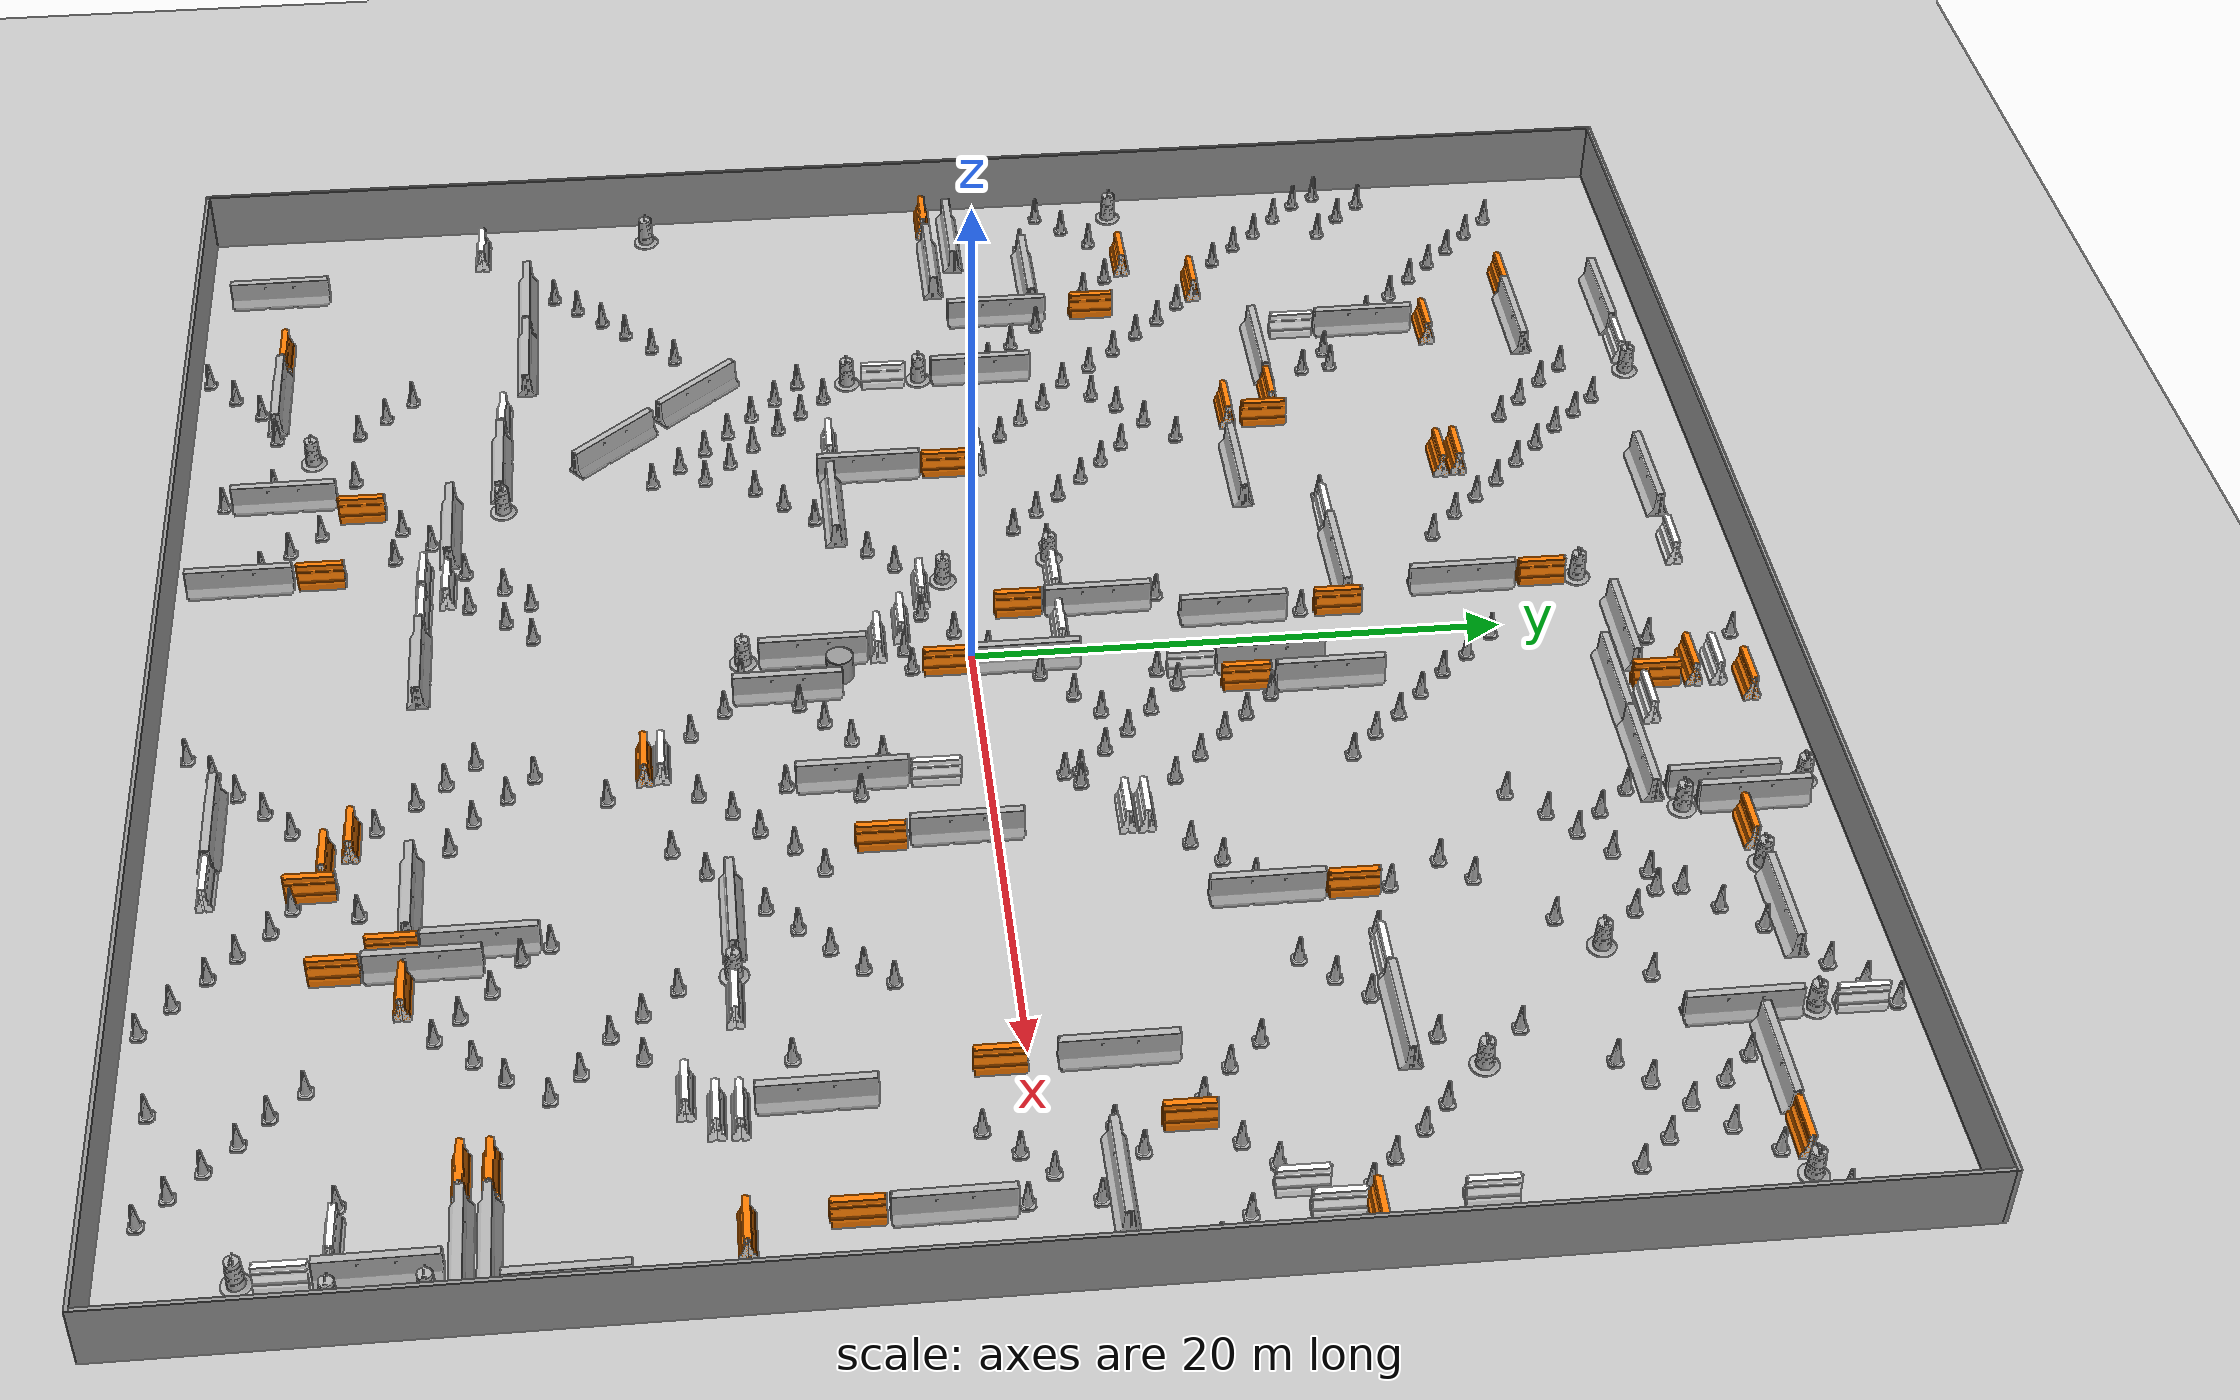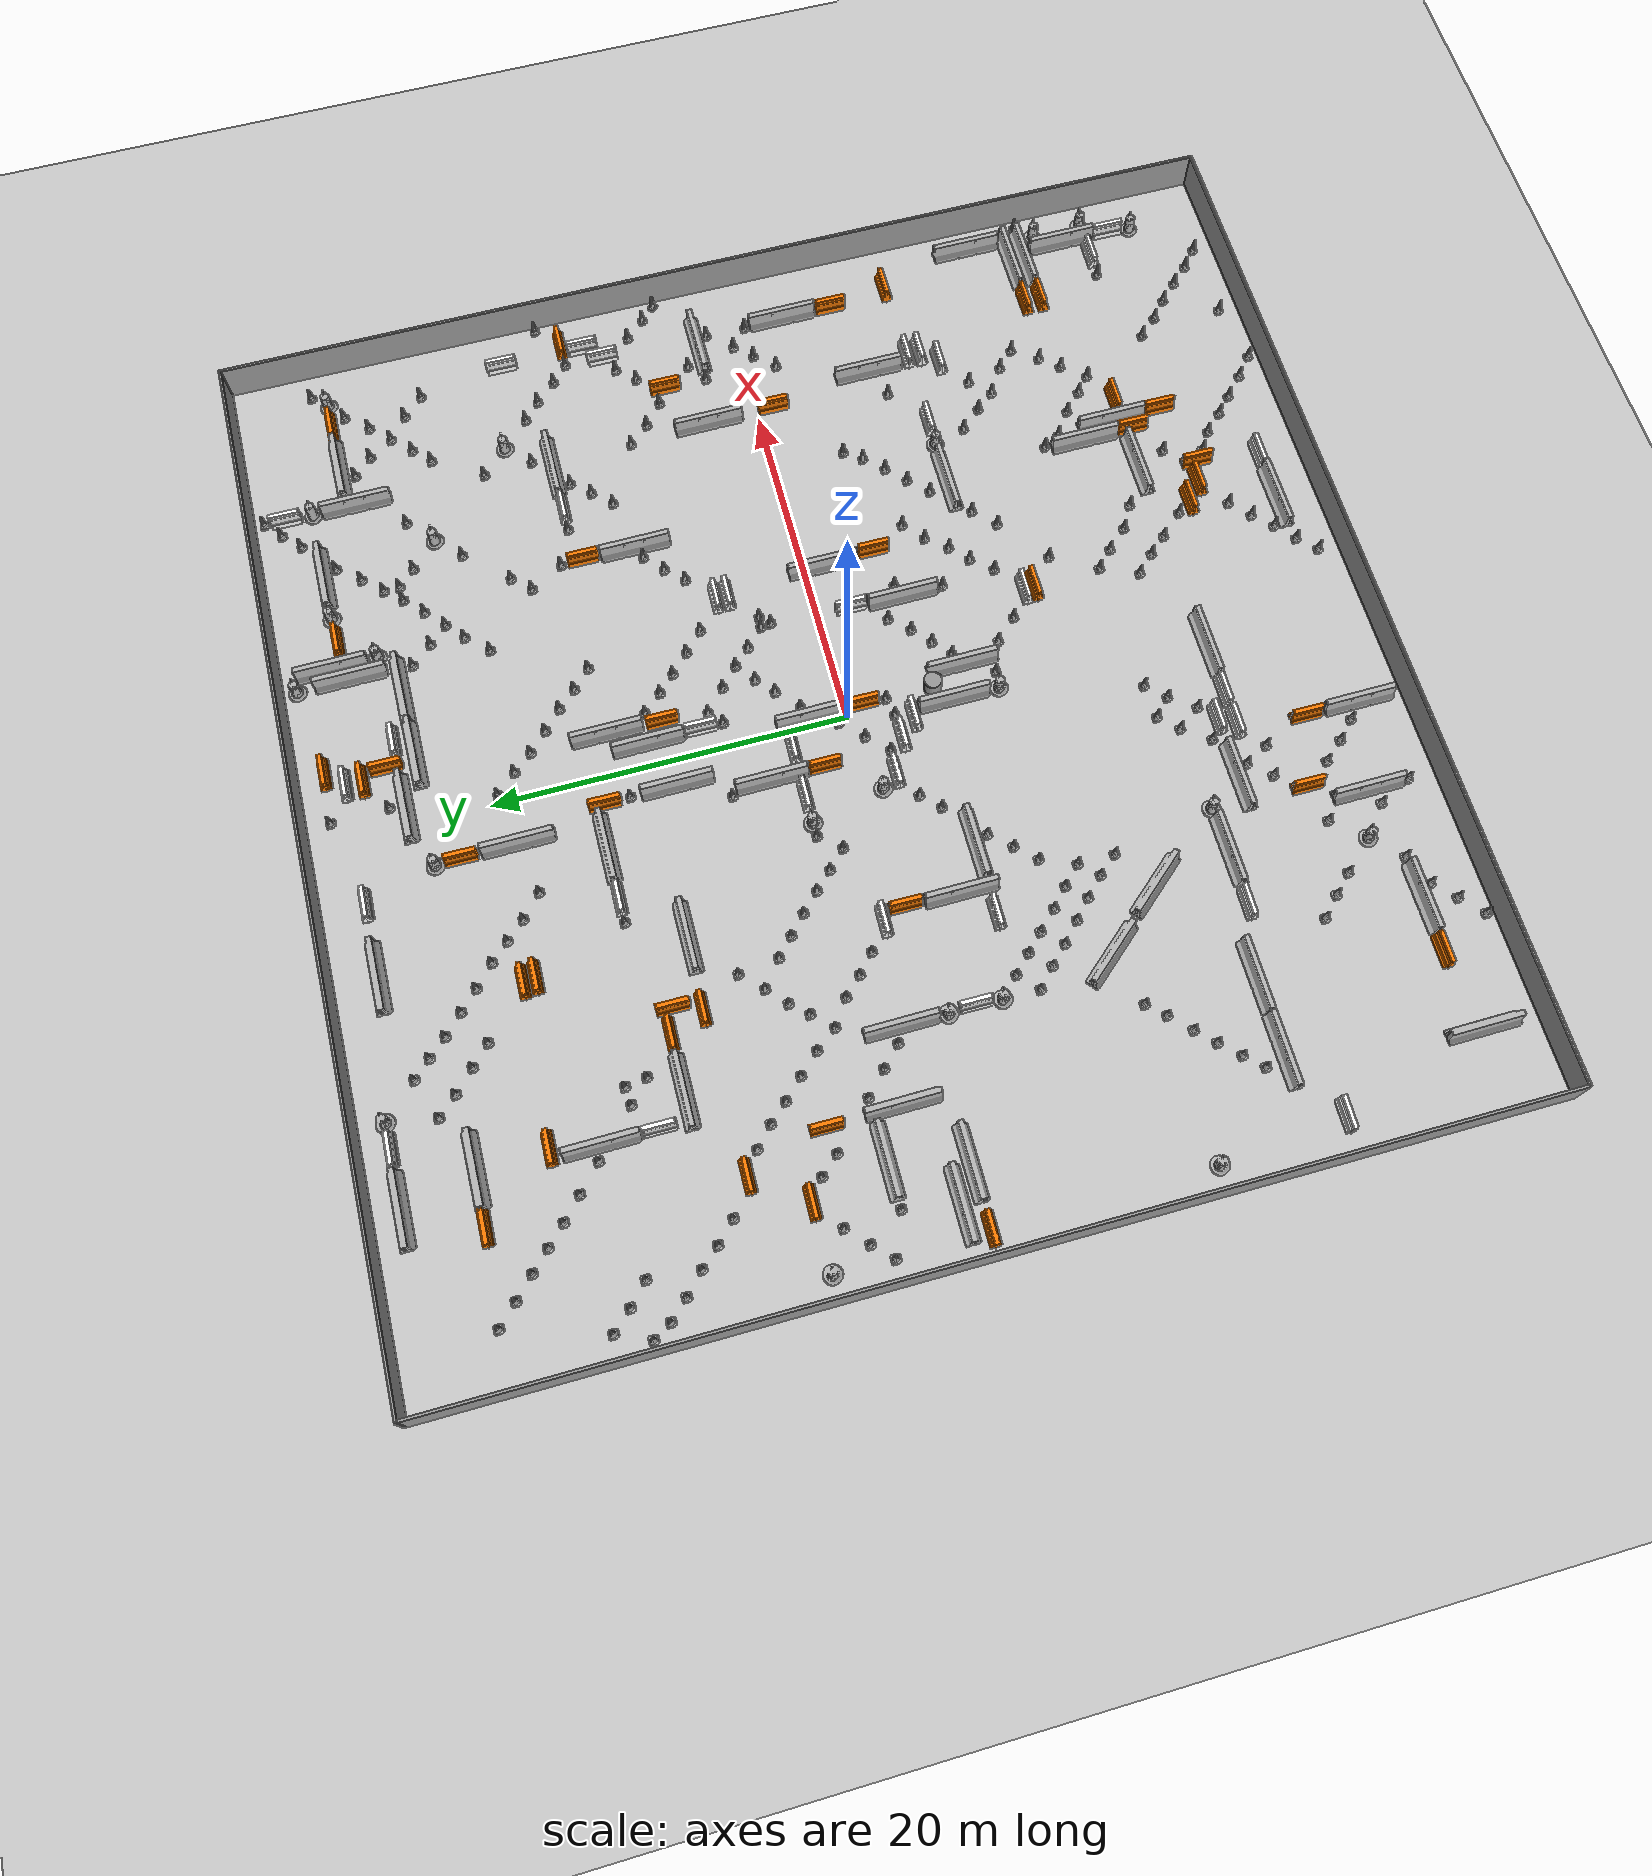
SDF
<sdf version="1.6">
 <world name="default">
  <light name="sun" type="directional">
   <pose>0 0 10 0 -0 0</pose>
   <diffuse>0.8 0.8 0.8 1</diffuse>
   <specular>0.2 0.2 0.2 1</specular>
   <attenuation>
    <range>1000</range>
    <constant>0.9</constant>
    <linear>0.01</linear>
    <quadratic>0.001</quadratic>
   </attenuation>
   <direction>-0.5 0.1 -0.9</direction>
  </light>
  <model name="ground_plane">
   <static>1</static>
   <link name="link">
    <collision name="collision">
     <geometry><plane><normal>0 0 1</normal><size>100 100</size></plane></geometry>
     <surface>
      <contact><collide_bitmask>65535</collide_bitmask></contact>
      <friction><ode><mu>100</mu><mu2>50</mu2></ode></friction>
     </surface>
    </collision>
    <visual name="visual">
     <cast_shadows>0</cast_shadows>
     <geometry><plane><normal>0 0 1</normal><size>100 100</size></plane></geometry>
     <material>
      <script><uri>file://media/materials/scripts/gazebo.material</uri><name>Gazebo/Grey</name></script>
     </material>
    </visual>
   </link>
  </model>
  <gravity>0 0 -9.8</gravity>
  <magnetic_field>6e-06 2.3e-05 -4.2e-05</magnetic_field>
  <atmosphere type="adiabatic"/>
  <physics name="default_physics" default="0" type="ode">
   <max_step_size>0.001</max_step_size>
   <real_time_factor>1</real_time_factor>
   <real_time_update_rate>1000</real_time_update_rate>
  </physics>
  <scene><ambient>0.4 0.4 0.4 1</ambient><background>0.7 0.7 0.7 1</background><shadows>1</shadows></scene>
  <spherical_coordinates>
   <surface_model>EARTH_WGS84</surface_model>
   <latitude_deg>0</latitude_deg>
   <longitude_deg>0</longitude_deg>
   <elevation>0</elevation>
   <heading_deg>0</heading_deg>
  </spherical_coordinates>
  <model name="30x30env"><static>1</static><pose>32.1206 3.39752 0 0 -0 0</pose></model>
  <model name="jersey_barrier_clone_clone_clone_0">
   <static>1</static>
   <link name="link">
    <visual name="visual">
     <geometry><mesh><uri>model://jersey_barrier/meshes/jersey_barrier.dae</uri></mesh></geometry>
    </visual>
    <collision name="upright">
     <pose>0 0 0.5715 0 -0 0</pose>
     <geometry><box><size>4.06542 0.3063 1.143</size></box></geometry>
    </collision>
    <collision name="base">
     <pose>0 0 0.032258 0 -0 0</pose>
     <geometry><box><size>4.06542 0.8107 0.064516</size></box></geometry>
    </collision>
    <collision name="base2">
     <pose>0 0 0.1 0 -0 0</pose>
     <geometry><box><size>4.06542 0.65 0.1</size></box></geometry>
    </collision>
    <collision name="base3">
     <pose>0 0 0.2 0 -0 0</pose>
     <geometry><box><size>4.06542 0.5 0.1</size></box></geometry>
    </collision>
    <collision name="left-angle">
     <pose>0 -0.224 0.2401 0.9 -0 0</pose>
     <geometry><box><size>4.06542 0.5 0.064516</size></box></geometry>
    </collision>
    <collision name="right-angle">
     <pose>0 0.224 0.2401 -0.9 0 0</pose>
     <geometry><box><size>4.06542 0.5 0.064516</size></box></geometry>
    </collision>
   </link>
   <pose>-20.0373 28.4134 0 0 -0 0</pose>
  </model>
  <model name="drc_practice_white_jersey_barrier_clone_clone_clone_clone">
   <static>1</static>
   <link name="link">
    <visual name="visual">
     <geometry>
      <mesh><uri>model://drc_practice_white_jersey_barrier/meshes/jersey_barrier.dae</uri></mesh>
     </geometry>
    </visual>
    <collision name="collision">
     <geometry>
      <mesh><uri>model://drc_practice_white_jersey_barrier/meshes/jersey_barrier.dae</uri></mesh>
     </geometry>
    </collision>
   </link>
   <pose>-16.9572 28.3837 0 0 0 -1.58176</pose>
  </model>
  <model name="Construction Barrel_clone_clone">
   <static>1</static>
   <link name="link">
    <inertial>
     <pose>0 0 0.4 0 -0 0</pose>
     <mass>500</mass>
     <inertia><ixx>51.2096</ixx><iyy>51.2096</iyy><izz>25</izz><ixy>0</ixy><ixz>0</ixz><iyz>0</iyz></inertia>
    </inertial>
    <collision name="collision">
     <geometry><mesh><uri>model://construction_barrel/meshes/construction_barrel.dae</uri></mesh></geometry>
    </collision>
    <visual name="visual">
     <geometry><mesh><uri>model://construction_barrel/meshes/construction_barrel.dae</uri></mesh></geometry>
    </visual>
   </link>
   <pose>-15.5034 28.4468 -0 0 0 -0.001474</pose>
  </model>
  <model name="jersey_barrier_clone_clone_clone_0_clone">
   <static>1</static>
   <link name="link">
    <visual name="visual">
     <geometry><mesh><uri>model://jersey_barrier/meshes/jersey_barrier.dae</uri></mesh></geometry>
    </visual>
    <collision name="upright">
     <pose>0 0 0.5715 0 -0 0</pose>
     <geometry><box><size>4.06542 0.3063 1.143</size></box></geometry>
    </collision>
    <collision name="base">
     <pose>0 0 0.032258 0 -0 0</pose>
     <geometry><box><size>4.06542 0.8107 0.064516</size></box></geometry>
    </collision>
    <collision name="base2">
     <pose>0 0 0.1 0 -0 0</pose>
     <geometry><box><size>4.06542 0.65 0.1</size></box></geometry>
    </collision>
    <collision name="base3">
     <pose>0 0 0.2 0 -0 0</pose>
     <geometry><box><size>4.06542 0.5 0.1</size></box></geometry>
    </collision>
    <collision name="left-angle">
     <pose>0 -0.224 0.2401 0.9 -0 0</pose>
     <geometry><box><size>4.06542 0.5 0.064516</size></box></geometry>
    </collision>
    <collision name="right-angle">
     <pose>0 0.224 0.2401 -0.9 0 0</pose>
     <geometry><box><size>4.06542 0.5 0.064516</size></box></geometry>
    </collision>
   </link>
   <pose>-7.93875 27.5109 0 0 -0 0</pose>
  </model>
  <model name="drc_practice_white_jersey_barrier_clone_clone_clone_clone_clone">
   <static>1</static>
   <link name="link">
    <visual name="visual">
     <geometry>
      <mesh><uri>model://drc_practice_white_jersey_barrier/meshes/jersey_barrier.dae</uri></mesh>
     </geometry>
    </visual>
    <collision name="collision">
     <geometry>
      <mesh><uri>model://drc_practice_white_jersey_barrier/meshes/jersey_barrier.dae</uri></mesh>
     </geometry>
    </collision>
   </link>
   <pose>-3.85344 27.4585 0 0 0 -1.58176</pose>
  </model>
  <model name="drc_practice_white_jersey_barrier_clone_clone_clone_clone_clone_clone">
   <static>1</static>
   <link name="link">
    <visual name="visual">
     <geometry>
      <mesh><uri>model://drc_practice_white_jersey_barrier/meshes/jersey_barrier.dae</uri></mesh>
     </geometry>
    </visual>
    <collision name="collision">
     <geometry>
      <mesh><uri>model://drc_practice_white_jersey_barrier/meshes/jersey_barrier.dae</uri></mesh>
     </geometry>
    </collision>
   </link>
   <pose>3.18572 27.399 0 0 0 -1.58176</pose>
  </model>
  <model name="drc_practice_organge_jersey_barrier_clone_clone">
   <static>1</static>
   <link name="link">
    <visual name="visual">
     <geometry>
      <mesh><uri>model://drc_practice_orange_jersey_barrier/meshes/jersey_barrier.dae</uri></mesh>
     </geometry>
    </visual>
    <collision name="collision">
     <geometry>
      <mesh><uri>model://drc_practice_orange_jersey_barrier/meshes/jersey_barrier.dae</uri></mesh>
     </geometry>
    </collision>
   </link>
   <pose>3.16298 26.4651 0 0 0 -1.57472</pose>
  </model>
  <model name="Construction Cone_0_clone_0_clone_clone">
   <static>1</static>
   <link name="link">
    <collision name="collision">
     <geometry>
      <mesh><scale>10 10 10</scale><uri>model://construction_cone/meshes/construction_cone.dae</uri></mesh>
     </geometry>
    </collision>
    <visual name="visual">
     <geometry>
      <mesh><scale>10 10 10</scale><uri>model://construction_cone/meshes/construction_cone.dae</uri></mesh>
     </geometry>
    </visual>
    <inertial>
     <inertia><ixx>1</ixx><ixy>0</ixy><ixz>0</ixz><iyy>1</iyy><iyz>0</iyz><izz>1</izz></inertia>
     <mass>1</mass>
    </inertial>
   </link>
   <pose>1.27357 28.5519 -0 0 -0 0</pose>
  </model>
  <model name="drc_practice_organge_jersey_barrier_clone_clone_clone">
   <static>1</static>
   <link name="link">
    <visual name="visual">
     <geometry>
      <mesh><uri>model://drc_practice_orange_jersey_barrier/meshes/jersey_barrier.dae</uri></mesh>
     </geometry>
    </visual>
    <collision name="collision">
     <geometry>
      <mesh><uri>model://drc_practice_orange_jersey_barrier/meshes/jersey_barrier.dae</uri></mesh>
     </geometry>
    </collision>
   </link>
   <pose>4.12989 28.4071 0 0 0 -1.57472</pose>
  </model>
  <model name="Construction Cone_0_clone_0_clone_clone_clone">
   <static>1</static>
   <link name="link">
    <collision name="collision">
     <geometry>
      <mesh><scale>10 10 10</scale><uri>model://construction_cone/meshes/construction_cone.dae</uri></mesh>
     </geometry>
    </collision>
    <visual name="visual">
     <geometry>
      <mesh><scale>10 10 10</scale><uri>model://construction_cone/meshes/construction_cone.dae</uri></mesh>
     </geometry>
    </visual>
    <inertial>
     <inertia><ixx>1</ixx><ixy>0</ixy><ixz>0</ixz><iyy>1</iyy><iyz>0</iyz><izz>1</izz></inertia>
     <mass>1</mass>
    </inertial>
   </link>
   <pose>1.32461 25.334 -0 0 -0 0</pose>
  </model>
  <model name="drc_practice_organge_jersey_barrier_clone_clone_0">
   <static>1</static>
   <link name="link">
    <visual name="visual">
     <geometry>
      <mesh><uri>model://drc_practice_orange_jersey_barrier/meshes/jersey_barrier.dae</uri></mesh>
     </geometry>
    </visual>
    <collision name="collision">
     <geometry>
      <mesh><uri>model://drc_practice_orange_jersey_barrier/meshes/jersey_barrier.dae</uri></mesh>
     </geometry>
    </collision>
   </link>
   <pose>3.6883 25.0832 0 0 -0 0</pose>
  </model>
  <model name="jersey_barrier_clone_clone_clone_0_clone_clone">
   <static>1</static>
   <link name="link">
    <visual name="visual">
     <geometry><mesh><uri>model://jersey_barrier/meshes/jersey_barrier.dae</uri></mesh></geometry>
    </visual>
    <collision name="upright">
     <pose>0 0 0.5715 0 -0 0</pose>
     <geometry><box><size>4.06542 0.3063 1.143</size></box></geometry>
    </collision>
    <collision name="base">
     <pose>0 0 0.032258 0 -0 0</pose>
     <geometry><box><size>4.06542 0.8107 0.064516</size></box></geometry>
    </collision>
    <collision name="base2">
     <pose>0 0 0.1 0 -0 0</pose>
     <geometry><box><size>4.06542 0.65 0.1</size></box></geometry>
    </collision>
    <collision name="base3">
     <pose>0 0 0.2 0 -0 0</pose>
     <geometry><box><size>4.06542 0.5 0.1</size></box></geometry>
    </collision>
    <collision name="left-angle">
     <pose>0 -0.224 0.2401 0.9 -0 0</pose>
     <geometry><box><size>4.06542 0.5 0.064516</size></box></geometry>
    </collision>
    <collision name="right-angle">
     <pose>0 0.224 0.2401 -0.9 0 0</pose>
     <geometry><box><size>4.06542 0.5 0.064516</size></box></geometry>
    </collision>
   </link>
   <pose>1.0354 24.4748 0 0 -0 0</pose>
  </model>
  <model name="drc_practice_white_jersey_barrier_clone_clone_clone_clone_clone_clone_clone">
   <static>1</static>
   <link name="link">
    <visual name="visual">
     <geometry>
      <mesh><uri>model://drc_practice_white_jersey_barrier/meshes/jersey_barrier.dae</uri></mesh>
     </geometry>
    </visual>
    <collision name="collision">
     <geometry>
      <mesh><uri>model://drc_practice_white_jersey_barrier/meshes/jersey_barrier.dae</uri></mesh>
     </geometry>
    </collision>
   </link>
   <pose>5.0618 24.4389 0 0 0 -1.58176</pose>
  </model>
  <model name="jersey_barrier_clone_clone_clone_0_clone_clone_clone">
   <static>1</static>
   <link name="link">
    <visual name="visual">
     <geometry><mesh><uri>model://jersey_barrier/meshes/jersey_barrier.dae</uri></mesh></geometry>
    </visual>
    <collision name="upright">
     <pose>0 0 0.5715 0 -0 0</pose>
     <geometry><box><size>4.06542 0.3063 1.143</size></box></geometry>
    </collision>
    <collision name="base">
     <pose>0 0 0.032258 0 -0 0</pose>
     <geometry><box><size>4.06542 0.8107 0.064516</size></box></geometry>
    </collision>
    <collision name="base2">
     <pose>0 0 0.1 0 -0 0</pose>
     <geometry><box><size>4.06542 0.65 0.1</size></box></geometry>
    </collision>
    <collision name="base3">
     <pose>0 0 0.2 0 -0 0</pose>
     <geometry><box><size>4.06542 0.5 0.1</size></box></geometry>
    </collision>
    <collision name="left-angle">
     <pose>0 -0.224 0.2401 0.9 -0 0</pose>
     <geometry><box><size>4.06542 0.5 0.064516</size></box></geometry>
    </collision>
    <collision name="right-angle">
     <pose>0 0.224 0.2401 -0.9 0 0</pose>
     <geometry><box><size>4.06542 0.5 0.064516</size></box></geometry>
    </collision>
   </link>
   <pose>4.01567 23.4568 0 0 -0 0</pose>
  </model>
  <model name="jersey_barrier_clone_clone_clone_0_clone_clone_clone_clone">
   <static>1</static>
   <link name="link">
    <visual name="visual">
     <geometry><mesh><uri>model://jersey_barrier/meshes/jersey_barrier.dae</uri></mesh></geometry>
    </visual>
    <collision name="upright">
     <pose>0 0 0.5715 0 -0 0</pose>
     <geometry><box><size>4.06542 0.3063 1.143</size></box></geometry>
    </collision>
    <collision name="base">
     <pose>0 0 0.032258 0 -0 0</pose>
     <geometry><box><size>4.06542 0.8107 0.064516</size></box></geometry>
    </collision>
    <collision name="base2">
     <pose>0 0 0.1 0 -0 0</pose>
     <geometry><box><size>4.06542 0.65 0.1</size></box></geometry>
    </collision>
    <collision name="base3">
     <pose>0 0 0.2 0 -0 0</pose>
     <geometry><box><size>4.06542 0.5 0.1</size></box></geometry>
    </collision>
    <collision name="left-angle">
     <pose>0 -0.224 0.2401 0.9 -0 0</pose>
     <geometry><box><size>4.06542 0.5 0.064516</size></box></geometry>
    </collision>
    <collision name="right-angle">
     <pose>0 0.224 0.2401 -0.9 0 0</pose>
     <geometry><box><size>4.06542 0.5 0.064516</size></box></geometry>
    </collision>
   </link>
   <pose>8.05825 23.4717 0 0 -0 0</pose>
  </model>
  <model name="jersey_barrier_clone_clone_clone_clone">
   <static>1</static>
   <link name="link">
    <visual name="visual">
     <geometry><mesh><uri>model://jersey_barrier/meshes/jersey_barrier.dae</uri></mesh></geometry>
    </visual>
    <collision name="upright">
     <pose>0 0 0.5715 0 -0 0</pose>
     <geometry><box><size>4.06542 0.3063 1.143</size></box></geometry>
    </collision>
    <collision name="base">
     <pose>0 0 0.032258 0 -0 0</pose>
     <geometry><box><size>4.06542 0.8107 0.064516</size></box></geometry>
    </collision>
    <collision name="base2">
     <pose>0 0 0.1 0 -0 0</pose>
     <geometry><box><size>4.06542 0.65 0.1</size></box></geometry>
    </collision>
    <collision name="base3">
     <pose>0 0 0.2 0 -0 0</pose>
     <geometry><box><size>4.06542 0.5 0.1</size></box></geometry>
    </collision>
    <collision name="left-angle">
     <pose>0 -0.224 0.2401 0.9 -0 0</pose>
     <geometry><box><size>4.06542 0.5 0.064516</size></box></geometry>
    </collision>
    <collision name="right-angle">
     <pose>0 0.224 0.2401 -0.9 0 0</pose>
     <geometry><box><size>4.06542 0.5 0.064516</size></box></geometry>
    </collision>
   </link>
   <pose>10.3741 26.9941 0 0 0 -1.56391</pose>
  </model>
  <model name="Construction Barrel_clone_clone_0_clone">
   <static>1</static>
   <link name="link">
    <inertial>
     <pose>0 0 0.4 0 -0 0</pose>
     <mass>500</mass>
     <inertia><ixx>51.2096</ixx><iyy>51.2096</iyy><izz>25</izz><ixy>0</ixy><ixz>0</ixz><iyz>0</iyz></inertia>
    </inertial>
    <collision name="collision">
     <geometry><mesh><uri>model://construction_barrel/meshes/construction_barrel.dae</uri></mesh></geometry>
    </collision>
    <visual name="visual">
     <geometry><mesh><uri>model://construction_barrel/meshes/construction_barrel.dae</uri></mesh></geometry>
    </visual>
   </link>
   <pose>10.46 24.419 -4e-06 -5e-06 -7e-06 -0.001185</pose>
  </model>
  <model name="drc_practice_organge_jersey_barrier_clone_clone_clone_0">
   <static>1</static>
   <link name="link">
    <visual name="visual">
     <geometry>
      <mesh><uri>model://drc_practice_orange_jersey_barrier/meshes/jersey_barrier.dae</uri></mesh>
     </geometry>
    </visual>
    <collision name="collision">
     <geometry>
      <mesh><uri>model://drc_practice_orange_jersey_barrier/meshes/jersey_barrier.dae</uri></mesh>
     </geometry>
    </collision>
   </link>
   <pose>11.881 26.4249 0 0 0 -1.57472</pose>
  </model>
  <model name="Construction Barrel_clone_clone_0_clone_clone">
   <static>1</static>
   <link name="link">
    <inertial>
     <pose>0 0 0.4 0 -0 0</pose>
     <mass>500</mass>
     <inertia><ixx>51.2096</ixx><iyy>51.2096</iyy><izz>25</izz><ixy>0</ixy><ixz>0</ixz><iyz>0</iyz></inertia>
    </inertial>
    <collision name="collision">
     <geometry><mesh><uri>model://construction_barrel/meshes/construction_barrel.dae</uri></mesh></geometry>
    </collision>
    <visual name="visual">
     <geometry><mesh><uri>model://construction_barrel/meshes/construction_barrel.dae</uri></mesh></geometry>
    </visual>
   </link>
   <pose>13.5043 26.5281 -0 0 0 -0.001456</pose>
  </model>
  <model name="jersey_barrier_clone_clone_clone_0_clone_clone_clone_clone_clone">
   <static>1</static>
   <link name="link">
    <visual name="visual">
     <geometry><mesh><uri>model://jersey_barrier/meshes/jersey_barrier.dae</uri></mesh></geometry>
    </visual>
    <collision name="upright">
     <pose>0 0 0.5715 0 -0 0</pose>
     <geometry><box><size>4.06542 0.3063 1.143</size></box></geometry>
    </collision>
    <collision name="base">
     <pose>0 0 0.032258 0 -0 0</pose>
     <geometry><box><size>4.06542 0.8107 0.064516</size></box></geometry>
    </collision>
    <collision name="base2">
     <pose>0 0 0.1 0 -0 0</pose>
     <geometry><box><size>4.06542 0.65 0.1</size></box></geometry>
    </collision>
    <collision name="base3">
     <pose>0 0 0.2 0 -0 0</pose>
     <geometry><box><size>4.06542 0.5 0.1</size></box></geometry>
    </collision>
    <collision name="left-angle">
     <pose>0 -0.224 0.2401 0.9 -0 0</pose>
     <geometry><box><size>4.06542 0.5 0.064516</size></box></geometry>
    </collision>
    <collision name="right-angle">
     <pose>0 0.224 0.2401 -0.9 0 0</pose>
     <geometry><box><size>4.06542 0.5 0.064516</size></box></geometry>
    </collision>
   </link>
   <pose>16.0869 26.5207 0 0 -0 0</pose>
  </model>
  <model name="Construction Cone_0_clone_0_clone_clone_clone_clone">
   <static>1</static>
   <link name="link">
    <collision name="collision">
     <geometry>
      <mesh><scale>10 10 10</scale><uri>model://construction_cone/meshes/construction_cone.dae</uri></mesh>
     </geometry>
    </collision>
    <visual name="visual">
     <geometry>
      <mesh><scale>10 10 10</scale><uri>model://construction_cone/meshes/construction_cone.dae</uri></mesh>
     </geometry>
    </visual>
    <inertial>
     <inertia><ixx>1</ixx><ixy>0</ixy><ixz>0</ixz><iyy>1</iyy><iyz>0</iyz><izz>1</izz></inertia>
     <mass>1</mass>
    </inertial>
   </link>
   <pose>18.5169 27.4726 -0 0 -0 0</pose>
  </model>
  <model name="Construction Cone_0_clone_0_clone_clone_clone_clone_0">
   <static>1</static>
   <link name="link">
    <collision name="collision">
     <geometry>
      <mesh><scale>10 10 10</scale><uri>model://construction_cone/meshes/construction_cone.dae</uri></mesh>
     </geometry>
    </collision>
    <visual name="visual">
     <geometry>
      <mesh><scale>10 10 10</scale><uri>model://construction_cone/meshes/construction_cone.dae</uri></mesh>
     </geometry>
    </visual>
    <inertial>
     <inertia><ixx>1</ixx><ixy>0</ixy><ixz>0</ixz><iyy>1</iyy><iyz>0</iyz><izz>1</izz></inertia>
     <mass>1</mass>
    </inertial>
   </link>
   <pose>19.5169 28.4493 -0 0 -0 0</pose>
  </model>
  <model name="Construction Cone_0_clone_0_clone_clone_clone_clone_1">
   <static>1</static>
   <link name="link">
    <collision name="collision">
     <geometry>
      <mesh><scale>10 10 10</scale><uri>model://construction_cone/meshes/construction_cone.dae</uri></mesh>
     </geometry>
    </collision>
    <visual name="visual">
     <geometry>
      <mesh><scale>10 10 10</scale><uri>model://construction_cone/meshes/construction_cone.dae</uri></mesh>
     </geometry>
    </visual>
    <inertial>
     <inertia><ixx>1</ixx><ixy>0</ixy><ixz>0</ixz><iyy>1</iyy><iyz>0</iyz><izz>1</izz></inertia>
     <mass>1</mass>
    </inertial>
   </link>
   <pose>20.5097 29.2967 -3e-06 -3e-06 -1e-06 -0</pose>
  </model>
  <model name="drc_practice_white_jersey_barrier_clone_clone_clone_0_clone_0_clone_clone">
   <static>1</static>
   <link name="link">
    <visual name="visual">
     <geometry>
      <mesh><uri>model://drc_practice_white_jersey_barrier/meshes/jersey_barrier.dae</uri></mesh>
     </geometry>
    </visual>
    <collision name="collision">
     <geometry>
      <mesh><uri>model://drc_practice_white_jersey_barrier/meshes/jersey_barrier.dae</uri></mesh>
     </geometry>
    </collision>
   </link>
   <pose>20.4533 28.0237 0 0 -0 3.13979</pose>
  </model>
  <model name="Construction Barrel_clone_clone_0_clone_clone_clone">
   <static>1</static>
   <link name="link">
    <inertial>
     <pose>0 0 0.4 0 -0 0</pose>
     <mass>500</mass>
     <inertia><ixx>51.2096</ixx><iyy>51.2096</iyy><izz>25</izz><ixy>0</ixy><ixz>0</ixz><iyz>0</iyz></inertia>
    </inertial>
    <collision name="collision">
     <geometry><mesh><uri>model://construction_barrel/meshes/construction_barrel.dae</uri></mesh></geometry>
    </collision>
    <visual name="visual">
     <geometry><mesh><uri>model://construction_barrel/meshes/construction_barrel.dae</uri></mesh></geometry>
    </visual>
   </link>
   <pose>20.4259 26.4992 -0 -0 -0 -9.7e-05</pose>
  </model>
  <model name="jersey_barrier_clone_clone_clone_clone_clone">
   <static>1</static>
   <link name="link">
    <visual name="visual">
     <geometry><mesh><uri>model://jersey_barrier/meshes/jersey_barrier.dae</uri></mesh></geometry>
    </visual>
    <collision name="upright">
     <pose>0 0 0.5715 0 -0 0</pose>
     <geometry><box><size>4.06542 0.3063 1.143</size></box></geometry>
    </collision>
    <collision name="base">
     <pose>0 0 0.032258 0 -0 0</pose>
     <geometry><box><size>4.06542 0.8107 0.064516</size></box></geometry>
    </collision>
    <collision name="base2">
     <pose>0 0 0.1 0 -0 0</pose>
     <geometry><box><size>4.06542 0.65 0.1</size></box></geometry>
    </collision>
    <collision name="base3">
     <pose>0 0 0.2 0 -0 0</pose>
     <geometry><box><size>4.06542 0.5 0.1</size></box></geometry>
    </collision>
    <collision name="left-angle">
     <pose>0 -0.224 0.2401 0.9 -0 0</pose>
     <geometry><box><size>4.06542 0.5 0.064516</size></box></geometry>
    </collision>
    <collision name="right-angle">
     <pose>0 0.224 0.2401 -0.9 0 0</pose>
     <geometry><box><size>4.06542 0.5 0.064516</size></box></geometry>
    </collision>
   </link>
   <pose>20.4546 23.9567 0 0 0 -1.56391</pose>
  </model>
  <model name="Construction Cone_0_clone_0_clone_clone_clone_clone_clone">
   <static>1</static>
   <link name="link">
    <collision name="collision">
     <geometry>
      <mesh><scale>10 10 10</scale><uri>model://construction_cone/meshes/construction_cone.dae</uri></mesh>
     </geometry>
    </collision>
    <visual name="visual">
     <geometry>
      <mesh><scale>10 10 10</scale><uri>model://construction_cone/meshes/construction_cone.dae</uri></mesh>
     </geometry>
    </visual>
    <inertial>
     <inertia><ixx>1</ixx><ixy>0</ixy><ixz>0</ixz><iyy>1</iyy><iyz>0</iyz><izz>1</izz></inertia>
     <mass>1</mass>
    </inertial>
   </link>
   <pose>16.5664 25.784 -0 0 -0 0</pose>
  </model>
  <model name="Construction Cone_0_clone_0_clone_clone_clone_clone_clone_0">
   <static>1</static>
   <link name="link">
    <collision name="collision">
     <geometry>
      <mesh><scale>10 10 10</scale><uri>model://construction_cone/meshes/construction_cone.dae</uri></mesh>
     </geometry>
    </collision>
    <visual name="visual">
     <geometry>
      <mesh><scale>10 10 10</scale><uri>model://construction_cone/meshes/construction_cone.dae</uri></mesh>
     </geometry>
    </visual>
    <inertial>
     <inertia><ixx>1</ixx><ixy>0</ixy><ixz>0</ixz><iyy>1</iyy><iyz>0</iyz><izz>1</izz></inertia>
     <mass>1</mass>
    </inertial>
   </link>
   <pose>15.5064 24.4982 -0 0 -0 0</pose>
  </model>
  <model name="Construction Cone_0_clone_0_clone_clone_clone_clone_clone_1">
   <static>1</static>
   <link name="link">
    <collision name="collision">
     <geometry>
      <mesh><scale>10 10 10</scale><uri>model://construction_cone/meshes/construction_cone.dae</uri></mesh>
     </geometry>
    </collision>
    <visual name="visual">
     <geometry>
      <mesh><scale>10 10 10</scale><uri>model://construction_cone/meshes/construction_cone.dae</uri></mesh>
     </geometry>
    </visual>
    <inertial>
     <inertia><ixx>1</ixx><ixy>0</ixy><ixz>0</ixz><iyy>1</iyy><iyz>0</iyz><izz>1</izz></inertia>
     <mass>1</mass>
    </inertial>
   </link>
   <pose>14.4695 23.4001 -0 0 -0 0</pose>
  </model>
  <model name="Construction Cone_0_clone_0_clone_clone_clone_clone_clone_2">
   <static>1</static>
   <link name="link">
    <collision name="collision">
     <geometry>
      <mesh><scale>10 10 10</scale><uri>model://construction_cone/meshes/construction_cone.dae</uri></mesh>
     </geometry>
    </collision>
    <visual name="visual">
     <geometry>
      <mesh><scale>10 10 10</scale><uri>model://construction_cone/meshes/construction_cone.dae</uri></mesh>
     </geometry>
    </visual>
    <inertial>
     <inertia><ixx>1</ixx><ixy>0</ixy><ixz>0</ixz><iyy>1</iyy><iyz>0</iyz><izz>1</izz></inertia>
     <mass>1</mass>
    </inertial>
   </link>
   <pose>13.6165 22.4345 -1e-05 -0 -0 -0</pose>
  </model>
  <model name="Construction Cone_0_clone_0_clone_clone_clone_clone_clone_3">
   <static>1</static>
   <link name="link">
    <collision name="collision">
     <geometry>
      <mesh><scale>10 10 10</scale><uri>model://construction_cone/meshes/construction_cone.dae</uri></mesh>
     </geometry>
    </collision>
    <visual name="visual">
     <geometry>
      <mesh><scale>10 10 10</scale><uri>model://construction_cone/meshes/construction_cone.dae</uri></mesh>
     </geometry>
    </visual>
    <inertial>
     <inertia><ixx>1</ixx><ixy>0</ixy><ixz>0</ixz><iyy>1</iyy><iyz>0</iyz><izz>1</izz></inertia>
     <mass>1</mass>
    </inertial>
   </link>
   <pose>14.4874 22.4791 -0 0 -0 0</pose>
  </model>
  <model name="Construction Cone_0_clone_0_clone_clone_clone_clone_clone_4">
   <static>1</static>
   <link name="link">
    <collision name="collision">
     <geometry>
      <mesh><scale>10 10 10</scale><uri>model://construction_cone/meshes/construction_cone.dae</uri></mesh>
     </geometry>
    </collision>
    <visual name="visual">
     <geometry>
      <mesh><scale>10 10 10</scale><uri>model://construction_cone/meshes/construction_cone.dae</uri></mesh>
     </geometry>
    </visual>
    <inertial>
     <inertia><ixx>1</ixx><ixy>0</ixy><ixz>0</ixz><iyy>1</iyy><iyz>0</iyz><izz>1</izz></inertia>
     <mass>1</mass>
    </inertial>
   </link>
   <pose>12.5306 21.4117 -0 0 -0 0</pose>
  </model>
  <model name="Construction Cone_0_clone_0_clone_clone_clone_clone_clone_5">
   <static>1</static>
   <link name="link">
    <collision name="collision">
     <geometry>
      <mesh><scale>10 10 10</scale><uri>model://construction_cone/meshes/construction_cone.dae</uri></mesh>
     </geometry>
    </collision>
    <visual name="visual">
     <geometry>
      <mesh><scale>10 10 10</scale><uri>model://construction_cone/meshes/construction_cone.dae</uri></mesh>
     </geometry>
    </visual>
    <inertial>
     <inertia><ixx>1</ixx><ixy>0</ixy><ixz>0</ixz><iyy>1</iyy><iyz>0</iyz><izz>1</izz></inertia>
     <mass>1</mass>
    </inertial>
   </link>
   <pose>11.4155 20.4091 -0 0 -0 0</pose>
  </model>
  <model name="Construction Cone_0_clone_0_clone_clone_clone_clone_clone_6">
   <static>1</static>
   <link name="link">
    <collision name="collision">
     <geometry>
      <mesh><scale>10 10 10</scale><uri>model://construction_cone/meshes/construction_cone.dae</uri></mesh>
     </geometry>
    </collision>
    <visual name="visual">
     <geometry>
      <mesh><scale>10 10 10</scale><uri>model://construction_cone/meshes/construction_cone.dae</uri></mesh>
     </geometry>
    </visual>
    <inertial>
     <inertia><ixx>1</ixx><ixy>0</ixy><ixz>0</ixz><iyy>1</iyy><iyz>0</iyz><izz>1</izz></inertia>
     <mass>1</mass>
    </inertial>
   </link>
   <pose>10.4589 21.4449 -0 0 -0 0</pose>
  </model>
  <model name="Construction Cone_0_clone_0_clone_clone_clone_clone_clone_7">
   <static>1</static>
   <link name="link">
    <collision name="collision">
     <geometry>
      <mesh><scale>10 10 10</scale><uri>model://construction_cone/meshes/construction_cone.dae</uri></mesh>
     </geometry>
    </collision>
    <visual name="visual">
     <geometry>
      <mesh><scale>10 10 10</scale><uri>model://construction_cone/meshes/construction_cone.dae</uri></mesh>
     </geometry>
    </visual>
    <inertial>
     <inertia><ixx>1</ixx><ixy>0</ixy><ixz>0</ixz><iyy>1</iyy><iyz>0</iyz><izz>1</izz></inertia>
     <mass>1</mass>
    </inertial>
   </link>
   <pose>10.3713 19.5185 -0 0 -0 0</pose>
  </model>
  <model name="Construction Cone_0_clone_0_clone_clone_clone_clone_clone_8">
   <static>1</static>
   <link name="link">
    <collision name="collision">
     <geometry>
      <mesh><scale>10 10 10</scale><uri>model://construction_cone/meshes/construction_cone.dae</uri></mesh>
     </geometry>
    </collision>
    <visual name="visual">
     <geometry>
      <mesh><scale>10 10 10</scale><uri>model://construction_cone/meshes/construction_cone.dae</uri></mesh>
     </geometry>
    </visual>
    <inertial>
     <inertia><ixx>1</ixx><ixy>0</ixy><ixz>0</ixz><iyy>1</iyy><iyz>0</iyz><izz>1</izz></inertia>
     <mass>1</mass>
    </inertial>
   </link>
   <pose>9.21897 18.2858 -0 0 -0 0</pose>
  </model>
  <model name="Construction Barrel_clone_clone_0_clone_clone_0">
   <static>1</static>
   <link name="link">
    <inertial>
     <pose>0 0 0.4 0 -0 0</pose>
     <mass>500</mass>
     <inertia><ixx>51.2096</ixx><iyy>51.2096</iyy><izz>25</izz><ixy>0</ixy><ixz>0</ixz><iyz>0</iyz></inertia>
    </inertial>
    <collision name="collision">
     <geometry><mesh><uri>model://construction_barrel/meshes/construction_barrel.dae</uri></mesh></geometry>
    </collision>
    <visual name="visual">
     <geometry><mesh><uri>model://construction_barrel/meshes/construction_barrel.dae</uri></mesh></geometry>
    </visual>
   </link>
   <pose>16.9571 20.0177 0 0 -0 0.001192</pose>
  </model>
  <model name="Construction Cone_0_clone_0_clone_clone_clone_clone_clone_3_clone_clone">
   <static>1</static>
   <link name="link">
    <collision name="collision">
     <geometry>
      <mesh><scale>10 10 10</scale><uri>model://construction_cone/meshes/construction_cone.dae</uri></mesh>
     </geometry>
    </collision>
    <visual name="visual">
     <geometry>
      <mesh><scale>10 10 10</scale><uri>model://construction_cone/meshes/construction_cone.dae</uri></mesh>
     </geometry>
    </visual>
    <inertial>
     <inertia><ixx>1</ixx><ixy>0</ixy><ixz>0</ixz><iyy>1</iyy><iyz>0</iyz><izz>1</izz></inertia>
     <mass>1</mass>
    </inertial>
   </link>
   <pose>15.5665 18.676 -0 0 -0 0</pose>
  </model>
  <model name="Construction Cone_0_clone_0_clone_clone_clone_clone_clone_3_clone_clone_0">
   <static>1</static>
   <link name="link">
    <collision name="collision">
     <geometry>
      <mesh><scale>10 10 10</scale><uri>model://construction_cone/meshes/construction_cone.dae</uri></mesh>
     </geometry>
    </collision>
    <visual name="visual">
     <geometry>
      <mesh><scale>10 10 10</scale><uri>model://construction_cone/meshes/construction_cone.dae</uri></mesh>
     </geometry>
    </visual>
    <inertial>
     <inertia><ixx>1</ixx><ixy>0</ixy><ixz>0</ixz><iyy>1</iyy><iyz>0</iyz><izz>1</izz></inertia>
     <mass>1</mass>
    </inertial>
   </link>
   <pose>15.4462 21.5255 -0 0 -1e-06 0</pose>
  </model>
  <model name="Construction Cone_0_clone_0_clone_clone_clone_clone_clone_3_clone_clone_1">
   <static>1</static>
   <link name="link">
    <collision name="collision">
     <geometry>
      <mesh><scale>10 10 10</scale><uri>model://construction_cone/meshes/construction_cone.dae</uri></mesh>
     </geometry>
    </collision>
    <visual name="visual">
     <geometry>
      <mesh><scale>10 10 10</scale><uri>model://construction_cone/meshes/construction_cone.dae</uri></mesh>
     </geometry>
    </visual>
    <inertial>
     <inertia><ixx>1</ixx><ixy>0</ixy><ixz>0</ixz><iyy>1</iyy><iyz>0</iyz><izz>1</izz></inertia>
     <mass>1</mass>
    </inertial>
   </link>
   <pose>18.4838 21.385 -0 0 -1e-06 0</pose>
  </model>
  <model name="Construction Cone_0_clone_0_clone_clone_clone_clone_clone_3_clone_0_clone">
   <static>1</static>
   <link name="link">
    <collision name="collision">
     <geometry>
      <mesh><scale>10 10 10</scale><uri>model://construction_cone/meshes/construction_cone.dae</uri></mesh>
     </geometry>
    </collision>
    <visual name="visual">
     <geometry>
      <mesh><scale>10 10 10</scale><uri>model://construction_cone/meshes/construction_cone.dae</uri></mesh>
     </geometry>
    </visual>
    <inertial>
     <inertia><ixx>1</ixx><ixy>0</ixy><ixz>0</ixz><iyy>1</iyy><iyz>0</iyz><izz>1</izz></inertia>
     <mass>1</mass>
    </inertial>
   </link>
   <pose>20.4774 16.4375 -0 0 -0 0</pose>
  </model>
  <model name="Construction Cone_0_clone_0_clone_clone_clone_clone_clone_3_clone_0_clone_clone">
   <static>1</static>
   <link name="link">
    <collision name="collision">
     <geometry>
      <mesh><scale>10 10 10</scale><uri>model://construction_cone/meshes/construction_cone.dae</uri></mesh>
     </geometry>
    </collision>
    <visual name="visual">
     <geometry>
      <mesh><scale>10 10 10</scale><uri>model://construction_cone/meshes/construction_cone.dae</uri></mesh>
     </geometry>
    </visual>
    <inertial>
     <inertia><ixx>1</ixx><ixy>0</ixy><ixz>0</ixz><iyy>1</iyy><iyz>0</iyz><izz>1</izz></inertia>
     <mass>1</mass>
    </inertial>
   </link>
   <pose>20.6118 13.6161 -0 0 -0 0</pose>
  </model>
  <model name="jersey_barrier_clone_clone_clone_0_clone_clone_clone_clone_clone_clone">
   <static>1</static>
   <link name="link">
    <visual name="visual">
     <geometry><mesh><uri>model://jersey_barrier/meshes/jersey_barrier.dae</uri></mesh></geometry>
    </visual>
    <collision name="upright">
     <pose>0 0 0.5715 0 -0 0</pose>
     <geometry><box><size>4.06542 0.3063 1.143</size></box></geometry>
    </collision>
    <collision name="base">
     <pose>0 0 0.032258 0 -0 0</pose>
     <geometry><box><size>4.06542 0.8107 0.064516</size></box></geometry>
    </collision>
    <collision name="base2">
     <pose>0 0 0.1 0 -0 0</pose>
     <geometry><box><size>4.06542 0.65 0.1</size></box></geometry>
    </collision>
    <collision name="base3">
     <pose>0 0 0.2 0 -0 0</pose>
     <geometry><box><size>4.06542 0.5 0.1</size></box></geometry>
    </collision>
    <collision name="left-angle">
     <pose>0 -0.224 0.2401 0.9 -0 0</pose>
     <geometry><box><size>4.06542 0.5 0.064516</size></box></geometry>
    </collision>
    <collision name="right-angle">
     <pose>0 0.224 0.2401 -0.9 0 0</pose>
     <geometry><box><size>4.06542 0.5 0.064516</size></box></geometry>
    </collision>
   </link>
   <pose>22.9889 24.5203 0 0 -0 0</pose>
  </model>
  <model name="Construction Barrel_clone_clone_0_clone_clone_clone_2">
   <static>1</static>
   <link name="link">
    <inertial>
     <pose>0 0 0.4 0 -0 0</pose>
     <mass>500</mass>
     <inertia><ixx>51.2096</ixx><iyy>51.2096</iyy><izz>25</izz><ixy>0</ixy><ixz>0</ixz><iyz>0</iyz></inertia>
    </inertial>
    <collision name="collision">
     <geometry><mesh><uri>model://construction_barrel/meshes/construction_barrel.dae</uri></mesh></geometry>
    </collision>
    <visual name="visual">
     <geometry><mesh><uri>model://construction_barrel/meshes/construction_barrel.dae</uri></mesh></geometry>
    </visual>
   </link>
   <pose>27.5834 24.4727 -0 0 -0 0.021971</pose>
  </model>
  <model name="Construction Cone_0_clone_0_clone_clone_clone_clone_clone_6_clone">
   <static>1</static>
   <link name="link">
    <collision name="collision">
     <geometry>
      <mesh><scale>10 10 10</scale><uri>model://construction_cone/meshes/construction_cone.dae</uri></mesh>
     </geometry>
    </collision>
    <visual name="visual">
     <geometry>
      <mesh><scale>10 10 10</scale><uri>model://construction_cone/meshes/construction_cone.dae</uri></mesh>
     </geometry>
    </visual>
    <inertial>
     <inertia><ixx>1</ixx><ixy>0</ixy><ixz>0</ixz><iyy>1</iyy><iyz>0</iyz><izz>1</izz></inertia>
     <mass>1</mass>
    </inertial>
   </link>
   <pose>9.41231 22.6309 -0 0 -0 0</pose>
  </model>
  <model name="Construction Cone_0_clone_0_clone_clone_clone_clone_clone_3_clone_clone_clone">
   <static>1</static>
   <link name="link">
    <collision name="collision">
     <geometry>
      <mesh><scale>10 10 10</scale><uri>model://construction_cone/meshes/construction_cone.dae</uri></mesh>
     </geometry>
    </collision>
    <visual name="visual">
     <geometry>
      <mesh><scale>10 10 10</scale><uri>model://construction_cone/meshes/construction_cone.dae</uri></mesh>
     </geometry>
    </visual>
    <inertial>
     <inertia><ixx>1</ixx><ixy>0</ixy><ixz>0</ixz><iyy>1</iyy><iyz>0</iyz><izz>1</izz></inertia>
     <mass>1</mass>
    </inertial>
   </link>
   <pose>13.3589 16.2835 -0 0 -1e-06 0</pose>
  </model>
  <model name="Construction Cone_0_clone_0_clone_clone_clone_clone_clone_3_clone_clone_clone_0">
   <static>1</static>
   <link name="link">
    <collision name="collision">
     <geometry>
      <mesh><scale>10 10 10</scale><uri>model://construction_cone/meshes/construction_cone.dae</uri></mesh>
     </geometry>
    </collision>
    <visual name="visual">
     <geometry>
      <mesh><scale>10 10 10</scale><uri>model://construction_cone/meshes/construction_cone.dae</uri></mesh>
     </geometry>
    </visual>
    <inertial>
     <inertia><ixx>1</ixx><ixy>0</ixy><ixz>0</ixz><iyy>1</iyy><iyz>0</iyz><izz>1</izz></inertia>
     <mass>1</mass>
    </inertial>
   </link>
   <pose>12.3815 15.2493 0 -0 -0 -0</pose>
  </model>
  <model name="Construction Cone_0_clone_0_clone_clone_clone_clone_clone_3_clone_0_clone_clone_0">
   <static>1</static>
   <link name="link">
    <collision name="collision">
     <geometry>
      <mesh><scale>10 10 10</scale><uri>model://construction_cone/meshes/construction_cone.dae</uri></mesh>
     </geometry>
    </collision>
    <visual name="visual">
     <geometry>
      <mesh><scale>10 10 10</scale><uri>model://construction_cone/meshes/construction_cone.dae</uri></mesh>
     </geometry>
    </visual>
    <inertial>
     <inertia><ixx>1</ixx><ixy>0</ixy><ixz>0</ixz><iyy>1</iyy><iyz>0</iyz><izz>1</izz></inertia>
     <mass>1</mass>
    </inertial>
   </link>
   <pose>23.5533 13.3733 -0 0 -0 0</pose>
  </model>
  <model name="Construction Cone_0_clone_0_clone_clone_clone_clone_clone_3_clone_0_clone_clone_1">
   <static>1</static>
   <link name="link">
    <collision name="collision">
     <geometry>
      <mesh><scale>10 10 10</scale><uri>model://construction_cone/meshes/construction_cone.dae</uri></mesh>
     </geometry>
    </collision>
    <visual name="visual">
     <geometry>
      <mesh><scale>10 10 10</scale><uri>model://construction_cone/meshes/construction_cone.dae</uri></mesh>
     </geometry>
    </visual>
    <inertial>
     <inertia><ixx>1</ixx><ixy>0</ixy><ixz>0</ixz><iyy>1</iyy><iyz>0</iyz><izz>1</izz></inertia>
     <mass>1</mass>
    </inertial>
   </link>
   <pose>24.5911 12.4307 -3e-06 -3e-06 -1e-06 -0</pose>
  </model>
  <model name="Construction Cone_0_clone_0_clone_clone_clone_clone_clone_3_clone_0_clone_clone_2">
   <static>1</static>
   <link name="link">
    <collision name="collision">
     <geometry>
      <mesh><scale>10 10 10</scale><uri>model://construction_cone/meshes/construction_cone.dae</uri></mesh>
     </geometry>
    </collision>
    <visual name="visual">
     <geometry>
      <mesh><scale>10 10 10</scale><uri>model://construction_cone/meshes/construction_cone.dae</uri></mesh>
     </geometry>
    </visual>
    <inertial>
     <inertia><ixx>1</ixx><ixy>0</ixy><ixz>0</ixz><iyy>1</iyy><iyz>0</iyz><izz>1</izz></inertia>
     <mass>1</mass>
    </inertial>
   </link>
   <pose>25.6981 11.2556 -3e-06 -3e-06 -1e-06 -0</pose>
  </model>
  <model name="drc_practice_organge_jersey_barrier_clone_clone_clone_0_clone">
   <static>1</static>
   <link name="link">
    <visual name="visual">
     <geometry>
      <mesh><uri>model://drc_practice_orange_jersey_barrier/meshes/jersey_barrier.dae</uri></mesh>
     </geometry>
    </visual>
    <collision name="collision">
     <geometry>
      <mesh><uri>model://drc_practice_orange_jersey_barrier/meshes/jersey_barrier.dae</uri></mesh>
     </geometry>
    </collision>
   </link>
   <pose>28.1226 10.3364 0 0 0 -1.57472</pose>
  </model>
  <model name="Construction Cone_0_clone_0_clone_clone_clone_clone_clone_3_clone_0_clone_clone_2_clone">
   <static>1</static>
   <link name="link">
    <collision name="collision">
     <geometry>
      <mesh><scale>10 10 10</scale><uri>model://construction_cone/meshes/construction_cone.dae</uri></mesh>
     </geometry>
    </collision>
    <visual name="visual">
     <geometry>
      <mesh><scale>10 10 10</scale><uri>model://construction_cone/meshes/construction_cone.dae</uri></mesh>
     </geometry>
    </visual>
    <inertial>
     <inertia><ixx>1</ixx><ixy>0</ixy><ixz>0</ixz><iyy>1</iyy><iyz>0</iyz><izz>1</izz></inertia>
     <mass>1</mass>
    </inertial>
   </link>
   <pose>26.7361 10.3238 -0 0 -0 0</pose>
  </model>
  <model name="drc_practice_white_jersey_barrier_clone_clone_clone_0_clone_0_clone_clone_clone">
   <static>1</static>
   <link name="link">
    <visual name="visual">
     <geometry>
      <mesh><uri>model://drc_practice_white_jersey_barrier/meshes/jersey_barrier.dae</uri></mesh>
     </geometry>
    </visual>
    <collision name="collision">
     <geometry>
      <mesh><uri>model://drc_practice_white_jersey_barrier/meshes/jersey_barrier.dae</uri></mesh>
     </geometry>
    </collision>
   </link>
   <pose>27.5941 13.9985 0 0 -0 3.13979</pose>
  </model>
  <model name="Construction Cone_0_clone_0_clone_clone_clone_clone_clone_3_clone_0_clone_clone_2_clone_clone">
   <static>1</static>
   <link name="link">
    <collision name="collision">
     <geometry>
      <mesh><scale>10 10 10</scale><uri>model://construction_cone/meshes/construction_cone.dae</uri></mesh>
     </geometry>
    </collision>
    <visual name="visual">
     <geometry>
      <mesh><scale>10 10 10</scale><uri>model://construction_cone/meshes/construction_cone.dae</uri></mesh>
     </geometry>
    </visual>
    <inertial>
     <inertia><ixx>1</ixx><ixy>0</ixy><ixz>0</ixz><iyy>1</iyy><iyz>0</iyz><izz>1</izz></inertia>
     <mass>1</mass>
    </inertial>
   </link>
   <pose>29.595 11.6065 -0 0 -0 0.005179</pose>
  </model>
  <model name="Construction Cone_0_clone_0_clone_clone_clone_clone_clone_3_clone_0_clone_clone_2_clone_clone_clone">
   <static>1</static>
   <link name="link">
    <collision name="collision">
     <geometry>
      <mesh><scale>10 10 10</scale><uri>model://construction_cone/meshes/construction_cone.dae</uri></mesh>
     </geometry>
    </collision>
    <visual name="visual">
     <geometry>
      <mesh><scale>10 10 10</scale><uri>model://construction_cone/meshes/construction_cone.dae</uri></mesh>
     </geometry>
    </visual>
    <inertial>
     <inertia><ixx>1</ixx><ixy>0</ixy><ixz>0</ixz><iyy>1</iyy><iyz>0</iyz><izz>1</izz></inertia>
     <mass>1</mass>
    </inertial>
   </link>
   <pose>28.3754 25.3563 -0 0 -1e-06 0</pose>
  </model>
  <model name="Construction Cone_0_clone_0_clone_clone_clone_clone_clone_3_clone_0_clone_clone_2_clone_clone_clone_clone">
   <static>1</static>
   <link name="link">
    <collision name="collision">
     <geometry>
      <mesh><scale>10 10 10</scale><uri>model://construction_cone/meshes/construction_cone.dae</uri></mesh>
     </geometry>
    </collision>
    <visual name="visual">
     <geometry>
      <mesh><scale>10 10 10</scale><uri>model://construction_cone/meshes/construction_cone.dae</uri></mesh>
     </geometry>
    </visual>
    <inertial>
     <inertia><ixx>1</ixx><ixy>0</ixy><ixz>0</ixz><iyy>1</iyy><iyz>0</iyz><izz>1</izz></inertia>
     <mass>1</mass>
    </inertial>
   </link>
   <pose>26.4919 23.6928 -0 -0 -0 -0</pose>
  </model>
  <model name="Construction Cone_0_clone_0_clone_clone_clone_clone_clone_3_clone_0_clone_clone_2_clone_clone_clone_clone_0">
   <static>1</static>
   <link name="link">
    <collision name="collision">
     <geometry>
      <mesh><scale>10 10 10</scale><uri>model://construction_cone/meshes/construction_cone.dae</uri></mesh>
     </geometry>
    </collision>
    <visual name="visual">
     <geometry>
      <mesh><scale>10 10 10</scale><uri>model://construction_cone/meshes/construction_cone.dae</uri></mesh>
     </geometry>
    </visual>
    <inertial>
     <inertia><ixx>1</ixx><ixy>0</ixy><ixz>0</ixz><iyy>1</iyy><iyz>0</iyz><izz>1</izz></inertia>
     <mass>1</mass>
    </inertial>
   </link>
   <pose>25.3968 22.3982 -0 0 -1e-06 0</pose>
  </model>
  <model name="Construction Cone_0_clone_0_clone_clone_clone_clone_clone_3_clone_0_clone_clone_2_clone_clone_clone_clone_1">
   <static>1</static>
   <link name="link">
    <collision name="collision">
     <geometry>
      <mesh><scale>10 10 10</scale><uri>model://construction_cone/meshes/construction_cone.dae</uri></mesh>
     </geometry>
    </collision>
    <visual name="visual">
     <geometry>
      <mesh><scale>10 10 10</scale><uri>model://construction_cone/meshes/construction_cone.dae</uri></mesh>
     </geometry>
    </visual>
    <inertial>
     <inertia><ixx>1</ixx><ixy>0</ixy><ixz>0</ixz><iyy>1</iyy><iyz>0</iyz><izz>1</izz></inertia>
     <mass>1</mass>
    </inertial>
   </link>
   <pose>24.3052 21.2912 -0 0 -1e-06 0</pose>
  </model>
  <model name="Construction Cone_0_clone_0_clone_clone_clone_clone_clone_3_clone_0_clone_clone_2_clone_clone_clone_clone_2">
   <static>1</static>
   <link name="link">
    <collision name="collision">
     <geometry>
      <mesh><scale>10 10 10</scale><uri>model://construction_cone/meshes/construction_cone.dae</uri></mesh>
     </geometry>
    </collision>
    <visual name="visual">
     <geometry>
      <mesh><scale>10 10 10</scale><uri>model://construction_cone/meshes/construction_cone.dae</uri></mesh>
     </geometry>
    </visual>
    <inertial>
     <inertia><ixx>1</ixx><ixy>0</ixy><ixz>0</ixz><iyy>1</iyy><iyz>0</iyz><izz>1</izz></inertia>
     <mass>1</mass>
    </inertial>
   </link>
   <pose>23.2366 20.2071 0 -0 -0 -0</pose>
  </model>
  <model name="Construction Cone_0_clone_0_clone_clone_clone_clone_clone_3_clone_0_clone_clone_2_clone_clone_clone_clone_3">
   <static>1</static>
   <link name="link">
    <collision name="collision">
     <geometry>
      <mesh><scale>10 10 10</scale><uri>model://construction_cone/meshes/construction_cone.dae</uri></mesh>
     </geometry>
    </collision>
    <visual name="visual">
     <geometry>
      <mesh><scale>10 10 10</scale><uri>model://construction_cone/meshes/construction_cone.dae</uri></mesh>
     </geometry>
    </visual>
    <inertial>
     <inertia><ixx>1</ixx><ixy>0</ixy><ixz>0</ixz><iyy>1</iyy><iyz>0</iyz><izz>1</izz></inertia>
     <mass>1</mass>
    </inertial>
   </link>
   <pose>22.2408 19.2513 -0 -0 -0 -0</pose>
  </model>
  <model name="Construction Cone_0_clone_0_clone_clone_clone_clone_clone_3_clone_0_clone_clone_2_clone_clone_clone_clone_4">
   <static>1</static>
   <link name="link">
    <collision name="collision">
     <geometry>
      <mesh><scale>10 10 10</scale><uri>model://construction_cone/meshes/construction_cone.dae</uri></mesh>
     </geometry>
    </collision>
    <visual name="visual">
     <geometry>
      <mesh><scale>10 10 10</scale><uri>model://construction_cone/meshes/construction_cone.dae</uri></mesh>
     </geometry>
    </visual>
    <inertial>
     <inertia><ixx>1</ixx><ixy>0</ixy><ixz>0</ixz><iyy>1</iyy><iyz>0</iyz><izz>1</izz></inertia>
     <mass>1</mass>
    </inertial>
   </link>
   <pose>22.3851 23.7197 -0 0 -0 0</pose>
  </model>
  <model name="Construction Cone_0_clone_0_clone_clone_clone_clone_clone_3_clone_0_clone_clone_2_clone_clone_clone_clone_5">
   <static>1</static>
   <link name="link">
    <collision name="collision">
     <geometry>
      <mesh><scale>10 10 10</scale><uri>model://construction_cone/meshes/construction_cone.dae</uri></mesh>
     </geometry>
    </collision>
    <visual name="visual">
     <geometry>
      <mesh><scale>10 10 10</scale><uri>model://construction_cone/meshes/construction_cone.dae</uri></mesh>
     </geometry>
    </visual>
    <inertial>
     <inertia><ixx>1</ixx><ixy>0</ixy><ixz>0</ixz><iyy>1</iyy><iyz>0</iyz><izz>1</izz></inertia>
     <mass>1</mass>
    </inertial>
   </link>
   <pose>23.4111 22.6637 0 -0 -0 -0</pose>
  </model>
  <model name="Construction Cone_0_clone_0_clone_clone_clone_clone_clone_3_clone_0_clone_clone_2_clone_clone_clone_clone_6">
   <static>1</static>
   <link name="link">
    <collision name="collision">
     <geometry>
      <mesh><scale>10 10 10</scale><uri>model://construction_cone/meshes/construction_cone.dae</uri></mesh>
     </geometry>
    </collision>
    <visual name="visual">
     <geometry>
      <mesh><scale>10 10 10</scale><uri>model://construction_cone/meshes/construction_cone.dae</uri></mesh>
     </geometry>
    </visual>
    <inertial>
     <inertia><ixx>1</ixx><ixy>0</ixy><ixz>0</ixz><iyy>1</iyy><iyz>0</iyz><izz>1</izz></inertia>
     <mass>1</mass>
    </inertial>
   </link>
   <pose>25.6688 20.2326 0 -0 -0 -0</pose>
  </model>
  <model name="Construction Cone_0_clone_0_clone_clone_clone_clone_clone_3_clone_0_clone_clone_2_clone_clone_clone_clone_7">
   <static>1</static>
   <link name="link">
    <collision name="collision">
     <geometry>
      <mesh><scale>10 10 10</scale><uri>model://construction_cone/meshes/construction_cone.dae</uri></mesh>
     </geometry>
    </collision>
    <visual name="visual">
     <geometry>
      <mesh><scale>10 10 10</scale><uri>model://construction_cone/meshes/construction_cone.dae</uri></mesh>
     </geometry>
    </visual>
    <inertial>
     <inertia><ixx>1</ixx><ixy>0</ixy><ixz>0</ixz><iyy>1</iyy><iyz>0</iyz><izz>1</izz></inertia>
     <mass>1</mass>
    </inertial>
   </link>
   <pose>26.7748 19.0703 -0 0 -1e-06 0</pose>
  </model>
  <model name="drc_practice_white_jersey_barrier_clone_clone_clone_0_clone_0_clone_clone_0">
   <static>1</static>
   <link name="link">
    <visual name="visual">
     <geometry>
      <mesh><uri>model://drc_practice_white_jersey_barrier/meshes/jersey_barrier.dae</uri></mesh>
     </geometry>
    </visual>
    <collision name="collision">
     <geometry>
      <mesh><uri>model://drc_practice_white_jersey_barrier/meshes/jersey_barrier.dae</uri></mesh>
     </geometry>
    </collision>
   </link>
   <pose>27.6413 9.06502 0 0 -0 3.13979</pose>
  </model>
  <model name="drc_practice_white_jersey_barrier_clone_clone_clone_0_clone_0_clone_clone_1">
   <static>1</static>
   <link name="link">
    <visual name="visual">
     <geometry>
      <mesh><uri>model://drc_practice_white_jersey_barrier/meshes/jersey_barrier.dae</uri></mesh>
     </geometry>
    </visual>
    <collision name="collision">
     <geometry>
      <mesh><uri>model://drc_practice_white_jersey_barrier/meshes/jersey_barrier.dae</uri></mesh>
     </geometry>
    </collision>
   </link>
   <pose>26.6383 8.05655 0 0 -0 3.13979</pose>
  </model>
  <model name="Construction Cone_0_clone_0_clone_clone_clone_clone_clone_3_clone_0_clone_clone_2_clone_clone_0">
   <static>1</static>
   <link name="link">
    <collision name="collision">
     <geometry>
      <mesh><scale>10 10 10</scale><uri>model://construction_cone/meshes/construction_cone.dae</uri></mesh>
     </geometry>
    </collision>
    <visual name="visual">
     <geometry>
      <mesh><scale>10 10 10</scale><uri>model://construction_cone/meshes/construction_cone.dae</uri></mesh>
     </geometry>
    </visual>
    <inertial>
     <inertia><ixx>1</ixx><ixy>0</ixy><ixz>0</ixz><iyy>1</iyy><iyz>0</iyz><izz>1</izz></inertia>
     <mass>1</mass>
    </inertial>
   </link>
   <pose>25.5939 7.47742 -0 0 -0 0</pose>
  </model>
  <model name="Construction Cone_0_clone_0_clone_clone_clone_clone_clone_3_clone_0_clone_clone_2_clone_clone_1">
   <static>1</static>
   <link name="link">
    <collision name="collision">
     <geometry>
      <mesh><scale>10 10 10</scale><uri>model://construction_cone/meshes/construction_cone.dae</uri></mesh>
     </geometry>
    </collision>
    <visual name="visual">
     <geometry>
      <mesh><scale>10 10 10</scale><uri>model://construction_cone/meshes/construction_cone.dae</uri></mesh>
     </geometry>
    </visual>
    <inertial>
     <inertia><ixx>1</ixx><ixy>0</ixy><ixz>0</ixz><iyy>1</iyy><iyz>0</iyz><izz>1</izz></inertia>
     <mass>1</mass>
    </inertial>
   </link>
   <pose>27.6304 6.28997 0 -0 -0 -0</pose>
  </model>
  <model name="Construction Cone_0_clone_0_clone_clone_clone_clone_clone_3_clone_0_clone_clone_2_clone_clone_2">
   <static>1</static>
   <link name="link">
    <collision name="collision">
     <geometry>
      <mesh><scale>10 10 10</scale><uri>model://construction_cone/meshes/construction_cone.dae</uri></mesh>
     </geometry>
    </collision>
    <visual name="visual">
     <geometry>
      <mesh><scale>10 10 10</scale><uri>model://construction_cone/meshes/construction_cone.dae</uri></mesh>
     </geometry>
    </visual>
    <inertial>
     <inertia><ixx>1</ixx><ixy>0</ixy><ixz>0</ixz><iyy>1</iyy><iyz>0</iyz><izz>1</izz></inertia>
     <mass>1</mass>
    </inertial>
   </link>
   <pose>28.6791 5.15536 0 -0 -0 -0</pose>
  </model>
  <model name="Construction Cone_0_clone_0_clone_clone_clone_clone_clone_3_clone_0_clone_clone_2_clone_clone_3">
   <static>1</static>
   <link name="link">
    <collision name="collision">
     <geometry>
      <mesh><scale>10 10 10</scale><uri>model://construction_cone/meshes/construction_cone.dae</uri></mesh>
     </geometry>
    </collision>
    <visual name="visual">
     <geometry>
      <mesh><scale>10 10 10</scale><uri>model://construction_cone/meshes/construction_cone.dae</uri></mesh>
     </geometry>
    </visual>
    <inertial>
     <inertia><ixx>1</ixx><ixy>0</ixy><ixz>0</ixz><iyy>1</iyy><iyz>0</iyz><izz>1</izz></inertia>
     <mass>1</mass>
    </inertial>
   </link>
   <pose>29.5176 4.3266 -0 0 0 -0.794598</pose>
  </model>
  <model name="jersey_barrier_clone_clone_clone_0_clone_clone_clone_clone_clone_clone_clone">
   <static>1</static>
   <link name="link">
    <visual name="visual">
     <geometry><mesh><uri>model://jersey_barrier/meshes/jersey_barrier.dae</uri></mesh></geometry>
    </visual>
    <collision name="upright">
     <pose>0 0 0.5715 0 -0 0</pose>
     <geometry><box><size>4.06542 0.3063 1.143</size></box></geometry>
    </collision>
    <collision name="base">
     <pose>0 0 0.032258 0 -0 0</pose>
     <geometry><box><size>4.06542 0.8107 0.064516</size></box></geometry>
    </collision>
    <collision name="base2">
     <pose>0 0 0.1 0 -0 0</pose>
     <geometry><box><size>4.06542 0.65 0.1</size></box></geometry>
    </collision>
    <collision name="base3">
     <pose>0 0 0.2 0 -0 0</pose>
     <geometry><box><size>4.06542 0.5 0.1</size></box></geometry>
    </collision>
    <collision name="left-angle">
     <pose>0 -0.224 0.2401 0.9 -0 0</pose>
     <geometry><box><size>4.06542 0.5 0.064516</size></box></geometry>
    </collision>
    <collision name="right-angle">
     <pose>0 0.224 0.2401 -0.9 0 0</pose>
     <geometry><box><size>4.06542 0.5 0.064516</size></box></geometry>
    </collision>
   </link>
   <pose>25.9996 2.34435 0 0 -0 0</pose>
  </model>
  <model name="Construction Cone_0_clone_0_clone_clone_clone_clone_clone_3_clone_0_clone_clone_2_clone_clone_0_clone">
   <static>1</static>
   <link name="link">
    <collision name="collision">
     <geometry>
      <mesh><scale>10 10 10</scale><uri>model://construction_cone/meshes/construction_cone.dae</uri></mesh>
     </geometry>
    </collision>
    <visual name="visual">
     <geometry>
      <mesh><scale>10 10 10</scale><uri>model://construction_cone/meshes/construction_cone.dae</uri></mesh>
     </geometry>
    </visual>
    <inertial>
     <inertia><ixx>1</ixx><ixy>0</ixy><ixz>0</ixz><iyy>1</iyy><iyz>0</iyz><izz>1</izz></inertia>
     <mass>1</mass>
    </inertial>
   </link>
   <pose>23.5592 2.42175 -1e-05 -0 -0 -0</pose>
  </model>
  <model name="Construction Cone_0_clone_0_clone_clone_clone_clone_clone_3_clone_0_clone_clone_2_clone_clone_0_clone_0">
   <static>1</static>
   <link name="link">
    <collision name="collision">
     <geometry>
      <mesh><scale>10 10 10</scale><uri>model://construction_cone/meshes/construction_cone.dae</uri></mesh>
     </geometry>
    </collision>
    <visual name="visual">
     <geometry>
      <mesh><scale>10 10 10</scale><uri>model://construction_cone/meshes/construction_cone.dae</uri></mesh>
     </geometry>
    </visual>
    <inertial>
     <inertia><ixx>1</ixx><ixy>0</ixy><ixz>0</ixz><iyy>1</iyy><iyz>0</iyz><izz>1</izz></inertia>
     <mass>1</mass>
    </inertial>
   </link>
   <pose>24.7014 3.24681 -0 0 -0 0</pose>
  </model>
  <model name="drc_practice_organge_jersey_barrier_clone_clone_0_clone_0_clone">
   <static>1</static>
   <link name="link">
    <visual name="visual">
     <geometry>
      <mesh><uri>model://drc_practice_orange_jersey_barrier/meshes/jersey_barrier.dae</uri></mesh>
     </geometry>
    </visual>
    <collision name="collision">
     <geometry>
      <mesh><uri>model://drc_practice_orange_jersey_barrier/meshes/jersey_barrier.dae</uri></mesh>
     </geometry>
    </collision>
   </link>
   <pose>23.5764 4.91286 0 0 -0 0</pose>
  </model>
  <model name="Construction Cone_0_clone_0_clone_clone_clone_clone_clone_3_clone_0_clone_clone_2_clone_clone_1_clone">
   <static>1</static>
   <link name="link">
    <collision name="collision">
     <geometry>
      <mesh><scale>10 10 10</scale><uri>model://construction_cone/meshes/construction_cone.dae</uri></mesh>
     </geometry>
    </collision>
    <visual name="visual">
     <geometry>
      <mesh><scale>10 10 10</scale><uri>model://construction_cone/meshes/construction_cone.dae</uri></mesh>
     </geometry>
    </visual>
    <inertial>
     <inertia><ixx>1</ixx><ixy>0</ixy><ixz>0</ixz><iyy>1</iyy><iyz>0</iyz><izz>1</izz></inertia>
     <mass>1</mass>
    </inertial>
   </link>
   <pose>24.614 6.43618 -0 0 -0 0</pose>
  </model>
  <model name="Construction Cone_0_clone_0_clone_clone_clone_clone_clone_3_clone_0_clone_clone_2_clone_clone_1_clone_0">
   <static>1</static>
   <link name="link">
    <collision name="collision">
     <geometry>
      <mesh><scale>10 10 10</scale><uri>model://construction_cone/meshes/construction_cone.dae</uri></mesh>
     </geometry>
    </collision>
    <visual name="visual">
     <geometry>
      <mesh><scale>10 10 10</scale><uri>model://construction_cone/meshes/construction_cone.dae</uri></mesh>
     </geometry>
    </visual>
    <inertial>
     <inertia><ixx>1</ixx><ixy>0</ixy><ixz>0</ixz><iyy>1</iyy><iyz>0</iyz><izz>1</izz></inertia>
     <mass>1</mass>
    </inertial>
   </link>
   <pose>22.6259 5.47823 0 -0 -0 -0</pose>
  </model>
  <model name="Construction Cone_0_clone_0_clone_clone_clone_clone_clone_3_clone_0_clone_clone_2_clone_clone_1_clone_1">
   <static>1</static>
   <link name="link">
    <collision name="collision">
     <geometry>
      <mesh><scale>10 10 10</scale><uri>model://construction_cone/meshes/construction_cone.dae</uri></mesh>
     </geometry>
    </collision>
    <visual name="visual">
     <geometry>
      <mesh><scale>10 10 10</scale><uri>model://construction_cone/meshes/construction_cone.dae</uri></mesh>
     </geometry>
    </visual>
    <inertial>
     <inertia><ixx>1</ixx><ixy>0</ixy><ixz>0</ixz><iyy>1</iyy><iyz>0</iyz><izz>1</izz></inertia>
     <mass>1</mass>
    </inertial>
   </link>
   <pose>21.3354 6.54189 -0 0 -0 0</pose>
  </model>
  <model name="Construction Cone_0_clone_0_clone_clone_clone_clone_clone_3_clone_0_clone_clone_2_clone_clone_1_clone_2">
   <static>1</static>
   <link name="link">
    <collision name="collision">
     <geometry>
      <mesh><scale>10 10 10</scale><uri>model://construction_cone/meshes/construction_cone.dae</uri></mesh>
     </geometry>
    </collision>
    <visual name="visual">
     <geometry>
      <mesh><scale>10 10 10</scale><uri>model://construction_cone/meshes/construction_cone.dae</uri></mesh>
     </geometry>
    </visual>
    <inertial>
     <inertia><ixx>1</ixx><ixy>0</ixy><ixz>0</ixz><iyy>1</iyy><iyz>0</iyz><izz>1</izz></inertia>
     <mass>1</mass>
    </inertial>
   </link>
   <pose>20.2782 7.7183 -6e-06 -4e-06 1e-06 0</pose>
  </model>
  <model name="jersey_barrier_clone_clone_clone_0_clone_clone_clone_clone_clone_0">
   <static>1</static>
   <link name="link">
    <visual name="visual">
     <geometry><mesh><uri>model://jersey_barrier/meshes/jersey_barrier.dae</uri></mesh></geometry>
    </visual>
    <collision name="upright">
     <pose>0 0 0.5715 0 -0 0</pose>
     <geometry><box><size>4.06542 0.3063 1.143</size></box></geometry>
    </collision>
    <collision name="base">
     <pose>0 0 0.032258 0 -0 0</pose>
     <geometry><box><size>4.06542 0.8107 0.064516</size></box></geometry>
    </collision>
    <collision name="base2">
     <pose>0 0 0.1 0 -0 0</pose>
     <geometry><box><size>4.06542 0.65 0.1</size></box></geometry>
    </collision>
    <collision name="base3">
     <pose>0 0 0.2 0 -0 0</pose>
     <geometry><box><size>4.06542 0.5 0.1</size></box></geometry>
    </collision>
    <collision name="left-angle">
     <pose>0 -0.224 0.2401 0.9 -0 0</pose>
     <geometry><box><size>4.06542 0.5 0.064516</size></box></geometry>
    </collision>
    <collision name="right-angle">
     <pose>0 0.224 0.2401 -0.9 0 0</pose>
     <geometry><box><size>4.06542 0.5 0.064516</size></box></geometry>
    </collision>
   </link>
   <pose>19.9421 12.4873 0 0 -0 0</pose>
  </model>
  <model name="Construction Cone_0_clone_0_clone_clone_clone_clone_clone_3_clone_0_clone_clone_2_clone_clone_0_clone_0_clone">
   <static>1</static>
   <link name="link">
    <collision name="collision">
     <geometry>
      <mesh><scale>10 10 10</scale><uri>model://construction_cone/meshes/construction_cone.dae</uri></mesh>
     </geometry>
    </collision>
    <visual name="visual">
     <geometry>
      <mesh><scale>10 10 10</scale><uri>model://construction_cone/meshes/construction_cone.dae</uri></mesh>
     </geometry>
    </visual>
    <inertial>
     <inertia><ixx>1</ixx><ixy>0</ixy><ixz>0</ixz><iyy>1</iyy><iyz>0</iyz><izz>1</izz></inertia>
     <mass>1</mass>
    </inertial>
   </link>
   <pose>26.5587 1.68069 -0 0 -0 0</pose>
  </model>
  <model name="Construction Cone_0_clone_0_clone_clone_clone_clone_clone_3_clone_0_clone_clone_2_clone_clone_0_clone_0_clone_0">
   <static>1</static>
   <link name="link">
    <collision name="collision">
     <geometry>
      <mesh><scale>10 10 10</scale><uri>model://construction_cone/meshes/construction_cone.dae</uri></mesh>
     </geometry>
    </collision>
    <visual name="visual">
     <geometry>
      <mesh><scale>10 10 10</scale><uri>model://construction_cone/meshes/construction_cone.dae</uri></mesh>
     </geometry>
    </visual>
    <inertial>
     <inertia><ixx>1</ixx><ixy>0</ixy><ixz>0</ixz><iyy>1</iyy><iyz>0</iyz><izz>1</izz></inertia>
     <mass>1</mass>
    </inertial>
   </link>
   <pose>25.343 0.28916 -0 0 -1e-06 0</pose>
  </model>
  <model name="Construction Cone_0_clone_0_clone_clone_clone_clone_clone_3_clone_0_clone_clone_2_clone_clone_0_clone_0_clone_1">
   <static>1</static>
   <link name="link">
    <collision name="collision">
     <geometry>
      <mesh><scale>10 10 10</scale><uri>model://construction_cone/meshes/construction_cone.dae</uri></mesh>
     </geometry>
    </collision>
    <visual name="visual">
     <geometry>
      <mesh><scale>10 10 10</scale><uri>model://construction_cone/meshes/construction_cone.dae</uri></mesh>
     </geometry>
    </visual>
    <inertial>
     <inertia><ixx>1</ixx><ixy>0</ixy><ixz>0</ixz><iyy>1</iyy><iyz>0</iyz><izz>1</izz></inertia>
     <mass>1</mass>
    </inertial>
   </link>
   <pose>24.3939 -0.708594 -0 0 -0 0</pose>
  </model>
  <model name="Construction Cone_0_clone_0_clone_clone_clone_clone_clone_3_clone_0_clone_clone_2_clone_clone_0_clone_0_clone_2">
   <static>1</static>
   <link name="link">
    <collision name="collision">
     <geometry>
      <mesh><scale>10 10 10</scale><uri>model://construction_cone/meshes/construction_cone.dae</uri></mesh>
     </geometry>
    </collision>
    <visual name="visual">
     <geometry>
      <mesh><scale>10 10 10</scale><uri>model://construction_cone/meshes/construction_cone.dae</uri></mesh>
     </geometry>
    </visual>
    <inertial>
     <inertia><ixx>1</ixx><ixy>0</ixy><ixz>0</ixz><iyy>1</iyy><iyz>0</iyz><izz>1</izz></inertia>
     <mass>1</mass>
    </inertial>
   </link>
   <pose>23.3648 -1.84976 -0 0 -0 0</pose>
  </model>
  <model name="jersey_barrier_clone_clone_clone_clone_clone_clone">
   <static>1</static>
   <link name="link">
    <visual name="visual">
     <geometry><mesh><uri>model://jersey_barrier/meshes/jersey_barrier.dae</uri></mesh></geometry>
    </visual>
    <collision name="upright">
     <pose>0 0 0.5715 0 -0 0</pose>
     <geometry><box><size>4.06542 0.3063 1.143</size></box></geometry>
    </collision>
    <collision name="base">
     <pose>0 0 0.032258 0 -0 0</pose>
     <geometry><box><size>4.06542 0.8107 0.064516</size></box></geometry>
    </collision>
    <collision name="base2">
     <pose>0 0 0.1 0 -0 0</pose>
     <geometry><box><size>4.06542 0.65 0.1</size></box></geometry>
    </collision>
    <collision name="base3">
     <pose>0 0 0.2 0 -0 0</pose>
     <geometry><box><size>4.06542 0.5 0.1</size></box></geometry>
    </collision>
    <collision name="left-angle">
     <pose>0 -0.224 0.2401 0.9 -0 0</pose>
     <geometry><box><size>4.06542 0.5 0.064516</size></box></geometry>
    </collision>
    <collision name="right-angle">
     <pose>0 0.224 0.2401 -0.9 0 0</pose>
     <geometry><box><size>4.06542 0.5 0.064516</size></box></geometry>
    </collision>
   </link>
   <pose>26.6253 -3.02419 0 0 0 -1.56391</pose>
  </model>
  <model name="Construction Cone_0_clone_0_clone_clone_clone_clone_clone_3_clone_0_clone_clone_2_clone_clone_0_clone_0_clone_0_clone">
   <static>1</static>
   <link name="link">
    <collision name="collision">
     <geometry>
      <mesh><scale>10 10 10</scale><uri>model://construction_cone/meshes/construction_cone.dae</uri></mesh>
     </geometry>
    </collision>
    <visual name="visual">
     <geometry>
      <mesh><scale>10 10 10</scale><uri>model://construction_cone/meshes/construction_cone.dae</uri></mesh>
     </geometry>
    </visual>
    <inertial>
     <inertia><ixx>1</ixx><ixy>0</ixy><ixz>0</ixz><iyy>1</iyy><iyz>0</iyz><izz>1</izz></inertia>
     <mass>1</mass>
    </inertial>
   </link>
   <pose>26.519 -0.691811 -0 0 -0 0</pose>
  </model>
  <model name="drc_practice_organge_jersey_barrier_clone_clone_0_clone_0_clone_clone">
   <static>1</static>
   <link name="link">
    <visual name="visual">
     <geometry>
      <mesh><uri>model://drc_practice_orange_jersey_barrier/meshes/jersey_barrier.dae</uri></mesh>
     </geometry>
    </visual>
    <collision name="collision">
     <geometry>
      <mesh><uri>model://drc_practice_orange_jersey_barrier/meshes/jersey_barrier.dae</uri></mesh>
     </geometry>
    </collision>
   </link>
   <pose>26.6095 -6.05632 0 0 -0 0</pose>
  </model>
  <model name="jersey_barrier_clone_clone_clone_clone_clone_clone_clone">
   <static>1</static>
   <link name="link">
    <visual name="visual">
     <geometry><mesh><uri>model://jersey_barrier/meshes/jersey_barrier.dae</uri></mesh></geometry>
    </visual>
    <collision name="upright">
     <pose>0 0 0.5715 0 -0 0</pose>
     <geometry><box><size>4.06542 0.3063 1.143</size></box></geometry>
    </collision>
    <collision name="base">
     <pose>0 0 0.032258 0 -0 0</pose>
     <geometry><box><size>4.06542 0.8107 0.064516</size></box></geometry>
    </collision>
    <collision name="base2">
     <pose>0 0 0.1 0 -0 0</pose>
     <geometry><box><size>4.06542 0.65 0.1</size></box></geometry>
    </collision>
    <collision name="base3">
     <pose>0 0 0.2 0 -0 0</pose>
     <geometry><box><size>4.06542 0.5 0.1</size></box></geometry>
    </collision>
    <collision name="left-angle">
     <pose>0 -0.224 0.2401 0.9 -0 0</pose>
     <geometry><box><size>4.06542 0.5 0.064516</size></box></geometry>
    </collision>
    <collision name="right-angle">
     <pose>0 0.224 0.2401 -0.9 0 0</pose>
     <geometry><box><size>4.06542 0.5 0.064516</size></box></geometry>
    </collision>
   </link>
   <pose>20.5377 2.96326 0 0 0 -1.56391</pose>
  </model>
  <model name="drc_practice_organge_jersey_barrier_clone_clone_0_clone_0_clone_clone_0">
   <static>1</static>
   <link name="link">
    <visual name="visual">
     <geometry>
      <mesh><uri>model://drc_practice_orange_jersey_barrier/meshes/jersey_barrier.dae</uri></mesh>
     </geometry>
    </visual>
    <collision name="collision">
     <geometry>
      <mesh><uri>model://drc_practice_orange_jersey_barrier/meshes/jersey_barrier.dae</uri></mesh>
     </geometry>
    </collision>
   </link>
   <pose>20.6192 -0.970378 0 0 -0 0</pose>
  </model>
  <model name="jersey_barrier_clone_clone_clone_clone_clone_clone_clone_clone">
   <static>1</static>
   <link name="link">
    <visual name="visual">
     <geometry><mesh><uri>model://jersey_barrier/meshes/jersey_barrier.dae</uri></mesh></geometry>
    </visual>
    <collision name="upright">
     <pose>0 0 0.5715 0 -0 0</pose>
     <geometry><box><size>4.06542 0.3063 1.143</size></box></geometry>
    </collision>
    <collision name="base">
     <pose>0 0 0.032258 0 -0 0</pose>
     <geometry><box><size>4.06542 0.8107 0.064516</size></box></geometry>
    </collision>
    <collision name="base2">
     <pose>0 0 0.1 0 -0 0</pose>
     <geometry><box><size>4.06542 0.65 0.1</size></box></geometry>
    </collision>
    <collision name="base3">
     <pose>0 0 0.2 0 -0 0</pose>
     <geometry><box><size>4.06542 0.5 0.1</size></box></geometry>
    </collision>
    <collision name="left-angle">
     <pose>0 -0.224 0.2401 0.9 -0 0</pose>
     <geometry><box><size>4.06542 0.5 0.064516</size></box></geometry>
    </collision>
    <collision name="right-angle">
     <pose>0 0.224 0.2401 -0.9 0 0</pose>
     <geometry><box><size>4.06542 0.5 0.064516</size></box></geometry>
    </collision>
   </link>
   <pose>13.4771 9.00751 0 0 0 -1.56391</pose>
  </model>
  <model name="drc_practice_organge_jersey_barrier_clone_clone_0_clone_0_clone_clone_1">
   <static>1</static>
   <link name="link">
    <visual name="visual">
     <geometry>
      <mesh><uri>model://drc_practice_orange_jersey_barrier/meshes/jersey_barrier.dae</uri></mesh>
     </geometry>
    </visual>
    <collision name="collision">
     <geometry>
      <mesh><uri>model://drc_practice_orange_jersey_barrier/meshes/jersey_barrier.dae</uri></mesh>
     </geometry>
    </collision>
   </link>
   <pose>13.5201 12.0394 0 0 -0 0</pose>
  </model>
  <model name="Construction Cone_0_clone_0_clone_clone_clone_clone_clone_3_clone_clone_clone_0_clone">
   <static>1</static>
   <link name="link">
    <collision name="collision">
     <geometry>
      <mesh><scale>10 10 10</scale><uri>model://construction_cone/meshes/construction_cone.dae</uri></mesh>
     </geometry>
    </collision>
    <visual name="visual">
     <geometry>
      <mesh><scale>10 10 10</scale><uri>model://construction_cone/meshes/construction_cone.dae</uri></mesh>
     </geometry>
    </visual>
    <inertial>
     <inertia><ixx>1</ixx><ixy>0</ixy><ixz>0</ixz><iyy>1</iyy><iyz>0</iyz><izz>1</izz></inertia>
     <mass>1</mass>
    </inertial>
   </link>
   <pose>13.461 13.3343 0 -0 -0 -0</pose>
  </model>
  <model name="drc_practice_white_jersey_barrier_clone_clone_clone_clone_clone_clone_clone_clone">
   <static>1</static>
   <link name="link">
    <visual name="visual">
     <geometry>
      <mesh><uri>model://drc_practice_white_jersey_barrier/meshes/jersey_barrier.dae</uri></mesh>
     </geometry>
    </visual>
    <collision name="collision">
     <geometry>
      <mesh><uri>model://drc_practice_white_jersey_barrier/meshes/jersey_barrier.dae</uri></mesh>
     </geometry>
    </collision>
   </link>
   <pose>16.9746 12.4537 0 0 0 -1.58176</pose>
  </model>
  <model name="Construction Cone_0_clone_0_clone_clone_clone_clone_clone_3_clone_0_clone_clone_clone_clone">
   <static>1</static>
   <link name="link">
    <collision name="collision">
     <geometry>
      <mesh><scale>10 10 10</scale><uri>model://construction_cone/meshes/construction_cone.dae</uri></mesh>
     </geometry>
    </collision>
    <visual name="visual">
     <geometry>
      <mesh><scale>10 10 10</scale><uri>model://construction_cone/meshes/construction_cone.dae</uri></mesh>
     </geometry>
    </visual>
    <inertial>
     <inertia><ixx>1</ixx><ixy>0</ixy><ixz>0</ixz><iyy>1</iyy><iyz>0</iyz><izz>1</izz></inertia>
     <mass>1</mass>
    </inertial>
   </link>
   <pose>15.643 12.4734 -0 0 -1e-06 0</pose>
  </model>
  <model name="Construction Cone_0_clone_0_clone_clone_clone_clone_clone_3_clone_0_clone_clone_clone">
   <static>1</static>
   <link name="link">
    <collision name="collision">
     <geometry>
      <mesh><scale>10 10 10</scale><uri>model://construction_cone/meshes/construction_cone.dae</uri></mesh>
     </geometry>
    </collision>
    <visual name="visual">
     <geometry>
      <mesh><scale>10 10 10</scale><uri>model://construction_cone/meshes/construction_cone.dae</uri></mesh>
     </geometry>
    </visual>
    <inertial>
     <inertia><ixx>1</ixx><ixy>0</ixy><ixz>0</ixz><iyy>1</iyy><iyz>0</iyz><izz>1</izz></inertia>
     <mass>1</mass>
    </inertial>
   </link>
   <pose>18.5945 11.7229 -0 -0 -0 -0</pose>
  </model>
  <model name="Construction Cone_0_clone_0_clone_clone_clone_clone_clone_3_clone_0_clone_clone_clone_0">
   <static>1</static>
   <link name="link">
    <collision name="collision">
     <geometry>
      <mesh><scale>10 10 10</scale><uri>model://construction_cone/meshes/construction_cone.dae</uri></mesh>
     </geometry>
    </collision>
    <visual name="visual">
     <geometry>
      <mesh><scale>10 10 10</scale><uri>model://construction_cone/meshes/construction_cone.dae</uri></mesh>
     </geometry>
    </visual>
    <inertial>
     <inertia><ixx>1</ixx><ixy>0</ixy><ixz>0</ixz><iyy>1</iyy><iyz>0</iyz><izz>1</izz></inertia>
     <mass>1</mass>
    </inertial>
   </link>
   <pose>17.6546 10.6782 -0 0 -1e-06 0</pose>
  </model>
  <model name="Construction Cone_0_clone_0_clone_clone_clone_clone_clone_3_clone_0_clone_clone_clone_1">
   <static>1</static>
   <link name="link">
    <collision name="collision">
     <geometry>
      <mesh><scale>10 10 10</scale><uri>model://construction_cone/meshes/construction_cone.dae</uri></mesh>
     </geometry>
    </collision>
    <visual name="visual">
     <geometry>
      <mesh><scale>10 10 10</scale><uri>model://construction_cone/meshes/construction_cone.dae</uri></mesh>
     </geometry>
    </visual>
    <inertial>
     <inertia><ixx>1</ixx><ixy>0</ixy><ixz>0</ixz><iyy>1</iyy><iyz>0</iyz><izz>1</izz></inertia>
     <mass>1</mass>
    </inertial>
   </link>
   <pose>16.661 9.60547 -0 0 -1e-06 0</pose>
  </model>
  <model name="Construction Cone_0_clone_0_clone_clone_clone_clone_clone_3_clone_0_clone_clone_clone_1_clone">
   <static>1</static>
   <link name="link">
    <collision name="collision">
     <geometry>
      <mesh><scale>10 10 10</scale><uri>model://construction_cone/meshes/construction_cone.dae</uri></mesh>
     </geometry>
    </collision>
    <visual name="visual">
     <geometry>
      <mesh><scale>10 10 10</scale><uri>model://construction_cone/meshes/construction_cone.dae</uri></mesh>
     </geometry>
    </visual>
    <inertial>
     <inertia><ixx>1</ixx><ixy>0</ixy><ixz>0</ixz><iyy>1</iyy><iyz>0</iyz><izz>1</izz></inertia>
     <mass>1</mass>
    </inertial>
   </link>
   <pose>12.729 8.701 -5e-06 -4e-06 1e-06 0</pose>
  </model>
  <model name="Construction Cone_0_clone_0_clone_clone_clone_clone_clone_3_clone_0_clone_clone_clone_1_clone_0">
   <static>1</static>
   <link name="link">
    <collision name="collision">
     <geometry>
      <mesh><scale>10 10 10</scale><uri>model://construction_cone/meshes/construction_cone.dae</uri></mesh>
     </geometry>
    </collision>
    <visual name="visual">
     <geometry>
      <mesh><scale>10 10 10</scale><uri>model://construction_cone/meshes/construction_cone.dae</uri></mesh>
     </geometry>
    </visual>
    <inertial>
     <inertia><ixx>1</ixx><ixy>0</ixy><ixz>0</ixz><iyy>1</iyy><iyz>0</iyz><izz>1</izz></inertia>
     <mass>1</mass>
    </inertial>
   </link>
   <pose>11.6361 7.72227 -4e-06 4e-06 -1e-06 0</pose>
  </model>
  <model name="Construction Cone_0_clone_0_clone_clone_clone_clone_clone_3_clone_0_clone_clone_clone_1_clone_1">
   <static>1</static>
   <link name="link">
    <collision name="collision">
     <geometry>
      <mesh><scale>10 10 10</scale><uri>model://construction_cone/meshes/construction_cone.dae</uri></mesh>
     </geometry>
    </collision>
    <visual name="visual">
     <geometry>
      <mesh><scale>10 10 10</scale><uri>model://construction_cone/meshes/construction_cone.dae</uri></mesh>
     </geometry>
    </visual>
    <inertial>
     <inertia><ixx>1</ixx><ixy>0</ixy><ixz>0</ixz><iyy>1</iyy><iyz>0</iyz><izz>1</izz></inertia>
     <mass>1</mass>
    </inertial>
   </link>
   <pose>10.6841 6.71321 -0 0 -0 0</pose>
  </model>
  <model name="drc_practice_white_jersey_barrier_clone_clone_clone_clone_clone_clone_clone_clone_clone">
   <static>1</static>
   <link name="link">
    <visual name="visual">
     <geometry>
      <mesh><uri>model://drc_practice_white_jersey_barrier/meshes/jersey_barrier.dae</uri></mesh>
     </geometry>
    </visual>
    <collision name="collision">
     <geometry>
      <mesh><uri>model://drc_practice_white_jersey_barrier/meshes/jersey_barrier.dae</uri></mesh>
     </geometry>
    </collision>
   </link>
   <pose>9.07237 5.31606 0 0 0 -1.58176</pose>
  </model>
  <model name="drc_practice_white_jersey_barrier_clone_clone_clone_clone_clone_clone_clone_clone_clone_0">
   <static>1</static>
   <link name="link">
    <visual name="visual">
     <geometry>
      <mesh><uri>model://drc_practice_white_jersey_barrier/meshes/jersey_barrier.dae</uri></mesh>
     </geometry>
    </visual>
    <collision name="collision">
     <geometry>
      <mesh><uri>model://drc_practice_white_jersey_barrier/meshes/jersey_barrier.dae</uri></mesh>
     </geometry>
    </collision>
   </link>
   <pose>9.06283 4.63451 0 0 0 -1.58176</pose>
  </model>
  <model name="Construction Cone_0_clone_0_clone_clone_clone_clone_clone_3_clone_0_clone_clone_clone_1_clone_1_clone_2">
   <static>1</static>
   <link name="link">
    <collision name="collision">
     <geometry>
      <mesh><scale>10 10 10</scale><uri>model://construction_cone/meshes/construction_cone.dae</uri></mesh>
     </geometry>
    </collision>
    <visual name="visual">
     <geometry>
      <mesh><scale>10 10 10</scale><uri>model://construction_cone/meshes/construction_cone.dae</uri></mesh>
     </geometry>
    </visual>
    <inertial>
     <inertia><ixx>1</ixx><ixy>0</ixy><ixz>0</ixz><iyy>1</iyy><iyz>0</iyz><izz>1</izz></inertia>
     <mass>1</mass>
    </inertial>
   </link>
   <pose>7.31427 6.63968 -0 0 -0 0</pose>
  </model>
  <model name="Construction Cone_0_clone_0_clone_clone_clone_clone_clone_3_clone_0_clone_clone_clone_1_clone_1_clone_3">
   <static>1</static>
   <link name="link">
    <collision name="collision">
     <geometry>
      <mesh><scale>10 10 10</scale><uri>model://construction_cone/meshes/construction_cone.dae</uri></mesh>
     </geometry>
    </collision>
    <visual name="visual">
     <geometry>
      <mesh><scale>10 10 10</scale><uri>model://construction_cone/meshes/construction_cone.dae</uri></mesh>
     </geometry>
    </visual>
    <inertial>
     <inertia><ixx>1</ixx><ixy>0</ixy><ixz>0</ixz><iyy>1</iyy><iyz>0</iyz><izz>1</izz></inertia>
     <mass>1</mass>
    </inertial>
   </link>
   <pose>6.19283 7.70718 -0 0 -0 0</pose>
  </model>
  <model name="Construction Cone_0_clone_0_clone_clone_clone_clone_clone_3_clone_0_clone_clone_clone_1_clone_1_clone_4">
   <static>1</static>
   <link name="link">
    <collision name="collision">
     <geometry>
      <mesh><scale>10 10 10</scale><uri>model://construction_cone/meshes/construction_cone.dae</uri></mesh>
     </geometry>
    </collision>
    <visual name="visual">
     <geometry>
      <mesh><scale>10 10 10</scale><uri>model://construction_cone/meshes/construction_cone.dae</uri></mesh>
     </geometry>
    </visual>
    <inertial>
     <inertia><ixx>1</ixx><ixy>0</ixy><ixz>0</ixz><iyy>1</iyy><iyz>0</iyz><izz>1</izz></inertia>
     <mass>1</mass>
    </inertial>
   </link>
   <pose>5.09971 8.74603 0 -0 -0 -0</pose>
  </model>
  <model name="Construction Cone_0_clone_0_clone_clone_clone_clone_clone_3_clone_0_clone_clone_clone_1_clone_1_clone_5">
   <static>1</static>
   <link name="link">
    <collision name="collision">
     <geometry>
      <mesh><scale>10 10 10</scale><uri>model://construction_cone/meshes/construction_cone.dae</uri></mesh>
     </geometry>
    </collision>
    <visual name="visual">
     <geometry>
      <mesh><scale>10 10 10</scale><uri>model://construction_cone/meshes/construction_cone.dae</uri></mesh>
     </geometry>
    </visual>
    <inertial>
     <inertia><ixx>1</ixx><ixy>0</ixy><ixz>0</ixz><iyy>1</iyy><iyz>0</iyz><izz>1</izz></inertia>
     <mass>1</mass>
    </inertial>
   </link>
   <pose>4.14767 9.69768 -0 0 -0 0</pose>
  </model>
  <model name="Construction Cone_0_clone_0_clone_clone_clone_clone_clone_3_clone_0_clone_clone_clone_1_clone_1_clone_6">
   <static>1</static>
   <link name="link">
    <collision name="collision">
     <geometry>
      <mesh><scale>10 10 10</scale><uri>model://construction_cone/meshes/construction_cone.dae</uri></mesh>
     </geometry>
    </collision>
    <visual name="visual">
     <geometry>
      <mesh><scale>10 10 10</scale><uri>model://construction_cone/meshes/construction_cone.dae</uri></mesh>
     </geometry>
    </visual>
    <inertial>
     <inertia><ixx>1</ixx><ixy>0</ixy><ixz>0</ixz><iyy>1</iyy><iyz>0</iyz><izz>1</izz></inertia>
     <mass>1</mass>
    </inertial>
   </link>
   <pose>3.16803 10.7632 -0 0 -1e-06 0</pose>
  </model>
  <model name="drc_practice_organge_jersey_barrier_clone_clone_0_clone_0_clone_0">
   <static>1</static>
   <link name="link">
    <visual name="visual">
     <geometry>
      <mesh><uri>model://drc_practice_orange_jersey_barrier/meshes/jersey_barrier.dae</uri></mesh>
     </geometry>
    </visual>
    <collision name="collision">
     <geometry>
      <mesh><uri>model://drc_practice_orange_jersey_barrier/meshes/jersey_barrier.dae</uri></mesh>
     </geometry>
    </collision>
   </link>
   <pose>2.45035 9.96163 0 0 -0 0</pose>
  </model>
  <model name="jersey_barrier_clone_clone_clone_clone_clone_clone_clone_clone_clone">
   <static>1</static>
   <link name="link">
    <visual name="visual">
     <geometry><mesh><uri>model://jersey_barrier/meshes/jersey_barrier.dae</uri></mesh></geometry>
    </visual>
    <collision name="upright">
     <pose>0 0 0.5715 0 -0 0</pose>
     <geometry><box><size>4.06542 0.3063 1.143</size></box></geometry>
    </collision>
    <collision name="base">
     <pose>0 0 0.032258 0 -0 0</pose>
     <geometry><box><size>4.06542 0.8107 0.064516</size></box></geometry>
    </collision>
    <collision name="base2">
     <pose>0 0 0.1 0 -0 0</pose>
     <geometry><box><size>4.06542 0.65 0.1</size></box></geometry>
    </collision>
    <collision name="base3">
     <pose>0 0 0.2 0 -0 0</pose>
     <geometry><box><size>4.06542 0.5 0.1</size></box></geometry>
    </collision>
    <collision name="left-angle">
     <pose>0 -0.224 0.2401 0.9 -0 0</pose>
     <geometry><box><size>4.06542 0.5 0.064516</size></box></geometry>
    </collision>
    <collision name="right-angle">
     <pose>0 0.224 0.2401 -0.9 0 0</pose>
     <geometry><box><size>4.06542 0.5 0.064516</size></box></geometry>
    </collision>
   </link>
   <pose>1.3892 10.9889 0 0 0 -1.56391</pose>
  </model>
  <model name="drc_practice_white_jersey_barrier_clone_clone_clone_0_clone_0_clone_clone_0_clone">
   <static>1</static>
   <link name="link">
    <visual name="visual">
     <geometry>
      <mesh><uri>model://drc_practice_white_jersey_barrier/meshes/jersey_barrier.dae</uri></mesh>
     </geometry>
    </visual>
    <collision name="collision">
     <geometry>
      <mesh><uri>model://drc_practice_white_jersey_barrier/meshes/jersey_barrier.dae</uri></mesh>
     </geometry>
    </collision>
   </link>
   <pose>1.49 7.98868 0 0 -0 3.13979</pose>
  </model>
  <model name="Construction Cone_0_clone_0_clone_clone_clone_clone_clone_3_clone_0_clone_clone_clone_1_clone_1_clone_5_clone">
   <static>1</static>
   <link name="link">
    <collision name="collision">
     <geometry>
      <mesh><scale>10 10 10</scale><uri>model://construction_cone/meshes/construction_cone.dae</uri></mesh>
     </geometry>
    </collision>
    <visual name="visual">
     <geometry>
      <mesh><scale>10 10 10</scale><uri>model://construction_cone/meshes/construction_cone.dae</uri></mesh>
     </geometry>
    </visual>
    <inertial>
     <inertia><ixx>1</ixx><ixy>0</ixy><ixz>0</ixz><iyy>1</iyy><iyz>0</iyz><izz>1</izz></inertia>
     <mass>1</mass>
    </inertial>
   </link>
   <pose>1.47181 6.73869 -0 0 -1e-06 0</pose>
  </model>
  <model name="Construction Cone_0_clone_0_clone_clone_clone_clone_clone_3_clone_0_clone_clone_clone_1_clone_1_clone_5_clone_0">
   <static>1</static>
   <link name="link">
    <collision name="collision">
     <geometry>
      <mesh><scale>10 10 10</scale><uri>model://construction_cone/meshes/construction_cone.dae</uri></mesh>
     </geometry>
    </collision>
    <visual name="visual">
     <geometry>
      <mesh><scale>10 10 10</scale><uri>model://construction_cone/meshes/construction_cone.dae</uri></mesh>
     </geometry>
    </visual>
    <inertial>
     <inertia><ixx>1</ixx><ixy>0</ixy><ixz>0</ixz><iyy>1</iyy><iyz>0</iyz><izz>1</izz></inertia>
     <mass>1</mass>
    </inertial>
   </link>
   <pose>2.28681 7.39991 0 -0 -0 -0</pose>
  </model>
  <model name="Construction Cone_0_clone_0_clone_clone_clone_clone_clone_3_clone_0_clone_clone_clone_1_clone_1_clone_5_clone_1">
   <static>1</static>
   <link name="link">
    <collision name="collision">
     <geometry>
      <mesh><scale>10 10 10</scale><uri>model://construction_cone/meshes/construction_cone.dae</uri></mesh>
     </geometry>
    </collision>
    <visual name="visual">
     <geometry>
      <mesh><scale>10 10 10</scale><uri>model://construction_cone/meshes/construction_cone.dae</uri></mesh>
     </geometry>
    </visual>
    <inertial>
     <inertia><ixx>1</ixx><ixy>0</ixy><ixz>0</ixz><iyy>1</iyy><iyz>0</iyz><izz>1</izz></inertia>
     <mass>1</mass>
    </inertial>
   </link>
   <pose>3.55773 6.25786 -1e-05 -0 -0 -0</pose>
  </model>
  <model name="Construction Cone_0_clone_0_clone_clone_clone_clone_clone_3_clone_0_clone_clone_clone_1_clone_1_clone_5_clone_2">
   <static>1</static>
   <link name="link">
    <collision name="collision">
     <geometry>
      <mesh><scale>10 10 10</scale><uri>model://construction_cone/meshes/construction_cone.dae</uri></mesh>
     </geometry>
    </collision>
    <visual name="visual">
     <geometry>
      <mesh><scale>10 10 10</scale><uri>model://construction_cone/meshes/construction_cone.dae</uri></mesh>
     </geometry>
    </visual>
    <inertial>
     <inertia><ixx>1</ixx><ixy>0</ixy><ixz>0</ixz><iyy>1</iyy><iyz>0</iyz><izz>1</izz></inertia>
     <mass>1</mass>
    </inertial>
   </link>
   <pose>4.6611 5.25615 -0 0 -0 0</pose>
  </model>
  <model name="Construction Cone_0_clone_0_clone_clone_clone_clone_clone_3_clone_0_clone_clone_clone_1_clone_1_clone_5_clone_3">
   <static>1</static>
   <link name="link">
    <collision name="collision">
     <geometry>
      <mesh><scale>10 10 10</scale><uri>model://construction_cone/meshes/construction_cone.dae</uri></mesh>
     </geometry>
    </collision>
    <visual name="visual">
     <geometry>
      <mesh><scale>10 10 10</scale><uri>model://construction_cone/meshes/construction_cone.dae</uri></mesh>
     </geometry>
    </visual>
    <inertial>
     <inertia><ixx>1</ixx><ixy>0</ixy><ixz>0</ixz><iyy>1</iyy><iyz>0</iyz><izz>1</izz></inertia>
     <mass>1</mass>
    </inertial>
   </link>
   <pose>5.58474 4.30511 0 -0 -0 -0</pose>
  </model>
  <model name="Construction Cone_0_clone_0_clone_clone_clone_clone_clone_3_clone_0_clone_clone_clone_1_clone_1_clone_clone">
   <static>1</static>
   <link name="link">
    <collision name="collision">
     <geometry>
      <mesh><scale>10 10 10</scale><uri>model://construction_cone/meshes/construction_cone.dae</uri></mesh>
     </geometry>
    </collision>
    <visual name="visual">
     <geometry>
      <mesh><scale>10 10 10</scale><uri>model://construction_cone/meshes/construction_cone.dae</uri></mesh>
     </geometry>
    </visual>
    <inertial>
     <inertia><ixx>1</ixx><ixy>0</ixy><ixz>0</ixz><iyy>1</iyy><iyz>0</iyz><izz>1</izz></inertia>
     <mass>1</mass>
    </inertial>
   </link>
   <pose>6.64545 3.28579 -1e-05 0 0 -0.001073</pose>
  </model>
  <model name="Construction Cone_0_clone_0_clone_clone_clone_clone_clone_3_clone_0_clone_clone_clone_1_clone_1_clone_clone_clone">
   <static>1</static>
   <link name="link">
    <collision name="collision">
     <geometry>
      <mesh><scale>10 10 10</scale><uri>model://construction_cone/meshes/construction_cone.dae</uri></mesh>
     </geometry>
    </collision>
    <visual name="visual">
     <geometry>
      <mesh><scale>10 10 10</scale><uri>model://construction_cone/meshes/construction_cone.dae</uri></mesh>
     </geometry>
    </visual>
    <inertial>
     <inertia><ixx>1</ixx><ixy>0</ixy><ixz>0</ixz><iyy>1</iyy><iyz>0</iyz><izz>1</izz></inertia>
     <mass>1</mass>
    </inertial>
   </link>
   <pose>7.27606 3.23487 0 -0 -0 -0.001073</pose>
  </model>
  <model name="Construction Cone_0_clone_0_clone_clone_clone_clone_clone_3_clone_0_clone_clone_clone_1_clone_1_clone_clone_clone_0">
   <static>1</static>
   <link name="link">
    <collision name="collision">
     <geometry>
      <mesh><scale>10 10 10</scale><uri>model://construction_cone/meshes/construction_cone.dae</uri></mesh>
     </geometry>
    </collision>
    <visual name="visual">
     <geometry>
      <mesh><scale>10 10 10</scale><uri>model://construction_cone/meshes/construction_cone.dae</uri></mesh>
     </geometry>
    </visual>
    <inertial>
     <inertia><ixx>1</ixx><ixy>0</ixy><ixz>0</ixz><iyy>1</iyy><iyz>0</iyz><izz>1</izz></inertia>
     <mass>1</mass>
    </inertial>
   </link>
   <pose>6.73953 2.70185 -1e-05 0 0 -0.001073</pose>
  </model>
  <model name="jersey_barrier_clone_clone_clone_clone_clone_clone_clone_clone_clone_clone">
   <static>1</static>
   <link name="link">
    <visual name="visual">
     <geometry><mesh><uri>model://jersey_barrier/meshes/jersey_barrier.dae</uri></mesh></geometry>
    </visual>
    <collision name="upright">
     <pose>0 0 0.5715 0 -0 0</pose>
     <geometry><box><size>4.06542 0.3063 1.143</size></box></geometry>
    </collision>
    <collision name="base">
     <pose>0 0 0.032258 0 -0 0</pose>
     <geometry><box><size>4.06542 0.8107 0.064516</size></box></geometry>
    </collision>
    <collision name="base2">
     <pose>0 0 0.1 0 -0 0</pose>
     <geometry><box><size>4.06542 0.65 0.1</size></box></geometry>
    </collision>
    <collision name="base3">
     <pose>0 0 0.2 0 -0 0</pose>
     <geometry><box><size>4.06542 0.5 0.1</size></box></geometry>
    </collision>
    <collision name="left-angle">
     <pose>0 -0.224 0.2401 0.9 -0 0</pose>
     <geometry><box><size>4.06542 0.5 0.064516</size></box></geometry>
    </collision>
    <collision name="right-angle">
     <pose>0 0.224 0.2401 -0.9 0 0</pose>
     <geometry><box><size>4.06542 0.5 0.064516</size></box></geometry>
    </collision>
   </link>
   <pose>-1.43507 10.0191 0 0 0 -1.56391</pose>
  </model>
  <model name="drc_practice_organge_jersey_barrier_clone_clone_0_clone_0_clone_2_clone">
   <static>1</static>
   <link name="link">
    <visual name="visual">
     <geometry>
      <mesh><uri>model://drc_practice_orange_jersey_barrier/meshes/jersey_barrier.dae</uri></mesh>
     </geometry>
    </visual>
    <collision name="collision">
     <geometry>
      <mesh><uri>model://drc_practice_orange_jersey_barrier/meshes/jersey_barrier.dae</uri></mesh>
     </geometry>
    </collision>
   </link>
   <pose>-1.5104 14.0475 0 0 -0 0</pose>
  </model>
  <model name="Construction Cone_0_clone_0_clone_clone_clone_clone_clone_3_clone_0_clone_clone_clone_1_clone_1_clone_5_clone_0_clone">
   <static>1</static>
   <link name="link">
    <collision name="collision">
     <geometry>
      <mesh><scale>10 10 10</scale><uri>model://construction_cone/meshes/construction_cone.dae</uri></mesh>
     </geometry>
    </collision>
    <visual name="visual">
     <geometry>
      <mesh><scale>10 10 10</scale><uri>model://construction_cone/meshes/construction_cone.dae</uri></mesh>
     </geometry>
    </visual>
    <inertial>
     <inertia><ixx>1</ixx><ixy>0</ixy><ixz>0</ixz><iyy>1</iyy><iyz>0</iyz><izz>1</izz></inertia>
     <mass>1</mass>
    </inertial>
   </link>
   <pose>-1.45604 12.6179 -0 0 -0 0</pose>
  </model>
  <model name="jersey_barrier_clone_clone_clone_0_clone_clone_clone_clone_0">
   <static>1</static>
   <link name="link">
    <visual name="visual">
     <geometry><mesh><uri>model://jersey_barrier/meshes/jersey_barrier.dae</uri></mesh></geometry>
    </visual>
    <collision name="upright">
     <pose>0 0 0.5715 0 -0 0</pose>
     <geometry><box><size>4.06542 0.3063 1.143</size></box></geometry>
    </collision>
    <collision name="base">
     <pose>0 0 0.032258 0 -0 0</pose>
     <geometry><box><size>4.06542 0.8107 0.064516</size></box></geometry>
    </collision>
    <collision name="base2">
     <pose>0 0 0.1 0 -0 0</pose>
     <geometry><box><size>4.06542 0.65 0.1</size></box></geometry>
    </collision>
    <collision name="base3">
     <pose>0 0 0.2 0 -0 0</pose>
     <geometry><box><size>4.06542 0.5 0.1</size></box></geometry>
    </collision>
    <collision name="left-angle">
     <pose>0 -0.224 0.2401 0.9 -0 0</pose>
     <geometry><box><size>4.06542 0.5 0.064516</size></box></geometry>
    </collision>
    <collision name="right-angle">
     <pose>0 0.224 0.2401 -0.9 0 0</pose>
     <geometry><box><size>4.06542 0.5 0.064516</size></box></geometry>
    </collision>
   </link>
   <pose>-4.03544 14.47 0 0 -0 0</pose>
  </model>
  <model name="drc_practice_white_jersey_barrier_clone_clone_clone_clone_clone_clone_clone_clone_clone_clone">
   <static>1</static>
   <link name="link">
    <visual name="visual">
     <geometry>
      <mesh><uri>model://drc_practice_white_jersey_barrier/meshes/jersey_barrier.dae</uri></mesh>
     </geometry>
    </visual>
    <collision name="collision">
     <geometry>
      <mesh><uri>model://drc_practice_white_jersey_barrier/meshes/jersey_barrier.dae</uri></mesh>
     </geometry>
    </collision>
   </link>
   <pose>-7.02001 14.464 0 0 0 -1.58176</pose>
  </model>
  <model name="Construction Cone_0_clone_0_clone_clone_clone_clone_clone_3_clone_0_clone_clone_clone_1_clone_1_clone_5_clone_0_clone_clone">
   <static>1</static>
   <link name="link">
    <collision name="collision">
     <geometry>
      <mesh><scale>10 10 10</scale><uri>model://construction_cone/meshes/construction_cone.dae</uri></mesh>
     </geometry>
    </collision>
    <visual name="visual">
     <geometry>
      <mesh><scale>10 10 10</scale><uri>model://construction_cone/meshes/construction_cone.dae</uri></mesh>
     </geometry>
    </visual>
    <inertial>
     <inertia><ixx>1</ixx><ixy>0</ixy><ixz>0</ixz><iyy>1</iyy><iyz>0</iyz><izz>1</izz></inertia>
     <mass>1</mass>
    </inertial>
   </link>
   <pose>-8.33243 14.4629 -1e-05 -1e-06 0 0</pose>
  </model>
  <model name="jersey_barrier_clone_clone_clone_clone_clone_clone_clone_clone_clone_clone_clone">
   <static>1</static>
   <link name="link">
    <visual name="visual">
     <geometry><mesh><uri>model://jersey_barrier/meshes/jersey_barrier.dae</uri></mesh></geometry>
    </visual>
    <collision name="upright">
     <pose>0 0 0.5715 0 -0 0</pose>
     <geometry><box><size>4.06542 0.3063 1.143</size></box></geometry>
    </collision>
    <collision name="base">
     <pose>0 0 0.032258 0 -0 0</pose>
     <geometry><box><size>4.06542 0.8107 0.064516</size></box></geometry>
    </collision>
    <collision name="base2">
     <pose>0 0 0.1 0 -0 0</pose>
     <geometry><box><size>4.06542 0.65 0.1</size></box></geometry>
    </collision>
    <collision name="base3">
     <pose>0 0 0.2 0 -0 0</pose>
     <geometry><box><size>4.06542 0.5 0.1</size></box></geometry>
    </collision>
    <collision name="left-angle">
     <pose>0 -0.224 0.2401 0.9 -0 0</pose>
     <geometry><box><size>4.06542 0.5 0.064516</size></box></geometry>
    </collision>
    <collision name="right-angle">
     <pose>0 0.224 0.2401 -0.9 0 0</pose>
     <geometry><box><size>4.06542 0.5 0.064516</size></box></geometry>
    </collision>
   </link>
   <pose>-2.48944 4.9764 0 0 0 -1.56391</pose>
  </model>
  <model name="Construction Cone_0_clone_0_clone_clone_clone_clone_clone_3_clone_0_clone_clone_clone_1_clone_1_clone_5_clone_clone">
   <static>1</static>
   <link name="link">
    <collision name="collision">
     <geometry>
      <mesh><scale>10 10 10</scale><uri>model://construction_cone/meshes/construction_cone.dae</uri></mesh>
     </geometry>
    </collision>
    <visual name="visual">
     <geometry>
      <mesh><scale>10 10 10</scale><uri>model://construction_cone/meshes/construction_cone.dae</uri></mesh>
     </geometry>
    </visual>
    <inertial>
     <inertia><ixx>1</ixx><ixy>0</ixy><ixz>0</ixz><iyy>1</iyy><iyz>0</iyz><izz>1</izz></inertia>
     <mass>1</mass>
    </inertial>
   </link>
   <pose>-2.8795 7.26415 -0 0 -0 0</pose>
  </model>
  <model name="drc_practice_organge_jersey_barrier_clone_clone_0_clone_0_clone_0_clone">
   <static>1</static>
   <link name="link">
    <visual name="visual">
     <geometry>
      <mesh><uri>model://drc_practice_orange_jersey_barrier/meshes/jersey_barrier.dae</uri></mesh>
     </geometry>
    </visual>
    <collision name="collision">
     <geometry>
      <mesh><uri>model://drc_practice_orange_jersey_barrier/meshes/jersey_barrier.dae</uri></mesh>
     </geometry>
    </collision>
   </link>
   <pose>-2.46701 1.9731 0 0 -0 0</pose>
  </model>
  <model name="drc_practice_white_jersey_barrier_clone_clone_clone_clone_clone_clone_clone_clone_clone_clone_0">
   <static>1</static>
   <link name="link">
    <visual name="visual">
     <geometry>
      <mesh><uri>model://drc_practice_white_jersey_barrier/meshes/jersey_barrier.dae</uri></mesh>
     </geometry>
    </visual>
    <collision name="collision">
     <geometry>
      <mesh><uri>model://drc_practice_white_jersey_barrier/meshes/jersey_barrier.dae</uri></mesh>
     </geometry>
    </collision>
   </link>
   <pose>-0.998453 3.39951 0 0 0 -1.58176</pose>
  </model>
  <model name="jersey_barrier_clone_clone_clone_clone_clone_clone_clone_clone_clone_clone_clone_clone">
   <static>1</static>
   <link name="link">
    <visual name="visual">
     <geometry><mesh><uri>model://jersey_barrier/meshes/jersey_barrier.dae</uri></mesh></geometry>
    </visual>
    <collision name="upright">
     <pose>0 0 0.5715 0 -0 0</pose>
     <geometry><box><size>4.06542 0.3063 1.143</size></box></geometry>
    </collision>
    <collision name="base">
     <pose>0 0 0.032258 0 -0 0</pose>
     <geometry><box><size>4.06542 0.8107 0.064516</size></box></geometry>
    </collision>
    <collision name="base2">
     <pose>0 0 0.1 0 -0 0</pose>
     <geometry><box><size>4.06542 0.65 0.1</size></box></geometry>
    </collision>
    <collision name="base3">
     <pose>0 0 0.2 0 -0 0</pose>
     <geometry><box><size>4.06542 0.5 0.1</size></box></geometry>
    </collision>
    <collision name="left-angle">
     <pose>0 -0.224 0.2401 0.9 -0 0</pose>
     <geometry><box><size>4.06542 0.5 0.064516</size></box></geometry>
    </collision>
    <collision name="right-angle">
     <pose>0 0.224 0.2401 -0.9 0 0</pose>
     <geometry><box><size>4.06542 0.5 0.064516</size></box></geometry>
    </collision>
   </link>
   <pose>0.572185 1.94464 0 0 0 -1.56391</pose>
  </model>
  <model name="drc_practice_organge_jersey_barrier_clone_clone_0_clone_0_clone_0_clone_clone">
   <static>1</static>
   <link name="link">
    <visual name="visual">
     <geometry>
      <mesh><uri>model://drc_practice_orange_jersey_barrier/meshes/jersey_barrier.dae</uri></mesh>
     </geometry>
    </visual>
    <collision name="collision">
     <geometry>
      <mesh><uri>model://drc_practice_orange_jersey_barrier/meshes/jersey_barrier.dae</uri></mesh>
     </geometry>
    </collision>
   </link>
   <pose>0.592755 -0.975914 0 0 -0 0</pose>
  </model>
  <model name="Construction Cone_0_clone_0_clone_clone_clone_clone_clone_3_clone_0_clone_clone_clone_1_clone_1_clone_clone_clone_0_clone">
   <static>1</static>
   <link name="link">
    <collision name="collision">
     <geometry>
      <mesh><scale>10 10 10</scale><uri>model://construction_cone/meshes/construction_cone.dae</uri></mesh>
     </geometry>
    </collision>
    <visual name="visual">
     <geometry>
      <mesh><scale>10 10 10</scale><uri>model://construction_cone/meshes/construction_cone.dae</uri></mesh>
     </geometry>
    </visual>
    <inertial>
     <inertia><ixx>1</ixx><ixy>0</ixy><ixz>0</ixz><iyy>1</iyy><iyz>0</iyz><izz>1</izz></inertia>
     <mass>1</mass>
    </inertial>
   </link>
   <pose>0.544686 -2.30607 -0 0 0 -0.001073</pose>
  </model>
  <model name="Construction Cone_0_clone_0_clone_clone_clone_clone_clone_3_clone_0_clone_clone_clone_1_clone_1_clone_clone_clone_0_clone_0">
   <static>1</static>
   <link name="link">
    <collision name="collision">
     <geometry>
      <mesh><scale>10 10 10</scale><uri>model://construction_cone/meshes/construction_cone.dae</uri></mesh>
     </geometry>
    </collision>
    <visual name="visual">
     <geometry>
      <mesh><scale>10 10 10</scale><uri>model://construction_cone/meshes/construction_cone.dae</uri></mesh>
     </geometry>
    </visual>
    <inertial>
     <inertia><ixx>1</ixx><ixy>0</ixy><ixz>0</ixz><iyy>1</iyy><iyz>0</iyz><izz>1</izz></inertia>
     <mass>1</mass>
    </inertial>
   </link>
   <pose>1.28237 2.39427 -0 0 -1e-06 -0.001073</pose>
  </model>
  <model name="Construction Cone_0_clone_0_clone_clone_clone_clone_clone_3_clone_0_clone_clone_clone_1_clone_1_clone_clone_clone_0_clone_1">
   <static>1</static>
   <link name="link">
    <collision name="collision">
     <geometry>
      <mesh><scale>10 10 10</scale><uri>model://construction_cone/meshes/construction_cone.dae</uri></mesh>
     </geometry>
    </collision>
    <visual name="visual">
     <geometry>
      <mesh><scale>10 10 10</scale><uri>model://construction_cone/meshes/construction_cone.dae</uri></mesh>
     </geometry>
    </visual>
    <inertial>
     <inertia><ixx>1</ixx><ixy>0</ixy><ixz>0</ixz><iyy>1</iyy><iyz>0</iyz><izz>1</izz></inertia>
     <mass>1</mass>
    </inertial>
   </link>
   <pose>2.54183 3.51702 -0 0 0 -0.001073</pose>
  </model>
  <model name="Construction Cone_0_clone_0_clone_clone_clone_clone_clone_3_clone_0_clone_clone_clone_1_clone_1_clone_clone_clone_0_clone_2">
   <static>1</static>
   <link name="link">
    <collision name="collision">
     <geometry>
      <mesh><scale>10 10 10</scale><uri>model://construction_cone/meshes/construction_cone.dae</uri></mesh>
     </geometry>
    </collision>
    <visual name="visual">
     <geometry>
      <mesh><scale>10 10 10</scale><uri>model://construction_cone/meshes/construction_cone.dae</uri></mesh>
     </geometry>
    </visual>
    <inertial>
     <inertia><ixx>1</ixx><ixy>0</ixy><ixz>0</ixz><iyy>1</iyy><iyz>0</iyz><izz>1</izz></inertia>
     <mass>1</mass>
    </inertial>
   </link>
   <pose>3.54953 4.40943 -0 0 -1e-06 -0.001073</pose>
  </model>
  <model name="Construction Cone_0_clone_0_clone_clone_clone_clone_clone_3_clone_0_clone_clone_clone_1_clone_1_clone_clone_clone_0_clone_3">
   <static>1</static>
   <link name="link">
    <collision name="collision">
     <geometry>
      <mesh><scale>10 10 10</scale><uri>model://construction_cone/meshes/construction_cone.dae</uri></mesh>
     </geometry>
    </collision>
    <visual name="visual">
     <geometry>
      <mesh><scale>10 10 10</scale><uri>model://construction_cone/meshes/construction_cone.dae</uri></mesh>
     </geometry>
    </visual>
    <inertial>
     <inertia><ixx>1</ixx><ixy>0</ixy><ixz>0</ixz><iyy>1</iyy><iyz>0</iyz><izz>1</izz></inertia>
     <mass>1</mass>
    </inertial>
   </link>
   <pose>-0.191209 0.602015 -0 0 -1e-06 -0.001073</pose>
  </model>
  <model name="Construction Cone_0_clone_0_clone_clone_clone_clone_clone_3_clone_0_clone_clone_clone_1_clone_1_clone_clone_clone_0_clone_4">
   <static>1</static>
   <link name="link">
    <collision name="collision">
     <geometry>
      <mesh><scale>10 10 10</scale><uri>model://construction_cone/meshes/construction_cone.dae</uri></mesh>
     </geometry>
    </collision>
    <visual name="visual">
     <geometry>
      <mesh><scale>10 10 10</scale><uri>model://construction_cone/meshes/construction_cone.dae</uri></mesh>
     </geometry>
    </visual>
    <inertial>
     <inertia><ixx>1</ixx><ixy>0</ixy><ixz>0</ixz><iyy>1</iyy><iyz>0</iyz><izz>1</izz></inertia>
     <mass>1</mass>
    </inertial>
   </link>
   <pose>-1.37068 -0.577641 -0 0 0 -0.001073</pose>
  </model>
  <model name="Construction Cone_0_clone_0_clone_clone_clone_clone_clone_3_clone_0_clone_clone_clone_1_clone_1_clone_clone_clone_0_clone_5">
   <static>1</static>
   <link name="link">
    <collision name="collision">
     <geometry>
      <mesh><scale>10 10 10</scale><uri>model://construction_cone/meshes/construction_cone.dae</uri></mesh>
     </geometry>
    </collision>
    <visual name="visual">
     <geometry>
      <mesh><scale>10 10 10</scale><uri>model://construction_cone/meshes/construction_cone.dae</uri></mesh>
     </geometry>
    </visual>
    <inertial>
     <inertia><ixx>1</ixx><ixy>0</ixy><ixz>0</ixz><iyy>1</iyy><iyz>0</iyz><izz>1</izz></inertia>
     <mass>1</mass>
    </inertial>
   </link>
   <pose>-2.51074 -1.73259 -2e-06 -3e-06 -1e-06 -0.001073</pose>
  </model>
  <model name="drc_practice_white_jersey_barrier_clone_clone_clone_clone_clone_clone_clone_clone_clone_clone_0_clone">
   <static>1</static>
   <link name="link">
    <visual name="visual">
     <geometry>
      <mesh><uri>model://drc_practice_white_jersey_barrier/meshes/jersey_barrier.dae</uri></mesh>
     </geometry>
    </visual>
    <collision name="collision">
     <geometry>
      <mesh><uri>model://drc_practice_white_jersey_barrier/meshes/jersey_barrier.dae</uri></mesh>
     </geometry>
    </collision>
   </link>
   <pose>-3.87046 -1.65198 0 0 0 -1.58176</pose>
  </model>
  <model name="Construction Barrel_clone_clone_0_clone_clone_0_clone">
   <static>1</static>
   <link name="link">
    <inertial>
     <pose>0 0 0.4 0 -0 0</pose>
     <mass>500</mass>
     <inertia><ixx>51.2096</ixx><iyy>51.2096</iyy><izz>25</izz><ixy>0</ixy><ixz>0</ixz><iyz>0</iyz></inertia>
    </inertial>
    <collision name="collision">
     <geometry><mesh><uri>model://construction_barrel/meshes/construction_barrel.dae</uri></mesh></geometry>
    </collision>
    <visual name="visual">
     <geometry><mesh><uri>model://construction_barrel/meshes/construction_barrel.dae</uri></mesh></geometry>
    </visual>
   </link>
   <pose>-4.55992 -0.733064 1e-06 3e-06 2e-06 0.001154</pose>
  </model>
  <model name="drc_practice_white_jersey_barrier_clone_clone_clone_clone_clone_clone_clone_clone_clone_clone_0_clone_clone">
   <static>1</static>
   <link name="link">
    <visual name="visual">
     <geometry>
      <mesh><uri>model://drc_practice_white_jersey_barrier/meshes/jersey_barrier.dae</uri></mesh>
     </geometry>
    </visual>
    <collision name="collision">
     <geometry>
      <mesh><uri>model://drc_practice_white_jersey_barrier/meshes/jersey_barrier.dae</uri></mesh>
     </geometry>
    </collision>
   </link>
   <pose>-1.89029 -2.56073 0 0 0 -1.58176</pose>
  </model>
  <model name="drc_practice_white_jersey_barrier_clone_clone_clone_clone_clone_clone_clone_clone_clone_clone_0_clone_clone_0">
   <static>1</static>
   <link name="link">
    <visual name="visual">
     <geometry>
      <mesh><uri>model://drc_practice_white_jersey_barrier/meshes/jersey_barrier.dae</uri></mesh>
     </geometry>
    </visual>
    <collision name="collision">
     <geometry>
      <mesh><uri>model://drc_practice_white_jersey_barrier/meshes/jersey_barrier.dae</uri></mesh>
     </geometry>
    </collision>
   </link>
   <pose>-0.887833 -3.50294 0 0 0 -1.58176</pose>
  </model>
  <model name="Construction Cone_0_clone_0_clone_clone_clone_clone_clone_3_clone_0_clone_clone_clone_1_clone_1_clone_clone_clone_0_clone_4_clone">
   <static>1</static>
   <link name="link">
    <collision name="collision">
     <geometry>
      <mesh><scale>10 10 10</scale><uri>model://construction_cone/meshes/construction_cone.dae</uri></mesh>
     </geometry>
    </collision>
    <visual name="visual">
     <geometry>
      <mesh><scale>10 10 10</scale><uri>model://construction_cone/meshes/construction_cone.dae</uri></mesh>
     </geometry>
    </visual>
    <inertial>
     <inertia><ixx>1</ixx><ixy>0</ixy><ixz>0</ixz><iyy>1</iyy><iyz>0</iyz><izz>1</izz></inertia>
     <mass>1</mass>
    </inertial>
   </link>
   <pose>-0.520326 -2.51443 -0 0 0 -0.001073</pose>
  </model>
  <model name="jersey_barrier_clone_clone_clone_clone_clone_clone_clone_clone_clone_clone_clone_clone_clone">
   <static>1</static>
   <link name="link">
    <visual name="visual">
     <geometry><mesh><uri>model://jersey_barrier/meshes/jersey_barrier.dae</uri></mesh></geometry>
    </visual>
    <collision name="upright">
     <pose>0 0 0.5715 0 -0 0</pose>
     <geometry><box><size>4.06542 0.3063 1.143</size></box></geometry>
    </collision>
    <collision name="base">
     <pose>0 0 0.032258 0 -0 0</pose>
     <geometry><box><size>4.06542 0.8107 0.064516</size></box></geometry>
    </collision>
    <collision name="base2">
     <pose>0 0 0.1 0 -0 0</pose>
     <geometry><box><size>4.06542 0.65 0.1</size></box></geometry>
    </collision>
    <collision name="base3">
     <pose>0 0 0.2 0 -0 0</pose>
     <geometry><box><size>4.06542 0.5 0.1</size></box></geometry>
    </collision>
    <collision name="left-angle">
     <pose>0 -0.224 0.2401 0.9 -0 0</pose>
     <geometry><box><size>4.06542 0.5 0.064516</size></box></geometry>
    </collision>
    <collision name="right-angle">
     <pose>0 0.224 0.2401 -0.9 0 0</pose>
     <geometry><box><size>4.06542 0.5 0.064516</size></box></geometry>
    </collision>
   </link>
   <pose>-0.415191 -5.93897 0 0 0 -1.56391</pose>
  </model>
  <model name="Construction Barrel_clone_clone_0_clone_clone_0_clone_clone">
   <static>1</static>
   <link name="link">
    <inertial>
     <pose>0 0 0.4 0 -0 0</pose>
     <mass>500</mass>
     <inertia><ixx>51.2096</ixx><iyy>51.2096</iyy><izz>25</izz><ixy>0</ixy><ixz>0</ixz><iyz>0</iyz></inertia>
    </inertial>
    <collision name="collision">
     <geometry><mesh><uri>model://construction_barrel/meshes/construction_barrel.dae</uri></mesh></geometry>
    </collision>
    <visual name="visual">
     <geometry><mesh><uri>model://construction_barrel/meshes/construction_barrel.dae</uri></mesh></geometry>
    </visual>
   </link>
   <pose>-0.442882 -8.5569 1e-06 3e-06 2e-06 0.001157</pose>
  </model>
  <model name="jersey_barrier_clone_clone_clone_clone_clone_clone_clone_clone_clone_clone_clone_clone_clone_clone">
   <static>1</static>
   <link name="link">
    <visual name="visual">
     <geometry><mesh><uri>model://jersey_barrier/meshes/jersey_barrier.dae</uri></mesh></geometry>
    </visual>
    <collision name="upright">
     <pose>0 0 0.5715 0 -0 0</pose>
     <geometry><box><size>4.06542 0.3063 1.143</size></box></geometry>
    </collision>
    <collision name="base">
     <pose>0 0 0.032258 0 -0 0</pose>
     <geometry><box><size>4.06542 0.8107 0.064516</size></box></geometry>
    </collision>
    <collision name="base2">
     <pose>0 0 0.1 0 -0 0</pose>
     <geometry><box><size>4.06542 0.65 0.1</size></box></geometry>
    </collision>
    <collision name="base3">
     <pose>0 0 0.2 0 -0 0</pose>
     <geometry><box><size>4.06542 0.5 0.1</size></box></geometry>
    </collision>
    <collision name="left-angle">
     <pose>0 -0.224 0.2401 0.9 -0 0</pose>
     <geometry><box><size>4.06542 0.5 0.064516</size></box></geometry>
    </collision>
    <collision name="right-angle">
     <pose>0 0.224 0.2401 -0.9 0 0</pose>
     <geometry><box><size>4.06542 0.5 0.064516</size></box></geometry>
    </collision>
   </link>
   <pose>1.50564 -6.98378 0 0 0 -1.56391</pose>
  </model>
  <model name="Construction Cone_0_clone_0_clone_clone_clone_clone_clone_3_clone_0_clone_clone_clone_1_clone_1_clone_clone_clone_0_clone_clone">
   <static>1</static>
   <link name="link">
    <collision name="collision">
     <geometry>
      <mesh><scale>10 10 10</scale><uri>model://construction_cone/meshes/construction_cone.dae</uri></mesh>
     </geometry>
    </collision>
    <visual name="visual">
     <geometry>
      <mesh><scale>10 10 10</scale><uri>model://construction_cone/meshes/construction_cone.dae</uri></mesh>
     </geometry>
    </visual>
    <inertial>
     <inertia><ixx>1</ixx><ixy>0</ixy><ixz>0</ixz><iyy>1</iyy><iyz>0</iyz><izz>1</izz></inertia>
     <mass>1</mass>
    </inertial>
   </link>
   <pose>2.21597 -6.60712 -0 0 0 -0.001073</pose>
  </model>
  <model name="Construction Cone_0_clone_0_clone_clone_clone_clone_clone_3_clone_0_clone_clone_clone_1_clone_1_clone_clone_clone_0_clone_clone_clone">
   <static>1</static>
   <link name="link">
    <collision name="collision">
     <geometry>
      <mesh><scale>10 10 10</scale><uri>model://construction_cone/meshes/construction_cone.dae</uri></mesh>
     </geometry>
    </collision>
    <visual name="visual">
     <geometry>
      <mesh><scale>10 10 10</scale><uri>model://construction_cone/meshes/construction_cone.dae</uri></mesh>
     </geometry>
    </visual>
    <inertial>
     <inertia><ixx>1</ixx><ixy>0</ixy><ixz>0</ixz><iyy>1</iyy><iyz>0</iyz><izz>1</izz></inertia>
     <mass>1</mass>
    </inertial>
   </link>
   <pose>3.223 -5.72534 -0 0 -1e-06 -0.001073</pose>
  </model>
  <model name="Construction Cone_0_clone_0_clone_clone_clone_clone_clone_3_clone_0_clone_clone_clone_1_clone_1_clone_clone_clone_0_clone_clone_clone_0">
   <static>1</static>
   <link name="link">
    <collision name="collision">
     <geometry>
      <mesh><scale>10 10 10</scale><uri>model://construction_cone/meshes/construction_cone.dae</uri></mesh>
     </geometry>
    </collision>
    <visual name="visual">
     <geometry>
      <mesh><scale>10 10 10</scale><uri>model://construction_cone/meshes/construction_cone.dae</uri></mesh>
     </geometry>
    </visual>
    <inertial>
     <inertia><ixx>1</ixx><ixy>0</ixy><ixz>0</ixz><iyy>1</iyy><iyz>0</iyz><izz>1</izz></inertia>
     <mass>1</mass>
    </inertial>
   </link>
   <pose>4.27367 -4.81293 -0 0 -1e-06 -0.001073</pose>
  </model>
  <model name="Construction Cone_0_clone_0_clone_clone_clone_clone_clone_3_clone_0_clone_clone_clone_1_clone_1_clone_clone_clone_0_clone_clone_clone_1">
   <static>1</static>
   <link name="link">
    <collision name="collision">
     <geometry>
      <mesh><scale>10 10 10</scale><uri>model://construction_cone/meshes/construction_cone.dae</uri></mesh>
     </geometry>
    </collision>
    <visual name="visual">
     <geometry>
      <mesh><scale>10 10 10</scale><uri>model://construction_cone/meshes/construction_cone.dae</uri></mesh>
     </geometry>
    </visual>
    <inertial>
     <inertia><ixx>1</ixx><ixy>0</ixy><ixz>0</ixz><iyy>1</iyy><iyz>0</iyz><izz>1</izz></inertia>
     <mass>1</mass>
    </inertial>
   </link>
   <pose>5.26095 -3.74508 -0 0 0 -0.001073</pose>
  </model>
  <model name="drc_practice_white_jersey_barrier_clone_clone_clone_0_clone_0_clone_clone_0_clone_clone">
   <static>1</static>
   <link name="link">
    <visual name="visual">
     <geometry>
      <mesh><uri>model://drc_practice_white_jersey_barrier/meshes/jersey_barrier.dae</uri></mesh>
     </geometry>
    </visual>
    <collision name="collision">
     <geometry>
      <mesh><uri>model://drc_practice_white_jersey_barrier/meshes/jersey_barrier.dae</uri></mesh>
     </geometry>
    </collision>
   </link>
   <pose>6.55651 -1.93439 0 0 -0 3.13979</pose>
  </model>
  <model name="Construction Cone_0_clone_0_clone_clone_clone_clone_clone_3_clone_0_clone_clone_clone_1_clone_1_clone_clone_clone_0_clone_clone_clone_2">
   <static>1</static>
   <link name="link">
    <collision name="collision">
     <geometry>
      <mesh><scale>10 10 10</scale><uri>model://construction_cone/meshes/construction_cone.dae</uri></mesh>
     </geometry>
    </collision>
    <visual name="visual">
     <geometry>
      <mesh><scale>10 10 10</scale><uri>model://construction_cone/meshes/construction_cone.dae</uri></mesh>
     </geometry>
    </visual>
    <inertial>
     <inertia><ixx>1</ixx><ixy>0</ixy><ixz>0</ixz><iyy>1</iyy><iyz>0</iyz><izz>1</izz></inertia>
     <mass>1</mass>
    </inertial>
   </link>
   <pose>6.49881 -7.30216 -0 0 0 -0.001073</pose>
  </model>
  <model name="Construction Cone_0_clone_0_clone_clone_clone_clone_clone_3_clone_0_clone_clone_clone_1_clone_1_clone_clone_clone_0_clone_clone_clone_2_clone">
   <static>1</static>
   <link name="link">
    <collision name="collision">
     <geometry>
      <mesh><scale>10 10 10</scale><uri>model://construction_cone/meshes/construction_cone.dae</uri></mesh>
     </geometry>
    </collision>
    <visual name="visual">
     <geometry>
      <mesh><scale>10 10 10</scale><uri>model://construction_cone/meshes/construction_cone.dae</uri></mesh>
     </geometry>
    </visual>
    <inertial>
     <inertia><ixx>1</ixx><ixy>0</ixy><ixz>0</ixz><iyy>1</iyy><iyz>0</iyz><izz>1</izz></inertia>
     <mass>1</mass>
    </inertial>
   </link>
   <pose>7.21109 -4.66885 -0 0 0 -0.001073</pose>
  </model>
  <model name="drc_practice_organge_jersey_barrier_clone_clone_0_clone_0_clone_0_clone_clone_clone_clone">
   <static>1</static>
   <link name="link">
    <visual name="visual">
     <geometry>
      <mesh><uri>model://drc_practice_orange_jersey_barrier/meshes/jersey_barrier.dae</uri></mesh>
     </geometry>
    </visual>
    <collision name="collision">
     <geometry>
      <mesh><uri>model://drc_practice_orange_jersey_barrier/meshes/jersey_barrier.dae</uri></mesh>
     </geometry>
    </collision>
   </link>
   <pose>9.73339 -4.10068 0 0 -0 0</pose>
  </model>
  <model name="Construction Cone_0_clone_0_clone_clone_clone_clone_clone_3_clone_0_clone_clone_clone_1_clone_1_clone_clone_clone_0_clone_clone_clone_3">
   <static>1</static>
   <link name="link">
    <collision name="collision">
     <geometry>
      <mesh><scale>10 10 10</scale><uri>model://construction_cone/meshes/construction_cone.dae</uri></mesh>
     </geometry>
    </collision>
    <visual name="visual">
     <geometry>
      <mesh><scale>10 10 10</scale><uri>model://construction_cone/meshes/construction_cone.dae</uri></mesh>
     </geometry>
    </visual>
    <inertial>
     <inertia><ixx>1</ixx><ixy>0</ixy><ixz>0</ixz><iyy>1</iyy><iyz>0</iyz><izz>1</izz></inertia>
     <mass>1</mass>
    </inertial>
   </link>
   <pose>2.30941 -9.35664 -1e-05 -1e-06 -0 -0.001073</pose>
  </model>
  <model name="Construction Cone_0_clone_0_clone_clone_clone_clone_clone_3_clone_0_clone_clone_clone_1_clone_1_clone_clone_clone_0_clone_clone_clone_4">
   <static>1</static>
   <link name="link">
    <collision name="collision">
     <geometry>
      <mesh><scale>10 10 10</scale><uri>model://construction_cone/meshes/construction_cone.dae</uri></mesh>
     </geometry>
    </collision>
    <visual name="visual">
     <geometry>
      <mesh><scale>10 10 10</scale><uri>model://construction_cone/meshes/construction_cone.dae</uri></mesh>
     </geometry>
    </visual>
    <inertial>
     <inertia><ixx>1</ixx><ixy>0</ixy><ixz>0</ixz><iyy>1</iyy><iyz>0</iyz><izz>1</izz></inertia>
     <mass>1</mass>
    </inertial>
   </link>
   <pose>3.50816 -10.6206 -0 0 0 -0.001073</pose>
  </model>
  <model name="drc_practice_white_jersey_barrier_clone_clone_clone_clone_clone_clone_clone_clone_clone_clone_0_clone_clone_0_clone">
   <static>1</static>
   <link name="link">
    <visual name="visual">
     <geometry>
      <mesh><uri>model://drc_practice_white_jersey_barrier/meshes/jersey_barrier.dae</uri></mesh>
     </geometry>
    </visual>
    <collision name="collision">
     <geometry>
      <mesh><uri>model://drc_practice_white_jersey_barrier/meshes/jersey_barrier.dae</uri></mesh>
     </geometry>
    </collision>
   </link>
   <pose>5.04586 -11.7257 0 0 0 -1.58176</pose>
  </model>
  <model name="drc_practice_organge_jersey_barrier_clone_clone_clone_0_clone_clone">
   <static>1</static>
   <link name="link">
    <visual name="visual">
     <geometry>
      <mesh><uri>model://drc_practice_orange_jersey_barrier/meshes/jersey_barrier.dae</uri></mesh>
     </geometry>
    </visual>
    <collision name="collision">
     <geometry>
      <mesh><uri>model://drc_practice_orange_jersey_barrier/meshes/jersey_barrier.dae</uri></mesh>
     </geometry>
    </collision>
   </link>
   <pose>5.0865 -12.341 0 0 0 -1.57472</pose>
  </model>
  <model name="Construction Cone_0_clone_0_clone_clone_clone_clone_clone_3_clone_0_clone_clone_clone_1_clone_1_clone_clone_clone_0_clone_clone_clone_4_clone">
   <static>1</static>
   <link name="link">
    <collision name="collision">
     <geometry>
      <mesh><scale>10 10 10</scale><uri>model://construction_cone/meshes/construction_cone.dae</uri></mesh>
     </geometry>
    </collision>
    <visual name="visual">
     <geometry>
      <mesh><scale>10 10 10</scale><uri>model://construction_cone/meshes/construction_cone.dae</uri></mesh>
     </geometry>
    </visual>
    <inertial>
     <inertia><ixx>1</ixx><ixy>0</ixy><ixz>0</ixz><iyy>1</iyy><iyz>0</iyz><izz>1</izz></inertia>
     <mass>1</mass>
    </inertial>
   </link>
   <pose>6.72354 -10.4518 -0 0 -1e-06 -0.001073</pose>
  </model>
  <model name="Construction Cone_0_clone_0_clone_clone_clone_clone_clone_3_clone_0_clone_clone_clone_1_clone_1_clone_clone_clone_0_clone_clone_clone_4_clone_0">
   <static>1</static>
   <link name="link">
    <collision name="collision">
     <geometry>
      <mesh><scale>10 10 10</scale><uri>model://construction_cone/meshes/construction_cone.dae</uri></mesh>
     </geometry>
    </collision>
    <visual name="visual">
     <geometry>
      <mesh><scale>10 10 10</scale><uri>model://construction_cone/meshes/construction_cone.dae</uri></mesh>
     </geometry>
    </visual>
    <inertial>
     <inertia><ixx>1</ixx><ixy>0</ixy><ixz>0</ixz><iyy>1</iyy><iyz>0</iyz><izz>1</izz></inertia>
     <mass>1</mass>
    </inertial>
   </link>
   <pose>7.71044 -9.27709 -0 0 -1e-06 -0.001073</pose>
  </model>
  <model name="Construction Cone_0_clone_0_clone_clone_clone_clone_clone_3_clone_0_clone_clone_clone_1_clone_1_clone_clone_clone_0_clone_clone_clone_4_clone_1">
   <static>1</static>
   <link name="link">
    <collision name="collision">
     <geometry>
      <mesh><scale>10 10 10</scale><uri>model://construction_cone/meshes/construction_cone.dae</uri></mesh>
     </geometry>
    </collision>
    <visual name="visual">
     <geometry>
      <mesh><scale>10 10 10</scale><uri>model://construction_cone/meshes/construction_cone.dae</uri></mesh>
     </geometry>
    </visual>
    <inertial>
     <inertia><ixx>1</ixx><ixy>0</ixy><ixz>0</ixz><iyy>1</iyy><iyz>0</iyz><izz>1</izz></inertia>
     <mass>1</mass>
    </inertial>
   </link>
   <pose>8.74333 -8.34578 -1e-05 0 0 -0.001073</pose>
  </model>
  <model name="Construction Cone_0_clone_0_clone_clone_clone_clone_clone_3_clone_0_clone_clone_clone_1_clone_1_clone_clone_clone_0_clone_clone_clone_4_clone_2">
   <static>1</static>
   <link name="link">
    <collision name="collision">
     <geometry>
      <mesh><scale>10 10 10</scale><uri>model://construction_cone/meshes/construction_cone.dae</uri></mesh>
     </geometry>
    </collision>
    <visual name="visual">
     <geometry>
      <mesh><scale>10 10 10</scale><uri>model://construction_cone/meshes/construction_cone.dae</uri></mesh>
     </geometry>
    </visual>
    <inertial>
     <inertia><ixx>1</ixx><ixy>0</ixy><ixz>0</ixz><iyy>1</iyy><iyz>0</iyz><izz>1</izz></inertia>
     <mass>1</mass>
    </inertial>
   </link>
   <pose>9.70624 -7.17054 -0 0 -1e-06 -0.001073</pose>
  </model>
  <model name="Construction Cone_0_clone_0_clone_clone_clone_clone_clone_3_clone_0_clone_clone_clone_1_clone_1_clone_clone_clone_0_clone_clone_clone_4_clone_3">
   <static>1</static>
   <link name="link">
    <collision name="collision">
     <geometry>
      <mesh><scale>10 10 10</scale><uri>model://construction_cone/meshes/construction_cone.dae</uri></mesh>
     </geometry>
    </collision>
    <visual name="visual">
     <geometry>
      <mesh><scale>10 10 10</scale><uri>model://construction_cone/meshes/construction_cone.dae</uri></mesh>
     </geometry>
    </visual>
    <inertial>
     <inertia><ixx>1</ixx><ixy>0</ixy><ixz>0</ixz><iyy>1</iyy><iyz>0</iyz><izz>1</izz></inertia>
     <mass>1</mass>
    </inertial>
   </link>
   <pose>10.8859 -6.16857 -0 0 0 -0.001073</pose>
  </model>
  <model name="Construction Cone_0_clone_0_clone_clone_clone_clone_clone_3_clone_0_clone_clone_clone_1_clone_1_clone_clone_clone_0_clone_clone_clone_4_clone_4">
   <static>1</static>
   <link name="link">
    <collision name="collision">
     <geometry>
      <mesh><scale>10 10 10</scale><uri>model://construction_cone/meshes/construction_cone.dae</uri></mesh>
     </geometry>
    </collision>
    <visual name="visual">
     <geometry>
      <mesh><scale>10 10 10</scale><uri>model://construction_cone/meshes/construction_cone.dae</uri></mesh>
     </geometry>
    </visual>
    <inertial>
     <inertia><ixx>1</ixx><ixy>0</ixy><ixz>0</ixz><iyy>1</iyy><iyz>0</iyz><izz>1</izz></inertia>
     <mass>1</mass>
    </inertial>
   </link>
   <pose>6.67651 -13.7027 -0 0 0 -0.001073</pose>
  </model>
  <model name="jersey_barrier_clone_clone_clone_0_clone_clone_clone_clone_1">
   <static>1</static>
   <link name="link">
    <visual name="visual">
     <geometry><mesh><uri>model://jersey_barrier/meshes/jersey_barrier.dae</uri></mesh></geometry>
    </visual>
    <collision name="upright">
     <pose>0 0 0.5715 0 -0 0</pose>
     <geometry><box><size>4.06542 0.3063 1.143</size></box></geometry>
    </collision>
    <collision name="base">
     <pose>0 0 0.032258 0 -0 0</pose>
     <geometry><box><size>4.06542 0.8107 0.064516</size></box></geometry>
    </collision>
    <collision name="base2">
     <pose>0 0 0.1 0 -0 0</pose>
     <geometry><box><size>4.06542 0.65 0.1</size></box></geometry>
    </collision>
    <collision name="base3">
     <pose>0 0 0.2 0 -0 0</pose>
     <geometry><box><size>4.06542 0.5 0.1</size></box></geometry>
    </collision>
    <collision name="left-angle">
     <pose>0 -0.224 0.2401 0.9 -0 0</pose>
     <geometry><box><size>4.06542 0.5 0.064516</size></box></geometry>
    </collision>
    <collision name="right-angle">
     <pose>0 0.224 0.2401 -0.9 0 0</pose>
     <geometry><box><size>4.06542 0.5 0.064516</size></box></geometry>
    </collision>
   </link>
   <pose>13.0321 -9.51061 0 0 -0 0</pose>
  </model>
  <model name="drc_practice_white_jersey_barrier_clone_clone_clone_clone_clone_clone_clone_clone_clone_clone_0_clone_clone_0_clone_clone">
   <static>1</static>
   <link name="link">
    <visual name="visual">
     <geometry>
      <mesh><uri>model://drc_practice_white_jersey_barrier/meshes/jersey_barrier.dae</uri></mesh>
     </geometry>
    </visual>
    <collision name="collision">
     <geometry>
      <mesh><uri>model://drc_practice_white_jersey_barrier/meshes/jersey_barrier.dae</uri></mesh>
     </geometry>
    </collision>
   </link>
   <pose>17.2036 -9.57371 0 0 0 -1.58176</pose>
  </model>
  <model name="Construction Barrel_clone_clone_0_clone_clone_0_clone_clone_clone">
   <static>1</static>
   <link name="link">
    <inertial>
     <pose>0 0 0.4 0 -0 0</pose>
     <mass>500</mass>
     <inertia><ixx>51.2096</ixx><iyy>51.2096</iyy><izz>25</izz><ixy>0</ixy><ixz>0</ixz><iyz>0</iyz></inertia>
    </inertial>
    <collision name="collision">
     <geometry><mesh><uri>model://construction_barrel/meshes/construction_barrel.dae</uri></mesh></geometry>
    </collision>
    <visual name="visual">
     <geometry><mesh><uri>model://construction_barrel/meshes/construction_barrel.dae</uri></mesh></geometry>
    </visual>
   </link>
   <pose>15.6465 -9.55137 0 0 -0 0.001177</pose>
  </model>
  <model name="Construction Cone_0_clone_0_clone_clone_clone_clone_clone_3_clone_0_clone_clone_clone_1_clone_1_clone_clone_clone_0_clone_clone_clone_4_clone_1_clone">
   <static>1</static>
   <link name="link">
    <collision name="collision">
     <geometry>
      <mesh><scale>10 10 10</scale><uri>model://construction_cone/meshes/construction_cone.dae</uri></mesh>
     </geometry>
    </collision>
    <visual name="visual">
     <geometry>
      <mesh><scale>10 10 10</scale><uri>model://construction_cone/meshes/construction_cone.dae</uri></mesh>
     </geometry>
    </visual>
    <inertial>
     <inertia><ixx>1</ixx><ixy>0</ixy><ixz>0</ixz><iyy>1</iyy><iyz>0</iyz><izz>1</izz></inertia>
     <mass>1</mass>
    </inertial>
   </link>
   <pose>10.7133 -10.3099 -1e-05 0 0 -0.001073</pose>
  </model>
  <model name="Construction Cone_0_clone_0_clone_clone_clone_clone_clone_3_clone_0_clone_clone_clone_1_clone_1_clone_clone_clone_0_clone_clone_clone_4_clone_1_clone_0">
   <static>1</static>
   <link name="link">
    <collision name="collision">
     <geometry>
      <mesh><scale>10 10 10</scale><uri>model://construction_cone/meshes/construction_cone.dae</uri></mesh>
     </geometry>
    </collision>
    <visual name="visual">
     <geometry>
      <mesh><scale>10 10 10</scale><uri>model://construction_cone/meshes/construction_cone.dae</uri></mesh>
     </geometry>
    </visual>
    <inertial>
     <inertia><ixx>1</ixx><ixy>0</ixy><ixz>0</ixz><iyy>1</iyy><iyz>0</iyz><izz>1</izz></inertia>
     <mass>1</mass>
    </inertial>
   </link>
   <pose>9.50599 -11.4832 -9e-06 -1e-06 -0 -0.001073</pose>
  </model>
  <model name="Construction Cone_0_clone_0_clone_clone_clone_clone_clone_3_clone_0_clone_clone_clone_1_clone_1_clone_clone_clone_0_clone_clone_clone_4_clone_1_clone_1">
   <static>1</static>
   <link name="link">
    <collision name="collision">
     <geometry>
      <mesh><scale>10 10 10</scale><uri>model://construction_cone/meshes/construction_cone.dae</uri></mesh>
     </geometry>
    </collision>
    <visual name="visual">
     <geometry>
      <mesh><scale>10 10 10</scale><uri>model://construction_cone/meshes/construction_cone.dae</uri></mesh>
     </geometry>
    </visual>
    <inertial>
     <inertia><ixx>1</ixx><ixy>0</ixy><ixz>0</ixz><iyy>1</iyy><iyz>0</iyz><izz>1</izz></inertia>
     <mass>1</mass>
    </inertial>
   </link>
   <pose>12.6089 -8.3345 -0 0 -1e-06 -0.001073</pose>
  </model>
  <model name="Construction Cone_0_clone_0_clone_clone_clone_clone_clone_3_clone_0_clone_clone_clone_1_clone_1_clone_clone_clone_0_clone_clone_clone_4_clone_1_clone_2">
   <static>1</static>
   <link name="link">
    <collision name="collision">
     <geometry>
      <mesh><scale>10 10 10</scale><uri>model://construction_cone/meshes/construction_cone.dae</uri></mesh>
     </geometry>
    </collision>
    <visual name="visual">
     <geometry>
      <mesh><scale>10 10 10</scale><uri>model://construction_cone/meshes/construction_cone.dae</uri></mesh>
     </geometry>
    </visual>
    <inertial>
     <inertia><ixx>1</ixx><ixy>0</ixy><ixz>0</ixz><iyy>1</iyy><iyz>0</iyz><izz>1</izz></inertia>
     <mass>1</mass>
    </inertial>
   </link>
   <pose>13.6801 -7.26771 -0 0 0 -0.001073</pose>
  </model>
  <model name="Construction Cone_0_clone_0_clone_clone_clone_clone_clone_3_clone_0_clone_clone_clone_1_clone_1_clone_clone_clone_0_clone_clone_clone_4_clone_1_clone_3">
   <static>1</static>
   <link name="link">
    <collision name="collision">
     <geometry>
      <mesh><scale>10 10 10</scale><uri>model://construction_cone/meshes/construction_cone.dae</uri></mesh>
     </geometry>
    </collision>
    <visual name="visual">
     <geometry>
      <mesh><scale>10 10 10</scale><uri>model://construction_cone/meshes/construction_cone.dae</uri></mesh>
     </geometry>
    </visual>
    <inertial>
     <inertia><ixx>1</ixx><ixy>0</ixy><ixz>0</ixz><iyy>1</iyy><iyz>0</iyz><izz>1</izz></inertia>
     <mass>1</mass>
    </inertial>
   </link>
   <pose>14.7511 -6.22741 -0 0 0 -0.001073</pose>
  </model>
  <model name="Construction Cone_0_clone_0_clone_clone_clone_clone_clone_3_clone_0_clone_clone_clone_1_clone_1_clone_clone_clone_0_clone_clone_clone_4_clone_1_clone_4">
   <static>1</static>
   <link name="link">
    <collision name="collision">
     <geometry>
      <mesh><scale>10 10 10</scale><uri>model://construction_cone/meshes/construction_cone.dae</uri></mesh>
     </geometry>
    </collision>
    <visual name="visual">
     <geometry>
      <mesh><scale>10 10 10</scale><uri>model://construction_cone/meshes/construction_cone.dae</uri></mesh>
     </geometry>
    </visual>
    <inertial>
     <inertia><ixx>1</ixx><ixy>0</ixy><ixz>0</ixz><iyy>1</iyy><iyz>0</iyz><izz>1</izz></inertia>
     <mass>1</mass>
    </inertial>
   </link>
   <pose>15.7682 -5.15971 -0 0 -1e-06 -0.001073</pose>
  </model>
  <model name="Construction Cone_0_clone_0_clone_clone_clone_clone_clone_3_clone_0_clone_clone_clone_1_clone_1_clone_clone_clone_0_clone_clone_clone_4_clone_1_clone_5">
   <static>1</static>
   <link name="link">
    <collision name="collision">
     <geometry>
      <mesh><scale>10 10 10</scale><uri>model://construction_cone/meshes/construction_cone.dae</uri></mesh>
     </geometry>
    </collision>
    <visual name="visual">
     <geometry>
      <mesh><scale>10 10 10</scale><uri>model://construction_cone/meshes/construction_cone.dae</uri></mesh>
     </geometry>
    </visual>
    <inertial>
     <inertia><ixx>1</ixx><ixy>0</ixy><ixz>0</ixz><iyy>1</iyy><iyz>0</iyz><izz>1</izz></inertia>
     <mass>1</mass>
    </inertial>
   </link>
   <pose>16.4807 -4.17015 -0 0 0 -0.001073</pose>
  </model>
  <model name="jersey_barrier_clone_clone_clone_clone_clone_clone_clone_0">
   <static>1</static>
   <link name="link">
    <visual name="visual">
     <geometry><mesh><uri>model://jersey_barrier/meshes/jersey_barrier.dae</uri></mesh></geometry>
    </visual>
    <collision name="upright">
     <pose>0 0 0.5715 0 -0 0</pose>
     <geometry><box><size>4.06542 0.3063 1.143</size></box></geometry>
    </collision>
    <collision name="base">
     <pose>0 0 0.032258 0 -0 0</pose>
     <geometry><box><size>4.06542 0.8107 0.064516</size></box></geometry>
    </collision>
    <collision name="base2">
     <pose>0 0 0.1 0 -0 0</pose>
     <geometry><box><size>4.06542 0.65 0.1</size></box></geometry>
    </collision>
    <collision name="base3">
     <pose>0 0 0.2 0 -0 0</pose>
     <geometry><box><size>4.06542 0.5 0.1</size></box></geometry>
    </collision>
    <collision name="left-angle">
     <pose>0 -0.224 0.2401 0.9 -0 0</pose>
     <geometry><box><size>4.06542 0.5 0.064516</size></box></geometry>
    </collision>
    <collision name="right-angle">
     <pose>0 0.224 0.2401 -0.9 0 0</pose>
     <geometry><box><size>4.06542 0.5 0.064516</size></box></geometry>
    </collision>
   </link>
   <pose>21.5696 -7.0874 0 0 0 -1.56391</pose>
  </model>
  <model name="Construction Cone_0_clone_0_clone_clone_clone_clone_clone_3_clone_0_clone_clone_clone_1_clone_1_clone_clone_clone_0_clone_clone_clone_4_clone_1_clone_3_clone">
   <static>1</static>
   <link name="link">
    <collision name="collision">
     <geometry>
      <mesh><scale>10 10 10</scale><uri>model://construction_cone/meshes/construction_cone.dae</uri></mesh>
     </geometry>
    </collision>
    <visual name="visual">
     <geometry>
      <mesh><scale>10 10 10</scale><uri>model://construction_cone/meshes/construction_cone.dae</uri></mesh>
     </geometry>
    </visual>
    <inertial>
     <inertia><ixx>1</ixx><ixy>0</ixy><ixz>0</ixz><iyy>1</iyy><iyz>0</iyz><izz>1</izz></inertia>
     <mass>1</mass>
    </inertial>
   </link>
   <pose>19.6917 -7.78831 -3e-06 -3e-06 -1e-06 -0.001073</pose>
  </model>
  <model name="drc_practice_white_jersey_barrier_clone_clone_clone_clone_clone_clone_clone_clone_clone_clone_0_clone_clone_0_clone_clone_0">
   <static>1</static>
   <link name="link">
    <visual name="visual">
     <geometry>
      <mesh><uri>model://drc_practice_white_jersey_barrier/meshes/jersey_barrier.dae</uri></mesh>
     </geometry>
    </visual>
    <collision name="collision">
     <geometry>
      <mesh><uri>model://drc_practice_white_jersey_barrier/meshes/jersey_barrier.dae</uri></mesh>
     </geometry>
    </collision>
   </link>
   <pose>22.115 -9.60356 0 0 0 -1.58176</pose>
  </model>
  <model name="drc_practice_white_jersey_barrier_clone_clone_clone_clone_clone_clone_clone_clone_clone_clone_0_clone_clone_0_clone_clone_1">
   <static>1</static>
   <link name="link">
    <visual name="visual">
     <geometry>
      <mesh><uri>model://drc_practice_white_jersey_barrier/meshes/jersey_barrier.dae</uri></mesh>
     </geometry>
    </visual>
    <collision name="collision">
     <geometry>
      <mesh><uri>model://drc_practice_white_jersey_barrier/meshes/jersey_barrier.dae</uri></mesh>
     </geometry>
    </collision>
   </link>
   <pose>22.0619 -10.3828 0 0 0 -1.58176</pose>
  </model>
  <model name="drc_practice_white_jersey_barrier_clone_clone_clone_clone_clone_clone_clone_clone_clone_clone_0_clone_clone_0_clone_clone_2">
   <static>1</static>
   <link name="link">
    <visual name="visual">
     <geometry>
      <mesh><uri>model://drc_practice_white_jersey_barrier/meshes/jersey_barrier.dae</uri></mesh>
     </geometry>
    </visual>
    <collision name="collision">
     <geometry>
      <mesh><uri>model://drc_practice_white_jersey_barrier/meshes/jersey_barrier.dae</uri></mesh>
     </geometry>
    </collision>
   </link>
   <pose>21.1423 -11.3587 0 0 0 -1.58176</pose>
  </model>
  <model name="drc_practice_organge_jersey_barrier_clone_clone_clone_0_clone_clone_0">
   <static>1</static>
   <link name="link">
    <visual name="visual">
     <geometry>
      <mesh><uri>model://drc_practice_orange_jersey_barrier/meshes/jersey_barrier.dae</uri></mesh>
     </geometry>
    </visual>
    <collision name="collision">
     <geometry>
      <mesh><uri>model://drc_practice_orange_jersey_barrier/meshes/jersey_barrier.dae</uri></mesh>
     </geometry>
    </collision>
   </link>
   <pose>27.104 -9.59648 0 0 0 -1.57472</pose>
  </model>
  <model name="Construction Cone_0_clone_0_clone_clone_clone_clone_clone_3_clone_0_clone_clone_clone_1_clone_1_clone_clone_clone_0_clone_clone_clone_4_clone_1_clone_3_clone_clone">
   <static>1</static>
   <link name="link">
    <collision name="collision">
     <geometry>
      <mesh><scale>10 10 10</scale><uri>model://construction_cone/meshes/construction_cone.dae</uri></mesh>
     </geometry>
    </collision>
    <visual name="visual">
     <geometry>
      <mesh><scale>10 10 10</scale><uri>model://construction_cone/meshes/construction_cone.dae</uri></mesh>
     </geometry>
    </visual>
    <inertial>
     <inertia><ixx>1</ixx><ixy>0</ixy><ixz>0</ixz><iyy>1</iyy><iyz>0</iyz><izz>1</izz></inertia>
     <mass>1</mass>
    </inertial>
   </link>
   <pose>19.2337 -12.6687 -0 0 0 -0.001073</pose>
  </model>
  <model name="Construction Cone_0_clone_0_clone_clone_clone_clone_clone_3_clone_0_clone_clone_clone_1_clone_1_clone_clone_clone_0_clone_clone_clone_4_clone_1_clone_3_clone_clone_0">
   <static>1</static>
   <link name="link">
    <collision name="collision">
     <geometry>
      <mesh><scale>10 10 10</scale><uri>model://construction_cone/meshes/construction_cone.dae</uri></mesh>
     </geometry>
    </collision>
    <visual name="visual">
     <geometry>
      <mesh><scale>10 10 10</scale><uri>model://construction_cone/meshes/construction_cone.dae</uri></mesh>
     </geometry>
    </visual>
    <inertial>
     <inertia><ixx>1</ixx><ixy>0</ixy><ixz>0</ixz><iyy>1</iyy><iyz>0</iyz><izz>1</izz></inertia>
     <mass>1</mass>
    </inertial>
   </link>
   <pose>18.1426 -13.7602 -0 0 -1e-06 -0.001073</pose>
  </model>
  <model name="Construction Cone_0_clone_0_clone_clone_clone_clone_clone_3_clone_0_clone_clone_clone_1_clone_1_clone_clone_clone_0_clone_clone_clone_4_clone_1_clone_3_clone_clone_1">
   <static>1</static>
   <link name="link">
    <collision name="collision">
     <geometry>
      <mesh><scale>10 10 10</scale><uri>model://construction_cone/meshes/construction_cone.dae</uri></mesh>
     </geometry>
    </collision>
    <visual name="visual">
     <geometry>
      <mesh><scale>10 10 10</scale><uri>model://construction_cone/meshes/construction_cone.dae</uri></mesh>
     </geometry>
    </visual>
    <inertial>
     <inertia><ixx>1</ixx><ixy>0</ixy><ixz>0</ixz><iyy>1</iyy><iyz>0</iyz><izz>1</izz></inertia>
     <mass>1</mass>
    </inertial>
   </link>
   <pose>17.2601 -12.672 -0 0 -1e-06 -0.001073</pose>
  </model>
  <model name="Construction Cone_0_clone_0_clone_clone_clone_clone_clone_3_clone_0_clone_clone_clone_1_clone_1_clone_clone_clone_0_clone_clone_clone_4_clone_1_clone_3_clone_clone_2">
   <static>1</static>
   <link name="link">
    <collision name="collision">
     <geometry>
      <mesh><scale>10 10 10</scale><uri>model://construction_cone/meshes/construction_cone.dae</uri></mesh>
     </geometry>
    </collision>
    <visual name="visual">
     <geometry>
      <mesh><scale>10 10 10</scale><uri>model://construction_cone/meshes/construction_cone.dae</uri></mesh>
     </geometry>
    </visual>
    <inertial>
     <inertia><ixx>1</ixx><ixy>0</ixy><ixz>0</ixz><iyy>1</iyy><iyz>0</iyz><izz>1</izz></inertia>
     <mass>1</mass>
    </inertial>
   </link>
   <pose>16.1856 -11.4529 -0 0 -1e-06 -0.001073</pose>
  </model>
  <model name="jersey_barrier_clone_clone_clone_clone_clone_clone_clone_0_clone">
   <static>1</static>
   <link name="link">
    <visual name="visual">
     <geometry><mesh><uri>model://jersey_barrier/meshes/jersey_barrier.dae</uri></mesh></geometry>
    </visual>
    <collision name="upright">
     <pose>0 0 0.5715 0 -0 0</pose>
     <geometry><box><size>4.06542 0.3063 1.143</size></box></geometry>
    </collision>
    <collision name="base">
     <pose>0 0 0.032258 0 -0 0</pose>
     <geometry><box><size>4.06542 0.8107 0.064516</size></box></geometry>
    </collision>
    <collision name="base2">
     <pose>0 0 0.1 0 -0 0</pose>
     <geometry><box><size>4.06542 0.65 0.1</size></box></geometry>
    </collision>
    <collision name="base3">
     <pose>0 0 0.2 0 -0 0</pose>
     <geometry><box><size>4.06542 0.5 0.1</size></box></geometry>
    </collision>
    <collision name="left-angle">
     <pose>0 -0.224 0.2401 0.9 -0 0</pose>
     <geometry><box><size>4.06542 0.5 0.064516</size></box></geometry>
    </collision>
    <collision name="right-angle">
     <pose>0 0.224 0.2401 -0.9 0 0</pose>
     <geometry><box><size>4.06542 0.5 0.064516</size></box></geometry>
    </collision>
   </link>
   <pose>13.6011 -18.0788 0 0 0 -1.56391</pose>
  </model>
  <model name="Construction Cone_0_clone_0_clone_clone_clone_clone_clone_3_clone_0_clone_clone_clone_1_clone_1_clone_clone_clone_0_clone_clone_clone_4_clone_1_clone_3_clone_clone_1_clone">
   <static>1</static>
   <link name="link">
    <collision name="collision">
     <geometry>
      <mesh><scale>10 10 10</scale><uri>model://construction_cone/meshes/construction_cone.dae</uri></mesh>
     </geometry>
    </collision>
    <visual name="visual">
     <geometry>
      <mesh><scale>10 10 10</scale><uri>model://construction_cone/meshes/construction_cone.dae</uri></mesh>
     </geometry>
    </visual>
    <inertial>
     <inertia><ixx>1</ixx><ixy>0</ixy><ixz>0</ixz><iyy>1</iyy><iyz>0</iyz><izz>1</izz></inertia>
     <mass>1</mass>
    </inertial>
   </link>
   <pose>13.7465 -15.7068 -0 0 -1e-06 -0.001073</pose>
  </model>
  <model name="Construction Cone_0_clone_0_clone_clone_clone_clone_clone_3_clone_0_clone_clone_clone_1_clone_1_clone_clone_clone_0_clone_clone_clone_4_clone_1_clone_3_clone_clone_1_clone_0">
   <static>1</static>
   <link name="link">
    <collision name="collision">
     <geometry>
      <mesh><scale>10 10 10</scale><uri>model://construction_cone/meshes/construction_cone.dae</uri></mesh>
     </geometry>
    </collision>
    <visual name="visual">
     <geometry>
      <mesh><scale>10 10 10</scale><uri>model://construction_cone/meshes/construction_cone.dae</uri></mesh>
     </geometry>
    </visual>
    <inertial>
     <inertia><ixx>1</ixx><ixy>0</ixy><ixz>0</ixz><iyy>1</iyy><iyz>0</iyz><izz>1</izz></inertia>
     <mass>1</mass>
    </inertial>
   </link>
   <pose>14.3002 -16.7136 -0 0 0 -0.001073</pose>
  </model>
  <model name="Construction Cone_0_clone_0_clone_clone_clone_clone_clone_3_clone_0_clone_clone_clone_1_clone_1_clone_clone_clone_0_clone_clone_clone_4_clone_1_clone_3_clone_clone_1_clone_1">
   <static>1</static>
   <link name="link">
    <collision name="collision">
     <geometry>
      <mesh><scale>10 10 10</scale><uri>model://construction_cone/meshes/construction_cone.dae</uri></mesh>
     </geometry>
    </collision>
    <visual name="visual">
     <geometry>
      <mesh><scale>10 10 10</scale><uri>model://construction_cone/meshes/construction_cone.dae</uri></mesh>
     </geometry>
    </visual>
    <inertial>
     <inertia><ixx>1</ixx><ixy>0</ixy><ixz>0</ixz><iyy>1</iyy><iyz>0</iyz><izz>1</izz></inertia>
     <mass>1</mass>
    </inertial>
   </link>
   <pose>15.7221 -17.7112 -0 0 0 -0.001073</pose>
  </model>
  <model name="Construction Cone_0_clone_0_clone_clone_clone_clone_clone_3_clone_0_clone_clone_clone_1_clone_1_clone_clone_clone_0_clone_clone_clone_4_clone_1_clone_3_clone_clone_1_clone_2">
   <static>1</static>
   <link name="link">
    <collision name="collision">
     <geometry>
      <mesh><scale>10 10 10</scale><uri>model://construction_cone/meshes/construction_cone.dae</uri></mesh>
     </geometry>
    </collision>
    <visual name="visual">
     <geometry>
      <mesh><scale>10 10 10</scale><uri>model://construction_cone/meshes/construction_cone.dae</uri></mesh>
     </geometry>
    </visual>
    <inertial>
     <inertia><ixx>1</ixx><ixy>0</ixy><ixz>0</ixz><iyy>1</iyy><iyz>0</iyz><izz>1</izz></inertia>
     <mass>1</mass>
    </inertial>
   </link>
   <pose>16.8174 -18.7637 -0 0 -1e-06 -0.001073</pose>
  </model>
  <model name="Construction Cone_0_clone_0_clone_clone_clone_clone_clone_3_clone_0_clone_clone_clone_1_clone_1_clone_clone_clone_0_clone_clone_clone_4_clone_1_clone_3_clone_clone_1_clone_4">
   <static>1</static>
   <link name="link">
    <collision name="collision">
     <geometry>
      <mesh><scale>10 10 10</scale><uri>model://construction_cone/meshes/construction_cone.dae</uri></mesh>
     </geometry>
    </collision>
    <visual name="visual">
     <geometry>
      <mesh><scale>10 10 10</scale><uri>model://construction_cone/meshes/construction_cone.dae</uri></mesh>
     </geometry>
    </visual>
    <inertial>
     <inertia><ixx>1</ixx><ixy>0</ixy><ixz>0</ixz><iyy>1</iyy><iyz>0</iyz><izz>1</izz></inertia>
     <mass>1</mass>
    </inertial>
   </link>
   <pose>18.8423 -18.2793 0 -0 -0 -0.001073</pose>
  </model>
  <model name="Construction Cone_0_clone_0_clone_clone_clone_clone_clone_3_clone_0_clone_clone_clone_1_clone_1_clone_clone_clone_0_clone_clone_clone_4_clone_1_clone_3_clone_clone_1_clone_5">
   <static>1</static>
   <link name="link">
    <collision name="collision">
     <geometry>
      <mesh><scale>10 10 10</scale><uri>model://construction_cone/meshes/construction_cone.dae</uri></mesh>
     </geometry>
    </collision>
    <visual name="visual">
     <geometry>
      <mesh><scale>10 10 10</scale><uri>model://construction_cone/meshes/construction_cone.dae</uri></mesh>
     </geometry>
    </visual>
    <inertial>
     <inertia><ixx>1</ixx><ixy>0</ixy><ixz>0</ixz><iyy>1</iyy><iyz>0</iyz><izz>1</izz></inertia>
     <mass>1</mass>
    </inertial>
   </link>
   <pose>19.7363 -17.206 -0 0 0 -0.001073</pose>
  </model>
  <model name="Construction Cone_0_clone_0_clone_clone_clone_clone_clone_3_clone_0_clone_clone_clone_1_clone_1_clone_clone_clone_0_clone_clone_clone_4_clone_1_clone_3_clone_clone_1_clone_6">
   <static>1</static>
   <link name="link">
    <collision name="collision">
     <geometry>
      <mesh><scale>10 10 10</scale><uri>model://construction_cone/meshes/construction_cone.dae</uri></mesh>
     </geometry>
    </collision>
    <visual name="visual">
     <geometry>
      <mesh><scale>10 10 10</scale><uri>model://construction_cone/meshes/construction_cone.dae</uri></mesh>
     </geometry>
    </visual>
    <inertial>
     <inertia><ixx>1</ixx><ixy>0</ixy><ixz>0</ixz><iyy>1</iyy><iyz>0</iyz><izz>1</izz></inertia>
     <mass>1</mass>
    </inertial>
   </link>
   <pose>19.7031 -14.7564 -0 0 -1e-06 -0.001073</pose>
  </model>
  <model name="Construction Cone_0_clone_0_clone_clone_clone_clone_clone_3_clone_0_clone_clone_clone_1_clone_1_clone_clone_clone_0_clone_clone_clone_4_clone_1_clone_3_clone_clone_1_clone_7">
   <static>1</static>
   <link name="link">
    <collision name="collision">
     <geometry>
      <mesh><scale>10 10 10</scale><uri>model://construction_cone/meshes/construction_cone.dae</uri></mesh>
     </geometry>
    </collision>
    <visual name="visual">
     <geometry>
      <mesh><scale>10 10 10</scale><uri>model://construction_cone/meshes/construction_cone.dae</uri></mesh>
     </geometry>
    </visual>
    <inertial>
     <inertia><ixx>1</ixx><ixy>0</ixy><ixz>0</ixz><iyy>1</iyy><iyz>0</iyz><izz>1</izz></inertia>
     <mass>1</mass>
    </inertial>
   </link>
   <pose>20.7283 -15.7643 -0 0 -1e-06 -0.001073</pose>
  </model>
  <model name="drc_practice_organge_jersey_barrier_clone_clone_0_clone_0_clone_0_clone_clone_clone_0_clone">
   <static>1</static>
   <link name="link">
    <visual name="visual">
     <geometry>
      <mesh><uri>model://drc_practice_orange_jersey_barrier/meshes/jersey_barrier.dae</uri></mesh>
     </geometry>
    </visual>
    <collision name="collision">
     <geometry>
      <mesh><uri>model://drc_practice_orange_jersey_barrier/meshes/jersey_barrier.dae</uri></mesh>
     </geometry>
    </collision>
   </link>
   <pose>13.6716 -21.0366 0 0 -0 0</pose>
  </model>
  <model name="jersey_barrier_clone_clone_clone_clone_clone_clone_clone_0_clone_clone">
   <static>1</static>
   <link name="link">
    <visual name="visual">
     <geometry><mesh><uri>model://jersey_barrier/meshes/jersey_barrier.dae</uri></mesh></geometry>
    </visual>
    <collision name="upright">
     <pose>0 0 0.5715 0 -0 0</pose>
     <geometry><box><size>4.06542 0.3063 1.143</size></box></geometry>
    </collision>
    <collision name="base">
     <pose>0 0 0.032258 0 -0 0</pose>
     <geometry><box><size>4.06542 0.8107 0.064516</size></box></geometry>
    </collision>
    <collision name="base2">
     <pose>0 0 0.1 0 -0 0</pose>
     <geometry><box><size>4.06542 0.65 0.1</size></box></geometry>
    </collision>
    <collision name="base3">
     <pose>0 0 0.2 0 -0 0</pose>
     <geometry><box><size>4.06542 0.5 0.1</size></box></geometry>
    </collision>
    <collision name="left-angle">
     <pose>0 -0.224 0.2401 0.9 -0 0</pose>
     <geometry><box><size>4.06542 0.5 0.064516</size></box></geometry>
    </collision>
    <collision name="right-angle">
     <pose>0 0.224 0.2401 -0.9 0 0</pose>
     <geometry><box><size>4.06542 0.5 0.064516</size></box></geometry>
    </collision>
   </link>
   <pose>14.5094 -20.0104 0 0 0 -1.56391</pose>
  </model>
  <model name="drc_practice_organge_jersey_barrier_clone_clone_0_clone_0_clone_0_clone_clone_clone_0_clone_clone">
   <static>1</static>
   <link name="link">
    <visual name="visual">
     <geometry>
      <mesh><uri>model://drc_practice_orange_jersey_barrier/meshes/jersey_barrier.dae</uri></mesh>
     </geometry>
    </visual>
    <collision name="collision">
     <geometry>
      <mesh><uri>model://drc_practice_orange_jersey_barrier/meshes/jersey_barrier.dae</uri></mesh>
     </geometry>
    </collision>
   </link>
   <pose>14.5586 -22.9967 0 0 -0 0</pose>
  </model>
  <model name="drc_practice_organge_jersey_barrier_clone_clone_clone_0_clone_clone_clone">
   <static>1</static>
   <link name="link">
    <visual name="visual">
     <geometry>
      <mesh><uri>model://drc_practice_orange_jersey_barrier/meshes/jersey_barrier.dae</uri></mesh>
     </geometry>
    </visual>
    <collision name="collision">
     <geometry>
      <mesh><uri>model://drc_practice_orange_jersey_barrier/meshes/jersey_barrier.dae</uri></mesh>
     </geometry>
    </collision>
   </link>
   <pose>15.835 -20.663 0 0 0 -1.57472</pose>
  </model>
  <model name="Construction Cone_0_clone_0_clone_clone_clone_clone_clone_3_clone_0_clone_clone_clone_1_clone_1_clone_clone_clone_0_clone_clone_clone_4_clone_1_clone_3_clone_clone_1_clone_2_clone">
   <static>1</static>
   <link name="link">
    <collision name="collision">
     <geometry>
      <mesh><scale>10 10 10</scale><uri>model://construction_cone/meshes/construction_cone.dae</uri></mesh>
     </geometry>
    </collision>
    <visual name="visual">
     <geometry>
      <mesh><scale>10 10 10</scale><uri>model://construction_cone/meshes/construction_cone.dae</uri></mesh>
     </geometry>
    </visual>
    <inertial>
     <inertia><ixx>1</ixx><ixy>0</ixy><ixz>0</ixz><iyy>1</iyy><iyz>0</iyz><izz>1</izz></inertia>
     <mass>1</mass>
    </inertial>
   </link>
   <pose>17.7817 -19.6029 -0 0 0 -0.001073</pose>
  </model>
  <model name="jersey_barrier_clone_clone_clone_0_clone_clone_clone_clone_1_clone">
   <static>1</static>
   <link name="link">
    <visual name="visual">
     <geometry><mesh><uri>model://jersey_barrier/meshes/jersey_barrier.dae</uri></mesh></geometry>
    </visual>
    <collision name="upright">
     <pose>0 0 0.5715 0 -0 0</pose>
     <geometry><box><size>4.06542 0.3063 1.143</size></box></geometry>
    </collision>
    <collision name="base">
     <pose>0 0 0.032258 0 -0 0</pose>
     <geometry><box><size>4.06542 0.8107 0.064516</size></box></geometry>
    </collision>
    <collision name="base2">
     <pose>0 0 0.1 0 -0 0</pose>
     <geometry><box><size>4.06542 0.65 0.1</size></box></geometry>
    </collision>
    <collision name="base3">
     <pose>0 0 0.2 0 -0 0</pose>
     <geometry><box><size>4.06542 0.5 0.1</size></box></geometry>
    </collision>
    <collision name="left-angle">
     <pose>0 -0.224 0.2401 0.9 -0 0</pose>
     <geometry><box><size>4.06542 0.5 0.064516</size></box></geometry>
    </collision>
    <collision name="right-angle">
     <pose>0 0.224 0.2401 -0.9 0 0</pose>
     <geometry><box><size>4.06542 0.5 0.064516</size></box></geometry>
    </collision>
   </link>
   <pose>11.1669 -20.5684 0 0 -0 0</pose>
  </model>
  <model name="Construction Cone_0_clone_0_clone_clone_clone_clone_clone_3_clone_0_clone_clone_clone_1_clone_1_clone_clone_clone_0_clone_clone_clone_4_clone_1_clone_3_clone_clone_1_clone_2_clone_0_clone_2">
   <static>1</static>
   <link name="link">
    <collision name="collision">
     <geometry>
      <mesh><scale>10 10 10</scale><uri>model://construction_cone/meshes/construction_cone.dae</uri></mesh>
     </geometry>
    </collision>
    <visual name="visual">
     <geometry>
      <mesh><scale>10 10 10</scale><uri>model://construction_cone/meshes/construction_cone.dae</uri></mesh>
     </geometry>
    </visual>
    <inertial>
     <inertia><ixx>1</ixx><ixy>0</ixy><ixz>0</ixz><iyy>1</iyy><iyz>0</iyz><izz>1</izz></inertia>
     <mass>1</mass>
    </inertial>
   </link>
   <pose>5.20359 -16.28 -0 0 0 -0.001073</pose>
  </model>
  <model name="Construction Cone_0_clone_0_clone_clone_clone_clone_clone_3_clone_0_clone_clone_clone_1_clone_1_clone_clone_clone_0_clone_clone_clone_4_clone_1_clone_3_clone_clone_1_clone_2_clone_0_clone_2_clone">
   <static>1</static>
   <link name="link">
    <collision name="collision">
     <geometry>
      <mesh><scale>10 10 10</scale><uri>model://construction_cone/meshes/construction_cone.dae</uri></mesh>
     </geometry>
    </collision>
    <visual name="visual">
     <geometry>
      <mesh><scale>10 10 10</scale><uri>model://construction_cone/meshes/construction_cone.dae</uri></mesh>
     </geometry>
    </visual>
    <inertial>
     <inertia><ixx>1</ixx><ixy>0</ixy><ixz>0</ixz><iyy>1</iyy><iyz>0</iyz><izz>1</izz></inertia>
     <mass>1</mass>
    </inertial>
   </link>
   <pose>6.20941 -17.2482 -0 0 -1e-06 -0.001073</pose>
  </model>
  <model name="Construction Cone_0_clone_0_clone_clone_clone_clone_clone_3_clone_0_clone_clone_clone_1_clone_1_clone_clone_clone_0_clone_clone_clone_4_clone_1_clone_3_clone_clone_1_clone_2_clone_0_clone_2_clone_0">
   <static>1</static>
   <link name="link">
    <collision name="collision">
     <geometry>
      <mesh><scale>10 10 10</scale><uri>model://construction_cone/meshes/construction_cone.dae</uri></mesh>
     </geometry>
    </collision>
    <visual name="visual">
     <geometry>
      <mesh><scale>10 10 10</scale><uri>model://construction_cone/meshes/construction_cone.dae</uri></mesh>
     </geometry>
    </visual>
    <inertial>
     <inertia><ixx>1</ixx><ixy>0</ixy><ixz>0</ixz><iyy>1</iyy><iyz>0</iyz><izz>1</izz></inertia>
     <mass>1</mass>
    </inertial>
   </link>
   <pose>7.32518 -18.4455 -0 0 -1e-06 -0.001073</pose>
  </model>
  <model name="Construction Cone_0_clone_0_clone_clone_clone_clone_clone_3_clone_0_clone_clone_clone_1_clone_1_clone_clone_clone_0_clone_clone_clone_4_clone_1_clone_3_clone_clone_1_clone_2_clone_0_clone_2_clone_1">
   <static>1</static>
   <link name="link">
    <collision name="collision">
     <geometry>
      <mesh><scale>10 10 10</scale><uri>model://construction_cone/meshes/construction_cone.dae</uri></mesh>
     </geometry>
    </collision>
    <visual name="visual">
     <geometry>
      <mesh><scale>10 10 10</scale><uri>model://construction_cone/meshes/construction_cone.dae</uri></mesh>
     </geometry>
    </visual>
    <inertial>
     <inertia><ixx>1</ixx><ixy>0</ixy><ixz>0</ixz><iyy>1</iyy><iyz>0</iyz><izz>1</izz></inertia>
     <mass>1</mass>
    </inertial>
   </link>
   <pose>8.69881 -19.2598 -5e-06 -4e-06 1e-06 -0.001073</pose>
  </model>
  <model name="jersey_barrier_clone_clone_clone_clone_clone_clone_clone_0_clone_0">
   <static>1</static>
   <link name="link">
    <visual name="visual">
     <geometry><mesh><uri>model://jersey_barrier/meshes/jersey_barrier.dae</uri></mesh></geometry>
    </visual>
    <collision name="upright">
     <pose>0 0 0.5715 0 -0 0</pose>
     <geometry><box><size>4.06542 0.3063 1.143</size></box></geometry>
    </collision>
    <collision name="base">
     <pose>0 0 0.032258 0 -0 0</pose>
     <geometry><box><size>4.06542 0.8107 0.064516</size></box></geometry>
    </collision>
    <collision name="base2">
     <pose>0 0 0.1 0 -0 0</pose>
     <geometry><box><size>4.06542 0.65 0.1</size></box></geometry>
    </collision>
    <collision name="base3">
     <pose>0 0 0.2 0 -0 0</pose>
     <geometry><box><size>4.06542 0.5 0.1</size></box></geometry>
    </collision>
    <collision name="left-angle">
     <pose>0 -0.224 0.2401 0.9 -0 0</pose>
     <geometry><box><size>4.06542 0.5 0.064516</size></box></geometry>
    </collision>
    <collision name="right-angle">
     <pose>0 0.224 0.2401 -0.9 0 0</pose>
     <geometry><box><size>4.06542 0.5 0.064516</size></box></geometry>
    </collision>
   </link>
   <pose>28.5554 -15.2097 0 0 0 -1.56391</pose>
  </model>
  <model name="jersey_barrier_clone_clone_clone_0_clone_clone_clone_clone_clone_clone_clone_clone">
   <static>1</static>
   <link name="link">
    <visual name="visual">
     <geometry><mesh><uri>model://jersey_barrier/meshes/jersey_barrier.dae</uri></mesh></geometry>
    </visual>
    <collision name="upright">
     <pose>0 0 0.5715 0 -0 0</pose>
     <geometry><box><size>4.06542 0.3063 1.143</size></box></geometry>
    </collision>
    <collision name="base">
     <pose>0 0 0.032258 0 -0 0</pose>
     <geometry><box><size>4.06542 0.8107 0.064516</size></box></geometry>
    </collision>
    <collision name="base2">
     <pose>0 0 0.1 0 -0 0</pose>
     <geometry><box><size>4.06542 0.65 0.1</size></box></geometry>
    </collision>
    <collision name="base3">
     <pose>0 0 0.2 0 -0 0</pose>
     <geometry><box><size>4.06542 0.5 0.1</size></box></geometry>
    </collision>
    <collision name="left-angle">
     <pose>0 -0.224 0.2401 0.9 -0 0</pose>
     <geometry><box><size>4.06542 0.5 0.064516</size></box></geometry>
    </collision>
    <collision name="right-angle">
     <pose>0 0.224 0.2401 -0.9 0 0</pose>
     <geometry><box><size>4.06542 0.5 0.064516</size></box></geometry>
    </collision>
   </link>
   <pose>26.951 -17.6663 0 0 -0 0</pose>
  </model>
  <model name="jersey_barrier_clone_clone_clone_0_clone_clone_clone_clone_clone_clone_clone_clone_0">
   <static>1</static>
   <link name="link">
    <visual name="visual">
     <geometry><mesh><uri>model://jersey_barrier/meshes/jersey_barrier.dae</uri></mesh></geometry>
    </visual>
    <collision name="upright">
     <pose>0 0 0.5715 0 -0 0</pose>
     <geometry><box><size>4.06542 0.3063 1.143</size></box></geometry>
    </collision>
    <collision name="base">
     <pose>0 0 0.032258 0 -0 0</pose>
     <geometry><box><size>4.06542 0.8107 0.064516</size></box></geometry>
    </collision>
    <collision name="base2">
     <pose>0 0 0.1 0 -0 0</pose>
     <geometry><box><size>4.06542 0.65 0.1</size></box></geometry>
    </collision>
    <collision name="base3">
     <pose>0 0 0.2 0 -0 0</pose>
     <geometry><box><size>4.06542 0.5 0.1</size></box></geometry>
    </collision>
    <collision name="left-angle">
     <pose>0 -0.224 0.2401 0.9 -0 0</pose>
     <geometry><box><size>4.06542 0.5 0.064516</size></box></geometry>
    </collision>
    <collision name="right-angle">
     <pose>0 0.224 0.2401 -0.9 0 0</pose>
     <geometry><box><size>4.06542 0.5 0.064516</size></box></geometry>
    </collision>
   </link>
   <pose>26.952 -18.556 0 0 -0 0</pose>
  </model>
  <model name="Construction Barrel_clone_clone_0_clone_clone_0_clone_clone_clone_clone">
   <static>1</static>
   <link name="link">
    <inertial>
     <pose>0 0 0.4 0 -0 0</pose>
     <mass>500</mass>
     <inertia><ixx>51.2096</ixx><iyy>51.2096</iyy><izz>25</izz><ixy>0</ixy><ixz>0</ixz><iyz>0</iyz></inertia>
    </inertial>
    <collision name="collision">
     <geometry><mesh><uri>model://construction_barrel/meshes/construction_barrel.dae</uri></mesh></geometry>
    </collision>
    <visual name="visual">
     <geometry><mesh><uri>model://construction_barrel/meshes/construction_barrel.dae</uri></mesh></geometry>
    </visual>
   </link>
   <pose>28.4908 -19.5442 0 0 -0 0.001139</pose>
  </model>
  <model name="drc_practice_organge_jersey_barrier_clone_clone_clone_0_clone_clone_0_clone">
   <static>1</static>
   <link name="link">
    <visual name="visual">
     <geometry>
      <mesh><uri>model://drc_practice_orange_jersey_barrier/meshes/jersey_barrier.dae</uri></mesh>
     </geometry>
    </visual>
    <collision name="collision">
     <geometry>
      <mesh><uri>model://drc_practice_orange_jersey_barrier/meshes/jersey_barrier.dae</uri></mesh>
     </geometry>
    </collision>
   </link>
   <pose>23.9226 -17.6216 0 0 0 -1.57472</pose>
  </model>
  <model name="drc_practice_organge_jersey_barrier_clone_clone_clone_0_clone_clone_0_clone_0">
   <static>1</static>
   <link name="link">
    <visual name="visual">
     <geometry>
      <mesh><uri>model://drc_practice_orange_jersey_barrier/meshes/jersey_barrier.dae</uri></mesh>
     </geometry>
    </visual>
    <collision name="collision">
     <geometry>
      <mesh><uri>model://drc_practice_orange_jersey_barrier/meshes/jersey_barrier.dae</uri></mesh>
     </geometry>
    </collision>
   </link>
   <pose>23.9083 -18.5861 0 0 0 -1.57472</pose>
  </model>
  <model name="jersey_barrier_clone_clone_clone_clone_clone_clone_clone_0_clone_0_clone">
   <static>1</static>
   <link name="link">
    <visual name="visual">
     <geometry><mesh><uri>model://jersey_barrier/meshes/jersey_barrier.dae</uri></mesh></geometry>
    </visual>
    <collision name="upright">
     <pose>0 0 0.5715 0 -0 0</pose>
     <geometry><box><size>4.06542 0.3063 1.143</size></box></geometry>
    </collision>
    <collision name="base">
     <pose>0 0 0.032258 0 -0 0</pose>
     <geometry><box><size>4.06542 0.8107 0.064516</size></box></geometry>
    </collision>
    <collision name="base2">
     <pose>0 0 0.1 0 -0 0</pose>
     <geometry><box><size>4.06542 0.65 0.1</size></box></geometry>
    </collision>
    <collision name="base3">
     <pose>0 0 0.2 0 -0 0</pose>
     <geometry><box><size>4.06542 0.5 0.1</size></box></geometry>
    </collision>
    <collision name="left-angle">
     <pose>0 -0.224 0.2401 0.9 -0 0</pose>
     <geometry><box><size>4.06542 0.5 0.064516</size></box></geometry>
    </collision>
    <collision name="right-angle">
     <pose>0 0.224 0.2401 -0.9 0 0</pose>
     <geometry><box><size>4.06542 0.5 0.064516</size></box></geometry>
    </collision>
   </link>
   <pose>27.586 -21.0671 0 0 0 -1.56391</pose>
  </model>
  <model name="drc_practice_white_jersey_barrier_clone_clone_clone_0_clone_0_clone_clone_0_clone_clone_1_clone">
   <static>1</static>
   <link name="link">
    <visual name="visual">
     <geometry>
      <mesh><uri>model://drc_practice_white_jersey_barrier/meshes/jersey_barrier.dae</uri></mesh>
     </geometry>
    </visual>
    <collision name="collision">
     <geometry>
      <mesh><uri>model://drc_practice_white_jersey_barrier/meshes/jersey_barrier.dae</uri></mesh>
     </geometry>
    </collision>
   </link>
   <pose>27.5893 -24.0652 0 0 -0 3.13979</pose>
  </model>
  <model name="Construction Barrel_clone_clone_0_clone_clone_0_clone_clone_clone_clone_clone_0">
   <static>1</static>
   <link name="link">
    <inertial>
     <pose>0 0 0.4 0 -0 0</pose>
     <mass>500</mass>
     <inertia><ixx>51.2096</ixx><iyy>51.2096</iyy><izz>25</izz><ixy>0</ixy><ixz>0</ixz><iyz>0</iyz></inertia>
    </inertial>
    <collision name="collision">
     <geometry><mesh><uri>model://construction_barrel/meshes/construction_barrel.dae</uri></mesh></geometry>
    </collision>
    <visual name="visual">
     <geometry><mesh><uri>model://construction_barrel/meshes/construction_barrel.dae</uri></mesh></geometry>
    </visual>
   </link>
   <pose>27.4658 -25.4803 0 0 -0 0.001151</pose>
  </model>
  <model name="Construction Barrel_clone_clone_0_clone_clone_0_clone_clone_clone_clone_clone_1">
   <static>1</static>
   <link name="link">
    <inertial>
     <pose>0 0 0.4 0 -0 0</pose>
     <mass>500</mass>
     <inertia><ixx>51.2096</ixx><iyy>51.2096</iyy><izz>25</izz><ixy>0</ixy><ixz>0</ixz><iyz>0</iyz></inertia>
    </inertial>
    <collision name="collision">
     <geometry><mesh><uri>model://construction_barrel/meshes/construction_barrel.dae</uri></mesh></geometry>
    </collision>
    <visual name="visual">
     <geometry><mesh><uri>model://construction_barrel/meshes/construction_barrel.dae</uri></mesh></geometry>
    </visual>
   </link>
   <pose>28.5116 -22.5513 -1e-06 -3e-06 -1e-06 0.001141</pose>
  </model>
  <model name="Construction Cone_0_clone_0_clone_clone_clone_clone_clone_3_clone_0_clone_clone_clone_1_clone_1_clone_clone_clone_0_clone_clone_clone_4_clone_1_clone_3_clone_clone_1_clone_2_clone_clone">
   <static>1</static>
   <link name="link">
    <collision name="collision">
     <geometry>
      <mesh><scale>10 10 10</scale><uri>model://construction_cone/meshes/construction_cone.dae</uri></mesh>
     </geometry>
    </collision>
    <visual name="visual">
     <geometry>
      <mesh><scale>10 10 10</scale><uri>model://construction_cone/meshes/construction_cone.dae</uri></mesh>
     </geometry>
    </visual>
    <inertial>
     <inertia><ixx>1</ixx><ixy>0</ixy><ixz>0</ixz><iyy>1</iyy><iyz>0</iyz><izz>1</izz></inertia>
     <mass>1</mass>
    </inertial>
   </link>
   <pose>19.6724 -23.7253 -0 0 -1e-06 -0.001073</pose>
  </model>
  <model name="Construction Cone_0_clone_0_clone_clone_clone_clone_clone_3_clone_0_clone_clone_clone_1_clone_1_clone_clone_clone_0_clone_clone_clone_4_clone_1_clone_3_clone_clone_1_clone_2_clone_clone_0">
   <static>1</static>
   <link name="link">
    <collision name="collision">
     <geometry>
      <mesh><scale>10 10 10</scale><uri>model://construction_cone/meshes/construction_cone.dae</uri></mesh>
     </geometry>
    </collision>
    <visual name="visual">
     <geometry>
      <mesh><scale>10 10 10</scale><uri>model://construction_cone/meshes/construction_cone.dae</uri></mesh>
     </geometry>
    </visual>
    <inertial>
     <inertia><ixx>1</ixx><ixy>0</ixy><ixz>0</ixz><iyy>1</iyy><iyz>0</iyz><izz>1</izz></inertia>
     <mass>1</mass>
    </inertial>
   </link>
   <pose>20.6781 -24.846 -0 0 0 -0.001073</pose>
  </model>
  <model name="Construction Cone_0_clone_0_clone_clone_clone_clone_clone_3_clone_0_clone_clone_clone_1_clone_1_clone_clone_clone_0_clone_clone_clone_4_clone_1_clone_3_clone_clone_1_clone_2_clone_clone_1">
   <static>1</static>
   <link name="link">
    <collision name="collision">
     <geometry>
      <mesh><scale>10 10 10</scale><uri>model://construction_cone/meshes/construction_cone.dae</uri></mesh>
     </geometry>
    </collision>
    <visual name="visual">
     <geometry>
      <mesh><scale>10 10 10</scale><uri>model://construction_cone/meshes/construction_cone.dae</uri></mesh>
     </geometry>
    </visual>
    <inertial>
     <inertia><ixx>1</ixx><ixy>0</ixy><ixz>0</ixz><iyy>1</iyy><iyz>0</iyz><izz>1</izz></inertia>
     <mass>1</mass>
    </inertial>
   </link>
   <pose>21.7619 -25.7839 -0 0 -1e-06 -0.001073</pose>
  </model>
  <model name="Construction Cone_0_clone_0_clone_clone_clone_clone_clone_3_clone_0_clone_clone_clone_1_clone_1_clone_clone_clone_0_clone_clone_clone_4_clone_1_clone_3_clone_clone_1_clone_2_clone_clone_2">
   <static>1</static>
   <link name="link">
    <collision name="collision">
     <geometry>
      <mesh><scale>10 10 10</scale><uri>model://construction_cone/meshes/construction_cone.dae</uri></mesh>
     </geometry>
    </collision>
    <visual name="visual">
     <geometry>
      <mesh><scale>10 10 10</scale><uri>model://construction_cone/meshes/construction_cone.dae</uri></mesh>
     </geometry>
    </visual>
    <inertial>
     <inertia><ixx>1</ixx><ixy>0</ixy><ixz>0</ixz><iyy>1</iyy><iyz>0</iyz><izz>1</izz></inertia>
     <mass>1</mass>
    </inertial>
   </link>
   <pose>22.7988 -26.8245 0 -0 -0 -0.001073</pose>
  </model>
  <model name="Construction Cone_0_clone_0_clone_clone_clone_clone_clone_3_clone_0_clone_clone_clone_1_clone_1_clone_clone_clone_0_clone_clone_clone_4_clone_1_clone_3_clone_clone_1_clone_2_clone_clone_3">
   <static>1</static>
   <link name="link">
    <collision name="collision">
     <geometry>
      <mesh><scale>10 10 10</scale><uri>model://construction_cone/meshes/construction_cone.dae</uri></mesh>
     </geometry>
    </collision>
    <visual name="visual">
     <geometry>
      <mesh><scale>10 10 10</scale><uri>model://construction_cone/meshes/construction_cone.dae</uri></mesh>
     </geometry>
    </visual>
    <inertial>
     <inertia><ixx>1</ixx><ixy>0</ixy><ixz>0</ixz><iyy>1</iyy><iyz>0</iyz><izz>1</izz></inertia>
     <mass>1</mass>
    </inertial>
   </link>
   <pose>23.7944 -27.8776 -0 0 0 -0.001073</pose>
  </model>
  <model name="Construction Cone_0_clone_0_clone_clone_clone_clone_clone_3_clone_0_clone_clone_clone_1_clone_1_clone_clone_clone_0_clone_clone_clone_4_clone_1_clone_3_clone_clone_1_clone_2_clone_clone_4">
   <static>1</static>
   <link name="link">
    <collision name="collision">
     <geometry>
      <mesh><scale>10 10 10</scale><uri>model://construction_cone/meshes/construction_cone.dae</uri></mesh>
     </geometry>
    </collision>
    <visual name="visual">
     <geometry>
      <mesh><scale>10 10 10</scale><uri>model://construction_cone/meshes/construction_cone.dae</uri></mesh>
     </geometry>
    </visual>
    <inertial>
     <inertia><ixx>1</ixx><ixy>0</ixy><ixz>0</ixz><iyy>1</iyy><iyz>0</iyz><izz>1</izz></inertia>
     <mass>1</mass>
    </inertial>
   </link>
   <pose>24.8689 -28.7862 -0 0 0 -0.001073</pose>
  </model>
  <model name="Construction Cone_0_clone_0_clone_clone_clone_clone_clone_3_clone_0_clone_clone_clone_1_clone_1_clone_clone_clone_0_clone_clone_clone_4_clone_1_clone_3_clone_clone_1_clone_2_clone_clone_5">
   <static>1</static>
   <link name="link">
    <collision name="collision">
     <geometry>
      <mesh><scale>10 10 10</scale><uri>model://construction_cone/meshes/construction_cone.dae</uri></mesh>
     </geometry>
    </collision>
    <visual name="visual">
     <geometry>
      <mesh><scale>10 10 10</scale><uri>model://construction_cone/meshes/construction_cone.dae</uri></mesh>
     </geometry>
    </visual>
    <inertial>
     <inertia><ixx>1</ixx><ixy>0</ixy><ixz>0</ixz><iyy>1</iyy><iyz>0</iyz><izz>1</izz></inertia>
     <mass>1</mass>
    </inertial>
   </link>
   <pose>20.2278 -28.8225 -0 0 -1e-06 -0.001073</pose>
  </model>
  <model name="Construction Cone_0_clone_0_clone_clone_clone_clone_clone_3_clone_0_clone_clone_clone_1_clone_1_clone_clone_clone_0_clone_clone_clone_4_clone_1_clone_3_clone_clone_1_clone_2_clone_clone_5_clone">
   <static>1</static>
   <link name="link">
    <collision name="collision">
     <geometry>
      <mesh><scale>10 10 10</scale><uri>model://construction_cone/meshes/construction_cone.dae</uri></mesh>
     </geometry>
    </collision>
    <visual name="visual">
     <geometry>
      <mesh><scale>10 10 10</scale><uri>model://construction_cone/meshes/construction_cone.dae</uri></mesh>
     </geometry>
    </visual>
    <inertial>
     <inertia><ixx>1</ixx><ixy>0</ixy><ixz>0</ixz><iyy>1</iyy><iyz>0</iyz><izz>1</izz></inertia>
     <mass>1</mass>
    </inertial>
   </link>
   <pose>16.6049 -29.4093 0 -0 -0 -0.001073</pose>
  </model>
  <model name="Construction Cone_0_clone_0_clone_clone_clone_clone_clone_3_clone_0_clone_clone_clone_1_clone_1_clone_clone_clone_0_clone_clone_clone_4_clone_1_clone_3_clone_clone_1_clone_2_clone_clone_5_clone_0">
   <static>1</static>
   <link name="link">
    <collision name="collision">
     <geometry>
      <mesh><scale>10 10 10</scale><uri>model://construction_cone/meshes/construction_cone.dae</uri></mesh>
     </geometry>
    </collision>
    <visual name="visual">
     <geometry>
      <mesh><scale>10 10 10</scale><uri>model://construction_cone/meshes/construction_cone.dae</uri></mesh>
     </geometry>
    </visual>
    <inertial>
     <inertia><ixx>1</ixx><ixy>0</ixy><ixz>0</ixz><iyy>1</iyy><iyz>0</iyz><izz>1</izz></inertia>
     <mass>1</mass>
    </inertial>
   </link>
   <pose>15.4021 -28.3979 -0 -0 -0 -0.001073</pose>
  </model>
  <model name="Construction Cone_0_clone_0_clone_clone_clone_clone_clone_3_clone_0_clone_clone_clone_1_clone_1_clone_clone_clone_0_clone_clone_clone_4_clone_1_clone_3_clone_clone_1_clone_2_clone_clone_5_clone_1">
   <static>1</static>
   <link name="link">
    <collision name="collision">
     <geometry>
      <mesh><scale>10 10 10</scale><uri>model://construction_cone/meshes/construction_cone.dae</uri></mesh>
     </geometry>
    </collision>
    <visual name="visual">
     <geometry>
      <mesh><scale>10 10 10</scale><uri>model://construction_cone/meshes/construction_cone.dae</uri></mesh>
     </geometry>
    </visual>
    <inertial>
     <inertia><ixx>1</ixx><ixy>0</ixy><ixz>0</ixz><iyy>1</iyy><iyz>0</iyz><izz>1</izz></inertia>
     <mass>1</mass>
    </inertial>
   </link>
   <pose>14.2195 -27.2897 -0 0 0 -0.001073</pose>
  </model>
  <model name="Construction Cone_0_clone_0_clone_clone_clone_clone_clone_3_clone_0_clone_clone_clone_1_clone_1_clone_clone_clone_0_clone_clone_clone_4_clone_1_clone_3_clone_clone_1_clone_2_clone_clone_5_clone_2">
   <static>1</static>
   <link name="link">
    <collision name="collision">
     <geometry>
      <mesh><scale>10 10 10</scale><uri>model://construction_cone/meshes/construction_cone.dae</uri></mesh>
     </geometry>
    </collision>
    <visual name="visual">
     <geometry>
      <mesh><scale>10 10 10</scale><uri>model://construction_cone/meshes/construction_cone.dae</uri></mesh>
     </geometry>
    </visual>
    <inertial>
     <inertia><ixx>1</ixx><ixy>0</ixy><ixz>0</ixz><iyy>1</iyy><iyz>0</iyz><izz>1</izz></inertia>
     <mass>1</mass>
    </inertial>
   </link>
   <pose>13.2359 -26.3638 -0 0 0 -0.001073</pose>
  </model>
  <model name="Construction Cone_0_clone_0_clone_clone_clone_clone_clone_3_clone_0_clone_clone_clone_1_clone_1_clone_clone_clone_0_clone_clone_clone_4_clone_1_clone_3_clone_clone_1_clone_2_clone_clone_5_clone_3">
   <static>1</static>
   <link name="link">
    <collision name="collision">
     <geometry>
      <mesh><scale>10 10 10</scale><uri>model://construction_cone/meshes/construction_cone.dae</uri></mesh>
     </geometry>
    </collision>
    <visual name="visual">
     <geometry>
      <mesh><scale>10 10 10</scale><uri>model://construction_cone/meshes/construction_cone.dae</uri></mesh>
     </geometry>
    </visual>
    <inertial>
     <inertia><ixx>1</ixx><ixy>0</ixy><ixz>0</ixz><iyy>1</iyy><iyz>0</iyz><izz>1</izz></inertia>
     <mass>1</mass>
    </inertial>
   </link>
   <pose>12.2245 -25.2933 -6e-06 2e-06 -0 -0.001073</pose>
  </model>
  <model name="drc_practice_organge_jersey_barrier_clone_clone_0_clone_0_clone_0_clone_clone_clone_0_clone_clone_clone">
   <static>1</static>
   <link name="link">
    <visual name="visual">
     <geometry>
      <mesh><uri>model://drc_practice_orange_jersey_barrier/meshes/jersey_barrier.dae</uri></mesh>
     </geometry>
    </visual>
    <collision name="collision">
     <geometry>
      <mesh><uri>model://drc_practice_orange_jersey_barrier/meshes/jersey_barrier.dae</uri></mesh>
     </geometry>
    </collision>
   </link>
   <pose>10.5096 -23.9606 0 0 -0 0</pose>
  </model>
  <model name="Construction Cone_0_clone_0_clone_clone_clone_clone_clone_3_clone_0_clone_clone_clone_1_clone_1_clone_clone_clone_0_clone_clone_clone_4_clone_1_clone_3_clone_clone_1_clone_2_clone_0_clone">
   <static>1</static>
   <link name="link">
    <collision name="collision">
     <geometry>
      <mesh><scale>10 10 10</scale><uri>model://construction_cone/meshes/construction_cone.dae</uri></mesh>
     </geometry>
    </collision>
    <visual name="visual">
     <geometry>
      <mesh><scale>10 10 10</scale><uri>model://construction_cone/meshes/construction_cone.dae</uri></mesh>
     </geometry>
    </visual>
    <inertial>
     <inertia><ixx>1</ixx><ixy>0</ixy><ixz>0</ixz><iyy>1</iyy><iyz>0</iyz><izz>1</izz></inertia>
     <mass>1</mass>
    </inertial>
   </link>
   <pose>11.1479 -24.6005 -6e-06 -4e-06 -0 -0.001073</pose>
  </model>
  <model name="Construction Cone_0_clone_0_clone_clone_clone_clone_clone_3_clone_0_clone_clone_clone_1_clone_1_clone_clone_clone_0_clone_clone_clone_4_clone_1_clone_3_clone_clone_1_clone_2_clone_0_clone_clone">
   <static>1</static>
   <link name="link">
    <collision name="collision">
     <geometry>
      <mesh><scale>10 10 10</scale><uri>model://construction_cone/meshes/construction_cone.dae</uri></mesh>
     </geometry>
    </collision>
    <visual name="visual">
     <geometry>
      <mesh><scale>10 10 10</scale><uri>model://construction_cone/meshes/construction_cone.dae</uri></mesh>
     </geometry>
    </visual>
    <inertial>
     <inertia><ixx>1</ixx><ixy>0</ixy><ixz>0</ixz><iyy>1</iyy><iyz>0</iyz><izz>1</izz></inertia>
     <mass>1</mass>
    </inertial>
   </link>
   <pose>11.6926 -22.3027 -5e-06 -4e-06 1e-06 -0.001073</pose>
  </model>
  <model name="drc_practice_organge_jersey_barrier_clone_clone_clone_0_clone_clone_clone_clone">
   <static>1</static>
   <link name="link">
    <visual name="visual">
     <geometry>
      <mesh><uri>model://drc_practice_orange_jersey_barrier/meshes/jersey_barrier.dae</uri></mesh>
     </geometry>
    </visual>
    <collision name="collision">
     <geometry>
      <mesh><uri>model://drc_practice_orange_jersey_barrier/meshes/jersey_barrier.dae</uri></mesh>
     </geometry>
    </collision>
   </link>
   <pose>9.1621 -23.5781 0 0 0 -1.57472</pose>
  </model>
  <model name="drc_practice_organge_jersey_barrier_clone_clone_clone_0_clone_clone_clone_clone_0">
   <static>1</static>
   <link name="link">
    <visual name="visual">
     <geometry>
      <mesh><uri>model://drc_practice_orange_jersey_barrier/meshes/jersey_barrier.dae</uri></mesh>
     </geometry>
    </visual>
    <collision name="collision">
     <geometry>
      <mesh><uri>model://drc_practice_orange_jersey_barrier/meshes/jersey_barrier.dae</uri></mesh>
     </geometry>
    </collision>
   </link>
   <pose>8.07299 -22.6922 0 0 0 -1.57472</pose>
  </model>
  <model name="Construction Cone_0_clone_0_clone_clone_clone_clone_clone_3_clone_0_clone_clone_clone_1_clone_1_clone_clone_clone_0_clone_clone_clone_4_clone_1_clone_3_clone_clone_1_clone_2_clone_0_clone_clone_clone">
   <static>1</static>
   <link name="link">
    <collision name="collision">
     <geometry>
      <mesh><scale>10 10 10</scale><uri>model://construction_cone/meshes/construction_cone.dae</uri></mesh>
     </geometry>
    </collision>
    <visual name="visual">
     <geometry>
      <mesh><scale>10 10 10</scale><uri>model://construction_cone/meshes/construction_cone.dae</uri></mesh>
     </geometry>
    </visual>
    <inertial>
     <inertia><ixx>1</ixx><ixy>0</ixy><ixz>0</ixz><iyy>1</iyy><iyz>0</iyz><izz>1</izz></inertia>
     <mass>1</mass>
    </inertial>
   </link>
   <pose>7.46808 -21.855 -0 0 -1e-06 -0.001073</pose>
  </model>
  <model name="Construction Cone_0_clone_0_clone_clone_clone_clone_clone_3_clone_0_clone_clone_clone_1_clone_1_clone_clone_clone_0_clone_clone_clone_4_clone_1_clone_3_clone_clone_1_clone_2_clone_0_clone_clone_clone_0">
   <static>1</static>
   <link name="link">
    <collision name="collision">
     <geometry>
      <mesh><scale>10 10 10</scale><uri>model://construction_cone/meshes/construction_cone.dae</uri></mesh>
     </geometry>
    </collision>
    <visual name="visual">
     <geometry>
      <mesh><scale>10 10 10</scale><uri>model://construction_cone/meshes/construction_cone.dae</uri></mesh>
     </geometry>
    </visual>
    <inertial>
     <inertia><ixx>1</ixx><ixy>0</ixy><ixz>0</ixz><iyy>1</iyy><iyz>0</iyz><izz>1</izz></inertia>
     <mass>1</mass>
    </inertial>
   </link>
   <pose>6.24271 -20.4962 -0 0 0 -0.001073</pose>
  </model>
  <model name="Construction Cone_0_clone_0_clone_clone_clone_clone_clone_3_clone_0_clone_clone_clone_1_clone_1_clone_clone_clone_0_clone_clone_clone_4_clone_1_clone_3_clone_clone_1_clone_2_clone_0_clone_clone_clone_1">
   <static>1</static>
   <link name="link">
    <collision name="collision">
     <geometry>
      <mesh><scale>10 10 10</scale><uri>model://construction_cone/meshes/construction_cone.dae</uri></mesh>
     </geometry>
    </collision>
    <visual name="visual">
     <geometry>
      <mesh><scale>10 10 10</scale><uri>model://construction_cone/meshes/construction_cone.dae</uri></mesh>
     </geometry>
    </visual>
    <inertial>
     <inertia><ixx>1</ixx><ixy>0</ixy><ixz>0</ixz><iyy>1</iyy><iyz>0</iyz><izz>1</izz></inertia>
     <mass>1</mass>
    </inertial>
   </link>
   <pose>5.3236 -19.4502 -0 0 -1e-06 -0.001073</pose>
  </model>
  <model name="Construction Cone_0_clone_0_clone_clone_clone_clone_clone_3_clone_0_clone_clone_clone_1_clone_1_clone_clone_clone_0_clone_clone_clone_4_clone_1_clone_3_clone_clone_1_clone_2_clone_0_clone_clone_clone_2">
   <static>1</static>
   <link name="link">
    <collision name="collision">
     <geometry>
      <mesh><scale>10 10 10</scale><uri>model://construction_cone/meshes/construction_cone.dae</uri></mesh>
     </geometry>
    </collision>
    <visual name="visual">
     <geometry>
      <mesh><scale>10 10 10</scale><uri>model://construction_cone/meshes/construction_cone.dae</uri></mesh>
     </geometry>
    </visual>
    <inertial>
     <inertia><ixx>1</ixx><ixy>0</ixy><ixz>0</ixz><iyy>1</iyy><iyz>0</iyz><izz>1</izz></inertia>
     <mass>1</mass>
    </inertial>
   </link>
   <pose>4.29865 -18.4055 -0 0 0 -0.001073</pose>
  </model>
  <model name="Construction Cone_0_clone_0_clone_clone_clone_clone_clone_3_clone_0_clone_clone_clone_1_clone_1_clone_clone_clone_0_clone_clone_clone_4_clone_1_clone_3_clone_clone_1_clone_2_clone_0_clone_clone_0">
   <static>1</static>
   <link name="link">
    <collision name="collision">
     <geometry>
      <mesh><scale>10 10 10</scale><uri>model://construction_cone/meshes/construction_cone.dae</uri></mesh>
     </geometry>
    </collision>
    <visual name="visual">
     <geometry>
      <mesh><scale>10 10 10</scale><uri>model://construction_cone/meshes/construction_cone.dae</uri></mesh>
     </geometry>
    </visual>
    <inertial>
     <inertia><ixx>1</ixx><ixy>0</ixy><ixz>0</ixz><iyy>1</iyy><iyz>0</iyz><izz>1</izz></inertia>
     <mass>1</mass>
    </inertial>
   </link>
   <pose>7.34181 -24.8285 -0 0 0 -0.001073</pose>
  </model>
  <model name="Construction Cone_0_clone_0_clone_clone_clone_clone_clone_3_clone_0_clone_clone_clone_1_clone_1_clone_clone_clone_0_clone_clone_clone_4_clone_1_clone_3_clone_clone_1_clone_2_clone_0_clone_clone_1">
   <static>1</static>
   <link name="link">
    <collision name="collision">
     <geometry>
      <mesh><scale>10 10 10</scale><uri>model://construction_cone/meshes/construction_cone.dae</uri></mesh>
     </geometry>
    </collision>
    <visual name="visual">
     <geometry>
      <mesh><scale>10 10 10</scale><uri>model://construction_cone/meshes/construction_cone.dae</uri></mesh>
     </geometry>
    </visual>
    <inertial>
     <inertia><ixx>1</ixx><ixy>0</ixy><ixz>0</ixz><iyy>1</iyy><iyz>0</iyz><izz>1</izz></inertia>
     <mass>1</mass>
    </inertial>
   </link>
   <pose>6.22538 -25.8389 -0 0 -1e-06 -0.001073</pose>
  </model>
  <model name="Construction Cone_0_clone_0_clone_clone_clone_clone_clone_3_clone_0_clone_clone_clone_1_clone_1_clone_clone_clone_0_clone_clone_clone_4_clone_1_clone_3_clone_clone_1_clone_2_clone_0_clone_clone_2">
   <static>1</static>
   <link name="link">
    <collision name="collision">
     <geometry>
      <mesh><scale>10 10 10</scale><uri>model://construction_cone/meshes/construction_cone.dae</uri></mesh>
     </geometry>
    </collision>
    <visual name="visual">
     <geometry>
      <mesh><scale>10 10 10</scale><uri>model://construction_cone/meshes/construction_cone.dae</uri></mesh>
     </geometry>
    </visual>
    <inertial>
     <inertia><ixx>1</ixx><ixy>0</ixy><ixz>0</ixz><iyy>1</iyy><iyz>0</iyz><izz>1</izz></inertia>
     <mass>1</mass>
    </inertial>
   </link>
   <pose>5.21983 -26.8632 -0 0 0 -0.001073</pose>
  </model>
  <model name="Construction Cone_0_clone_0_clone_clone_clone_clone_clone_3_clone_0_clone_clone_clone_1_clone_1_clone_clone_clone_0_clone_clone_clone_4_clone_1_clone_3_clone_clone_1_clone_2_clone_0_clone_clone_3">
   <static>1</static>
   <link name="link">
    <collision name="collision">
     <geometry>
      <mesh><scale>10 10 10</scale><uri>model://construction_cone/meshes/construction_cone.dae</uri></mesh>
     </geometry>
    </collision>
    <visual name="visual">
     <geometry>
      <mesh><scale>10 10 10</scale><uri>model://construction_cone/meshes/construction_cone.dae</uri></mesh>
     </geometry>
    </visual>
    <inertial>
     <inertia><ixx>1</ixx><ixy>0</ixy><ixz>0</ixz><iyy>1</iyy><iyz>0</iyz><izz>1</izz></inertia>
     <mass>1</mass>
    </inertial>
   </link>
   <pose>4.11854 -27.7936 -0 0 -1e-06 -0.001073</pose>
  </model>
  <model name="Construction Cone_0_clone_0_clone_clone_clone_clone_clone_3_clone_0_clone_clone_clone_1_clone_1_clone_clone_clone_0_clone_clone_clone_4_clone_1_clone_3_clone_clone_1_clone_2_clone_0_clone_clone_4">
   <static>1</static>
   <link name="link">
    <collision name="collision">
     <geometry>
      <mesh><scale>10 10 10</scale><uri>model://construction_cone/meshes/construction_cone.dae</uri></mesh>
     </geometry>
    </collision>
    <visual name="visual">
     <geometry>
      <mesh><scale>10 10 10</scale><uri>model://construction_cone/meshes/construction_cone.dae</uri></mesh>
     </geometry>
    </visual>
    <inertial>
     <inertia><ixx>1</ixx><ixy>0</ixy><ixz>0</ixz><iyy>1</iyy><iyz>0</iyz><izz>1</izz></inertia>
     <mass>1</mass>
    </inertial>
   </link>
   <pose>3.1288 -28.7865 -8e-06 0 1e-06 -0.001073</pose>
  </model>
  <model name="jersey_barrier_clone_clone_clone_0_clone_clone_clone_clone_1_clone_clone">
   <static>1</static>
   <link name="link">
    <visual name="visual">
     <geometry><mesh><uri>model://jersey_barrier/meshes/jersey_barrier.dae</uri></mesh></geometry>
    </visual>
    <collision name="upright">
     <pose>0 0 0.5715 0 -0 0</pose>
     <geometry><box><size>4.06542 0.3063 1.143</size></box></geometry>
    </collision>
    <collision name="base">
     <pose>0 0 0.032258 0 -0 0</pose>
     <geometry><box><size>4.06542 0.8107 0.064516</size></box></geometry>
    </collision>
    <collision name="base2">
     <pose>0 0 0.1 0 -0 0</pose>
     <geometry><box><size>4.06542 0.65 0.1</size></box></geometry>
    </collision>
    <collision name="base3">
     <pose>0 0 0.2 0 -0 0</pose>
     <geometry><box><size>4.06542 0.5 0.1</size></box></geometry>
    </collision>
    <collision name="left-angle">
     <pose>0 -0.224 0.2401 0.9 -0 0</pose>
     <geometry><box><size>4.06542 0.5 0.064516</size></box></geometry>
    </collision>
    <collision name="right-angle">
     <pose>0 0.224 0.2401 -0.9 0 0</pose>
     <geometry><box><size>4.06542 0.5 0.064516</size></box></geometry>
    </collision>
   </link>
   <pose>7.02033 -27.624 0 0 -0 0</pose>
  </model>
  <model name="drc_practice_white_jersey_barrier_clone_clone_clone_clone_clone_clone_clone_clone_clone_clone_0_clone_clone_0_clone_clone_clone">
   <static>1</static>
   <link name="link">
    <visual name="visual">
     <geometry>
      <mesh><uri>model://drc_practice_white_jersey_barrier/meshes/jersey_barrier.dae</uri></mesh>
     </geometry>
    </visual>
    <collision name="collision">
     <geometry>
      <mesh><uri>model://drc_practice_white_jersey_barrier/meshes/jersey_barrier.dae</uri></mesh>
     </geometry>
    </collision>
   </link>
   <pose>10.0429 -27.6142 0 0 0 -1.58176</pose>
  </model>
  <model name="drc_practice_organge_jersey_barrier_clone_clone_0_clone">
   <static>1</static>
   <link name="link">
    <visual name="visual">
     <geometry>
      <mesh><uri>model://drc_practice_orange_jersey_barrier/meshes/jersey_barrier.dae</uri></mesh>
     </geometry>
    </visual>
    <collision name="collision">
     <geometry>
      <mesh><uri>model://drc_practice_orange_jersey_barrier/meshes/jersey_barrier.dae</uri></mesh>
     </geometry>
    </collision>
   </link>
   <pose>-2.53044 22.104 0 0 -0 0</pose>
  </model>
  <model name="Construction Barrel_clone_clone_0_clone_clone_1_clone">
   <static>1</static>
   <link name="link">
    <inertial>
     <pose>0 0 0.4 0 -0 0</pose>
     <mass>500</mass>
     <inertia><ixx>51.2096</ixx><iyy>51.2096</iyy><izz>25</izz><ixy>0</ixy><ixz>0</ixz><iyz>0</iyz></inertia>
    </inertial>
    <collision name="collision">
     <geometry><mesh><uri>model://construction_barrel/meshes/construction_barrel.dae</uri></mesh></geometry>
    </collision>
    <visual name="visual">
     <geometry><mesh><uri>model://construction_barrel/meshes/construction_barrel.dae</uri></mesh></geometry>
    </visual>
   </link>
   <pose>-2.5725 23.5251 -0 0 0 -0.001453</pose>
  </model>
  <model name="jersey_barrier_clone_clone_clone_clone_clone_clone_clone_clone_clone_clone_clone_0">
   <static>1</static>
   <link name="link">
    <visual name="visual">
     <geometry><mesh><uri>model://jersey_barrier/meshes/jersey_barrier.dae</uri></mesh></geometry>
    </visual>
    <collision name="upright">
     <pose>0 0 0.5715 0 -0 0</pose>
     <geometry><box><size>4.06542 0.3063 1.143</size></box></geometry>
    </collision>
    <collision name="base">
     <pose>0 0 0.032258 0 -0 0</pose>
     <geometry><box><size>4.06542 0.8107 0.064516</size></box></geometry>
    </collision>
    <collision name="base2">
     <pose>0 0 0.1 0 -0 0</pose>
     <geometry><box><size>4.06542 0.65 0.1</size></box></geometry>
    </collision>
    <collision name="base3">
     <pose>0 0 0.2 0 -0 0</pose>
     <geometry><box><size>4.06542 0.5 0.1</size></box></geometry>
    </collision>
    <collision name="left-angle">
     <pose>0 -0.224 0.2401 0.9 -0 0</pose>
     <geometry><box><size>4.06542 0.5 0.064516</size></box></geometry>
    </collision>
    <collision name="right-angle">
     <pose>0 0.224 0.2401 -0.9 0 0</pose>
     <geometry><box><size>4.06542 0.5 0.064516</size></box></geometry>
    </collision>
   </link>
   <pose>-2.47212 19.0029 0 0 0 -1.56391</pose>
  </model>
  <model name="Construction Cone_0_clone_0_clone_clone_clone_clone_clone_3_clone_0_clone_clone_clone_1_clone_1_clone_6_clone">
   <static>1</static>
   <link name="link">
    <collision name="collision">
     <geometry>
      <mesh><scale>10 10 10</scale><uri>model://construction_cone/meshes/construction_cone.dae</uri></mesh>
     </geometry>
    </collision>
    <visual name="visual">
     <geometry>
      <mesh><scale>10 10 10</scale><uri>model://construction_cone/meshes/construction_cone.dae</uri></mesh>
     </geometry>
    </visual>
    <inertial>
     <inertia><ixx>1</ixx><ixy>0</ixy><ixz>0</ixz><iyy>1</iyy><iyz>0</iyz><izz>1</izz></inertia>
     <mass>1</mass>
    </inertial>
   </link>
   <pose>0.500758 19.533 -0 0 -0 0</pose>
  </model>
  <model name="Construction Cone_0_clone_0_clone_clone_clone_clone_clone_3_clone_0_clone_clone_clone_1_clone_1_clone_6_clone_0">
   <static>1</static>
   <link name="link">
    <collision name="collision">
     <geometry>
      <mesh><scale>10 10 10</scale><uri>model://construction_cone/meshes/construction_cone.dae</uri></mesh>
     </geometry>
    </collision>
    <visual name="visual">
     <geometry>
      <mesh><scale>10 10 10</scale><uri>model://construction_cone/meshes/construction_cone.dae</uri></mesh>
     </geometry>
    </visual>
    <inertial>
     <inertia><ixx>1</ixx><ixy>0</ixy><ixz>0</ixz><iyy>1</iyy><iyz>0</iyz><izz>1</izz></inertia>
     <mass>1</mass>
    </inertial>
   </link>
   <pose>1.59266 18.4058 -0 0 -1e-06 0</pose>
  </model>
  <model name="Construction Cone_0_clone_0_clone_clone_clone_clone_clone_3_clone_0_clone_clone_clone_1_clone_1_clone_6_clone_1">
   <static>1</static>
   <link name="link">
    <collision name="collision">
     <geometry>
      <mesh><scale>10 10 10</scale><uri>model://construction_cone/meshes/construction_cone.dae</uri></mesh>
     </geometry>
    </collision>
    <visual name="visual">
     <geometry>
      <mesh><scale>10 10 10</scale><uri>model://construction_cone/meshes/construction_cone.dae</uri></mesh>
     </geometry>
    </visual>
    <inertial>
     <inertia><ixx>1</ixx><ixy>0</ixy><ixz>0</ixz><iyy>1</iyy><iyz>0</iyz><izz>1</izz></inertia>
     <mass>1</mass>
    </inertial>
   </link>
   <pose>2.48407 17.3334 -1e-05 0 -0 0</pose>
  </model>
  <model name="Construction Cone_0_clone_0_clone_clone_clone_clone_clone_3_clone_0_clone_clone_clone_1_clone_1_clone_6_clone_2">
   <static>1</static>
   <link name="link">
    <collision name="collision">
     <geometry>
      <mesh><scale>10 10 10</scale><uri>model://construction_cone/meshes/construction_cone.dae</uri></mesh>
     </geometry>
    </collision>
    <visual name="visual">
     <geometry>
      <mesh><scale>10 10 10</scale><uri>model://construction_cone/meshes/construction_cone.dae</uri></mesh>
     </geometry>
    </visual>
    <inertial>
     <inertia><ixx>1</ixx><ixy>0</ixy><ixz>0</ixz><iyy>1</iyy><iyz>0</iyz><izz>1</izz></inertia>
     <mass>1</mass>
    </inertial>
   </link>
   <pose>3.57517 16.2917 -6e-06 -4e-06 0 0</pose>
  </model>
  <model name="Construction Cone_0_clone_0_clone_clone_clone_clone_clone_3_clone_0_clone_clone_clone_1_clone_1_clone_6_clone_3">
   <static>1</static>
   <link name="link">
    <collision name="collision">
     <geometry>
      <mesh><scale>10 10 10</scale><uri>model://construction_cone/meshes/construction_cone.dae</uri></mesh>
     </geometry>
    </collision>
    <visual name="visual">
     <geometry>
      <mesh><scale>10 10 10</scale><uri>model://construction_cone/meshes/construction_cone.dae</uri></mesh>
     </geometry>
    </visual>
    <inertial>
     <inertia><ixx>1</ixx><ixy>0</ixy><ixz>0</ixz><iyy>1</iyy><iyz>0</iyz><izz>1</izz></inertia>
     <mass>1</mass>
    </inertial>
   </link>
   <pose>4.66515 15.2779 -1e-05 0 -0 0</pose>
  </model>
  <model name="Construction Cone_0_clone_0_clone_clone_clone_clone_clone_3_clone_0_clone_clone_clone_1_clone_1_clone_6_clone_4">
   <static>1</static>
   <link name="link">
    <collision name="collision">
     <geometry>
      <mesh><scale>10 10 10</scale><uri>model://construction_cone/meshes/construction_cone.dae</uri></mesh>
     </geometry>
    </collision>
    <visual name="visual">
     <geometry>
      <mesh><scale>10 10 10</scale><uri>model://construction_cone/meshes/construction_cone.dae</uri></mesh>
     </geometry>
    </visual>
    <inertial>
     <inertia><ixx>1</ixx><ixy>0</ixy><ixz>0</ixz><iyy>1</iyy><iyz>0</iyz><izz>1</izz></inertia>
     <mass>1</mass>
    </inertial>
   </link>
   <pose>5.61418 14.2343 -1e-05 0 -0 0</pose>
  </model>
  <model name="Construction Cone_0_clone_0_clone_clone_clone_clone_clone_3_clone_0_clone_clone_clone_1_clone_1_clone_6_clone_5">
   <static>1</static>
   <link name="link">
    <collision name="collision">
     <geometry>
      <mesh><scale>10 10 10</scale><uri>model://construction_cone/meshes/construction_cone.dae</uri></mesh>
     </geometry>
    </collision>
    <visual name="visual">
     <geometry>
      <mesh><scale>10 10 10</scale><uri>model://construction_cone/meshes/construction_cone.dae</uri></mesh>
     </geometry>
    </visual>
    <inertial>
     <inertia><ixx>1</ixx><ixy>0</ixy><ixz>0</ixz><iyy>1</iyy><iyz>0</iyz><izz>1</izz></inertia>
     <mass>1</mass>
    </inertial>
   </link>
   <pose>6.67606 13.2203 0 -0 -0 -0</pose>
  </model>
  <model name="Construction Cone_0_clone_0_clone_clone_clone_clone_clone_3_clone_0_clone_clone_clone_1_clone_1_clone_6_clone_clone">
   <static>1</static>
   <link name="link">
    <collision name="collision">
     <geometry>
      <mesh><scale>10 10 10</scale><uri>model://construction_cone/meshes/construction_cone.dae</uri></mesh>
     </geometry>
    </collision>
    <visual name="visual">
     <geometry>
      <mesh><scale>10 10 10</scale><uri>model://construction_cone/meshes/construction_cone.dae</uri></mesh>
     </geometry>
    </visual>
    <inertial>
     <inertia><ixx>1</ixx><ixy>0</ixy><ixz>0</ixz><iyy>1</iyy><iyz>0</iyz><izz>1</izz></inertia>
     <mass>1</mass>
    </inertial>
   </link>
   <pose>-5.51116 18.4911 -0 0 -1e-06 0</pose>
  </model>
  <model name="Construction Cone_0_clone_0_clone_clone_clone_clone_clone_3_clone_0_clone_clone_clone_1_clone_1_clone_6_clone_clone_0">
   <static>1</static>
   <link name="link">
    <collision name="collision">
     <geometry>
      <mesh><scale>10 10 10</scale><uri>model://construction_cone/meshes/construction_cone.dae</uri></mesh>
     </geometry>
    </collision>
    <visual name="visual">
     <geometry>
      <mesh><scale>10 10 10</scale><uri>model://construction_cone/meshes/construction_cone.dae</uri></mesh>
     </geometry>
    </visual>
    <inertial>
     <inertia><ixx>1</ixx><ixy>0</ixy><ixz>0</ixz><iyy>1</iyy><iyz>0</iyz><izz>1</izz></inertia>
     <mass>1</mass>
    </inertial>
   </link>
   <pose>-6.76308 19.5995 -0 -0 -0 -0</pose>
  </model>
  <model name="Construction Cone_0_clone_0_clone_clone_clone_clone_clone_3_clone_0_clone_clone_clone_1_clone_1_clone_6_clone_clone_1">
   <static>1</static>
   <link name="link">
    <collision name="collision">
     <geometry>
      <mesh><scale>10 10 10</scale><uri>model://construction_cone/meshes/construction_cone.dae</uri></mesh>
     </geometry>
    </collision>
    <visual name="visual">
     <geometry>
      <mesh><scale>10 10 10</scale><uri>model://construction_cone/meshes/construction_cone.dae</uri></mesh>
     </geometry>
    </visual>
    <inertial>
     <inertia><ixx>1</ixx><ixy>0</ixy><ixz>0</ixz><iyy>1</iyy><iyz>0</iyz><izz>1</izz></inertia>
     <mass>1</mass>
    </inertial>
   </link>
   <pose>-7.72198 20.6382 -0 0 -1e-06 0</pose>
  </model>
  <model name="Construction Cone_0_clone_0_clone_clone_clone_clone_clone_3_clone_0_clone_clone_clone_1_clone_1_clone_6_clone_clone_2">
   <static>1</static>
   <link name="link">
    <collision name="collision">
     <geometry>
      <mesh><scale>10 10 10</scale><uri>model://construction_cone/meshes/construction_cone.dae</uri></mesh>
     </geometry>
    </collision>
    <visual name="visual">
     <geometry>
      <mesh><scale>10 10 10</scale><uri>model://construction_cone/meshes/construction_cone.dae</uri></mesh>
     </geometry>
    </visual>
    <inertial>
     <inertia><ixx>1</ixx><ixy>0</ixy><ixz>0</ixz><iyy>1</iyy><iyz>0</iyz><izz>1</izz></inertia>
     <mass>1</mass>
    </inertial>
   </link>
   <pose>-8.65657 21.651 -0 0 -0 0</pose>
  </model>
  <model name="Construction Cone_0_clone_0_clone_clone_clone_clone_clone_3_clone_0_clone_clone_clone_1_clone_1_clone_6_clone_clone_3">
   <static>1</static>
   <link name="link">
    <collision name="collision">
     <geometry>
      <mesh><scale>10 10 10</scale><uri>model://construction_cone/meshes/construction_cone.dae</uri></mesh>
     </geometry>
    </collision>
    <visual name="visual">
     <geometry>
      <mesh><scale>10 10 10</scale><uri>model://construction_cone/meshes/construction_cone.dae</uri></mesh>
     </geometry>
    </visual>
    <inertial>
     <inertia><ixx>1</ixx><ixy>0</ixy><ixz>0</ixz><iyy>1</iyy><iyz>0</iyz><izz>1</izz></inertia>
     <mass>1</mass>
    </inertial>
   </link>
   <pose>-9.81088 22.6881 -0 0 -0 0</pose>
  </model>
  <model name="Construction Cone_0_clone_0_clone_clone_clone_clone_clone_3_clone_0_clone_clone_clone_1_clone_1_clone_6_clone_clone_4">
   <static>1</static>
   <link name="link">
    <collision name="collision">
     <geometry>
      <mesh><scale>10 10 10</scale><uri>model://construction_cone/meshes/construction_cone.dae</uri></mesh>
     </geometry>
    </collision>
    <visual name="visual">
     <geometry>
      <mesh><scale>10 10 10</scale><uri>model://construction_cone/meshes/construction_cone.dae</uri></mesh>
     </geometry>
    </visual>
    <inertial>
     <inertia><ixx>1</ixx><ixy>0</ixy><ixz>0</ixz><iyy>1</iyy><iyz>0</iyz><izz>1</izz></inertia>
     <mass>1</mass>
    </inertial>
   </link>
   <pose>-10.8431 23.7003 -0 -0 -0 -0</pose>
  </model>
  <model name="Construction Cone_0_clone_0_clone_clone_clone_clone_clone_3_clone_0_clone_clone_clone_1_clone_1_clone_6_clone_clone_5">
   <static>1</static>
   <link name="link">
    <collision name="collision">
     <geometry>
      <mesh><scale>10 10 10</scale><uri>model://construction_cone/meshes/construction_cone.dae</uri></mesh>
     </geometry>
    </collision>
    <visual name="visual">
     <geometry>
      <mesh><scale>10 10 10</scale><uri>model://construction_cone/meshes/construction_cone.dae</uri></mesh>
     </geometry>
    </visual>
    <inertial>
     <inertia><ixx>1</ixx><ixy>0</ixy><ixz>0</ixz><iyy>1</iyy><iyz>0</iyz><izz>1</izz></inertia>
     <mass>1</mass>
    </inertial>
   </link>
   <pose>-11.8995 24.7132 -0 -0 -0 -0</pose>
  </model>
  <model name="Construction Cone_0_clone_0_clone_clone_clone_clone_clone_3_clone_0_clone_clone_clone_1_clone_1_clone_6_clone_clone_6">
   <static>1</static>
   <link name="link">
    <collision name="collision">
     <geometry>
      <mesh><scale>10 10 10</scale><uri>model://construction_cone/meshes/construction_cone.dae</uri></mesh>
     </geometry>
    </collision>
    <visual name="visual">
     <geometry>
      <mesh><scale>10 10 10</scale><uri>model://construction_cone/meshes/construction_cone.dae</uri></mesh>
     </geometry>
    </visual>
    <inertial>
     <inertia><ixx>1</ixx><ixy>0</ixy><ixz>0</ixz><iyy>1</iyy><iyz>0</iyz><izz>1</izz></inertia>
     <mass>1</mass>
    </inertial>
   </link>
   <pose>-12.81 25.7033 -0 0 -0 0</pose>
  </model>
  <model name="Construction Cone_0_clone_0_clone_clone_clone_clone_clone_3_clone_0_clone_clone_clone_1_clone_1_clone_6_clone_clone_7">
   <static>1</static>
   <link name="link">
    <collision name="collision">
     <geometry>
      <mesh><scale>10 10 10</scale><uri>model://construction_cone/meshes/construction_cone.dae</uri></mesh>
     </geometry>
    </collision>
    <visual name="visual">
     <geometry>
      <mesh><scale>10 10 10</scale><uri>model://construction_cone/meshes/construction_cone.dae</uri></mesh>
     </geometry>
    </visual>
    <inertial>
     <inertia><ixx>1</ixx><ixy>0</ixy><ixz>0</ixz><iyy>1</iyy><iyz>0</iyz><izz>1</izz></inertia>
     <mass>1</mass>
    </inertial>
   </link>
   <pose>-13.7204 26.6445 -0 0 -0 0</pose>
  </model>
  <model name="Construction Cone_0_clone_0_clone_clone_clone_clone_clone_3_clone_0_clone_clone_clone_1_clone_1_clone_6_clone_clone_3_clone">
   <static>1</static>
   <link name="link">
    <collision name="collision">
     <geometry>
      <mesh><scale>10 10 10</scale><uri>model://construction_cone/meshes/construction_cone.dae</uri></mesh>
     </geometry>
    </collision>
    <visual name="visual">
     <geometry>
      <mesh><scale>10 10 10</scale><uri>model://construction_cone/meshes/construction_cone.dae</uri></mesh>
     </geometry>
    </visual>
    <inertial>
     <inertia><ixx>1</ixx><ixy>0</ixy><ixz>0</ixz><iyy>1</iyy><iyz>0</iyz><izz>1</izz></inertia>
     <mass>1</mass>
    </inertial>
   </link>
   <pose>-12.8057 22.6462 -0 0 -0 0</pose>
  </model>
  <model name="Construction Cone_0_clone_0_clone_clone_clone_clone_clone_3_clone_0_clone_clone_clone_1_clone_1_clone_6_clone_clone_3_clone_0">
   <static>1</static>
   <link name="link">
    <collision name="collision">
     <geometry>
      <mesh><scale>10 10 10</scale><uri>model://construction_cone/meshes/construction_cone.dae</uri></mesh>
     </geometry>
    </collision>
    <visual name="visual">
     <geometry>
      <mesh><scale>10 10 10</scale><uri>model://construction_cone/meshes/construction_cone.dae</uri></mesh>
     </geometry>
    </visual>
    <inertial>
     <inertia><ixx>1</ixx><ixy>0</ixy><ixz>0</ixz><iyy>1</iyy><iyz>0</iyz><izz>1</izz></inertia>
     <mass>1</mass>
    </inertial>
   </link>
   <pose>-13.863 23.6586 -0 0 -1e-06 0</pose>
  </model>
  <model name="Construction Cone_0_clone_0_clone_clone_clone_clone_clone_3_clone_0_clone_clone_clone_1_clone_1_clone_6_clone_clone_3_clone_1">
   <static>1</static>
   <link name="link">
    <collision name="collision">
     <geometry>
      <mesh><scale>10 10 10</scale><uri>model://construction_cone/meshes/construction_cone.dae</uri></mesh>
     </geometry>
    </collision>
    <visual name="visual">
     <geometry>
      <mesh><scale>10 10 10</scale><uri>model://construction_cone/meshes/construction_cone.dae</uri></mesh>
     </geometry>
    </visual>
    <inertial>
     <inertia><ixx>1</ixx><ixy>0</ixy><ixz>0</ixz><iyy>1</iyy><iyz>0</iyz><izz>1</izz></inertia>
     <mass>1</mass>
    </inertial>
   </link>
   <pose>-14.9937 24.7444 -0 0 -1e-06 0</pose>
  </model>
  <model name="Construction Cone_0_clone_0_clone_clone_clone_clone_clone_3_clone_0_clone_clone_clone_1_clone_1_clone_6_clone_clone_3_clone_2">
   <static>1</static>
   <link name="link">
    <collision name="collision">
     <geometry>
      <mesh><scale>10 10 10</scale><uri>model://construction_cone/meshes/construction_cone.dae</uri></mesh>
     </geometry>
    </collision>
    <visual name="visual">
     <geometry>
      <mesh><scale>10 10 10</scale><uri>model://construction_cone/meshes/construction_cone.dae</uri></mesh>
     </geometry>
    </visual>
    <inertial>
     <inertia><ixx>1</ixx><ixy>0</ixy><ixz>0</ixz><iyy>1</iyy><iyz>0</iyz><izz>1</izz></inertia>
     <mass>1</mass>
    </inertial>
   </link>
   <pose>-15.9531 25.7822 -0 0 -1e-06 0</pose>
  </model>
  <model name="drc_practice_organge_jersey_barrier_clone_clone_clone_1">
   <static>1</static>
   <link name="link">
    <visual name="visual">
     <geometry>
      <mesh><uri>model://drc_practice_orange_jersey_barrier/meshes/jersey_barrier.dae</uri></mesh>
     </geometry>
    </visual>
    <collision name="collision">
     <geometry>
      <mesh><uri>model://drc_practice_orange_jersey_barrier/meshes/jersey_barrier.dae</uri></mesh>
     </geometry>
    </collision>
   </link>
   <pose>-10.1534 20.2607 0 0 0 -1.57472</pose>
  </model>
  <model name="drc_practice_organge_jersey_barrier_clone_clone_clone_2">
   <static>1</static>
   <link name="link">
    <visual name="visual">
     <geometry>
      <mesh><uri>model://drc_practice_orange_jersey_barrier/meshes/jersey_barrier.dae</uri></mesh>
     </geometry>
    </visual>
    <collision name="collision">
     <geometry>
      <mesh><uri>model://drc_practice_orange_jersey_barrier/meshes/jersey_barrier.dae</uri></mesh>
     </geometry>
    </collision>
   </link>
   <pose>-10.074 19.5796 0 0 0 -1.57472</pose>
  </model>
  <model name="Construction Cone_0_clone_0_clone_clone_clone_clone_clone_3_clone_0_clone_clone_clone_1_clone_1_clone_6_clone_clone_3_clone_clone">
   <static>1</static>
   <link name="link">
    <collision name="collision">
     <geometry>
      <mesh><scale>10 10 10</scale><uri>model://construction_cone/meshes/construction_cone.dae</uri></mesh>
     </geometry>
    </collision>
    <visual name="visual">
     <geometry>
      <mesh><scale>10 10 10</scale><uri>model://construction_cone/meshes/construction_cone.dae</uri></mesh>
     </geometry>
    </visual>
    <inertial>
     <inertia><ixx>1</ixx><ixy>0</ixy><ixz>0</ixz><iyy>1</iyy><iyz>0</iyz><izz>1</izz></inertia>
     <mass>1</mass>
    </inertial>
   </link>
   <pose>-16.6713 15.1741 -0 0 -1e-06 0</pose>
  </model>
  <model name="Construction Cone_0_clone_0_clone_clone_clone_clone_clone_3_clone_0_clone_clone_clone_1_clone_1_clone_6_clone_clone_3_clone_clone_0">
   <static>1</static>
   <link name="link">
    <collision name="collision">
     <geometry>
      <mesh><scale>10 10 10</scale><uri>model://construction_cone/meshes/construction_cone.dae</uri></mesh>
     </geometry>
    </collision>
    <visual name="visual">
     <geometry>
      <mesh><scale>10 10 10</scale><uri>model://construction_cone/meshes/construction_cone.dae</uri></mesh>
     </geometry>
    </visual>
    <inertial>
     <inertia><ixx>1</ixx><ixy>0</ixy><ixz>0</ixz><iyy>1</iyy><iyz>0</iyz><izz>1</izz></inertia>
     <mass>1</mass>
    </inertial>
   </link>
   <pose>-16.8655 16.3543 -0 0 -0 0</pose>
  </model>
  <model name="jersey_barrier_clone_clone_clone_clone_clone_clone_clone_clone_clone_clone_clone_1">
   <static>1</static>
   <link name="link">
    <visual name="visual">
     <geometry><mesh><uri>model://jersey_barrier/meshes/jersey_barrier.dae</uri></mesh></geometry>
    </visual>
    <collision name="upright">
     <pose>0 0 0.5715 0 -0 0</pose>
     <geometry><box><size>4.06542 0.3063 1.143</size></box></geometry>
    </collision>
    <collision name="base">
     <pose>0 0 0.032258 0 -0 0</pose>
     <geometry><box><size>4.06542 0.8107 0.064516</size></box></geometry>
    </collision>
    <collision name="base2">
     <pose>0 0 0.1 0 -0 0</pose>
     <geometry><box><size>4.06542 0.65 0.1</size></box></geometry>
    </collision>
    <collision name="base3">
     <pose>0 0 0.2 0 -0 0</pose>
     <geometry><box><size>4.06542 0.5 0.1</size></box></geometry>
    </collision>
    <collision name="left-angle">
     <pose>0 -0.224 0.2401 0.9 -0 0</pose>
     <geometry><box><size>4.06542 0.5 0.064516</size></box></geometry>
    </collision>
    <collision name="right-angle">
     <pose>0 0.224 0.2401 -0.9 0 0</pose>
     <geometry><box><size>4.06542 0.5 0.064516</size></box></geometry>
    </collision>
   </link>
   <pose>-19.4071 18.1223 0 0 0 -1.56391</pose>
  </model>
  <model name="Construction Cone_0_clone_0_clone_clone_clone_clone_clone_3_clone_0_clone_clone_clone_1_clone_1_clone_6_clone_clone_3_clone_clone_0_clone">
   <static>1</static>
   <link name="link">
    <collision name="collision">
     <geometry>
      <mesh><scale>10 10 10</scale><uri>model://construction_cone/meshes/construction_cone.dae</uri></mesh>
     </geometry>
    </collision>
    <visual name="visual">
     <geometry>
      <mesh><scale>10 10 10</scale><uri>model://construction_cone/meshes/construction_cone.dae</uri></mesh>
     </geometry>
    </visual>
    <inertial>
     <inertia><ixx>1</ixx><ixy>0</ixy><ixz>0</ixz><iyy>1</iyy><iyz>0</iyz><izz>1</izz></inertia>
     <mass>1</mass>
    </inertial>
   </link>
   <pose>-17.8625 16.2582 -0 0 -0 0</pose>
  </model>
  <model name="drc_practice_organge_jersey_barrier_clone_clone_clone_1_clone">
   <static>1</static>
   <link name="link">
    <visual name="visual">
     <geometry>
      <mesh><uri>model://drc_practice_orange_jersey_barrier/meshes/jersey_barrier.dae</uri></mesh>
     </geometry>
    </visual>
    <collision name="collision">
     <geometry>
      <mesh><uri>model://drc_practice_orange_jersey_barrier/meshes/jersey_barrier.dae</uri></mesh>
     </geometry>
    </collision>
   </link>
   <pose>-18.9708 20.6882 0 0 0 -1.57472</pose>
  </model>
  <model name="drc_practice_white_jersey_barrier_clone_clone_clone_0_clone_0_clone_clone_2">
   <static>1</static>
   <link name="link">
    <visual name="visual">
     <geometry>
      <mesh><uri>model://drc_practice_white_jersey_barrier/meshes/jersey_barrier.dae</uri></mesh>
     </geometry>
    </visual>
    <collision name="collision">
     <geometry>
      <mesh><uri>model://drc_practice_white_jersey_barrier/meshes/jersey_barrier.dae</uri></mesh>
     </geometry>
    </collision>
   </link>
   <pose>-19.3701 15.1006 0 0 -0 3.13979</pose>
  </model>
  <model name="jersey_barrier_clone_clone_clone_0_clone_clone_clone_clone_0_clone">
   <static>1</static>
   <link name="link">
    <visual name="visual">
     <geometry><mesh><uri>model://jersey_barrier/meshes/jersey_barrier.dae</uri></mesh></geometry>
    </visual>
    <collision name="upright">
     <pose>0 0 0.5715 0 -0 0</pose>
     <geometry><box><size>4.06542 0.3063 1.143</size></box></geometry>
    </collision>
    <collision name="base">
     <pose>0 0 0.032258 0 -0 0</pose>
     <geometry><box><size>4.06542 0.8107 0.064516</size></box></geometry>
    </collision>
    <collision name="base2">
     <pose>0 0 0.1 0 -0 0</pose>
     <geometry><box><size>4.06542 0.65 0.1</size></box></geometry>
    </collision>
    <collision name="base3">
     <pose>0 0 0.2 0 -0 0</pose>
     <geometry><box><size>4.06542 0.5 0.1</size></box></geometry>
    </collision>
    <collision name="left-angle">
     <pose>0 -0.224 0.2401 0.9 -0 0</pose>
     <geometry><box><size>4.06542 0.5 0.064516</size></box></geometry>
    </collision>
    <collision name="right-angle">
     <pose>0 0.224 0.2401 -0.9 0 0</pose>
     <geometry><box><size>4.06542 0.5 0.064516</size></box></geometry>
    </collision>
   </link>
   <pose>-17.9216 13.5014 0 0 -0 0</pose>
  </model>
  <model name="drc_practice_organge_jersey_barrier_clone_clone_clone_2_clone">
   <static>1</static>
   <link name="link">
    <visual name="visual">
     <geometry>
      <mesh><uri>model://drc_practice_orange_jersey_barrier/meshes/jersey_barrier.dae</uri></mesh>
     </geometry>
    </visual>
    <collision name="collision">
     <geometry>
      <mesh><uri>model://drc_practice_orange_jersey_barrier/meshes/jersey_barrier.dae</uri></mesh>
     </geometry>
    </collision>
   </link>
   <pose>-14.8507 13.4802 0 0 0 -1.57472</pose>
  </model>
  <model name="drc_practice_organge_jersey_barrier_clone_clone_0_clone_0_clone_2_clone_0">
   <static>1</static>
   <link name="link">
    <visual name="visual">
     <geometry>
      <mesh><uri>model://drc_practice_orange_jersey_barrier/meshes/jersey_barrier.dae</uri></mesh>
     </geometry>
    </visual>
    <collision name="collision">
     <geometry>
      <mesh><uri>model://drc_practice_orange_jersey_barrier/meshes/jersey_barrier.dae</uri></mesh>
     </geometry>
    </collision>
   </link>
   <pose>-13.4541 13.0508 0 0 -0 0</pose>
  </model>
  <model name="drc_practice_organge_jersey_barrier_clone_clone_clone_2_clone_0">
   <static>1</static>
   <link name="link">
    <visual name="visual">
     <geometry>
      <mesh><uri>model://drc_practice_orange_jersey_barrier/meshes/jersey_barrier.dae</uri></mesh>
     </geometry>
    </visual>
    <collision name="collision">
     <geometry>
      <mesh><uri>model://drc_practice_orange_jersey_barrier/meshes/jersey_barrier.dae</uri></mesh>
     </geometry>
    </collision>
   </link>
   <pose>-14.0097 11.5788 0 0 0 -1.57472</pose>
  </model>
  <model name="Construction Cone_0_clone_0_clone_clone_clone_clone_clone_3_clone_0_clone_clone_clone_1_clone_1_clone_6_clone_clone_3_clone_clone_clone">
   <static>1</static>
   <link name="link">
    <collision name="collision">
     <geometry>
      <mesh><scale>10 10 10</scale><uri>model://construction_cone/meshes/construction_cone.dae</uri></mesh>
     </geometry>
    </collision>
    <visual name="visual">
     <geometry>
      <mesh><scale>10 10 10</scale><uri>model://construction_cone/meshes/construction_cone.dae</uri></mesh>
     </geometry>
    </visual>
    <inertial>
     <inertia><ixx>1</ixx><ixy>0</ixy><ixz>0</ixz><iyy>1</iyy><iyz>0</iyz><izz>1</izz></inertia>
     <mass>1</mass>
    </inertial>
   </link>
   <pose>-12.6412 9.36835 -0 0 -0 0</pose>
  </model>
  <model name="Construction Cone_0_clone_0_clone_clone_clone_clone_clone_3_clone_0_clone_clone_clone_1_clone_1_clone_6_clone_clone_3_clone_clone_clone_0">
   <static>1</static>
   <link name="link">
    <collision name="collision">
     <geometry>
      <mesh><scale>10 10 10</scale><uri>model://construction_cone/meshes/construction_cone.dae</uri></mesh>
     </geometry>
    </collision>
    <visual name="visual">
     <geometry>
      <mesh><scale>10 10 10</scale><uri>model://construction_cone/meshes/construction_cone.dae</uri></mesh>
     </geometry>
    </visual>
    <inertial>
     <inertia><ixx>1</ixx><ixy>0</ixy><ixz>0</ixz><iyy>1</iyy><iyz>0</iyz><izz>1</izz></inertia>
     <mass>1</mass>
    </inertial>
   </link>
   <pose>-13.7686 8.2158 -0 0 -1e-06 0</pose>
  </model>
  <model name="Construction Cone_0_clone_0_clone_clone_clone_clone_clone_3_clone_0_clone_clone_clone_1_clone_1_clone_6_clone_clone_3_clone_clone_clone_1">
   <static>1</static>
   <link name="link">
    <collision name="collision">
     <geometry>
      <mesh><scale>10 10 10</scale><uri>model://construction_cone/meshes/construction_cone.dae</uri></mesh>
     </geometry>
    </collision>
    <visual name="visual">
     <geometry>
      <mesh><scale>10 10 10</scale><uri>model://construction_cone/meshes/construction_cone.dae</uri></mesh>
     </geometry>
    </visual>
    <inertial>
     <inertia><ixx>1</ixx><ixy>0</ixy><ixz>0</ixz><iyy>1</iyy><iyz>0</iyz><izz>1</izz></inertia>
     <mass>1</mass>
    </inertial>
   </link>
   <pose>-14.8529 7.23694 -0 0 -0 0</pose>
  </model>
  <model name="Construction Cone_0_clone_0_clone_clone_clone_clone_clone_3_clone_0_clone_clone_clone_1_clone_1_clone_6_clone_clone_3_clone_clone_clone_2">
   <static>1</static>
   <link name="link">
    <collision name="collision">
     <geometry>
      <mesh><scale>10 10 10</scale><uri>model://construction_cone/meshes/construction_cone.dae</uri></mesh>
     </geometry>
    </collision>
    <visual name="visual">
     <geometry>
      <mesh><scale>10 10 10</scale><uri>model://construction_cone/meshes/construction_cone.dae</uri></mesh>
     </geometry>
    </visual>
    <inertial>
     <inertia><ixx>1</ixx><ixy>0</ixy><ixz>0</ixz><iyy>1</iyy><iyz>0</iyz><izz>1</izz></inertia>
     <mass>1</mass>
    </inertial>
   </link>
   <pose>-15.6766 6.30176 -0 0 -1e-06 0</pose>
  </model>
  <model name="Construction Cone_0_clone_0_clone_clone_clone_clone_clone_3_clone_0_clone_clone_clone_1_clone_1_clone_6_clone_clone_3_clone_clone_clone_3">
   <static>1</static>
   <link name="link">
    <collision name="collision">
     <geometry>
      <mesh><scale>10 10 10</scale><uri>model://construction_cone/meshes/construction_cone.dae</uri></mesh>
     </geometry>
    </collision>
    <visual name="visual">
     <geometry>
      <mesh><scale>10 10 10</scale><uri>model://construction_cone/meshes/construction_cone.dae</uri></mesh>
     </geometry>
    </visual>
    <inertial>
     <inertia><ixx>1</ixx><ixy>0</ixy><ixz>0</ixz><iyy>1</iyy><iyz>0</iyz><izz>1</izz></inertia>
     <mass>1</mass>
    </inertial>
   </link>
   <pose>-16.6953 5.23656 -0 0 -1e-06 0</pose>
  </model>
  <model name="Construction Cone_0_clone_0_clone_clone_clone_clone_clone_3_clone_0_clone_clone_clone_1_clone_1_clone_6_clone_clone_3_clone_clone_clone_4">
   <static>1</static>
   <link name="link">
    <collision name="collision">
     <geometry>
      <mesh><scale>10 10 10</scale><uri>model://construction_cone/meshes/construction_cone.dae</uri></mesh>
     </geometry>
    </collision>
    <visual name="visual">
     <geometry>
      <mesh><scale>10 10 10</scale><uri>model://construction_cone/meshes/construction_cone.dae</uri></mesh>
     </geometry>
    </visual>
    <inertial>
     <inertia><ixx>1</ixx><ixy>0</ixy><ixz>0</ixz><iyy>1</iyy><iyz>0</iyz><izz>1</izz></inertia>
     <mass>1</mass>
    </inertial>
   </link>
   <pose>-12.3335 7.11005 -1e-05 0 -0 0</pose>
  </model>
  <model name="Construction Cone_0_clone_0_clone_clone_clone_clone_clone_3_clone_0_clone_clone_clone_1_clone_1_clone_6_clone_clone_3_clone_clone_clone_5">
   <static>1</static>
   <link name="link">
    <collision name="collision">
     <geometry>
      <mesh><scale>10 10 10</scale><uri>model://construction_cone/meshes/construction_cone.dae</uri></mesh>
     </geometry>
    </collision>
    <visual name="visual">
     <geometry>
      <mesh><scale>10 10 10</scale><uri>model://construction_cone/meshes/construction_cone.dae</uri></mesh>
     </geometry>
    </visual>
    <inertial>
     <inertia><ixx>1</ixx><ixy>0</ixy><ixz>0</ixz><iyy>1</iyy><iyz>0</iyz><izz>1</izz></inertia>
     <mass>1</mass>
    </inertial>
   </link>
   <pose>-11.3328 6.1778 0 -0 -0 -0</pose>
  </model>
  <model name="Construction Cone_0_clone_0_clone_clone_clone_clone_clone_3_clone_0_clone_clone_clone_1_clone_1_clone_6_clone_clone_3_clone_clone_clone_6">
   <static>1</static>
   <link name="link">
    <collision name="collision">
     <geometry>
      <mesh><scale>10 10 10</scale><uri>model://construction_cone/meshes/construction_cone.dae</uri></mesh>
     </geometry>
    </collision>
    <visual name="visual">
     <geometry>
      <mesh><scale>10 10 10</scale><uri>model://construction_cone/meshes/construction_cone.dae</uri></mesh>
     </geometry>
    </visual>
    <inertial>
     <inertia><ixx>1</ixx><ixy>0</ixy><ixz>0</ixz><iyy>1</iyy><iyz>0</iyz><izz>1</izz></inertia>
     <mass>1</mass>
    </inertial>
   </link>
   <pose>-10.3105 5.24591 -8e-06 1e-06 -0 0</pose>
  </model>
  <model name="Construction Cone_0_clone_0_clone_clone_clone_clone_clone_3_clone_0_clone_clone_clone_1_clone_1_clone_6_clone_clone_3_clone_clone_clone_7">
   <static>1</static>
   <link name="link">
    <collision name="collision">
     <geometry>
      <mesh><scale>10 10 10</scale><uri>model://construction_cone/meshes/construction_cone.dae</uri></mesh>
     </geometry>
    </collision>
    <visual name="visual">
     <geometry>
      <mesh><scale>10 10 10</scale><uri>model://construction_cone/meshes/construction_cone.dae</uri></mesh>
     </geometry>
    </visual>
    <inertial>
     <inertia><ixx>1</ixx><ixy>0</ixy><ixz>0</ixz><iyy>1</iyy><iyz>0</iyz><izz>1</izz></inertia>
     <mass>1</mass>
    </inertial>
   </link>
   <pose>-9.28813 4.24862 -0 0 -1e-06 0</pose>
  </model>
  <model name="Construction Cone_0_clone_0_clone_clone_clone_clone_clone_3_clone_0_clone_clone_clone_1_clone_1_clone_6_clone_clone_3_clone_clone_clone_8">
   <static>1</static>
   <link name="link">
    <collision name="collision">
     <geometry>
      <mesh><scale>10 10 10</scale><uri>model://construction_cone/meshes/construction_cone.dae</uri></mesh>
     </geometry>
    </collision>
    <visual name="visual">
     <geometry>
      <mesh><scale>10 10 10</scale><uri>model://construction_cone/meshes/construction_cone.dae</uri></mesh>
     </geometry>
    </visual>
    <inertial>
     <inertia><ixx>1</ixx><ixy>0</ixy><ixz>0</ixz><iyy>1</iyy><iyz>0</iyz><izz>1</izz></inertia>
     <mass>1</mass>
    </inertial>
   </link>
   <pose>-8.33129 3.27345 -0 0 -0 0</pose>
  </model>
  <model name="Construction Cone_0_clone_0_clone_clone_clone_clone_clone_3_clone_0_clone_clone_clone_1_clone_1_clone_6_clone_clone_3_clone_clone_clone_9">
   <static>1</static>
   <link name="link">
    <collision name="collision">
     <geometry>
      <mesh><scale>10 10 10</scale><uri>model://construction_cone/meshes/construction_cone.dae</uri></mesh>
     </geometry>
    </collision>
    <visual name="visual">
     <geometry>
      <mesh><scale>10 10 10</scale><uri>model://construction_cone/meshes/construction_cone.dae</uri></mesh>
     </geometry>
    </visual>
    <inertial>
     <inertia><ixx>1</ixx><ixy>0</ixy><ixz>0</ixz><iyy>1</iyy><iyz>0</iyz><izz>1</izz></inertia>
     <mass>1</mass>
    </inertial>
   </link>
   <pose>-7.33094 2.27585 -8e-06 1e-06 -0 0</pose>
  </model>
  <model name="drc_practice_white_jersey_barrier_clone_clone_clone_clone_clone_clone_clone_clone_clone_clone_0_clone_clone_1">
   <static>1</static>
   <link name="link">
    <visual name="visual">
     <geometry>
      <mesh><uri>model://drc_practice_white_jersey_barrier/meshes/jersey_barrier.dae</uri></mesh>
     </geometry>
    </visual>
    <collision name="collision">
     <geometry>
      <mesh><uri>model://drc_practice_white_jersey_barrier/meshes/jersey_barrier.dae</uri></mesh>
     </geometry>
    </collision>
   </link>
   <pose>-3.91421 3.45793 0 0 0 -1.58176</pose>
  </model>
  <model name="Construction Barrel_clone_clone_0_clone_clone_0_clone_clone_0">
   <static>1</static>
   <link name="link">
    <inertial>
     <pose>0 0 0.4 0 -0 0</pose>
     <mass>500</mass>
     <inertia><ixx>51.2096</ixx><iyy>51.2096</iyy><izz>25</izz><ixy>0</ixy><ixz>0</ixz><iyz>0</iyz></inertia>
    </inertial>
    <collision name="collision">
     <geometry><mesh><uri>model://construction_barrel/meshes/construction_barrel.dae</uri></mesh></geometry>
    </collision>
    <visual name="visual">
     <geometry><mesh><uri>model://construction_barrel/meshes/construction_barrel.dae</uri></mesh></geometry>
    </visual>
   </link>
   <pose>-5.50134 3.46193 1e-06 3e-06 2e-06 0.001164</pose>
  </model>
  <model name="Construction Cone_0_clone_0_clone_clone_clone_clone_clone_3_clone_0_clone_clone_clone_1_clone_1_clone_6_clone_clone_3_clone_clone_clone_9_clone">
   <static>1</static>
   <link name="link">
    <collision name="collision">
     <geometry>
      <mesh><scale>10 10 10</scale><uri>model://construction_cone/meshes/construction_cone.dae</uri></mesh>
     </geometry>
    </collision>
    <visual name="visual">
     <geometry>
      <mesh><scale>10 10 10</scale><uri>model://construction_cone/meshes/construction_cone.dae</uri></mesh>
     </geometry>
    </visual>
    <inertial>
     <inertia><ixx>1</ixx><ixy>0</ixy><ixz>0</ixz><iyy>1</iyy><iyz>0</iyz><izz>1</izz></inertia>
     <mass>1</mass>
    </inertial>
   </link>
   <pose>-6.30593 3.4463 -8e-06 1e-06 -0 0</pose>
  </model>
  <model name="Construction Cone_0_clone_0_clone_clone_clone_clone_clone_3_clone_0_clone_clone_clone_1_clone_1_clone_6_clone_clone_3_clone_clone_clone_3_clone">
   <static>1</static>
   <link name="link">
    <collision name="collision">
     <geometry>
      <mesh><scale>10 10 10</scale><uri>model://construction_cone/meshes/construction_cone.dae</uri></mesh>
     </geometry>
    </collision>
    <visual name="visual">
     <geometry>
      <mesh><scale>10 10 10</scale><uri>model://construction_cone/meshes/construction_cone.dae</uri></mesh>
     </geometry>
    </visual>
    <inertial>
     <inertia><ixx>1</ixx><ixy>0</ixy><ixz>0</ixz><iyy>1</iyy><iyz>0</iyz><izz>1</izz></inertia>
     <mass>1</mass>
    </inertial>
   </link>
   <pose>-17.621 6.4428 -0 0 -0 0</pose>
  </model>
  <model name="Construction Cone_0_clone_0_clone_clone_clone_clone_clone_3_clone_0_clone_clone_clone_1_clone_1_clone_6_clone_clone_3_clone_clone_clone_3_clone_0">
   <static>1</static>
   <link name="link">
    <collision name="collision">
     <geometry>
      <mesh><scale>10 10 10</scale><uri>model://construction_cone/meshes/construction_cone.dae</uri></mesh>
     </geometry>
    </collision>
    <visual name="visual">
     <geometry>
      <mesh><scale>10 10 10</scale><uri>model://construction_cone/meshes/construction_cone.dae</uri></mesh>
     </geometry>
    </visual>
    <inertial>
     <inertia><ixx>1</ixx><ixy>0</ixy><ixz>0</ixz><iyy>1</iyy><iyz>0</iyz><izz>1</izz></inertia>
     <mass>1</mass>
    </inertial>
   </link>
   <pose>-18.6737 7.56939 -0 0 -0 0</pose>
  </model>
  <model name="Construction Cone_0_clone_0_clone_clone_clone_clone_clone_3_clone_0_clone_clone_clone_1_clone_1_clone_6_clone_clone_3_clone_clone_clone_3_clone_1">
   <static>1</static>
   <link name="link">
    <collision name="collision">
     <geometry>
      <mesh><scale>10 10 10</scale><uri>model://construction_cone/meshes/construction_cone.dae</uri></mesh>
     </geometry>
    </collision>
    <visual name="visual">
     <geometry>
      <mesh><scale>10 10 10</scale><uri>model://construction_cone/meshes/construction_cone.dae</uri></mesh>
     </geometry>
    </visual>
    <inertial>
     <inertia><ixx>1</ixx><ixy>0</ixy><ixz>0</ixz><iyy>1</iyy><iyz>0</iyz><izz>1</izz></inertia>
     <mass>1</mass>
    </inertial>
   </link>
   <pose>-19.7277 8.64455 0 -0 -0 -0</pose>
  </model>
  <model name="Construction Cone_0_clone_0_clone_clone_clone_clone_clone_3_clone_0_clone_clone_clone_1_clone_1_clone_6_clone_clone_3_clone_clone_clone_3_clone_2">
   <static>1</static>
   <link name="link">
    <collision name="collision">
     <geometry>
      <mesh><scale>10 10 10</scale><uri>model://construction_cone/meshes/construction_cone.dae</uri></mesh>
     </geometry>
    </collision>
    <visual name="visual">
     <geometry>
      <mesh><scale>10 10 10</scale><uri>model://construction_cone/meshes/construction_cone.dae</uri></mesh>
     </geometry>
    </visual>
    <inertial>
     <inertia><ixx>1</ixx><ixy>0</ixy><ixz>0</ixz><iyy>1</iyy><iyz>0</iyz><izz>1</izz></inertia>
     <mass>1</mass>
    </inertial>
   </link>
   <pose>-20.6521 9.66905 -6e-06 2e-06 -0 0</pose>
  </model>
  <model name="Construction Cone_0_clone_0_clone_clone_clone_clone_clone_3_clone_0_clone_clone_clone_1_clone_1_clone_6_clone_clone_3_clone_clone_clone_3_clone_3">
   <static>1</static>
   <link name="link">
    <collision name="collision">
     <geometry>
      <mesh><scale>10 10 10</scale><uri>model://construction_cone/meshes/construction_cone.dae</uri></mesh>
     </geometry>
    </collision>
    <visual name="visual">
     <geometry>
      <mesh><scale>10 10 10</scale><uri>model://construction_cone/meshes/construction_cone.dae</uri></mesh>
     </geometry>
    </visual>
    <inertial>
     <inertia><ixx>1</ixx><ixy>0</ixy><ixz>0</ixz><iyy>1</iyy><iyz>0</iyz><izz>1</izz></inertia>
     <mass>1</mass>
    </inertial>
   </link>
   <pose>-21.7063 10.6419 0 -1e-06 0 0</pose>
  </model>
  <model name="drc_practice_organge_jersey_barrier_clone_clone_clone_2_clone_0_clone">
   <static>1</static>
   <link name="link">
    <visual name="visual">
     <geometry>
      <mesh><uri>model://drc_practice_orange_jersey_barrier/meshes/jersey_barrier.dae</uri></mesh>
     </geometry>
    </visual>
    <collision name="collision">
     <geometry>
      <mesh><uri>model://drc_practice_orange_jersey_barrier/meshes/jersey_barrier.dae</uri></mesh>
     </geometry>
    </collision>
   </link>
   <pose>-22.9227 11.4164 0 0 0 -1.57472</pose>
  </model>
  <model name="Construction Cone_0_clone_0_clone_clone_clone_clone_clone_3_clone_0_clone_clone_clone_1_clone_1_clone_6_clone_clone_3_clone_clone_clone_3_clone_3_clone">
   <static>1</static>
   <link name="link">
    <collision name="collision">
     <geometry>
      <mesh><scale>10 10 10</scale><uri>model://construction_cone/meshes/construction_cone.dae</uri></mesh>
     </geometry>
    </collision>
    <visual name="visual">
     <geometry>
      <mesh><scale>10 10 10</scale><uri>model://construction_cone/meshes/construction_cone.dae</uri></mesh>
     </geometry>
    </visual>
    <inertial>
     <inertia><ixx>1</ixx><ixy>0</ixy><ixz>0</ixz><iyy>1</iyy><iyz>0</iyz><izz>1</izz></inertia>
     <mass>1</mass>
    </inertial>
   </link>
   <pose>-24.7043 12.6033 -0 0 -1e-06 0</pose>
  </model>
  <model name="Construction Cone_0_clone_0_clone_clone_clone_clone_clone_3_clone_0_clone_clone_clone_1_clone_1_clone_6_clone_clone_3_clone_clone_clone_3_clone_3_clone_0">
   <static>1</static>
   <link name="link">
    <collision name="collision">
     <geometry>
      <mesh><scale>10 10 10</scale><uri>model://construction_cone/meshes/construction_cone.dae</uri></mesh>
     </geometry>
    </collision>
    <visual name="visual">
     <geometry>
      <mesh><scale>10 10 10</scale><uri>model://construction_cone/meshes/construction_cone.dae</uri></mesh>
     </geometry>
    </visual>
    <inertial>
     <inertia><ixx>1</ixx><ixy>0</ixy><ixz>0</ixz><iyy>1</iyy><iyz>0</iyz><izz>1</izz></inertia>
     <mass>1</mass>
    </inertial>
   </link>
   <pose>-25.7574 13.6528 -0 0 -1e-06 0</pose>
  </model>
  <model name="Construction Cone_0_clone_0_clone_clone_clone_clone_clone_3_clone_0_clone_clone_clone_1_clone_1_clone_6_clone_clone_3_clone_clone_clone_3_clone_3_clone_1">
   <static>1</static>
   <link name="link">
    <collision name="collision">
     <geometry>
      <mesh><scale>10 10 10</scale><uri>model://construction_cone/meshes/construction_cone.dae</uri></mesh>
     </geometry>
    </collision>
    <visual name="visual">
     <geometry>
      <mesh><scale>10 10 10</scale><uri>model://construction_cone/meshes/construction_cone.dae</uri></mesh>
     </geometry>
    </visual>
    <inertial>
     <inertia><ixx>1</ixx><ixy>0</ixy><ixz>0</ixz><iyy>1</iyy><iyz>0</iyz><izz>1</izz></inertia>
     <mass>1</mass>
    </inertial>
   </link>
   <pose>-26.6826 14.6777 0 -0 -0 -0</pose>
  </model>
  <model name="Construction Cone_0_clone_0_clone_clone_clone_clone_clone_3_clone_0_clone_clone_clone_1_clone_1_clone_6_clone_clone_3_clone_clone_clone_3_clone_3_clone_2">
   <static>1</static>
   <link name="link">
    <collision name="collision">
     <geometry>
      <mesh><scale>10 10 10</scale><uri>model://construction_cone/meshes/construction_cone.dae</uri></mesh>
     </geometry>
    </collision>
    <visual name="visual">
     <geometry>
      <mesh><scale>10 10 10</scale><uri>model://construction_cone/meshes/construction_cone.dae</uri></mesh>
     </geometry>
    </visual>
    <inertial>
     <inertia><ixx>1</ixx><ixy>0</ixy><ixz>0</ixz><iyy>1</iyy><iyz>0</iyz><izz>1</izz></inertia>
     <mass>1</mass>
    </inertial>
   </link>
   <pose>-27.7614 15.7018 -6e-06 2e-06 -0 0</pose>
  </model>
  <model name="Construction Cone_0_clone_0_clone_clone_clone_clone_clone_3_clone_0_clone_clone_clone_1_clone_1_clone_6_clone_clone_3_clone_clone_clone_3_clone_3_clone_3">
   <static>1</static>
   <link name="link">
    <collision name="collision">
     <geometry>
      <mesh><scale>10 10 10</scale><uri>model://construction_cone/meshes/construction_cone.dae</uri></mesh>
     </geometry>
    </collision>
    <visual name="visual">
     <geometry>
      <mesh><scale>10 10 10</scale><uri>model://construction_cone/meshes/construction_cone.dae</uri></mesh>
     </geometry>
    </visual>
    <inertial>
     <inertia><ixx>1</ixx><ixy>0</ixy><ixz>0</ixz><iyy>1</iyy><iyz>0</iyz><izz>1</izz></inertia>
     <mass>1</mass>
    </inertial>
   </link>
   <pose>-28.7112 16.7007 -0 0 -0 0</pose>
  </model>
  <model name="Construction Cone_0_clone_0_clone_clone_clone_clone_clone_3_clone_0_clone_clone_clone_1_clone_1_clone_6_clone_clone_3_clone_clone_clone_3_clone_3_clone_4">
   <static>1</static>
   <link name="link">
    <collision name="collision">
     <geometry>
      <mesh><scale>10 10 10</scale><uri>model://construction_cone/meshes/construction_cone.dae</uri></mesh>
     </geometry>
    </collision>
    <visual name="visual">
     <geometry>
      <mesh><scale>10 10 10</scale><uri>model://construction_cone/meshes/construction_cone.dae</uri></mesh>
     </geometry>
    </visual>
    <inertial>
     <inertia><ixx>1</ixx><ixy>0</ixy><ixz>0</ixz><iyy>1</iyy><iyz>0</iyz><izz>1</izz></inertia>
     <mass>1</mass>
    </inertial>
   </link>
   <pose>-29.3039 17.7 -0 0 -0 0</pose>
  </model>
  <model name="Construction Cone_0_clone_0_clone_clone_clone_clone_clone_3_clone_0_clone_clone_clone_1_clone_1_clone_6_clone_clone_3_clone_clone_clone_3_clone_3_clone_5">
   <static>1</static>
   <link name="link">
    <collision name="collision">
     <geometry>
      <mesh><scale>10 10 10</scale><uri>model://construction_cone/meshes/construction_cone.dae</uri></mesh>
     </geometry>
    </collision>
    <visual name="visual">
     <geometry>
      <mesh><scale>10 10 10</scale><uri>model://construction_cone/meshes/construction_cone.dae</uri></mesh>
     </geometry>
    </visual>
    <inertial>
     <inertia><ixx>1</ixx><ixy>0</ixy><ixz>0</ixz><iyy>1</iyy><iyz>0</iyz><izz>1</izz></inertia>
     <mass>1</mass>
    </inertial>
   </link>
   <pose>-28.5166 19.5173 -0 0 -1e-06 0</pose>
  </model>
  <model name="Construction Cone_0_clone_0_clone_clone_clone_clone_clone_3_clone_0_clone_clone_clone_1_clone_1_clone_6_clone_clone_3_clone_clone_clone_3_clone_3_clone_6">
   <static>1</static>
   <link name="link">
    <collision name="collision">
     <geometry>
      <mesh><scale>10 10 10</scale><uri>model://construction_cone/meshes/construction_cone.dae</uri></mesh>
     </geometry>
    </collision>
    <visual name="visual">
     <geometry>
      <mesh><scale>10 10 10</scale><uri>model://construction_cone/meshes/construction_cone.dae</uri></mesh>
     </geometry>
    </visual>
    <inertial>
     <inertia><ixx>1</ixx><ixy>0</ixy><ixz>0</ixz><iyy>1</iyy><iyz>0</iyz><izz>1</izz></inertia>
     <mass>1</mass>
    </inertial>
   </link>
   <pose>-27.5395 18.4679 -0 0 -1e-06 0</pose>
  </model>
  <model name="Construction Cone_0_clone_0_clone_clone_clone_clone_clone_3_clone_0_clone_clone_clone_1_clone_1_clone_6_clone_clone_3_clone_clone_clone_3_clone_3_clone_7">
   <static>1</static>
   <link name="link">
    <collision name="collision">
     <geometry>
      <mesh><scale>10 10 10</scale><uri>model://construction_cone/meshes/construction_cone.dae</uri></mesh>
     </geometry>
    </collision>
    <visual name="visual">
     <geometry>
      <mesh><scale>10 10 10</scale><uri>model://construction_cone/meshes/construction_cone.dae</uri></mesh>
     </geometry>
    </visual>
    <inertial>
     <inertia><ixx>1</ixx><ixy>0</ixy><ixz>0</ixz><iyy>1</iyy><iyz>0</iyz><izz>1</izz></inertia>
     <mass>1</mass>
    </inertial>
   </link>
   <pose>-26.4351 17.4432 -1e-05 -1e-06 0 0</pose>
  </model>
  <model name="Construction Cone_0_clone_0_clone_clone_clone_clone_clone_3_clone_0_clone_clone_clone_1_clone_1_clone_6_clone_clone_3_clone_clone_clone_3_clone_3_clone_8">
   <static>1</static>
   <link name="link">
    <collision name="collision">
     <geometry>
      <mesh><scale>10 10 10</scale><uri>model://construction_cone/meshes/construction_cone.dae</uri></mesh>
     </geometry>
    </collision>
    <visual name="visual">
     <geometry>
      <mesh><scale>10 10 10</scale><uri>model://construction_cone/meshes/construction_cone.dae</uri></mesh>
     </geometry>
    </visual>
    <inertial>
     <inertia><ixx>1</ixx><ixy>0</ixy><ixz>0</ixz><iyy>1</iyy><iyz>0</iyz><izz>1</izz></inertia>
     <mass>1</mass>
    </inertial>
   </link>
   <pose>-20.2049 18.4527 -0 0 -1e-06 0</pose>
  </model>
  <model name="Construction Cone_0_clone_0_clone_clone_clone_clone_clone_3_clone_0_clone_clone_clone_1_clone_1_clone_6_clone_clone_3_clone_clone_clone_3_clone_3_clone_9">
   <static>1</static>
   <link name="link">
    <collision name="collision">
     <geometry>
      <mesh><scale>10 10 10</scale><uri>model://construction_cone/meshes/construction_cone.dae</uri></mesh>
     </geometry>
    </collision>
    <visual name="visual">
     <geometry>
      <mesh><scale>10 10 10</scale><uri>model://construction_cone/meshes/construction_cone.dae</uri></mesh>
     </geometry>
    </visual>
    <inertial>
     <inertia><ixx>1</ixx><ixy>0</ixy><ixz>0</ixz><iyy>1</iyy><iyz>0</iyz><izz>1</izz></inertia>
     <mass>1</mass>
    </inertial>
   </link>
   <pose>-21.5665 19.7079 -0 0 -0 0</pose>
  </model>
  <model name="Construction Cone_0_clone_0_clone_clone_clone_clone_clone_3_clone_0_clone_clone_clone_1_clone_1_clone_6_clone_clone_3_clone_clone_clone_3_clone_3_clone_10">
   <static>1</static>
   <link name="link">
    <collision name="collision">
     <geometry>
      <mesh><scale>10 10 10</scale><uri>model://construction_cone/meshes/construction_cone.dae</uri></mesh>
     </geometry>
    </collision>
    <visual name="visual">
     <geometry>
      <mesh><scale>10 10 10</scale><uri>model://construction_cone/meshes/construction_cone.dae</uri></mesh>
     </geometry>
    </visual>
    <inertial>
     <inertia><ixx>1</ixx><ixy>0</ixy><ixz>0</ixz><iyy>1</iyy><iyz>0</iyz><izz>1</izz></inertia>
     <mass>1</mass>
    </inertial>
   </link>
   <pose>-22.6972 20.7576 -0 0 -0 0</pose>
  </model>
  <model name="Construction Cone_0_clone_0_clone_clone_clone_clone_clone_3_clone_0_clone_clone_clone_1_clone_1_clone_6_clone_clone_3_clone_clone_clone_3_clone_3_clone_11">
   <static>1</static>
   <link name="link">
    <collision name="collision">
     <geometry>
      <mesh><scale>10 10 10</scale><uri>model://construction_cone/meshes/construction_cone.dae</uri></mesh>
     </geometry>
    </collision>
    <visual name="visual">
     <geometry>
      <mesh><scale>10 10 10</scale><uri>model://construction_cone/meshes/construction_cone.dae</uri></mesh>
     </geometry>
    </visual>
    <inertial>
     <inertia><ixx>1</ixx><ixy>0</ixy><ixz>0</ixz><iyy>1</iyy><iyz>0</iyz><izz>1</izz></inertia>
     <mass>1</mass>
    </inertial>
   </link>
   <pose>-23.6986 21.7555 -0 0 -1e-06 0</pose>
  </model>
  <model name="Construction Cone_0_clone_0_clone_clone_clone_clone_clone_3_clone_0_clone_clone_clone_1_clone_1_clone_6_clone_clone_3_clone_clone_clone_3_clone_3_clone_12">
   <static>1</static>
   <link name="link">
    <collision name="collision">
     <geometry>
      <mesh><scale>10 10 10</scale><uri>model://construction_cone/meshes/construction_cone.dae</uri></mesh>
     </geometry>
    </collision>
    <visual name="visual">
     <geometry>
      <mesh><scale>10 10 10</scale><uri>model://construction_cone/meshes/construction_cone.dae</uri></mesh>
     </geometry>
    </visual>
    <inertial>
     <inertia><ixx>1</ixx><ixy>0</ixy><ixz>0</ixz><iyy>1</iyy><iyz>0</iyz><izz>1</izz></inertia>
     <mass>1</mass>
    </inertial>
   </link>
   <pose>-24.7003 22.7548 -1e-05 -1e-06 0 0</pose>
  </model>
  <model name="Construction Cone_0_clone_0_clone_clone_clone_clone_clone_3_clone_0_clone_clone_clone_1_clone_1_clone_6_clone_clone_3_clone_clone_clone_3_clone_3_clone_13">
   <static>1</static>
   <link name="link">
    <collision name="collision">
     <geometry>
      <mesh><scale>10 10 10</scale><uri>model://construction_cone/meshes/construction_cone.dae</uri></mesh>
     </geometry>
    </collision>
    <visual name="visual">
     <geometry>
      <mesh><scale>10 10 10</scale><uri>model://construction_cone/meshes/construction_cone.dae</uri></mesh>
     </geometry>
    </visual>
    <inertial>
     <inertia><ixx>1</ixx><ixy>0</ixy><ixz>0</ixz><iyy>1</iyy><iyz>0</iyz><izz>1</izz></inertia>
     <mass>1</mass>
    </inertial>
   </link>
   <pose>-25.7794 23.7797 -0 0 -1e-06 0</pose>
  </model>
  <model name="Construction Cone_0_clone_0_clone_clone_clone_clone_clone_3_clone_0_clone_clone_clone_1_clone_1_clone_6_clone_clone_3_clone_clone_clone_3_clone_3_clone_14">
   <static>1</static>
   <link name="link">
    <collision name="collision">
     <geometry>
      <mesh><scale>10 10 10</scale><uri>model://construction_cone/meshes/construction_cone.dae</uri></mesh>
     </geometry>
    </collision>
    <visual name="visual">
     <geometry>
      <mesh><scale>10 10 10</scale><uri>model://construction_cone/meshes/construction_cone.dae</uri></mesh>
     </geometry>
    </visual>
    <inertial>
     <inertia><ixx>1</ixx><ixy>0</ixy><ixz>0</ixz><iyy>1</iyy><iyz>0</iyz><izz>1</izz></inertia>
     <mass>1</mass>
    </inertial>
   </link>
   <pose>-26.8338 24.8296 -0 0 -1e-06 0</pose>
  </model>
  <model name="drc_practice_organge_jersey_barrier_clone_clone_clone_1_clone_clone">
   <static>1</static>
   <link name="link">
    <visual name="visual">
     <geometry>
      <mesh><uri>model://drc_practice_orange_jersey_barrier/meshes/jersey_barrier.dae</uri></mesh>
     </geometry>
    </visual>
    <collision name="collision">
     <geometry>
      <mesh><uri>model://drc_practice_orange_jersey_barrier/meshes/jersey_barrier.dae</uri></mesh>
     </geometry>
    </collision>
   </link>
   <pose>-22.0155 24.5285 0 0 0 -1.57472</pose>
  </model>
  <model name="jersey_barrier_clone_clone_clone_clone_clone_clone_clone_clone_clone_clone_clone_2">
   <static>1</static>
   <link name="link">
    <visual name="visual">
     <geometry><mesh><uri>model://jersey_barrier/meshes/jersey_barrier.dae</uri></mesh></geometry>
    </visual>
    <collision name="upright">
     <pose>0 0 0.5715 0 -0 0</pose>
     <geometry><box><size>4.06542 0.3063 1.143</size></box></geometry>
    </collision>
    <collision name="base">
     <pose>0 0 0.032258 0 -0 0</pose>
     <geometry><box><size>4.06542 0.8107 0.064516</size></box></geometry>
    </collision>
    <collision name="base2">
     <pose>0 0 0.1 0 -0 0</pose>
     <geometry><box><size>4.06542 0.65 0.1</size></box></geometry>
    </collision>
    <collision name="base3">
     <pose>0 0 0.2 0 -0 0</pose>
     <geometry><box><size>4.06542 0.5 0.1</size></box></geometry>
    </collision>
    <collision name="left-angle">
     <pose>0 -0.224 0.2401 0.9 -0 0</pose>
     <geometry><box><size>4.06542 0.5 0.064516</size></box></geometry>
    </collision>
    <collision name="right-angle">
     <pose>0 0.224 0.2401 -0.9 0 0</pose>
     <geometry><box><size>4.06542 0.5 0.064516</size></box></geometry>
    </collision>
   </link>
   <pose>-17.4835 1.92155 0 0 0 -1.56391</pose>
  </model>
  <model name="Construction Barrel_clone_clone_0_clone_clone_0_clone_clone_0_clone">
   <static>1</static>
   <link name="link">
    <inertial>
     <pose>0 0 0.4 0 -0 0</pose>
     <mass>500</mass>
     <inertia><ixx>51.2096</ixx><iyy>51.2096</iyy><izz>25</izz><ixy>0</ixy><ixz>0</ixz><iyz>0</iyz></inertia>
    </inertial>
    <collision name="collision">
     <geometry><mesh><uri>model://construction_barrel/meshes/construction_barrel.dae</uri></mesh></geometry>
    </collision>
    <visual name="visual">
     <geometry><mesh><uri>model://construction_barrel/meshes/construction_barrel.dae</uri></mesh></geometry>
    </visual>
   </link>
   <pose>-17.5265 -0.623393 -0 0 -0 0.033676</pose>
  </model>
  <model name="drc_practice_white_jersey_barrier_clone_clone_clone_0_clone_0_clone_clone_0_clone_clone_0_clone">
   <static>1</static>
   <link name="link">
    <visual name="visual">
     <geometry>
      <mesh><uri>model://drc_practice_white_jersey_barrier/meshes/jersey_barrier.dae</uri></mesh>
     </geometry>
    </visual>
    <collision name="collision">
     <geometry>
      <mesh><uri>model://drc_practice_white_jersey_barrier/meshes/jersey_barrier.dae</uri></mesh>
     </geometry>
    </collision>
   </link>
   <pose>-17.3927 -2.11412 0 0 -0 3.13979</pose>
  </model>
  <model name="Construction Barrel_clone_clone_0_clone_clone_0_clone_clone_0_clone_clone">
   <static>1</static>
   <link name="link">
    <inertial>
     <pose>0 0 0.4 0 -0 0</pose>
     <mass>500</mass>
     <inertia><ixx>51.2096</ixx><iyy>51.2096</iyy><izz>25</izz><ixy>0</ixy><ixz>0</ixz><iyz>0</iyz></inertia>
    </inertial>
    <collision name="collision">
     <geometry><mesh><uri>model://construction_barrel/meshes/construction_barrel.dae</uri></mesh></geometry>
    </collision>
    <visual name="visual">
     <geometry><mesh><uri>model://construction_barrel/meshes/construction_barrel.dae</uri></mesh></geometry>
    </visual>
   </link>
   <pose>-17.5189 -3.5582 -1e-06 3e-06 9e-06 0.032844</pose>
  </model>
  <model name="Construction Cone_0_clone_0_clone_clone_clone_clone_clone_3_clone_0_clone_clone_clone_1_clone_1_clone_6_clone_clone_3_clone_clone_clone_3_clone_4">
   <static>1</static>
   <link name="link">
    <collision name="collision">
     <geometry>
      <mesh><scale>10 10 10</scale><uri>model://construction_cone/meshes/construction_cone.dae</uri></mesh>
     </geometry>
    </collision>
    <visual name="visual">
     <geometry>
      <mesh><scale>10 10 10</scale><uri>model://construction_cone/meshes/construction_cone.dae</uri></mesh>
     </geometry>
    </visual>
    <inertial>
     <inertia><ixx>1</ixx><ixy>0</ixy><ixz>0</ixz><iyy>1</iyy><iyz>0</iyz><izz>1</izz></inertia>
     <mass>1</mass>
    </inertial>
   </link>
   <pose>-18.344 2.32632 -0 0 -1e-06 0</pose>
  </model>
  <model name="Construction Cone_0_clone_0_clone_clone_clone_clone_clone_3_clone_0_clone_clone_clone_1_clone_1_clone_6_clone_clone_3_clone_clone_clone_3_clone_5">
   <static>1</static>
   <link name="link">
    <collision name="collision">
     <geometry>
      <mesh><scale>10 10 10</scale><uri>model://construction_cone/meshes/construction_cone.dae</uri></mesh>
     </geometry>
    </collision>
    <visual name="visual">
     <geometry>
      <mesh><scale>10 10 10</scale><uri>model://construction_cone/meshes/construction_cone.dae</uri></mesh>
     </geometry>
    </visual>
    <inertial>
     <inertia><ixx>1</ixx><ixy>0</ixy><ixz>0</ixz><iyy>1</iyy><iyz>0</iyz><izz>1</izz></inertia>
     <mass>1</mass>
    </inertial>
   </link>
   <pose>-19.432 3.38268 -0 0 -0 0</pose>
  </model>
  <model name="Construction Cone_0_clone_0_clone_clone_clone_clone_clone_3_clone_0_clone_clone_clone_1_clone_1_clone_6_clone_clone_3_clone_clone_clone_3_clone_6">
   <static>1</static>
   <link name="link">
    <collision name="collision">
     <geometry>
      <mesh><scale>10 10 10</scale><uri>model://construction_cone/meshes/construction_cone.dae</uri></mesh>
     </geometry>
    </collision>
    <visual name="visual">
     <geometry>
      <mesh><scale>10 10 10</scale><uri>model://construction_cone/meshes/construction_cone.dae</uri></mesh>
     </geometry>
    </visual>
    <inertial>
     <inertia><ixx>1</ixx><ixy>0</ixy><ixz>0</ixz><iyy>1</iyy><iyz>0</iyz><izz>1</izz></inertia>
     <mass>1</mass>
    </inertial>
   </link>
   <pose>-20.6583 4.55011 -0 0 -0 0</pose>
  </model>
  <model name="jersey_barrier_clone_clone_clone_clone_clone_clone_clone_clone_clone_clone_clone_2_clone">
   <static>1</static>
   <link name="link">
    <visual name="visual">
     <geometry><mesh><uri>model://jersey_barrier/meshes/jersey_barrier.dae</uri></mesh></geometry>
    </visual>
    <collision name="upright">
     <pose>0 0 0.5715 0 -0 0</pose>
     <geometry><box><size>4.06542 0.3063 1.143</size></box></geometry>
    </collision>
    <collision name="base">
     <pose>0 0 0.032258 0 -0 0</pose>
     <geometry><box><size>4.06542 0.8107 0.064516</size></box></geometry>
    </collision>
    <collision name="base2">
     <pose>0 0 0.1 0 -0 0</pose>
     <geometry><box><size>4.06542 0.65 0.1</size></box></geometry>
    </collision>
    <collision name="base3">
     <pose>0 0 0.2 0 -0 0</pose>
     <geometry><box><size>4.06542 0.5 0.1</size></box></geometry>
    </collision>
    <collision name="left-angle">
     <pose>0 -0.224 0.2401 0.9 -0 0</pose>
     <geometry><box><size>4.06542 0.5 0.064516</size></box></geometry>
    </collision>
    <collision name="right-angle">
     <pose>0 0.224 0.2401 -0.9 0 0</pose>
     <geometry><box><size>4.06542 0.5 0.064516</size></box></geometry>
    </collision>
   </link>
   <pose>-21.4348 2.96204 0 0 0 -1.56391</pose>
  </model>
  <model name="drc_practice_organge_jersey_barrier_clone_clone_0_clone_0_clone_0_clone_clone_0">
   <static>1</static>
   <link name="link">
    <visual name="visual">
     <geometry>
      <mesh><uri>model://drc_practice_orange_jersey_barrier/meshes/jersey_barrier.dae</uri></mesh>
     </geometry>
    </visual>
    <collision name="collision">
     <geometry>
      <mesh><uri>model://drc_practice_orange_jersey_barrier/meshes/jersey_barrier.dae</uri></mesh>
     </geometry>
    </collision>
   </link>
   <pose>-21.535 6.98578 0 0 -0 0</pose>
  </model>
  <model name="Construction Cone_0_clone_0_clone_clone_clone_clone_clone_3_clone_0_clone_clone_clone_1_clone_1_clone_6_clone_clone_3_clone_clone_clone_3_clone_6_clone">
   <static>1</static>
   <link name="link">
    <collision name="collision">
     <geometry>
      <mesh><scale>10 10 10</scale><uri>model://construction_cone/meshes/construction_cone.dae</uri></mesh>
     </geometry>
    </collision>
    <visual name="visual">
     <geometry>
      <mesh><scale>10 10 10</scale><uri>model://construction_cone/meshes/construction_cone.dae</uri></mesh>
     </geometry>
    </visual>
    <inertial>
     <inertia><ixx>1</ixx><ixy>0</ixy><ixz>0</ixz><iyy>1</iyy><iyz>0</iyz><izz>1</izz></inertia>
     <mass>1</mass>
    </inertial>
   </link>
   <pose>-22.9548 6.81639 -1e-05 0 1e-06 0</pose>
  </model>
  <model name="Construction Cone_0_clone_0_clone_clone_clone_clone_clone_3_clone_0_clone_clone_clone_1_clone_1_clone_6_clone_clone_3_clone_clone_clone_3_clone_6_clone_0">
   <static>1</static>
   <link name="link">
    <collision name="collision">
     <geometry>
      <mesh><scale>10 10 10</scale><uri>model://construction_cone/meshes/construction_cone.dae</uri></mesh>
     </geometry>
    </collision>
    <visual name="visual">
     <geometry>
      <mesh><scale>10 10 10</scale><uri>model://construction_cone/meshes/construction_cone.dae</uri></mesh>
     </geometry>
    </visual>
    <inertial>
     <inertia><ixx>1</ixx><ixy>0</ixy><ixz>0</ixz><iyy>1</iyy><iyz>0</iyz><izz>1</izz></inertia>
     <mass>1</mass>
    </inertial>
   </link>
   <pose>-23.875 7.84532 -0 0 -1e-06 0</pose>
  </model>
  <model name="Construction Cone_0_clone_0_clone_clone_clone_clone_clone_3_clone_0_clone_clone_clone_1_clone_1_clone_6_clone_clone_3_clone_clone_clone_3_clone_6_clone_0_clone">
   <static>1</static>
   <link name="link">
    <collision name="collision">
     <geometry>
      <mesh><scale>10 10 10</scale><uri>model://construction_cone/meshes/construction_cone.dae</uri></mesh>
     </geometry>
    </collision>
    <visual name="visual">
     <geometry>
      <mesh><scale>10 10 10</scale><uri>model://construction_cone/meshes/construction_cone.dae</uri></mesh>
     </geometry>
    </visual>
    <inertial>
     <inertia><ixx>1</ixx><ixy>0</ixy><ixz>0</ixz><iyy>1</iyy><iyz>0</iyz><izz>1</izz></inertia>
     <mass>1</mass>
    </inertial>
   </link>
   <pose>-26.5923 7.46309 -0 -0 -0 -0</pose>
  </model>
  <model name="Construction Cone_0_clone_0_clone_clone_clone_clone_clone_3_clone_0_clone_clone_clone_1_clone_1_clone_6_clone_clone_3_clone_clone_clone_3_clone_6_clone_0_clone_0">
   <static>1</static>
   <link name="link">
    <collision name="collision">
     <geometry>
      <mesh><scale>10 10 10</scale><uri>model://construction_cone/meshes/construction_cone.dae</uri></mesh>
     </geometry>
    </collision>
    <visual name="visual">
     <geometry>
      <mesh><scale>10 10 10</scale><uri>model://construction_cone/meshes/construction_cone.dae</uri></mesh>
     </geometry>
    </visual>
    <inertial>
     <inertia><ixx>1</ixx><ixy>0</ixy><ixz>0</ixz><iyy>1</iyy><iyz>0</iyz><izz>1</izz></inertia>
     <mass>1</mass>
    </inertial>
   </link>
   <pose>-27.6992 6.39414 -0 0 -0 0</pose>
  </model>
  <model name="Construction Cone_0_clone_0_clone_clone_clone_clone_clone_3_clone_0_clone_clone_clone_1_clone_1_clone_6_clone_clone_3_clone_clone_clone_3_clone_6_clone_0_clone_1">
   <static>1</static>
   <link name="link">
    <collision name="collision">
     <geometry>
      <mesh><scale>10 10 10</scale><uri>model://construction_cone/meshes/construction_cone.dae</uri></mesh>
     </geometry>
    </collision>
    <visual name="visual">
     <geometry>
      <mesh><scale>10 10 10</scale><uri>model://construction_cone/meshes/construction_cone.dae</uri></mesh>
     </geometry>
    </visual>
    <inertial>
     <inertia><ixx>1</ixx><ixy>0</ixy><ixz>0</ixz><iyy>1</iyy><iyz>0</iyz><izz>1</izz></inertia>
     <mass>1</mass>
    </inertial>
   </link>
   <pose>-28.6952 5.36712 -0 0 -0 0</pose>
  </model>
  <model name="Construction Barrel_clone_clone_clone_0">
   <static>1</static>
   <link name="link">
    <inertial>
     <pose>0 0 0.4 0 -0 0</pose>
     <mass>500</mass>
     <inertia><ixx>51.2096</ixx><iyy>51.2096</iyy><izz>25</izz><ixy>0</ixy><ixz>0</ixz><iyz>0</iyz></inertia>
    </inertial>
    <collision name="collision">
     <geometry><mesh><uri>model://construction_barrel/meshes/construction_barrel.dae</uri></mesh></geometry>
    </collision>
    <visual name="visual">
     <geometry><mesh><uri>model://construction_barrel/meshes/construction_barrel.dae</uri></mesh></geometry>
    </visual>
   </link>
   <pose>-28.5934 8.54734 -4e-06 -5e-06 -7e-06 -0.001468</pose>
  </model>
  <model name="jersey_barrier_clone_clone_clone_0_clone_clone_clone_clone_0_clone_0">
   <static>1</static>
   <link name="link">
    <visual name="visual">
     <geometry><mesh><uri>model://jersey_barrier/meshes/jersey_barrier.dae</uri></mesh></geometry>
    </visual>
    <collision name="upright">
     <pose>0 0 0.5715 0 -0 0</pose>
     <geometry><box><size>4.06542 0.3063 1.143</size></box></geometry>
    </collision>
    <collision name="base">
     <pose>0 0 0.032258 0 -0 0</pose>
     <geometry><box><size>4.06542 0.8107 0.064516</size></box></geometry>
    </collision>
    <collision name="base2">
     <pose>0 0 0.1 0 -0 0</pose>
     <geometry><box><size>4.06542 0.65 0.1</size></box></geometry>
    </collision>
    <collision name="base3">
     <pose>0 0 0.2 0 -0 0</pose>
     <geometry><box><size>4.06542 0.5 0.1</size></box></geometry>
    </collision>
    <collision name="left-angle">
     <pose>0 -0.224 0.2401 0.9 -0 0</pose>
     <geometry><box><size>4.06542 0.5 0.064516</size></box></geometry>
    </collision>
    <collision name="right-angle">
     <pose>0 0.224 0.2401 -0.9 0 0</pose>
     <geometry><box><size>4.06542 0.5 0.064516</size></box></geometry>
    </collision>
   </link>
   <pose>-24.0017 4.48375 0 0 -0 0</pose>
  </model>
  <model name="Construction Cone_0_clone_0_clone_clone_clone_clone_clone_3_clone_0_clone_clone_clone_1_clone_1_clone_6_clone_clone_3_clone_clone_clone_3_clone_6_clone_0_clone_1_clone">
   <static>1</static>
   <link name="link">
    <collision name="collision">
     <geometry>
      <mesh><scale>10 10 10</scale><uri>model://construction_cone/meshes/construction_cone.dae</uri></mesh>
     </geometry>
    </collision>
    <visual name="visual">
     <geometry>
      <mesh><scale>10 10 10</scale><uri>model://construction_cone/meshes/construction_cone.dae</uri></mesh>
     </geometry>
    </visual>
    <inertial>
     <inertia><ixx>1</ixx><ixy>0</ixy><ixz>0</ixz><iyy>1</iyy><iyz>0</iyz><izz>1</izz></inertia>
     <mass>1</mass>
    </inertial>
   </link>
   <pose>-26.4554 4.46387 -0 0 -0 0</pose>
  </model>
  <model name="drc_practice_organge_jersey_barrier_clone_clone_clone_2_clone_0_clone_clone_clone">
   <static>1</static>
   <link name="link">
    <visual name="visual">
     <geometry>
      <mesh><uri>model://drc_practice_orange_jersey_barrier/meshes/jersey_barrier.dae</uri></mesh>
     </geometry>
    </visual>
    <collision name="collision">
     <geometry>
      <mesh><uri>model://drc_practice_orange_jersey_barrier/meshes/jersey_barrier.dae</uri></mesh>
     </geometry>
    </collision>
   </link>
   <pose>-28.5613 0.437312 0 0 0 -1.57472</pose>
  </model>
  <model name="Construction Cone_0_clone_0_clone_clone_clone_clone_clone_3_clone_0_clone_clone_clone_1_clone_1_clone_6_clone_clone_3_clone_clone_clone_3_clone_7">
   <static>1</static>
   <link name="link">
    <collision name="collision">
     <geometry>
      <mesh><scale>10 10 10</scale><uri>model://construction_cone/meshes/construction_cone.dae</uri></mesh>
     </geometry>
    </collision>
    <visual name="visual">
     <geometry>
      <mesh><scale>10 10 10</scale><uri>model://construction_cone/meshes/construction_cone.dae</uri></mesh>
     </geometry>
    </visual>
    <inertial>
     <inertia><ixx>1</ixx><ixy>0</ixy><ixz>0</ixz><iyy>1</iyy><iyz>0</iyz><izz>1</izz></inertia>
     <mass>1</mass>
    </inertial>
   </link>
   <pose>-15.2951 4.2717 -0 0 -0 0</pose>
  </model>
  <model name="Construction Cone_0_clone_0_clone_clone_clone_clone_clone_3_clone_0_clone_clone_clone_1_clone_1_clone_6_clone_clone_3_clone_clone_clone_3_clone_8">
   <static>1</static>
   <link name="link">
    <collision name="collision">
     <geometry>
      <mesh><scale>10 10 10</scale><uri>model://construction_cone/meshes/construction_cone.dae</uri></mesh>
     </geometry>
    </collision>
    <visual name="visual">
     <geometry>
      <mesh><scale>10 10 10</scale><uri>model://construction_cone/meshes/construction_cone.dae</uri></mesh>
     </geometry>
    </visual>
    <inertial>
     <inertia><ixx>1</ixx><ixy>0</ixy><ixz>0</ixz><iyy>1</iyy><iyz>0</iyz><izz>1</izz></inertia>
     <mass>1</mass>
    </inertial>
   </link>
   <pose>-14.3134 3.25863 -0 0 -0 0</pose>
  </model>
  <model name="Construction Cone_0_clone_0_clone_clone_clone_clone_clone_3_clone_0_clone_clone_clone_1_clone_1_clone_6_clone_clone_3_clone_clone_clone_3_clone_9">
   <static>1</static>
   <link name="link">
    <collision name="collision">
     <geometry>
      <mesh><scale>10 10 10</scale><uri>model://construction_cone/meshes/construction_cone.dae</uri></mesh>
     </geometry>
    </collision>
    <visual name="visual">
     <geometry>
      <mesh><scale>10 10 10</scale><uri>model://construction_cone/meshes/construction_cone.dae</uri></mesh>
     </geometry>
    </visual>
    <inertial>
     <inertia><ixx>1</ixx><ixy>0</ixy><ixz>0</ixz><iyy>1</iyy><iyz>0</iyz><izz>1</izz></inertia>
     <mass>1</mass>
    </inertial>
   </link>
   <pose>-13.2897 2.32681 -0 -0 -0 -0</pose>
  </model>
  <model name="drc_practice_white_jersey_barrier_clone_clone_clone_clone_clone_clone_clone_clone_clone_clone_0_clone_clone_1_clone">
   <static>1</static>
   <link name="link">
    <visual name="visual">
     <geometry>
      <mesh><uri>model://drc_practice_white_jersey_barrier/meshes/jersey_barrier.dae</uri></mesh>
     </geometry>
    </visual>
    <collision name="collision">
     <geometry>
      <mesh><uri>model://drc_practice_white_jersey_barrier/meshes/jersey_barrier.dae</uri></mesh>
     </geometry>
    </collision>
   </link>
   <pose>-11.8436 1.26227 0 0 0 -1.58176</pose>
  </model>
  <model name="drc_practice_organge_jersey_barrier_clone_clone_0_clone_0_clone_0_clone_clone_clone_1">
   <static>1</static>
   <link name="link">
    <visual name="visual">
     <geometry>
      <mesh><uri>model://drc_practice_orange_jersey_barrier/meshes/jersey_barrier.dae</uri></mesh>
     </geometry>
    </visual>
    <collision name="collision">
     <geometry>
      <mesh><uri>model://drc_practice_orange_jersey_barrier/meshes/jersey_barrier.dae</uri></mesh>
     </geometry>
    </collision>
   </link>
   <pose>-11.3042 -0.061395 0 0 -0 0</pose>
  </model>
  <model name="jersey_barrier_clone_clone_clone_clone_clone_clone_clone_clone_clone_clone_clone_clone_0">
   <static>1</static>
   <link name="link">
    <visual name="visual">
     <geometry><mesh><uri>model://jersey_barrier/meshes/jersey_barrier.dae</uri></mesh></geometry>
    </visual>
    <collision name="upright">
     <pose>0 0 0.5715 0 -0 0</pose>
     <geometry><box><size>4.06542 0.3063 1.143</size></box></geometry>
    </collision>
    <collision name="base">
     <pose>0 0 0.032258 0 -0 0</pose>
     <geometry><box><size>4.06542 0.8107 0.064516</size></box></geometry>
    </collision>
    <collision name="base2">
     <pose>0 0 0.1 0 -0 0</pose>
     <geometry><box><size>4.06542 0.65 0.1</size></box></geometry>
    </collision>
    <collision name="base3">
     <pose>0 0 0.2 0 -0 0</pose>
     <geometry><box><size>4.06542 0.5 0.1</size></box></geometry>
    </collision>
    <collision name="left-angle">
     <pose>0 -0.224 0.2401 0.9 -0 0</pose>
     <geometry><box><size>4.06542 0.5 0.064516</size></box></geometry>
    </collision>
    <collision name="right-angle">
     <pose>0 0.224 0.2401 -0.9 0 0</pose>
     <geometry><box><size>4.06542 0.5 0.064516</size></box></geometry>
    </collision>
   </link>
   <pose>-11.3654 -3.10507 0 0 0 -1.56391</pose>
  </model>
  <model name="drc_practice_white_jersey_barrier_clone_clone_clone_clone_clone_clone_clone_clone_clone_clone_0_clone_clone_1_clone_clone">
   <static>1</static>
   <link name="link">
    <visual name="visual">
     <geometry>
      <mesh><uri>model://drc_practice_white_jersey_barrier/meshes/jersey_barrier.dae</uri></mesh>
     </geometry>
    </visual>
    <collision name="collision">
     <geometry>
      <mesh><uri>model://drc_practice_white_jersey_barrier/meshes/jersey_barrier.dae</uri></mesh>
     </geometry>
    </collision>
   </link>
   <pose>-12.9826 -4.57077 0 0 0 -1.58176</pose>
  </model>
  <model name="jersey_barrier_clone_clone_clone_0_clone_clone_clone_clone_0_clone_0_clone">
   <static>1</static>
   <link name="link">
    <visual name="visual">
     <geometry><mesh><uri>model://jersey_barrier/meshes/jersey_barrier.dae</uri></mesh></geometry>
    </visual>
    <collision name="upright">
     <pose>0 0 0.5715 0 -0 0</pose>
     <geometry><box><size>4.06542 0.3063 1.143</size></box></geometry>
    </collision>
    <collision name="base">
     <pose>0 0 0.032258 0 -0 0</pose>
     <geometry><box><size>4.06542 0.8107 0.064516</size></box></geometry>
    </collision>
    <collision name="base2">
     <pose>0 0 0.1 0 -0 0</pose>
     <geometry><box><size>4.06542 0.65 0.1</size></box></geometry>
    </collision>
    <collision name="base3">
     <pose>0 0 0.2 0 -0 0</pose>
     <geometry><box><size>4.06542 0.5 0.1</size></box></geometry>
    </collision>
    <collision name="left-angle">
     <pose>0 -0.224 0.2401 0.9 -0 0</pose>
     <geometry><box><size>4.06542 0.5 0.064516</size></box></geometry>
    </collision>
    <collision name="right-angle">
     <pose>0 0.224 0.2401 -0.9 0 0</pose>
     <geometry><box><size>4.06542 0.5 0.064516</size></box></geometry>
    </collision>
   </link>
   <pose>-8.95984 -4.65251 0 0 -0 0</pose>
  </model>
  <model name="Construction Cone_0_clone_0_clone_clone_clone_clone_clone_3_clone_0_clone_clone_clone_1_clone_1_clone_clone_clone_0_clone_5_clone">
   <static>1</static>
   <link name="link">
    <collision name="collision">
     <geometry>
      <mesh><scale>10 10 10</scale><uri>model://construction_cone/meshes/construction_cone.dae</uri></mesh>
     </geometry>
    </collision>
    <visual name="visual">
     <geometry>
      <mesh><scale>10 10 10</scale><uri>model://construction_cone/meshes/construction_cone.dae</uri></mesh>
     </geometry>
    </visual>
    <inertial>
     <inertia><ixx>1</ixx><ixy>0</ixy><ixz>0</ixz><iyy>1</iyy><iyz>0</iyz><izz>1</izz></inertia>
     <mass>1</mass>
    </inertial>
   </link>
   <pose>-6.46348 -3.49068 -0 0 -1e-06 -0.001073</pose>
  </model>
  <model name="Construction Cone_0_clone_0_clone_clone_clone_clone_clone_3_clone_0_clone_clone_clone_1_clone_1_clone_clone_clone_0_clone_5_clone_0">
   <static>1</static>
   <link name="link">
    <collision name="collision">
     <geometry>
      <mesh><scale>10 10 10</scale><uri>model://construction_cone/meshes/construction_cone.dae</uri></mesh>
     </geometry>
    </collision>
    <visual name="visual">
     <geometry>
      <mesh><scale>10 10 10</scale><uri>model://construction_cone/meshes/construction_cone.dae</uri></mesh>
     </geometry>
    </visual>
    <inertial>
     <inertia><ixx>1</ixx><ixy>0</ixy><ixz>0</ixz><iyy>1</iyy><iyz>0</iyz><izz>1</izz></inertia>
     <mass>1</mass>
    </inertial>
   </link>
   <pose>-5.48144 -2.50551 -0 0 -1e-06 -0.001073</pose>
  </model>
  <model name="Construction Cone_0_clone_0_clone_clone_clone_clone_clone_3_clone_0_clone_clone_clone_1_clone_1_clone_clone_clone_0_clone_5_clone_1">
   <static>1</static>
   <link name="link">
    <collision name="collision">
     <geometry>
      <mesh><scale>10 10 10</scale><uri>model://construction_cone/meshes/construction_cone.dae</uri></mesh>
     </geometry>
    </collision>
    <visual name="visual">
     <geometry>
      <mesh><scale>10 10 10</scale><uri>model://construction_cone/meshes/construction_cone.dae</uri></mesh>
     </geometry>
    </visual>
    <inertial>
     <inertia><ixx>1</ixx><ixy>0</ixy><ixz>0</ixz><iyy>1</iyy><iyz>0</iyz><izz>1</izz></inertia>
     <mass>1</mass>
    </inertial>
   </link>
   <pose>-8.61045 -5.39273 -0 0 0 -0.001073</pose>
  </model>
  <model name="Construction Cone_0_clone_0_clone_clone_clone_clone_clone_3_clone_0_clone_clone_clone_1_clone_1_clone_clone_clone_0_clone_5_clone_2">
   <static>1</static>
   <link name="link">
    <collision name="collision">
     <geometry>
      <mesh><scale>10 10 10</scale><uri>model://construction_cone/meshes/construction_cone.dae</uri></mesh>
     </geometry>
    </collision>
    <visual name="visual">
     <geometry>
      <mesh><scale>10 10 10</scale><uri>model://construction_cone/meshes/construction_cone.dae</uri></mesh>
     </geometry>
    </visual>
    <inertial>
     <inertia><ixx>1</ixx><ixy>0</ixy><ixz>0</ixz><iyy>1</iyy><iyz>0</iyz><izz>1</izz></inertia>
     <mass>1</mass>
    </inertial>
   </link>
   <pose>-9.63777 -6.56092 -0 0 0 -0.001073</pose>
  </model>
  <model name="Construction Cone_0_clone_0_clone_clone_clone_clone_clone_3_clone_0_clone_clone_clone_1_clone_1_clone_clone_clone_0_clone_5_clone_3">
   <static>1</static>
   <link name="link">
    <collision name="collision">
     <geometry>
      <mesh><scale>10 10 10</scale><uri>model://construction_cone/meshes/construction_cone.dae</uri></mesh>
     </geometry>
    </collision>
    <visual name="visual">
     <geometry>
      <mesh><scale>10 10 10</scale><uri>model://construction_cone/meshes/construction_cone.dae</uri></mesh>
     </geometry>
    </visual>
    <inertial>
     <inertia><ixx>1</ixx><ixy>0</ixy><ixz>0</ixz><iyy>1</iyy><iyz>0</iyz><izz>1</izz></inertia>
     <mass>1</mass>
    </inertial>
   </link>
   <pose>-10.6884 -7.6377 -0 0 0 -0.001073</pose>
  </model>
  <model name="Construction Cone_0_clone_0_clone_clone_clone_clone_clone_3_clone_0_clone_clone_clone_1_clone_1_clone_clone_clone_0_clone_5_clone_4">
   <static>1</static>
   <link name="link">
    <collision name="collision">
     <geometry>
      <mesh><scale>10 10 10</scale><uri>model://construction_cone/meshes/construction_cone.dae</uri></mesh>
     </geometry>
    </collision>
    <visual name="visual">
     <geometry>
      <mesh><scale>10 10 10</scale><uri>model://construction_cone/meshes/construction_cone.dae</uri></mesh>
     </geometry>
    </visual>
    <inertial>
     <inertia><ixx>1</ixx><ixy>0</ixy><ixz>0</ixz><iyy>1</iyy><iyz>0</iyz><izz>1</izz></inertia>
     <mass>1</mass>
    </inertial>
   </link>
   <pose>-16.4643 -4.59753 -0 0 0 -0.001073</pose>
  </model>
  <model name="Construction Cone_0_clone_0_clone_clone_clone_clone_clone_3_clone_0_clone_clone_clone_1_clone_1_clone_clone_clone_0_clone_5_clone_5">
   <static>1</static>
   <link name="link">
    <collision name="collision">
     <geometry>
      <mesh><scale>10 10 10</scale><uri>model://construction_cone/meshes/construction_cone.dae</uri></mesh>
     </geometry>
    </collision>
    <visual name="visual">
     <geometry>
      <mesh><scale>10 10 10</scale><uri>model://construction_cone/meshes/construction_cone.dae</uri></mesh>
     </geometry>
    </visual>
    <inertial>
     <inertia><ixx>1</ixx><ixy>0</ixy><ixz>0</ixz><iyy>1</iyy><iyz>0</iyz><izz>1</izz></inertia>
     <mass>1</mass>
    </inertial>
   </link>
   <pose>-15.5027 -5.57397 -0 -0 -0 -0.001073</pose>
  </model>
  <model name="Construction Cone_0_clone_0_clone_clone_clone_clone_clone_3_clone_0_clone_clone_clone_1_clone_1_clone_clone_clone_0_clone_5_clone_6">
   <static>1</static>
   <link name="link">
    <collision name="collision">
     <geometry>
      <mesh><scale>10 10 10</scale><uri>model://construction_cone/meshes/construction_cone.dae</uri></mesh>
     </geometry>
    </collision>
    <visual name="visual">
     <geometry>
      <mesh><scale>10 10 10</scale><uri>model://construction_cone/meshes/construction_cone.dae</uri></mesh>
     </geometry>
    </visual>
    <inertial>
     <inertia><ixx>1</ixx><ixy>0</ixy><ixz>0</ixz><iyy>1</iyy><iyz>0</iyz><izz>1</izz></inertia>
     <mass>1</mass>
    </inertial>
   </link>
   <pose>-14.5585 -6.5324 -0 0 0 -0.001073</pose>
  </model>
  <model name="Construction Cone_0_clone_0_clone_clone_clone_clone_clone_3_clone_0_clone_clone_clone_1_clone_1_clone_clone_clone_0_clone_5_clone_7">
   <static>1</static>
   <link name="link">
    <collision name="collision">
     <geometry>
      <mesh><scale>10 10 10</scale><uri>model://construction_cone/meshes/construction_cone.dae</uri></mesh>
     </geometry>
    </collision>
    <visual name="visual">
     <geometry>
      <mesh><scale>10 10 10</scale><uri>model://construction_cone/meshes/construction_cone.dae</uri></mesh>
     </geometry>
    </visual>
    <inertial>
     <inertia><ixx>1</ixx><ixy>0</ixy><ixz>0</ixz><iyy>1</iyy><iyz>0</iyz><izz>1</izz></inertia>
     <mass>1</mass>
    </inertial>
   </link>
   <pose>-13.5255 -7.59744 -7e-06 6e-06 -0 -0.001073</pose>
  </model>
  <model name="Construction Cone_0_clone_0_clone_clone_clone_clone_clone_3_clone_0_clone_clone_clone_1_clone_1_clone_clone_clone_0_clone_5_clone_8">
   <static>1</static>
   <link name="link">
    <collision name="collision">
     <geometry>
      <mesh><scale>10 10 10</scale><uri>model://construction_cone/meshes/construction_cone.dae</uri></mesh>
     </geometry>
    </collision>
    <visual name="visual">
     <geometry>
      <mesh><scale>10 10 10</scale><uri>model://construction_cone/meshes/construction_cone.dae</uri></mesh>
     </geometry>
    </visual>
    <inertial>
     <inertia><ixx>1</ixx><ixy>0</ixy><ixz>0</ixz><iyy>1</iyy><iyz>0</iyz><izz>1</izz></inertia>
     <mass>1</mass>
    </inertial>
   </link>
   <pose>-12.4931 -8.55582 -0 0 -1e-06 -0.001073</pose>
  </model>
  <model name="Construction Cone_0_clone_0_clone_clone_clone_clone_clone_3_clone_0_clone_clone_clone_1_clone_1_clone_clone_clone_0_clone_5_clone_9">
   <static>1</static>
   <link name="link">
    <collision name="collision">
     <geometry>
      <mesh><scale>10 10 10</scale><uri>model://construction_cone/meshes/construction_cone.dae</uri></mesh>
     </geometry>
    </collision>
    <visual name="visual">
     <geometry>
      <mesh><scale>10 10 10</scale><uri>model://construction_cone/meshes/construction_cone.dae</uri></mesh>
     </geometry>
    </visual>
    <inertial>
     <inertia><ixx>1</ixx><ixy>0</ixy><ixz>0</ixz><iyy>1</iyy><iyz>0</iyz><izz>1</izz></inertia>
     <mass>1</mass>
    </inertial>
   </link>
   <pose>-11.4784 -9.56744 -1e-05 0 0 -0.001073</pose>
  </model>
  <model name="Construction Cone_0_clone_0_clone_clone_clone_clone_clone_3_clone_0_clone_clone_clone_1_clone_1_clone_clone_clone_0_clone_5_clone_10">
   <static>1</static>
   <link name="link">
    <collision name="collision">
     <geometry>
      <mesh><scale>10 10 10</scale><uri>model://construction_cone/meshes/construction_cone.dae</uri></mesh>
     </geometry>
    </collision>
    <visual name="visual">
     <geometry>
      <mesh><scale>10 10 10</scale><uri>model://construction_cone/meshes/construction_cone.dae</uri></mesh>
     </geometry>
    </visual>
    <inertial>
     <inertia><ixx>1</ixx><ixy>0</ixy><ixz>0</ixz><iyy>1</iyy><iyz>0</iyz><izz>1</izz></inertia>
     <mass>1</mass>
    </inertial>
   </link>
   <pose>-17.5473 -5.60449 -0 0 -1e-06 -0.001073</pose>
  </model>
  <model name="Construction Cone_0_clone_0_clone_clone_clone_clone_clone_3_clone_0_clone_clone_clone_1_clone_1_clone_clone_clone_0_clone_5_clone_11">
   <static>1</static>
   <link name="link">
    <collision name="collision">
     <geometry>
      <mesh><scale>10 10 10</scale><uri>model://construction_cone/meshes/construction_cone.dae</uri></mesh>
     </geometry>
    </collision>
    <visual name="visual">
     <geometry>
      <mesh><scale>10 10 10</scale><uri>model://construction_cone/meshes/construction_cone.dae</uri></mesh>
     </geometry>
    </visual>
    <inertial>
     <inertia><ixx>1</ixx><ixy>0</ixy><ixz>0</ixz><iyy>1</iyy><iyz>0</iyz><izz>1</izz></inertia>
     <mass>1</mass>
    </inertial>
   </link>
   <pose>-16.4968 -6.58095 -0 0 -1e-06 -0.001073</pose>
  </model>
  <model name="Construction Cone_0_clone_0_clone_clone_clone_clone_clone_3_clone_0_clone_clone_clone_1_clone_1_clone_clone_clone_0_clone_5_clone_12">
   <static>1</static>
   <link name="link">
    <collision name="collision">
     <geometry>
      <mesh><scale>10 10 10</scale><uri>model://construction_cone/meshes/construction_cone.dae</uri></mesh>
     </geometry>
    </collision>
    <visual name="visual">
     <geometry>
      <mesh><scale>10 10 10</scale><uri>model://construction_cone/meshes/construction_cone.dae</uri></mesh>
     </geometry>
    </visual>
    <inertial>
     <inertia><ixx>1</ixx><ixy>0</ixy><ixz>0</ixz><iyy>1</iyy><iyz>0</iyz><izz>1</izz></inertia>
     <mass>1</mass>
    </inertial>
   </link>
   <pose>-15.517 -7.57493 -0 0 0 -0.001073</pose>
  </model>
  <model name="Construction Cone_0_clone_0_clone_clone_clone_clone_clone_3_clone_0_clone_clone_clone_1_clone_1_clone_clone_clone_0_clone_5_clone_13">
   <static>1</static>
   <link name="link">
    <collision name="collision">
     <geometry>
      <mesh><scale>10 10 10</scale><uri>model://construction_cone/meshes/construction_cone.dae</uri></mesh>
     </geometry>
    </collision>
    <visual name="visual">
     <geometry>
      <mesh><scale>10 10 10</scale><uri>model://construction_cone/meshes/construction_cone.dae</uri></mesh>
     </geometry>
    </visual>
    <inertial>
     <inertia><ixx>1</ixx><ixy>0</ixy><ixz>0</ixz><iyy>1</iyy><iyz>0</iyz><izz>1</izz></inertia>
     <mass>1</mass>
    </inertial>
   </link>
   <pose>-14.4487 -8.56895 -0 0 -1e-06 -0.001073</pose>
  </model>
  <model name="Construction Cone_0_clone_0_clone_clone_clone_clone_clone_3_clone_0_clone_clone_clone_1_clone_1_clone_clone_clone_0_clone_5_clone_14">
   <static>1</static>
   <link name="link">
    <collision name="collision">
     <geometry>
      <mesh><scale>10 10 10</scale><uri>model://construction_cone/meshes/construction_cone.dae</uri></mesh>
     </geometry>
    </collision>
    <visual name="visual">
     <geometry>
      <mesh><scale>10 10 10</scale><uri>model://construction_cone/meshes/construction_cone.dae</uri></mesh>
     </geometry>
    </visual>
    <inertial>
     <inertia><ixx>1</ixx><ixy>0</ixy><ixz>0</ixz><iyy>1</iyy><iyz>0</iyz><izz>1</izz></inertia>
     <mass>1</mass>
    </inertial>
   </link>
   <pose>-13.4161 -9.52723 -9e-06 -1e-06 -0 -0.001073</pose>
  </model>
  <model name="Construction Cone_0_clone_0_clone_clone_clone_clone_clone_3_clone_0_clone_clone_clone_1_clone_1_clone_clone_clone_0_clone_5_clone_15">
   <static>1</static>
   <link name="link">
    <collision name="collision">
     <geometry>
      <mesh><scale>10 10 10</scale><uri>model://construction_cone/meshes/construction_cone.dae</uri></mesh>
     </geometry>
    </collision>
    <visual name="visual">
     <geometry>
      <mesh><scale>10 10 10</scale><uri>model://construction_cone/meshes/construction_cone.dae</uri></mesh>
     </geometry>
    </visual>
    <inertial>
     <inertia><ixx>1</ixx><ixy>0</ixy><ixz>0</ixz><iyy>1</iyy><iyz>0</iyz><izz>1</izz></inertia>
     <mass>1</mass>
    </inertial>
   </link>
   <pose>-12.4008 -10.5568 -0 -0 -0 -0.001073</pose>
  </model>
  <model name="Construction Cone_0_clone_0_clone_clone_clone_clone_clone_3_clone_0_clone_clone_clone_1_clone_1_clone_clone_clone_0_clone_5_clone_16">
   <static>1</static>
   <link name="link">
    <collision name="collision">
     <geometry>
      <mesh><scale>10 10 10</scale><uri>model://construction_cone/meshes/construction_cone.dae</uri></mesh>
     </geometry>
    </collision>
    <visual name="visual">
     <geometry>
      <mesh><scale>10 10 10</scale><uri>model://construction_cone/meshes/construction_cone.dae</uri></mesh>
     </geometry>
    </visual>
    <inertial>
     <inertia><ixx>1</ixx><ixy>0</ixy><ixz>0</ixz><iyy>1</iyy><iyz>0</iyz><izz>1</izz></inertia>
     <mass>1</mass>
    </inertial>
   </link>
   <pose>-11.475 -11.6571 -0 0 -1e-06 -0.001073</pose>
  </model>
  <model name="Construction Cone_0_clone_0_clone_clone_clone_clone_clone_3_clone_0_clone_clone_clone_1_clone_1_clone_clone_clone_0_clone_5_clone_12_clone">
   <static>1</static>
   <link name="link">
    <collision name="collision">
     <geometry>
      <mesh><scale>10 10 10</scale><uri>model://construction_cone/meshes/construction_cone.dae</uri></mesh>
     </geometry>
    </collision>
    <visual name="visual">
     <geometry>
      <mesh><scale>10 10 10</scale><uri>model://construction_cone/meshes/construction_cone.dae</uri></mesh>
     </geometry>
    </visual>
    <inertial>
     <inertia><ixx>1</ixx><ixy>0</ixy><ixz>0</ixz><iyy>1</iyy><iyz>0</iyz><izz>1</izz></inertia>
     <mass>1</mass>
    </inertial>
   </link>
   <pose>-19.7099 -10.5562 -0 0 0 -0.001073</pose>
  </model>
  <model name="Construction Cone_0_clone_0_clone_clone_clone_clone_clone_3_clone_0_clone_clone_clone_1_clone_1_clone_clone_clone_0_clone_5_clone_12_clone_0">
   <static>1</static>
   <link name="link">
    <collision name="collision">
     <geometry>
      <mesh><scale>10 10 10</scale><uri>model://construction_cone/meshes/construction_cone.dae</uri></mesh>
     </geometry>
    </collision>
    <visual name="visual">
     <geometry>
      <mesh><scale>10 10 10</scale><uri>model://construction_cone/meshes/construction_cone.dae</uri></mesh>
     </geometry>
    </visual>
    <inertial>
     <inertia><ixx>1</ixx><ixy>0</ixy><ixz>0</ixz><iyy>1</iyy><iyz>0</iyz><izz>1</izz></inertia>
     <mass>1</mass>
    </inertial>
   </link>
   <pose>-20.5778 -11.4844 -9e-06 1e-06 -1e-06 -0.001073</pose>
  </model>
  <model name="Construction Cone_0_clone_0_clone_clone_clone_clone_clone_3_clone_0_clone_clone_clone_1_clone_1_clone_clone_clone_0_clone_5_clone_12_clone_1">
   <static>1</static>
   <link name="link">
    <collision name="collision">
     <geometry>
      <mesh><scale>10 10 10</scale><uri>model://construction_cone/meshes/construction_cone.dae</uri></mesh>
     </geometry>
    </collision>
    <visual name="visual">
     <geometry>
      <mesh><scale>10 10 10</scale><uri>model://construction_cone/meshes/construction_cone.dae</uri></mesh>
     </geometry>
    </visual>
    <inertial>
     <inertia><ixx>1</ixx><ixy>0</ixy><ixz>0</ixz><iyy>1</iyy><iyz>0</iyz><izz>1</izz></inertia>
     <mass>1</mass>
    </inertial>
   </link>
   <pose>-21.6711 -12.5523 -0 0 -1e-06 -0.001073</pose>
  </model>
  <model name="Construction Cone_0_clone_0_clone_clone_clone_clone_clone_3_clone_0_clone_clone_clone_1_clone_1_clone_clone_clone_0_clone_5_clone_12_clone_2">
   <static>1</static>
   <link name="link">
    <collision name="collision">
     <geometry>
      <mesh><scale>10 10 10</scale><uri>model://construction_cone/meshes/construction_cone.dae</uri></mesh>
     </geometry>
    </collision>
    <visual name="visual">
     <geometry>
      <mesh><scale>10 10 10</scale><uri>model://construction_cone/meshes/construction_cone.dae</uri></mesh>
     </geometry>
    </visual>
    <inertial>
     <inertia><ixx>1</ixx><ixy>0</ixy><ixz>0</ixz><iyy>1</iyy><iyz>0</iyz><izz>1</izz></inertia>
     <mass>1</mass>
    </inertial>
   </link>
   <pose>-22.6241 -13.5079 -0 0 -1e-06 -0.001073</pose>
  </model>
  <model name="Construction Cone_0_clone_0_clone_clone_clone_clone_clone_3_clone_0_clone_clone_clone_1_clone_1_clone_clone_clone_0_clone_5_clone_12_clone_3">
   <static>1</static>
   <link name="link">
    <collision name="collision">
     <geometry>
      <mesh><scale>10 10 10</scale><uri>model://construction_cone/meshes/construction_cone.dae</uri></mesh>
     </geometry>
    </collision>
    <visual name="visual">
     <geometry>
      <mesh><scale>10 10 10</scale><uri>model://construction_cone/meshes/construction_cone.dae</uri></mesh>
     </geometry>
    </visual>
    <inertial>
     <inertia><ixx>1</ixx><ixy>0</ixy><ixz>0</ixz><iyy>1</iyy><iyz>0</iyz><izz>1</izz></inertia>
     <mass>1</mass>
    </inertial>
   </link>
   <pose>-23.5762 -14.5201 -0 0 -1e-06 -0.001073</pose>
  </model>
  <model name="Construction Cone_0_clone_0_clone_clone_clone_clone_clone_3_clone_0_clone_clone_clone_1_clone_1_clone_clone_clone_0_clone_5_clone_12_clone_4">
   <static>1</static>
   <link name="link">
    <collision name="collision">
     <geometry>
      <mesh><scale>10 10 10</scale><uri>model://construction_cone/meshes/construction_cone.dae</uri></mesh>
     </geometry>
    </collision>
    <visual name="visual">
     <geometry>
      <mesh><scale>10 10 10</scale><uri>model://construction_cone/meshes/construction_cone.dae</uri></mesh>
     </geometry>
    </visual>
    <inertial>
     <inertia><ixx>1</ixx><ixy>0</ixy><ixz>0</ixz><iyy>1</iyy><iyz>0</iyz><izz>1</izz></inertia>
     <mass>1</mass>
    </inertial>
   </link>
   <pose>-24.4734 -15.4759 -9e-06 1e-06 -1e-06 -0.001073</pose>
  </model>
  <model name="jersey_barrier_clone_clone_clone_0_clone_clone_clone_clone_0_clone_0_clone_clone">
   <static>1</static>
   <link name="link">
    <visual name="visual">
     <geometry><mesh><uri>model://jersey_barrier/meshes/jersey_barrier.dae</uri></mesh></geometry>
    </visual>
    <collision name="upright">
     <pose>0 0 0.5715 0 -0 0</pose>
     <geometry><box><size>4.06542 0.3063 1.143</size></box></geometry>
    </collision>
    <collision name="base">
     <pose>0 0 0.032258 0 -0 0</pose>
     <geometry><box><size>4.06542 0.8107 0.064516</size></box></geometry>
    </collision>
    <collision name="base2">
     <pose>0 0 0.1 0 -0 0</pose>
     <geometry><box><size>4.06542 0.65 0.1</size></box></geometry>
    </collision>
    <collision name="base3">
     <pose>0 0 0.2 0 -0 0</pose>
     <geometry><box><size>4.06542 0.5 0.1</size></box></geometry>
    </collision>
    <collision name="left-angle">
     <pose>0 -0.224 0.2401 0.9 -0 0</pose>
     <geometry><box><size>4.06542 0.5 0.064516</size></box></geometry>
    </collision>
    <collision name="right-angle">
     <pose>0 0.224 0.2401 -0.9 0 0</pose>
     <geometry><box><size>4.06542 0.5 0.064516</size></box></geometry>
    </collision>
   </link>
   <pose>-23.9374 -16.5975 0 0 -0 0</pose>
  </model>
  <model name="jersey_barrier_clone_clone_clone_0_clone_clone_clone_clone_0_clone_0_clone_clone_0">
   <static>1</static>
   <link name="link">
    <visual name="visual">
     <geometry><mesh><uri>model://jersey_barrier/meshes/jersey_barrier.dae</uri></mesh></geometry>
    </visual>
    <collision name="upright">
     <pose>0 0 0.5715 0 -0 0</pose>
     <geometry><box><size>4.06542 0.3063 1.143</size></box></geometry>
    </collision>
    <collision name="base">
     <pose>0 0 0.032258 0 -0 0</pose>
     <geometry><box><size>4.06542 0.8107 0.064516</size></box></geometry>
    </collision>
    <collision name="base2">
     <pose>0 0 0.1 0 -0 0</pose>
     <geometry><box><size>4.06542 0.65 0.1</size></box></geometry>
    </collision>
    <collision name="base3">
     <pose>0 0 0.2 0 -0 0</pose>
     <geometry><box><size>4.06542 0.5 0.1</size></box></geometry>
    </collision>
    <collision name="left-angle">
     <pose>0 -0.224 0.2401 0.9 -0 0</pose>
     <geometry><box><size>4.06542 0.5 0.064516</size></box></geometry>
    </collision>
    <collision name="right-angle">
     <pose>0 0.224 0.2401 -0.9 0 0</pose>
     <geometry><box><size>4.06542 0.5 0.064516</size></box></geometry>
    </collision>
   </link>
   <pose>-19.8395 -16.619 0 0 -0 0</pose>
  </model>
  <model name="drc_practice_white_jersey_barrier_clone_clone_clone_clone_clone_clone_clone_clone_clone_clone_0_clone_clone_2_clone">
   <static>1</static>
   <link name="link">
    <visual name="visual">
     <geometry>
      <mesh><uri>model://drc_practice_white_jersey_barrier/meshes/jersey_barrier.dae</uri></mesh>
     </geometry>
    </visual>
    <collision name="collision">
     <geometry>
      <mesh><uri>model://drc_practice_white_jersey_barrier/meshes/jersey_barrier.dae</uri></mesh>
     </geometry>
    </collision>
   </link>
   <pose>-27.8553 -18.5213 0 0 0 -1.58176</pose>
  </model>
  <model name="Construction Barrel_clone_clone_0_clone_clone_0_clone_clone_0_clone_clone_clone">
   <static>1</static>
   <link name="link">
    <inertial>
     <pose>0 0 0.4 0 -0 0</pose>
     <mass>500</mass>
     <inertia><ixx>51.2096</ixx><iyy>51.2096</iyy><izz>25</izz><ixy>0</ixy><ixz>0</ixz><iyz>0</iyz></inertia>
    </inertial>
    <collision name="collision">
     <geometry><mesh><uri>model://construction_barrel/meshes/construction_barrel.dae</uri></mesh></geometry>
    </collision>
    <visual name="visual">
     <geometry><mesh><uri>model://construction_barrel/meshes/construction_barrel.dae</uri></mesh></geometry>
    </visual>
   </link>
   <pose>-28.5457 -11.5397 0 0 -0 0.032857</pose>
  </model>
  <model name="drc_practice_white_jersey_barrier_clone_clone_clone_clone_clone_clone_clone_clone_clone_clone_0_clone_clone_0_clone_clone_6_clone">
   <static>1</static>
   <link name="link">
    <visual name="visual">
     <geometry>
      <mesh><uri>model://drc_practice_white_jersey_barrier/meshes/jersey_barrier.dae</uri></mesh>
     </geometry>
    </visual>
    <collision name="collision">
     <geometry>
      <mesh><uri>model://drc_practice_white_jersey_barrier/meshes/jersey_barrier.dae</uri></mesh>
     </geometry>
    </collision>
   </link>
   <pose>-15.947 -17.5425 0 0 0 -1.58176</pose>
  </model>
  <model name="Construction Barrel_clone_clone_0_clone_clone_0_clone_clone_clone_0">
   <static>1</static>
   <link name="link">
    <inertial>
     <pose>0 0 0.4 0 -0 0</pose>
     <mass>500</mass>
     <inertia><ixx>51.2096</ixx><iyy>51.2096</iyy><izz>25</izz><ixy>0</ixy><ixz>0</ixz><iyz>0</iyz></inertia>
    </inertial>
    <collision name="collision">
     <geometry><mesh><uri>model://construction_barrel/meshes/construction_barrel.dae</uri></mesh></geometry>
    </collision>
    <visual name="visual">
     <geometry><mesh><uri>model://construction_barrel/meshes/construction_barrel.dae</uri></mesh></geometry>
    </visual>
   </link>
   <pose>-10.3421 -17.5347 -0 0 -0 0.00131</pose>
  </model>
  <model name="jersey_barrier_clone_clone_clone_0_clone_clone_clone_clone_0_clone_0_clone_clone_0_clone">
   <static>1</static>
   <link name="link">
    <visual name="visual">
     <geometry><mesh><uri>model://jersey_barrier/meshes/jersey_barrier.dae</uri></mesh></geometry>
    </visual>
    <collision name="upright">
     <pose>0 0 0.5715 0 -0 0</pose>
     <geometry><box><size>4.06542 0.3063 1.143</size></box></geometry>
    </collision>
    <collision name="base">
     <pose>0 0 0.032258 0 -0 0</pose>
     <geometry><box><size>4.06542 0.8107 0.064516</size></box></geometry>
    </collision>
    <collision name="base2">
     <pose>0 0 0.1 0 -0 0</pose>
     <geometry><box><size>4.06542 0.65 0.1</size></box></geometry>
    </collision>
    <collision name="base3">
     <pose>0 0 0.2 0 -0 0</pose>
     <geometry><box><size>4.06542 0.5 0.1</size></box></geometry>
    </collision>
    <collision name="left-angle">
     <pose>0 -0.224 0.2401 0.9 -0 0</pose>
     <geometry><box><size>4.06542 0.5 0.064516</size></box></geometry>
    </collision>
    <collision name="right-angle">
     <pose>0 0.224 0.2401 -0.9 0 0</pose>
     <geometry><box><size>4.06542 0.5 0.064516</size></box></geometry>
    </collision>
   </link>
   <pose>-8.98529 -19.5598 0 0 -0 0</pose>
  </model>
  <model name="drc_practice_white_jersey_barrier_clone_clone_clone_clone_clone_clone_clone_clone_clone_clone_0_clone_clone_0_clone_clone_6_clone_0_clone">
   <static>1</static>
   <link name="link">
    <visual name="visual">
     <geometry>
      <mesh><uri>model://drc_practice_white_jersey_barrier/meshes/jersey_barrier.dae</uri></mesh>
     </geometry>
    </visual>
    <collision name="collision">
     <geometry>
      <mesh><uri>model://drc_practice_white_jersey_barrier/meshes/jersey_barrier.dae</uri></mesh>
     </geometry>
    </collision>
   </link>
   <pose>-5.43866 -19.5826 0 0 0 -1.58176</pose>
  </model>
  <model name="Construction Cone_0_clone_0_clone_clone_clone_clone_clone_3_clone_0_clone_clone_clone_1_clone_1_clone_clone_clone_0_clone_clone_clone_4_clone_1_clone_3_clone_clone_1_clone_2_clone_0_clone_clone_clone_1_clone_0">
   <static>1</static>
   <link name="link">
    <collision name="collision">
     <geometry>
      <mesh><scale>10 10 10</scale><uri>model://construction_cone/meshes/construction_cone.dae</uri></mesh>
     </geometry>
    </collision>
    <visual name="visual">
     <geometry>
      <mesh><scale>10 10 10</scale><uri>model://construction_cone/meshes/construction_cone.dae</uri></mesh>
     </geometry>
    </visual>
    <inertial>
     <inertia><ixx>1</ixx><ixy>0</ixy><ixz>0</ixz><iyy>1</iyy><iyz>0</iyz><izz>1</izz></inertia>
     <mass>1</mass>
    </inertial>
   </link>
   <pose>-4.48956 -18.7885 -0 0 0 -0.001073</pose>
  </model>
  <model name="Construction Cone_0_clone_0_clone_clone_clone_clone_clone_3_clone_0_clone_clone_clone_1_clone_1_clone_clone_clone_0_clone_clone_clone_4_clone_1_clone_3_clone_clone_1_clone_2_clone_0_clone_clone_clone_1_clone_1">
   <static>1</static>
   <link name="link">
    <collision name="collision">
     <geometry>
      <mesh><scale>10 10 10</scale><uri>model://construction_cone/meshes/construction_cone.dae</uri></mesh>
     </geometry>
    </collision>
    <visual name="visual">
     <geometry>
      <mesh><scale>10 10 10</scale><uri>model://construction_cone/meshes/construction_cone.dae</uri></mesh>
     </geometry>
    </visual>
    <inertial>
     <inertia><ixx>1</ixx><ixy>0</ixy><ixz>0</ixz><iyy>1</iyy><iyz>0</iyz><izz>1</izz></inertia>
     <mass>1</mass>
    </inertial>
   </link>
   <pose>-6.52081 -18.9426 -0 0 0 -0.001073</pose>
  </model>
  <model name="Construction Cone_0_clone_0_clone_clone_clone_clone_clone_3_clone_0_clone_clone_clone_1_clone_1_clone_clone_clone_0_clone_clone_clone_4_clone_1_clone_3_clone_clone_1_clone_2_clone_0_clone_clone_clone_1_clone_2">
   <static>1</static>
   <link name="link">
    <collision name="collision">
     <geometry>
      <mesh><scale>10 10 10</scale><uri>model://construction_cone/meshes/construction_cone.dae</uri></mesh>
     </geometry>
    </collision>
    <visual name="visual">
     <geometry>
      <mesh><scale>10 10 10</scale><uri>model://construction_cone/meshes/construction_cone.dae</uri></mesh>
     </geometry>
    </visual>
    <inertial>
     <inertia><ixx>1</ixx><ixy>0</ixy><ixz>0</ixz><iyy>1</iyy><iyz>0</iyz><izz>1</izz></inertia>
     <mass>1</mass>
    </inertial>
   </link>
   <pose>-5.47081 -17.45 -0 0 0 -0.001073</pose>
  </model>
  <model name="Construction Cone_0_clone_0_clone_clone_clone_clone_clone_3_clone_0_clone_clone_clone_1_clone_1_clone_clone_clone_0_clone_clone_clone_4_clone_1_clone_3_clone_clone_1_clone_2_clone_0_clone_clone_clone_1_clone_3">
   <static>1</static>
   <link name="link">
    <collision name="collision">
     <geometry>
      <mesh><scale>10 10 10</scale><uri>model://construction_cone/meshes/construction_cone.dae</uri></mesh>
     </geometry>
    </collision>
    <visual name="visual">
     <geometry>
      <mesh><scale>10 10 10</scale><uri>model://construction_cone/meshes/construction_cone.dae</uri></mesh>
     </geometry>
    </visual>
    <inertial>
     <inertia><ixx>1</ixx><ixy>0</ixy><ixz>0</ixz><iyy>1</iyy><iyz>0</iyz><izz>1</izz></inertia>
     <mass>1</mass>
    </inertial>
   </link>
   <pose>-4.45621 -16.4332 -0 0 -1e-06 -0.001073</pose>
  </model>
  <model name="Construction Cone_0_clone_0_clone_clone_clone_clone_clone_3_clone_0_clone_clone_clone_1_clone_1_clone_clone_clone_0_clone_clone_clone_4_clone_1_clone_3_clone_clone_1_clone_2_clone_0_clone_clone_clone_1_clone_4">
   <static>1</static>
   <link name="link">
    <collision name="collision">
     <geometry>
      <mesh><scale>10 10 10</scale><uri>model://construction_cone/meshes/construction_cone.dae</uri></mesh>
     </geometry>
    </collision>
    <visual name="visual">
     <geometry>
      <mesh><scale>10 10 10</scale><uri>model://construction_cone/meshes/construction_cone.dae</uri></mesh>
     </geometry>
    </visual>
    <inertial>
     <inertia><ixx>1</ixx><ixy>0</ixy><ixz>0</ixz><iyy>1</iyy><iyz>0</iyz><izz>1</izz></inertia>
     <mass>1</mass>
    </inertial>
   </link>
   <pose>-3.47533 -17.3748 -0 0 -0 -0.001073</pose>
  </model>
  <model name="Construction Cone_0_clone_0_clone_clone_clone_clone_clone_3_clone_0_clone_clone_clone_1_clone_1_clone_clone_clone_0_clone_clone_clone_4_clone_1_clone_3_clone_clone_1_clone_2_clone_0_clone_clone_clone_1_clone_5">
   <static>1</static>
   <link name="link">
    <collision name="collision">
     <geometry>
      <mesh><scale>10 10 10</scale><uri>model://construction_cone/meshes/construction_cone.dae</uri></mesh>
     </geometry>
    </collision>
    <visual name="visual">
     <geometry>
      <mesh><scale>10 10 10</scale><uri>model://construction_cone/meshes/construction_cone.dae</uri></mesh>
     </geometry>
    </visual>
    <inertial>
     <inertia><ixx>1</ixx><ixy>0</ixy><ixz>0</ixz><iyy>1</iyy><iyz>0</iyz><izz>1</izz></inertia>
     <mass>1</mass>
    </inertial>
   </link>
   <pose>-2.46099 -16.357 -0 0 0 -0.001073</pose>
  </model>
  <model name="drc_practice_white_jersey_barrier_clone_clone_clone_clone_clone_clone_clone_clone_clone_clone_0_clone_clone_0_clone_clone_6_clone_0_clone_clone">
   <static>1</static>
   <link name="link">
    <visual name="visual">
     <geometry>
      <mesh><uri>model://drc_practice_white_jersey_barrier/meshes/jersey_barrier.dae</uri></mesh>
     </geometry>
    </visual>
    <collision name="collision">
     <geometry>
      <mesh><uri>model://drc_practice_white_jersey_barrier/meshes/jersey_barrier.dae</uri></mesh>
     </geometry>
    </collision>
   </link>
   <pose>-5.93703 -20.4974 0 0 0 -1.58176</pose>
  </model>
  <model name="drc_practice_white_jersey_barrier_clone_clone_clone_clone_clone_clone_clone_clone_clone_clone_0_clone_clone_0_clone_clone_6_clone_0_clone_clone_0">
   <static>1</static>
   <link name="link">
    <visual name="visual">
     <geometry>
      <mesh><uri>model://drc_practice_white_jersey_barrier/meshes/jersey_barrier.dae</uri></mesh>
     </geometry>
    </visual>
    <collision name="collision">
     <geometry>
      <mesh><uri>model://drc_practice_white_jersey_barrier/meshes/jersey_barrier.dae</uri></mesh>
     </geometry>
    </collision>
   </link>
   <pose>-3.97801 -20.4954 0 0 0 -1.58176</pose>
  </model>
  <model name="jersey_barrier_clone_clone_clone_0_clone_clone_clone_clone_0_clone_0_clone_clone_0_clone_clone">
   <static>1</static>
   <link name="link">
    <visual name="visual">
     <geometry><mesh><uri>model://jersey_barrier/meshes/jersey_barrier.dae</uri></mesh></geometry>
    </visual>
    <collision name="upright">
     <pose>0 0 0.5715 0 -0 0</pose>
     <geometry><box><size>4.06542 0.3063 1.143</size></box></geometry>
    </collision>
    <collision name="base">
     <pose>0 0 0.032258 0 -0 0</pose>
     <geometry><box><size>4.06542 0.8107 0.064516</size></box></geometry>
    </collision>
    <collision name="base2">
     <pose>0 0 0.1 0 -0 0</pose>
     <geometry><box><size>4.06542 0.65 0.1</size></box></geometry>
    </collision>
    <collision name="base3">
     <pose>0 0 0.2 0 -0 0</pose>
     <geometry><box><size>4.06542 0.5 0.1</size></box></geometry>
    </collision>
    <collision name="left-angle">
     <pose>0 -0.224 0.2401 0.9 -0 0</pose>
     <geometry><box><size>4.06542 0.5 0.064516</size></box></geometry>
    </collision>
    <collision name="right-angle">
     <pose>0 0.224 0.2401 -0.9 0 0</pose>
     <geometry><box><size>4.06542 0.5 0.064516</size></box></geometry>
    </collision>
   </link>
   <pose>-0.967336 -20.5638 0 0 -0 0</pose>
  </model>
  <model name="Construction Cone_0_clone_0_clone_clone_clone_clone_clone_3_clone_0_clone_clone_clone_1_clone_1_clone_clone_clone_0_clone_clone_clone_4_clone_1_clone_3_clone_clone_1_clone_2_clone_0_clone_clone_clone_1_clone_clone_0">
   <static>1</static>
   <link name="link">
    <collision name="collision">
     <geometry>
      <mesh><scale>10 10 10</scale><uri>model://construction_cone/meshes/construction_cone.dae</uri></mesh>
     </geometry>
    </collision>
    <visual name="visual">
     <geometry>
      <mesh><scale>10 10 10</scale><uri>model://construction_cone/meshes/construction_cone.dae</uri></mesh>
     </geometry>
    </visual>
    <inertial>
     <inertia><ixx>1</ixx><ixy>0</ixy><ixz>0</ixz><iyy>1</iyy><iyz>0</iyz><izz>1</izz></inertia>
     <mass>1</mass>
    </inertial>
   </link>
   <pose>-7.63896 -21.6605 -0 0 -1e-06 -0.001073</pose>
  </model>
  <model name="drc_practice_organge_jersey_barrier_clone_clone_0_clone_0_clone_0_clone_clone_clone_0_clone_clone_clone_clone">
   <static>1</static>
   <link name="link">
    <visual name="visual">
     <geometry>
      <mesh><uri>model://drc_practice_orange_jersey_barrier/meshes/jersey_barrier.dae</uri></mesh>
     </geometry>
    </visual>
    <collision name="collision">
     <geometry>
      <mesh><uri>model://drc_practice_orange_jersey_barrier/meshes/jersey_barrier.dae</uri></mesh>
     </geometry>
    </collision>
   </link>
   <pose>-10.4663 -22.9712 0 0 -0 0</pose>
  </model>
  <model name="Construction Cone_0_clone_0_clone_clone_clone_clone_clone_3_clone_0_clone_clone_clone_1_clone_1_clone_clone_clone_0_clone_clone_clone_4_clone_1_clone_3_clone_clone_1_clone_2_clone_0_clone_clone_clone_1_clone_clone_clone">
   <static>1</static>
   <link name="link">
    <collision name="collision">
     <geometry>
      <mesh><scale>10 10 10</scale><uri>model://construction_cone/meshes/construction_cone.dae</uri></mesh>
     </geometry>
    </collision>
    <visual name="visual">
     <geometry>
      <mesh><scale>10 10 10</scale><uri>model://construction_cone/meshes/construction_cone.dae</uri></mesh>
     </geometry>
    </visual>
    <inertial>
     <inertia><ixx>1</ixx><ixy>0</ixy><ixz>0</ixz><iyy>1</iyy><iyz>0</iyz><izz>1</izz></inertia>
     <mass>1</mass>
    </inertial>
   </link>
   <pose>-9.42001 -21.4342 -6e-06 2e-06 -0 -0.001073</pose>
  </model>
  <model name="Construction Cone_0_clone_0_clone_clone_clone_clone_clone_3_clone_0_clone_clone_clone_1_clone_1_clone_clone_clone_0_clone_clone_clone_4_clone_1_clone_3_clone_clone_1_clone_2_clone_0_clone_clone_clone_1_clone_clone_0_clone">
   <static>1</static>
   <link name="link">
    <collision name="collision">
     <geometry>
      <mesh><scale>10 10 10</scale><uri>model://construction_cone/meshes/construction_cone.dae</uri></mesh>
     </geometry>
    </collision>
    <visual name="visual">
     <geometry>
      <mesh><scale>10 10 10</scale><uri>model://construction_cone/meshes/construction_cone.dae</uri></mesh>
     </geometry>
    </visual>
    <inertial>
     <inertia><ixx>1</ixx><ixy>0</ixy><ixz>0</ixz><iyy>1</iyy><iyz>0</iyz><izz>1</izz></inertia>
     <mass>1</mass>
    </inertial>
   </link>
   <pose>-8.38972 -20.2717 -8e-06 0 1e-06 -0.001073</pose>
  </model>
  <model name="jersey_barrier_clone_clone_clone_clone_clone_clone_clone_0_clone_clone_0">
   <static>1</static>
   <link name="link">
    <visual name="visual">
     <geometry><mesh><uri>model://jersey_barrier/meshes/jersey_barrier.dae</uri></mesh></geometry>
    </visual>
    <collision name="upright">
     <pose>0 0 0.5715 0 -0 0</pose>
     <geometry><box><size>4.06542 0.3063 1.143</size></box></geometry>
    </collision>
    <collision name="base">
     <pose>0 0 0.032258 0 -0 0</pose>
     <geometry><box><size>4.06542 0.8107 0.064516</size></box></geometry>
    </collision>
    <collision name="base2">
     <pose>0 0 0.1 0 -0 0</pose>
     <geometry><box><size>4.06542 0.65 0.1</size></box></geometry>
    </collision>
    <collision name="base3">
     <pose>0 0 0.2 0 -0 0</pose>
     <geometry><box><size>4.06542 0.5 0.1</size></box></geometry>
    </collision>
    <collision name="left-angle">
     <pose>0 -0.224 0.2401 0.9 -0 0</pose>
     <geometry><box><size>4.06542 0.5 0.064516</size></box></geometry>
    </collision>
    <collision name="right-angle">
     <pose>0 0.224 0.2401 -0.9 0 0</pose>
     <geometry><box><size>4.06542 0.5 0.064516</size></box></geometry>
    </collision>
   </link>
   <pose>-11.4906 -26.0617 0 0 0 -1.56391</pose>
  </model>
  <model name="Construction Cone_0_clone_0_clone_clone_clone_clone_clone_3_clone_0_clone_clone_clone_1_clone_1_clone_clone_clone_0_clone_clone_clone_4_clone_1_clone_3_clone_clone_1_clone_2_clone_0_clone_clone_clone_1_clone_clone_clone_clone">
   <static>1</static>
   <link name="link">
    <collision name="collision">
     <geometry>
      <mesh><scale>10 10 10</scale><uri>model://construction_cone/meshes/construction_cone.dae</uri></mesh>
     </geometry>
    </collision>
    <visual name="visual">
     <geometry>
      <mesh><scale>10 10 10</scale><uri>model://construction_cone/meshes/construction_cone.dae</uri></mesh>
     </geometry>
    </visual>
    <inertial>
     <inertia><ixx>1</ixx><ixy>0</ixy><ixz>0</ixz><iyy>1</iyy><iyz>0</iyz><izz>1</izz></inertia>
     <mass>1</mass>
    </inertial>
   </link>
   <pose>-11.5191 -28.4323 -0 0 -1e-06 -0.001073</pose>
  </model>
  <model name="Construction Cone_0_clone_0_clone_clone_clone_clone_clone_3_clone_0_clone_clone_clone_1_clone_1_clone_clone_clone_0_clone_clone_clone_4_clone_1_clone_3_clone_clone_1_clone_2_clone_0_clone_clone_clone_1_clone_clone_clone_clone_0">
   <static>1</static>
   <link name="link">
    <collision name="collision">
     <geometry>
      <mesh><scale>10 10 10</scale><uri>model://construction_cone/meshes/construction_cone.dae</uri></mesh>
     </geometry>
    </collision>
    <visual name="visual">
     <geometry>
      <mesh><scale>10 10 10</scale><uri>model://construction_cone/meshes/construction_cone.dae</uri></mesh>
     </geometry>
    </visual>
    <inertial>
     <inertia><ixx>1</ixx><ixy>0</ixy><ixz>0</ixz><iyy>1</iyy><iyz>0</iyz><izz>1</izz></inertia>
     <mass>1</mass>
    </inertial>
   </link>
   <pose>-12.4644 -26.5178 -0 0 0 -0.001073</pose>
  </model>
  <model name="Construction Cone_0_clone_0_clone_clone_clone_clone_clone_3_clone_0_clone_clone_clone_1_clone_1_clone_clone_clone_0_clone_clone_clone_4_clone_1_clone_3_clone_clone_1_clone_2_clone_0_clone_clone_clone_1_clone_clone_clone_clone_1">
   <static>1</static>
   <link name="link">
    <collision name="collision">
     <geometry>
      <mesh><scale>10 10 10</scale><uri>model://construction_cone/meshes/construction_cone.dae</uri></mesh>
     </geometry>
    </collision>
    <visual name="visual">
     <geometry>
      <mesh><scale>10 10 10</scale><uri>model://construction_cone/meshes/construction_cone.dae</uri></mesh>
     </geometry>
    </visual>
    <inertial>
     <inertia><ixx>1</ixx><ixy>0</ixy><ixz>0</ixz><iyy>1</iyy><iyz>0</iyz><izz>1</izz></inertia>
     <mass>1</mass>
    </inertial>
   </link>
   <pose>-12.6647 -23.3676 -0 0 0 -0.001073</pose>
  </model>
  <model name="Construction Barrel_clone_clone_0_clone_clone_0_clone_clone_clone_0_clone">
   <static>1</static>
   <link name="link">
    <inertial>
     <pose>0 0 0.4 0 -0 0</pose>
     <mass>500</mass>
     <inertia><ixx>51.2096</ixx><iyy>51.2096</iyy><izz>25</izz><ixy>0</ixy><ixz>0</ixz><iyz>0</iyz></inertia>
    </inertial>
    <collision name="collision">
     <geometry><mesh><uri>model://construction_barrel/meshes/construction_barrel.dae</uri></mesh></geometry>
    </collision>
    <visual name="visual">
     <geometry><mesh><uri>model://construction_barrel/meshes/construction_barrel.dae</uri></mesh></geometry>
    </visual>
   </link>
   <pose>-14.1402 -25.092 1e-06 3e-06 2e-06 0.001159</pose>
  </model>
  <model name="Construction Cone_0_clone_0_clone_clone_clone_clone_clone_3_clone_0_clone_clone_clone_1_clone_1_clone_clone_clone_0_clone_clone_clone_4_clone_1_clone_3_clone_clone_1_clone_2_clone_0_clone_clone_clone_1_clone_clone_clone_clone_0_clone">
   <static>1</static>
   <link name="link">
    <collision name="collision">
     <geometry>
      <mesh><scale>10 10 10</scale><uri>model://construction_cone/meshes/construction_cone.dae</uri></mesh>
     </geometry>
    </collision>
    <visual name="visual">
     <geometry>
      <mesh><scale>10 10 10</scale><uri>model://construction_cone/meshes/construction_cone.dae</uri></mesh>
     </geometry>
    </visual>
    <inertial>
     <inertia><ixx>1</ixx><ixy>0</ixy><ixz>0</ixz><iyy>1</iyy><iyz>0</iyz><izz>1</izz></inertia>
     <mass>1</mass>
    </inertial>
   </link>
   <pose>-15.7268 -23.3313 -0 -0 -0 -0.001073</pose>
  </model>
  <model name="Construction Cone_0_clone_0_clone_clone_clone_clone_clone_3_clone_0_clone_clone_clone_1_clone_1_clone_clone_clone_0_clone_clone_clone_4_clone_1_clone_3_clone_clone_1_clone_2_clone_0_clone_clone_clone_1_clone_clone_clone_clone_0_clone_0">
   <static>1</static>
   <link name="link">
    <collision name="collision">
     <geometry>
      <mesh><scale>10 10 10</scale><uri>model://construction_cone/meshes/construction_cone.dae</uri></mesh>
     </geometry>
    </collision>
    <visual name="visual">
     <geometry>
      <mesh><scale>10 10 10</scale><uri>model://construction_cone/meshes/construction_cone.dae</uri></mesh>
     </geometry>
    </visual>
    <inertial>
     <inertia><ixx>1</ixx><ixy>0</ixy><ixz>0</ixz><iyy>1</iyy><iyz>0</iyz><izz>1</izz></inertia>
     <mass>1</mass>
    </inertial>
   </link>
   <pose>-16.7315 -22.2891 -0 0 -1e-06 -0.001073</pose>
  </model>
  <model name="Construction Cone_0_clone_0_clone_clone_clone_clone_clone_3_clone_0_clone_clone_clone_1_clone_1_clone_clone_clone_0_clone_clone_clone_4_clone_1_clone_3_clone_clone_1_clone_2_clone_0_clone_clone_clone_1_clone_clone_clone_clone_0_clone_1">
   <static>1</static>
   <link name="link">
    <collision name="collision">
     <geometry>
      <mesh><scale>10 10 10</scale><uri>model://construction_cone/meshes/construction_cone.dae</uri></mesh>
     </geometry>
    </collision>
    <visual name="visual">
     <geometry>
      <mesh><scale>10 10 10</scale><uri>model://construction_cone/meshes/construction_cone.dae</uri></mesh>
     </geometry>
    </visual>
    <inertial>
     <inertia><ixx>1</ixx><ixy>0</ixy><ixz>0</ixz><iyy>1</iyy><iyz>0</iyz><izz>1</izz></inertia>
     <mass>1</mass>
    </inertial>
   </link>
   <pose>-17.7909 -21.2449 -0 -0 -0 -0.001073</pose>
  </model>
  <model name="Construction Cone_0_clone_0_clone_clone_clone_clone_clone_3_clone_0_clone_clone_clone_1_clone_1_clone_clone_clone_0_clone_clone_clone_4_clone_1_clone_3_clone_clone_1_clone_2_clone_0_clone_clone_clone_1_clone_clone_clone_clone_0_clone_clone">
   <static>1</static>
   <link name="link">
    <collision name="collision">
     <geometry>
      <mesh><scale>10 10 10</scale><uri>model://construction_cone/meshes/construction_cone.dae</uri></mesh>
     </geometry>
    </collision>
    <visual name="visual">
     <geometry>
      <mesh><scale>10 10 10</scale><uri>model://construction_cone/meshes/construction_cone.dae</uri></mesh>
     </geometry>
    </visual>
    <inertial>
     <inertia><ixx>1</ixx><ixy>0</ixy><ixz>0</ixz><iyy>1</iyy><iyz>0</iyz><izz>1</izz></inertia>
     <mass>1</mass>
    </inertial>
   </link>
   <pose>-15.6849 -26.617 -6e-06 2e-06 -0 -0.001073</pose>
  </model>
  <model name="jersey_barrier_clone_clone_clone_0_clone_clone_clone_clone_0_clone_0_clone_clone_0_clone_0">
   <static>1</static>
   <link name="link">
    <visual name="visual">
     <geometry><mesh><uri>model://jersey_barrier/meshes/jersey_barrier.dae</uri></mesh></geometry>
    </visual>
    <collision name="upright">
     <pose>0 0 0.5715 0 -0 0</pose>
     <geometry><box><size>4.06542 0.3063 1.143</size></box></geometry>
    </collision>
    <collision name="base">
     <pose>0 0 0.032258 0 -0 0</pose>
     <geometry><box><size>4.06542 0.8107 0.064516</size></box></geometry>
    </collision>
    <collision name="base2">
     <pose>0 0 0.1 0 -0 0</pose>
     <geometry><box><size>4.06542 0.65 0.1</size></box></geometry>
    </collision>
    <collision name="base3">
     <pose>0 0 0.2 0 -0 0</pose>
     <geometry><box><size>4.06542 0.5 0.1</size></box></geometry>
    </collision>
    <collision name="left-angle">
     <pose>0 -0.224 0.2401 0.9 -0 0</pose>
     <geometry><box><size>4.06542 0.5 0.064516</size></box></geometry>
    </collision>
    <collision name="right-angle">
     <pose>0 0.224 0.2401 -0.9 0 0</pose>
     <geometry><box><size>4.06542 0.5 0.064516</size></box></geometry>
    </collision>
   </link>
   <pose>-18.0919 -26.6207 0 0 -0 0</pose>
  </model>
  <model name="drc_practice_organge_jersey_barrier_clone_clone_clone_0_clone_clone_clone_2_clone_clone">
   <static>1</static>
   <link name="link">
    <visual name="visual">
     <geometry>
      <mesh><uri>model://drc_practice_orange_jersey_barrier/meshes/jersey_barrier.dae</uri></mesh>
     </geometry>
    </visual>
    <collision name="collision">
     <geometry>
      <mesh><uri>model://drc_practice_orange_jersey_barrier/meshes/jersey_barrier.dae</uri></mesh>
     </geometry>
    </collision>
   </link>
   <pose>-21.1051 -26.528 0 0 0 -1.57472</pose>
  </model>
  <model name="Construction Cone_0_clone_0_clone_clone_clone_clone_clone_3_clone_0_clone_clone_clone_1_clone_1_clone_clone_clone_0_clone_clone_clone_4_clone_1_clone_3_clone_clone_1_clone_2_clone_0_clone_clone_clone_1_clone_clone_clone_clone_0_clone_clone_clone">
   <static>1</static>
   <link name="link">
    <collision name="collision">
     <geometry>
      <mesh><scale>10 10 10</scale><uri>model://construction_cone/meshes/construction_cone.dae</uri></mesh>
     </geometry>
    </collision>
    <visual name="visual">
     <geometry>
      <mesh><scale>10 10 10</scale><uri>model://construction_cone/meshes/construction_cone.dae</uri></mesh>
     </geometry>
    </visual>
    <inertial>
     <inertia><ixx>1</ixx><ixy>0</ixy><ixz>0</ixz><iyy>1</iyy><iyz>0</iyz><izz>1</izz></inertia>
     <mass>1</mass>
    </inertial>
   </link>
   <pose>-17.4447 -27.324 -0 0 -1e-06 -0.001073</pose>
  </model>
  <model name="Construction Cone_0_clone_0_clone_clone_clone_clone_clone_3_clone_0_clone_clone_clone_1_clone_1_clone_clone_clone_0_clone_clone_clone_4_clone_1_clone_3_clone_clone_1_clone_2_clone_0_clone_clone_clone_1_clone_clone_clone_clone_0_clone_clone_clone_0">
   <static>1</static>
   <link name="link">
    <collision name="collision">
     <geometry>
      <mesh><scale>10 10 10</scale><uri>model://construction_cone/meshes/construction_cone.dae</uri></mesh>
     </geometry>
    </collision>
    <visual name="visual">
     <geometry>
      <mesh><scale>10 10 10</scale><uri>model://construction_cone/meshes/construction_cone.dae</uri></mesh>
     </geometry>
    </visual>
    <inertial>
     <inertia><ixx>1</ixx><ixy>0</ixy><ixz>0</ixz><iyy>1</iyy><iyz>0</iyz><izz>1</izz></inertia>
     <mass>1</mass>
    </inertial>
   </link>
   <pose>-18.5582 -28.4405 -0 -0 -0 -0.001073</pose>
  </model>
  <model name="Construction Cone_0_clone_0_clone_clone_clone_clone_clone_3_clone_0_clone_clone_clone_1_clone_1_clone_clone_clone_0_clone_clone_clone_4_clone_1_clone_3_clone_clone_1_clone_2_clone_0_clone_clone_clone_1_clone_clone_clone_clone_0_clone_clone_clone_1">
   <static>1</static>
   <link name="link">
    <collision name="collision">
     <geometry>
      <mesh><scale>10 10 10</scale><uri>model://construction_cone/meshes/construction_cone.dae</uri></mesh>
     </geometry>
    </collision>
    <visual name="visual">
     <geometry>
      <mesh><scale>10 10 10</scale><uri>model://construction_cone/meshes/construction_cone.dae</uri></mesh>
     </geometry>
    </visual>
    <inertial>
     <inertia><ixx>1</ixx><ixy>0</ixy><ixz>0</ixz><iyy>1</iyy><iyz>0</iyz><izz>1</izz></inertia>
     <mass>1</mass>
    </inertial>
   </link>
   <pose>-19.7501 -29.5573 0 -1e-06 -0 -0.001073</pose>
  </model>
  <model name="jersey_barrier_clone_clone_clone_clone_clone_clone_clone_0_clone_clone_0_clone">
   <static>1</static>
   <link name="link">
    <visual name="visual">
     <geometry><mesh><uri>model://jersey_barrier/meshes/jersey_barrier.dae</uri></mesh></geometry>
    </visual>
    <collision name="upright">
     <pose>0 0 0.5715 0 -0 0</pose>
     <geometry><box><size>4.06542 0.3063 1.143</size></box></geometry>
    </collision>
    <collision name="base">
     <pose>0 0 0.032258 0 -0 0</pose>
     <geometry><box><size>4.06542 0.8107 0.064516</size></box></geometry>
    </collision>
    <collision name="base2">
     <pose>0 0 0.1 0 -0 0</pose>
     <geometry><box><size>4.06542 0.65 0.1</size></box></geometry>
    </collision>
    <collision name="base3">
     <pose>0 0 0.2 0 -0 0</pose>
     <geometry><box><size>4.06542 0.5 0.1</size></box></geometry>
    </collision>
    <collision name="left-angle">
     <pose>0 -0.224 0.2401 0.9 -0 0</pose>
     <geometry><box><size>4.06542 0.5 0.064516</size></box></geometry>
    </collision>
    <collision name="right-angle">
     <pose>0 0.224 0.2401 -0.9 0 0</pose>
     <geometry><box><size>4.06542 0.5 0.064516</size></box></geometry>
    </collision>
   </link>
   <pose>-25.4609 -26.9661 0 0 0 -1.56391</pose>
  </model>
  <model name="Construction Cone_0_clone_0_clone_clone_clone_clone_clone_3_clone_0_clone_clone_clone_1_clone_1_clone_clone_clone_0_clone_clone_clone_4_clone_1_clone_3_clone_clone_1_clone_2_clone_0_clone_clone_clone_1_clone_clone_clone_clone_1_clone">
   <static>1</static>
   <link name="link">
    <collision name="collision">
     <geometry>
      <mesh><scale>10 10 10</scale><uri>model://construction_cone/meshes/construction_cone.dae</uri></mesh>
     </geometry>
    </collision>
    <visual name="visual">
     <geometry>
      <mesh><scale>10 10 10</scale><uri>model://construction_cone/meshes/construction_cone.dae</uri></mesh>
     </geometry>
    </visual>
    <inertial>
     <inertia><ixx>1</ixx><ixy>0</ixy><ixz>0</ixz><iyy>1</iyy><iyz>0</iyz><izz>1</izz></inertia>
     <mass>1</mass>
    </inertial>
   </link>
   <pose>-9.38574 -24.5518 -0 0 0 -0.001073</pose>
  </model>
  <model name="Construction Cone_0_clone_0_clone_clone_clone_clone_clone_3_clone_0_clone_clone_clone_1_clone_1_clone_clone_clone_0_clone_clone_clone_4_clone_1_clone_3_clone_clone_1_clone_2_clone_0_clone_clone_clone_1_clone_clone_clone_clone_1_clone_0">
   <static>1</static>
   <link name="link">
    <collision name="collision">
     <geometry>
      <mesh><scale>10 10 10</scale><uri>model://construction_cone/meshes/construction_cone.dae</uri></mesh>
     </geometry>
    </collision>
    <visual name="visual">
     <geometry>
      <mesh><scale>10 10 10</scale><uri>model://construction_cone/meshes/construction_cone.dae</uri></mesh>
     </geometry>
    </visual>
    <inertial>
     <inertia><ixx>1</ixx><ixy>0</ixy><ixz>0</ixz><iyy>1</iyy><iyz>0</iyz><izz>1</izz></inertia>
     <mass>1</mass>
    </inertial>
   </link>
   <pose>-8.41055 -25.7016 -1e-05 -1e-06 -0 -0.001073</pose>
  </model>
  <model name="Construction Cone_0_clone_0_clone_clone_clone_clone_clone_3_clone_0_clone_clone_clone_1_clone_1_clone_clone_clone_0_clone_clone_clone_4_clone_1_clone_3_clone_clone_1_clone_2_clone_0_clone_clone_clone_1_clone_clone_clone_clone_1_clone_1">
   <static>1</static>
   <link name="link">
    <collision name="collision">
     <geometry>
      <mesh><scale>10 10 10</scale><uri>model://construction_cone/meshes/construction_cone.dae</uri></mesh>
     </geometry>
    </collision>
    <visual name="visual">
     <geometry>
      <mesh><scale>10 10 10</scale><uri>model://construction_cone/meshes/construction_cone.dae</uri></mesh>
     </geometry>
    </visual>
    <inertial>
     <inertia><ixx>1</ixx><ixy>0</ixy><ixz>0</ixz><iyy>1</iyy><iyz>0</iyz><izz>1</izz></inertia>
     <mass>1</mass>
    </inertial>
   </link>
   <pose>-7.39156 -26.7169 -0 0 0 -0.001073</pose>
  </model>
  <model name="jersey_barrier_clone_clone_clone_clone_clone_clone_clone_0_clone_clone_0_clone_0">
   <static>1</static>
   <link name="link">
    <visual name="visual">
     <geometry><mesh><uri>model://jersey_barrier/meshes/jersey_barrier.dae</uri></mesh></geometry>
    </visual>
    <collision name="upright">
     <pose>0 0 0.5715 0 -0 0</pose>
     <geometry><box><size>4.06542 0.3063 1.143</size></box></geometry>
    </collision>
    <collision name="base">
     <pose>0 0 0.032258 0 -0 0</pose>
     <geometry><box><size>4.06542 0.8107 0.064516</size></box></geometry>
    </collision>
    <collision name="base2">
     <pose>0 0 0.1 0 -0 0</pose>
     <geometry><box><size>4.06542 0.65 0.1</size></box></geometry>
    </collision>
    <collision name="base3">
     <pose>0 0 0.2 0 -0 0</pose>
     <geometry><box><size>4.06542 0.5 0.1</size></box></geometry>
    </collision>
    <collision name="left-angle">
     <pose>0 -0.224 0.2401 0.9 -0 0</pose>
     <geometry><box><size>4.06542 0.5 0.064516</size></box></geometry>
    </collision>
    <collision name="right-angle">
     <pose>0 0.224 0.2401 -0.9 0 0</pose>
     <geometry><box><size>4.06542 0.5 0.064516</size></box></geometry>
    </collision>
   </link>
   <pose>-6.44191 -27.4766 0 0 0 -1.56391</pose>
  </model>
  <model name="drc_practice_organge_jersey_barrier_clone_clone_0_clone_0_clone_0_clone_clone_clone_0_clone_clone_clone_clone_clone">
   <static>1</static>
   <link name="link">
    <visual name="visual">
     <geometry>
      <mesh><uri>model://drc_practice_orange_jersey_barrier/meshes/jersey_barrier.dae</uri></mesh>
     </geometry>
    </visual>
    <collision name="collision">
     <geometry>
      <mesh><uri>model://drc_practice_orange_jersey_barrier/meshes/jersey_barrier.dae</uri></mesh>
     </geometry>
    </collision>
   </link>
   <pose>-6.50985 -24.3755 0 0 -0 0</pose>
  </model>
  <model name="Construction Cone_0_clone_0_clone_clone_clone_clone_clone_3_clone_0_clone_clone_clone_1_clone_1_clone_clone_clone_0_clone_clone_clone_4_clone_1_clone_3_clone_clone_1_clone_7_clone">
   <static>1</static>
   <link name="link">
    <collision name="collision">
     <geometry>
      <mesh><scale>10 10 10</scale><uri>model://construction_cone/meshes/construction_cone.dae</uri></mesh>
     </geometry>
    </collision>
    <visual name="visual">
     <geometry>
      <mesh><scale>10 10 10</scale><uri>model://construction_cone/meshes/construction_cone.dae</uri></mesh>
     </geometry>
    </visual>
    <inertial>
     <inertia><ixx>1</ixx><ixy>0</ixy><ixz>0</ixz><iyy>1</iyy><iyz>0</iyz><izz>1</izz></inertia>
     <mass>1</mass>
    </inertial>
   </link>
   <pose>29.3169 -18.566 -0 0 -1e-06 -0.001073</pose>
  </model>
  <model name="jersey_barrier_clone_clone_clone_0_clone_clone_clone_clone_0_clone_0_clone_clone_0_clone_1">
   <static>1</static>
   <link name="link">
    <visual name="visual">
     <geometry><mesh><uri>model://jersey_barrier/meshes/jersey_barrier.dae</uri></mesh></geometry>
    </visual>
    <collision name="upright">
     <pose>0 0 0.5715 0 -0 0</pose>
     <geometry><box><size>4.06542 0.3063 1.143</size></box></geometry>
    </collision>
    <collision name="base">
     <pose>0 0 0.032258 0 -0 0</pose>
     <geometry><box><size>4.06542 0.8107 0.064516</size></box></geometry>
    </collision>
    <collision name="base2">
     <pose>0 0 0.1 0 -0 0</pose>
     <geometry><box><size>4.06542 0.65 0.1</size></box></geometry>
    </collision>
    <collision name="base3">
     <pose>0 0 0.2 0 -0 0</pose>
     <geometry><box><size>4.06542 0.5 0.1</size></box></geometry>
    </collision>
    <collision name="left-angle">
     <pose>0 -0.224 0.2401 0.9 -0 0</pose>
     <geometry><box><size>4.06542 0.5 0.064516</size></box></geometry>
    </collision>
    <collision name="right-angle">
     <pose>0 0.224 0.2401 -0.9 0 0</pose>
     <geometry><box><size>4.06542 0.5 0.064516</size></box></geometry>
    </collision>
   </link>
   <pose>-16.7588 -9.74543 0 0 0 -0.862733</pose>
  </model>
  <model name="jersey_barrier_clone_clone_clone_0_clone_clone_clone_clone_0_clone_0_clone_clone_0_clone_1_clone">
   <static>1</static>
   <link name="link">
    <visual name="visual">
     <geometry><mesh><uri>model://jersey_barrier/meshes/jersey_barrier.dae</uri></mesh></geometry>
    </visual>
    <collision name="upright">
     <pose>0 0 0.5715 0 -0 0</pose>
     <geometry><box><size>4.06542 0.3063 1.143</size></box></geometry>
    </collision>
    <collision name="base">
     <pose>0 0 0.032258 0 -0 0</pose>
     <geometry><box><size>4.06542 0.8107 0.064516</size></box></geometry>
    </collision>
    <collision name="base2">
     <pose>0 0 0.1 0 -0 0</pose>
     <geometry><box><size>4.06542 0.65 0.1</size></box></geometry>
    </collision>
    <collision name="base3">
     <pose>0 0 0.2 0 -0 0</pose>
     <geometry><box><size>4.06542 0.5 0.1</size></box></geometry>
    </collision>
    <collision name="left-angle">
     <pose>0 -0.224 0.2401 0.9 -0 0</pose>
     <geometry><box><size>4.06542 0.5 0.064516</size></box></geometry>
    </collision>
    <collision name="right-angle">
     <pose>0 0.224 0.2401 -0.9 0 0</pose>
     <geometry><box><size>4.06542 0.5 0.064516</size></box></geometry>
    </collision>
   </link>
   <pose>-13.7322 -13.1527 0 0 0 -0.862733</pose>
  </model>
  <model name="Construction Barrel_clone_clone_0_clone_clone_0_clone_0">
   <static>1</static>
   <link name="link">
    <inertial>
     <pose>0 0 0.4 0 -0 0</pose>
     <mass>500</mass>
     <inertia><ixx>51.2096</ixx><iyy>51.2096</iyy><izz>25</izz><ixy>0</ixy><ixz>0</ixz><iyz>0</iyz></inertia>
    </inertial>
    <collision name="collision">
     <geometry><mesh><uri>model://construction_barrel/meshes/construction_barrel.dae</uri></mesh></geometry>
    </collision>
    <visual name="visual">
     <geometry><mesh><uri>model://construction_barrel/meshes/construction_barrel.dae</uri></mesh></geometry>
    </visual>
   </link>
   <pose>21.9534 14.9371 1e-06 3e-06 2e-06 0.001189</pose>
  </model>
  <model name="drc_practice_white_jersey_barrier_clone_clone_clone_0_clone_0_clone_clone_0_clone_clone_1_clone_clone">
   <static>1</static>
   <link name="link">
    <visual name="visual">
     <geometry>
      <mesh><uri>model://drc_practice_white_jersey_barrier/meshes/jersey_barrier.dae</uri></mesh>
     </geometry>
    </visual>
    <collision name="collision">
     <geometry>
      <mesh><uri>model://drc_practice_white_jersey_barrier/meshes/jersey_barrier.dae</uri></mesh>
     </geometry>
    </collision>
   </link>
   <pose>26.1633 -22.5317 0 0 -0 1.55465</pose>
  </model>
  <model name="Construction Cone_0_clone_0_clone_clone_clone_clone_clone_3_clone_0_clone_clone_clone_1_clone_1_clone_clone_clone_0_clone_clone_clone_4_clone_1_clone_3_clone_clone_1_clone_7_clone_clone">
   <static>1</static>
   <link name="link">
    <collision name="collision">
     <geometry>
      <mesh><scale>10 10 10</scale><uri>model://construction_cone/meshes/construction_cone.dae</uri></mesh>
     </geometry>
    </collision>
    <visual name="visual">
     <geometry>
      <mesh><scale>10 10 10</scale><uri>model://construction_cone/meshes/construction_cone.dae</uri></mesh>
     </geometry>
    </visual>
    <inertial>
     <inertia><ixx>1</ixx><ixy>0</ixy><ixz>0</ixz><iyy>1</iyy><iyz>0</iyz><izz>1</izz></inertia>
     <mass>1</mass>
    </inertial>
   </link>
   <pose>24.6604 -22.4944 -8e-06 -6e-06 -0 -0.001073</pose>
  </model>
  <model name="jersey_barrier_clone_clone_clone_0_clone_clone_clone_clone_0_clone_0_clone_clone_0_clone_2">
   <static>1</static>
   <link name="link">
    <visual name="visual">
     <geometry><mesh><uri>model://jersey_barrier/meshes/jersey_barrier.dae</uri></mesh></geometry>
    </visual>
    <collision name="upright">
     <pose>0 0 0.5715 0 -0 0</pose>
     <geometry><box><size>4.06542 0.3063 1.143</size></box></geometry>
    </collision>
    <collision name="base">
     <pose>0 0 0.032258 0 -0 0</pose>
     <geometry><box><size>4.06542 0.8107 0.064516</size></box></geometry>
    </collision>
    <collision name="base2">
     <pose>0 0 0.1 0 -0 0</pose>
     <geometry><box><size>4.06542 0.65 0.1</size></box></geometry>
    </collision>
    <collision name="base3">
     <pose>0 0 0.2 0 -0 0</pose>
     <geometry><box><size>4.06542 0.5 0.1</size></box></geometry>
    </collision>
    <collision name="left-angle">
     <pose>0 -0.224 0.2401 0.9 -0 0</pose>
     <geometry><box><size>4.06542 0.5 0.064516</size></box></geometry>
    </collision>
    <collision name="right-angle">
     <pose>0 0.224 0.2401 -0.9 0 0</pose>
     <geometry><box><size>4.06542 0.5 0.064516</size></box></geometry>
    </collision>
   </link>
   <pose>-12.885 -17.6186 0 0 -0 0</pose>
  </model>
  <model name="jersey_barrier_clone_clone_clone_clone_clone_clone_clone_clone_clone_clone_clone_clone_clone_clone_clone">
   <static>1</static>
   <link name="link">
    <visual name="visual">
     <geometry><mesh><uri>model://jersey_barrier/meshes/jersey_barrier.dae</uri></mesh></geometry>
    </visual>
    <collision name="upright">
     <pose>0 0 0.5715 0 -0 0</pose>
     <geometry><box><size>4.06542 0.3063 1.143</size></box></geometry>
    </collision>
    <collision name="base">
     <pose>0 0 0.032258 0 -0 0</pose>
     <geometry><box><size>4.06542 0.8107 0.064516</size></box></geometry>
    </collision>
    <collision name="base2">
     <pose>0 0 0.1 0 -0 0</pose>
     <geometry><box><size>4.06542 0.65 0.1</size></box></geometry>
    </collision>
    <collision name="base3">
     <pose>0 0 0.2 0 -0 0</pose>
     <geometry><box><size>4.06542 0.5 0.1</size></box></geometry>
    </collision>
    <collision name="left-angle">
     <pose>0 -0.224 0.2401 0.9 -0 0</pose>
     <geometry><box><size>4.06542 0.5 0.064516</size></box></geometry>
    </collision>
    <collision name="right-angle">
     <pose>0 0.224 0.2401 -0.9 0 0</pose>
     <geometry><box><size>4.06542 0.5 0.064516</size></box></geometry>
    </collision>
   </link>
   <pose>6.45991 -4.92386 0 0 0 -1.56391</pose>
  </model>
  <model name="jersey_barrier_clone_clone_clone_clone_clone_clone_clone_clone_clone_clone_clone_clone_clone_clone_clone_clone">
   <static>1</static>
   <link name="link">
    <visual name="visual">
     <geometry><mesh><uri>model://jersey_barrier/meshes/jersey_barrier.dae</uri></mesh></geometry>
    </visual>
    <collision name="upright">
     <pose>0 0 0.5715 0 -0 0</pose>
     <geometry><box><size>4.06542 0.3063 1.143</size></box></geometry>
    </collision>
    <collision name="base">
     <pose>0 0 0.032258 0 -0 0</pose>
     <geometry><box><size>4.06542 0.8107 0.064516</size></box></geometry>
    </collision>
    <collision name="base2">
     <pose>0 0 0.1 0 -0 0</pose>
     <geometry><box><size>4.06542 0.65 0.1</size></box></geometry>
    </collision>
    <collision name="base3">
     <pose>0 0 0.2 0 -0 0</pose>
     <geometry><box><size>4.06542 0.5 0.1</size></box></geometry>
    </collision>
    <collision name="left-angle">
     <pose>0 -0.224 0.2401 0.9 -0 0</pose>
     <geometry><box><size>4.06542 0.5 0.064516</size></box></geometry>
    </collision>
    <collision name="right-angle">
     <pose>0 0.224 0.2401 -0.9 0 0</pose>
     <geometry><box><size>4.06542 0.5 0.064516</size></box></geometry>
    </collision>
   </link>
   <pose>9.50494 -1.06593 0 0 0 -1.56391</pose>
  </model>
  <model name="jersey_barrier_clone_clone_clone_0_clone_clone_clone_clone_0_clone_0_clone_0">
   <static>1</static>
   <link name="link">
    <visual name="visual">
     <geometry><mesh><uri>model://jersey_barrier/meshes/jersey_barrier.dae</uri></mesh></geometry>
    </visual>
    <collision name="upright">
     <pose>0 0 0.5715 0 -0 0</pose>
     <geometry><box><size>4.06542 0.3063 1.143</size></box></geometry>
    </collision>
    <collision name="base">
     <pose>0 0 0.032258 0 -0 0</pose>
     <geometry><box><size>4.06542 0.8107 0.064516</size></box></geometry>
    </collision>
    <collision name="base2">
     <pose>0 0 0.1 0 -0 0</pose>
     <geometry><box><size>4.06542 0.65 0.1</size></box></geometry>
    </collision>
    <collision name="base3">
     <pose>0 0 0.2 0 -0 0</pose>
     <geometry><box><size>4.06542 0.5 0.1</size></box></geometry>
    </collision>
    <collision name="left-angle">
     <pose>0 -0.224 0.2401 0.9 -0 0</pose>
     <geometry><box><size>4.06542 0.5 0.064516</size></box></geometry>
    </collision>
    <collision name="right-angle">
     <pose>0 0.224 0.2401 -0.9 0 0</pose>
     <geometry><box><size>4.06542 0.5 0.064516</size></box></geometry>
    </collision>
   </link>
   <pose>-25.1822 0.482443 0 0 -0 0</pose>
  </model>
  <model name="jersey_barrier_clone_clone_clone_0_clone_clone_clone_clone_0_clone_1">
   <static>1</static>
   <link name="link">
    <visual name="visual">
     <geometry><mesh><uri>model://jersey_barrier/meshes/jersey_barrier.dae</uri></mesh></geometry>
    </visual>
    <collision name="upright">
     <pose>0 0 0.5715 0 -0 0</pose>
     <geometry><box><size>4.06542 0.3063 1.143</size></box></geometry>
    </collision>
    <collision name="base">
     <pose>0 0 0.032258 0 -0 0</pose>
     <geometry><box><size>4.06542 0.8107 0.064516</size></box></geometry>
    </collision>
    <collision name="base2">
     <pose>0 0 0.1 0 -0 0</pose>
     <geometry><box><size>4.06542 0.65 0.1</size></box></geometry>
    </collision>
    <collision name="base3">
     <pose>0 0 0.2 0 -0 0</pose>
     <geometry><box><size>4.06542 0.5 0.1</size></box></geometry>
    </collision>
    <collision name="left-angle">
     <pose>0 -0.224 0.2401 0.9 -0 0</pose>
     <geometry><box><size>4.06542 0.5 0.064516</size></box></geometry>
    </collision>
    <collision name="right-angle">
     <pose>0 0.224 0.2401 -0.9 0 0</pose>
     <geometry><box><size>4.06542 0.5 0.064516</size></box></geometry>
    </collision>
   </link>
   <pose>-10.01 11.4422 0 0 -0 0</pose>
  </model>
  <model name="jersey_barrier_clone_clone_clone_clone_clone_clone_clone_clone_clone_clone_0">
   <static>1</static>
   <link name="link">
    <visual name="visual">
     <geometry><mesh><uri>model://jersey_barrier/meshes/jersey_barrier.dae</uri></mesh></geometry>
    </visual>
    <collision name="upright">
     <pose>0 0 0.5715 0 -0 0</pose>
     <geometry><box><size>4.06542 0.3063 1.143</size></box></geometry>
    </collision>
    <collision name="base">
     <pose>0 0 0.032258 0 -0 0</pose>
     <geometry><box><size>4.06542 0.8107 0.064516</size></box></geometry>
    </collision>
    <collision name="base2">
     <pose>0 0 0.1 0 -0 0</pose>
     <geometry><box><size>4.06542 0.65 0.1</size></box></geometry>
    </collision>
    <collision name="base3">
     <pose>0 0 0.2 0 -0 0</pose>
     <geometry><box><size>4.06542 0.5 0.1</size></box></geometry>
    </collision>
    <collision name="left-angle">
     <pose>0 -0.224 0.2401 0.9 -0 0</pose>
     <geometry><box><size>4.06542 0.5 0.064516</size></box></geometry>
    </collision>
    <collision name="right-angle">
     <pose>0 0.224 0.2401 -0.9 0 0</pose>
     <geometry><box><size>4.06542 0.5 0.064516</size></box></geometry>
    </collision>
   </link>
   <pose>2.5286 13.0672 0 0 0 -1.56391</pose>
  </model>
  <model name="jersey_barrier_clone_clone_clone_clone_clone_0">
   <static>1</static>
   <link name="link">
    <visual name="visual">
     <geometry><mesh><uri>model://jersey_barrier/meshes/jersey_barrier.dae</uri></mesh></geometry>
    </visual>
    <collision name="upright">
     <pose>0 0 0.5715 0 -0 0</pose>
     <geometry><box><size>4.06542 0.3063 1.143</size></box></geometry>
    </collision>
    <collision name="base">
     <pose>0 0 0.032258 0 -0 0</pose>
     <geometry><box><size>4.06542 0.8107 0.064516</size></box></geometry>
    </collision>
    <collision name="base2">
     <pose>0 0 0.1 0 -0 0</pose>
     <geometry><box><size>4.06542 0.65 0.1</size></box></geometry>
    </collision>
    <collision name="base3">
     <pose>0 0 0.2 0 -0 0</pose>
     <geometry><box><size>4.06542 0.5 0.1</size></box></geometry>
    </collision>
    <collision name="left-angle">
     <pose>0 -0.224 0.2401 0.9 -0 0</pose>
     <geometry><box><size>4.06542 0.5 0.064516</size></box></geometry>
    </collision>
    <collision name="right-angle">
     <pose>0 0.224 0.2401 -0.9 0 0</pose>
     <geometry><box><size>4.06542 0.5 0.064516</size></box></geometry>
    </collision>
   </link>
   <pose>9.53303 26.073 0 0 0 -1.56391</pose>
  </model>
  <model name="Construction Barrel_clone_clone_0_clone_clone_1">
   <static>1</static>
   <link name="link">
    <inertial>
     <pose>0 0 0.4 0 -0 0</pose>
     <mass>500</mass>
     <inertia><ixx>51.2096</ixx><iyy>51.2096</iyy><izz>25</izz><ixy>0</ixy><ixz>0</ixz><iyz>0</iyz></inertia>
    </inertial>
    <collision name="collision">
     <geometry><mesh><uri>model://construction_barrel/meshes/construction_barrel.dae</uri></mesh></geometry>
    </collision>
    <visual name="visual">
     <geometry><mesh><uri>model://construction_barrel/meshes/construction_barrel.dae</uri></mesh></geometry>
    </visual>
   </link>
   <pose>9.45322 29.0883 0 0 0 -0.001199</pose>
  </model>
  <model name="drc_practice_organge_jersey_barrier_clone_clone_clone_0_clone_0">
   <static>1</static>
   <link name="link">
    <visual name="visual">
     <geometry>
      <mesh><uri>model://drc_practice_orange_jersey_barrier/meshes/jersey_barrier.dae</uri></mesh>
     </geometry>
    </visual>
    <collision name="collision">
     <geometry>
      <mesh><uri>model://drc_practice_orange_jersey_barrier/meshes/jersey_barrier.dae</uri></mesh>
     </geometry>
    </collision>
   </link>
   <pose>26.0159 24.5036 0 0 0 -1.57472</pose>
  </model>
  <model name="jersey_barrier_clone_clone_clone_0_clone_clone_clone_clone_0_clone_0_clone_0_clone">
   <static>1</static>
   <link name="link">
    <visual name="visual">
     <geometry><mesh><uri>model://jersey_barrier/meshes/jersey_barrier.dae</uri></mesh></geometry>
    </visual>
    <collision name="upright">
     <pose>0 0 0.5715 0 -0 0</pose>
     <geometry><box><size>4.06542 0.3063 1.143</size></box></geometry>
    </collision>
    <collision name="base">
     <pose>0 0 0.032258 0 -0 0</pose>
     <geometry><box><size>4.06542 0.8107 0.064516</size></box></geometry>
    </collision>
    <collision name="base2">
     <pose>0 0 0.1 0 -0 0</pose>
     <geometry><box><size>4.06542 0.65 0.1</size></box></geometry>
    </collision>
    <collision name="base3">
     <pose>0 0 0.2 0 -0 0</pose>
     <geometry><box><size>4.06542 0.5 0.1</size></box></geometry>
    </collision>
    <collision name="left-angle">
     <pose>0 -0.224 0.2401 0.9 -0 0</pose>
     <geometry><box><size>4.06542 0.5 0.064516</size></box></geometry>
    </collision>
    <collision name="right-angle">
     <pose>0 0.224 0.2401 -0.9 0 0</pose>
     <geometry><box><size>4.06542 0.5 0.064516</size></box></geometry>
    </collision>
   </link>
   <pose>-27.0381 1.48229 0 0 -0 0</pose>
  </model>
  <model name="drc_practice_organge_jersey_barrier_clone_clone_clone_2_clone_0_clone_clone">
   <static>1</static>
   <link name="link">
    <visual name="visual">
     <geometry>
      <mesh><uri>model://drc_practice_orange_jersey_barrier/meshes/jersey_barrier.dae</uri></mesh>
     </geometry>
    </visual>
    <collision name="collision">
     <geometry>
      <mesh><uri>model://drc_practice_orange_jersey_barrier/meshes/jersey_barrier.dae</uri></mesh>
     </geometry>
    </collision>
   </link>
   <pose>-25.0239 8.63 0 0 0 -1.57472</pose>
  </model>
  <model name="jersey_barrier_clone_clone_clone_0_clone_0">
   <static>1</static>
   <link name="link">
    <visual name="visual">
     <geometry><mesh><uri>model://jersey_barrier/meshes/jersey_barrier.dae</uri></mesh></geometry>
    </visual>
    <collision name="upright">
     <pose>0 0 0.5715 0 -0 0</pose>
     <geometry><box><size>4.06542 0.3063 1.143</size></box></geometry>
    </collision>
    <collision name="base">
     <pose>0 0 0.032258 0 -0 0</pose>
     <geometry><box><size>4.06542 0.8107 0.064516</size></box></geometry>
    </collision>
    <collision name="base2">
     <pose>0 0 0.1 0 -0 0</pose>
     <geometry><box><size>4.06542 0.65 0.1</size></box></geometry>
    </collision>
    <collision name="base3">
     <pose>0 0 0.2 0 -0 0</pose>
     <geometry><box><size>4.06542 0.5 0.1</size></box></geometry>
    </collision>
    <collision name="left-angle">
     <pose>0 -0.224 0.2401 0.9 -0 0</pose>
     <geometry><box><size>4.06542 0.5 0.064516</size></box></geometry>
    </collision>
    <collision name="right-angle">
     <pose>0 0.224 0.2401 -0.9 0 0</pose>
     <geometry><box><size>4.06542 0.5 0.064516</size></box></geometry>
    </collision>
   </link>
   <pose>-19.0444 24.4677 0 0 -0 0</pose>
  </model>
  <model name="Construction Cone_0_clone_0_clone_clone_clone_clone_clone_3_clone_0_clone_clone_clone_1_clone_1_clone_clone_clone_0_clone_clone_clone_3_clone">
   <static>1</static>
   <link name="link">
    <collision name="collision">
     <geometry>
      <mesh><scale>10 10 10</scale><uri>model://construction_cone/meshes/construction_cone.dae</uri></mesh>
     </geometry>
    </collision>
    <visual name="visual">
     <geometry>
      <mesh><scale>10 10 10</scale><uri>model://construction_cone/meshes/construction_cone.dae</uri></mesh>
     </geometry>
    </visual>
    <inertial>
     <inertia><ixx>1</ixx><ixy>0</ixy><ixz>0</ixz><iyy>1</iyy><iyz>0</iyz><izz>1</izz></inertia>
     <mass>1</mass>
    </inertial>
   </link>
   <pose>0.540176 -8.67013 -0 0 -1e-06 -0.001073</pose>
  </model>
  <model name="unit_cylinder">
   <static>1</static>
   <pose>0.581886 -4.99708 0.499993 -3e-06 -3e-06 0</pose>
   <link name="link">
    <inertial>
     <mass>1</mass>
     <inertia><ixx>0.145833</ixx><ixy>0</ixy><ixz>0</ixz><iyy>0.145833</iyy><iyz>0</iyz><izz>0.125</izz></inertia>
    </inertial>
    <collision name="collision">
     <geometry><cylinder><radius>0.5</radius><length>1</length></cylinder></geometry>
    </collision>
    <visual name="visual">
     <geometry><cylinder><radius>0.5</radius><length>1</length></cylinder></geometry>
     <material>
      <script><name>Gazebo/Grey</name><uri>file://media/materials/scripts/gazebo.material</uri></script>
     </material>
    </visual>
   </link>
  </model>
  <model name="60x60wall">
   <static>1</static>
   <pose>-0.007911 -0.05605 0 0 -0 0</pose>
   <link name="Wall_6">
    <collision name="Wall_6_Collision">
     <geometry><box><size>60.15 0.15 2.5</size></box></geometry>
     <pose>0 0 1.25 0 -0 0</pose>
    </collision>
    <visual name="Wall_6_Visual">
     <pose>0 0 1.25 0 -0 0</pose>
     <geometry><box><size>60.15 0.15 2.5</size></box></geometry>
     <material>
      <script><uri>file://media/materials/scripts/gazebo.material</uri><name>Gazebo/Grey</name></script>
      <ambient>1 1 1 1</ambient>
     </material>
     <meta><layer>0</layer></meta>
    </visual>
    <pose>0 30 0 0 -0 3.14159</pose>
   </link>
   <link name="Wall_7">
    <collision name="Wall_7_Collision">
     <geometry><box><size>60.15 0.15 2.5</size></box></geometry>
     <pose>0 0 1.25 0 -0 0</pose>
    </collision>
    <visual name="Wall_7_Visual">
     <pose>0 0 1.25 0 -0 0</pose>
     <geometry><box><size>60.15 0.15 2.5</size></box></geometry>
     <material>
      <script><uri>file://media/materials/scripts/gazebo.material</uri><name>Gazebo/Grey</name></script>
      <ambient>1 1 1 1</ambient>
     </material>
     <meta><layer>0</layer></meta>
    </visual>
    <pose>-30 0 0 0 -0 -1.5708</pose>
   </link>
   <link name="Wall_8">
    <collision name="Wall_8_Collision">
     <geometry><box><size>60.15 0.15 2.5</size></box></geometry>
     <pose>0 0 1.25 0 -0 0</pose>
    </collision>
    <visual name="Wall_8_Visual">
     <pose>0 0 1.25 0 -0 0</pose>
     <geometry><box><size>60.15 0.15 2.5</size></box></geometry>
     <material>
      <script><uri>file://media/materials/scripts/gazebo.material</uri><name>Gazebo/Grey</name></script>
      <ambient>1 1 1 1</ambient>
     </material>
     <meta><layer>0</layer></meta>
    </visual>
    <pose>0 -30 0 0 -0 0</pose>
   </link>
   <link name="Wall_9">
    <collision name="Wall_9_Collision">
     <geometry><box><size>60.15 0.15 2.5</size></box></geometry>
     <pose>0 0 1.25 0 -0 0</pose>
    </collision>
    <visual name="Wall_9_Visual">
     <pose>0 0 1.25 0 -0 0</pose>
     <geometry><box><size>60.15 0.15 2.5</size></box></geometry>
     <material>
      <script><uri>file://media/materials/scripts/gazebo.material</uri><name>Gazebo/Grey</name></script>
      <ambient>1 1 1 1</ambient>
     </material>
     <meta><layer>0</layer></meta>
    </visual>
    <pose>30 0 0 0 -0 1.5708</pose>
   </link>
   <static>1</static>
  </model>
 </world>
</sdf>
